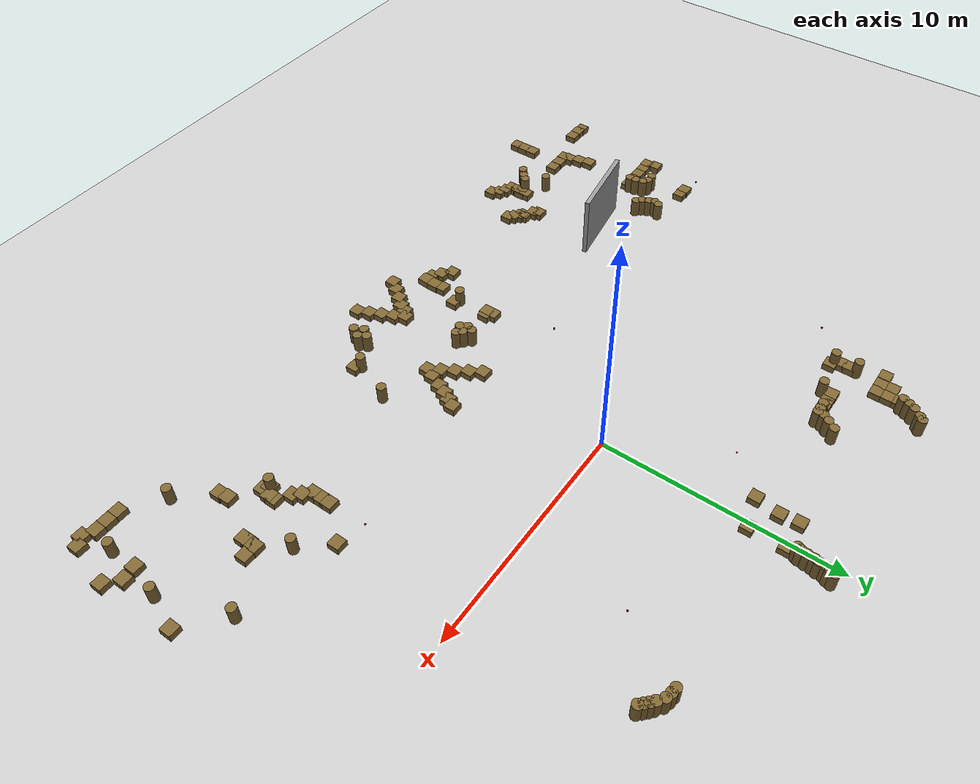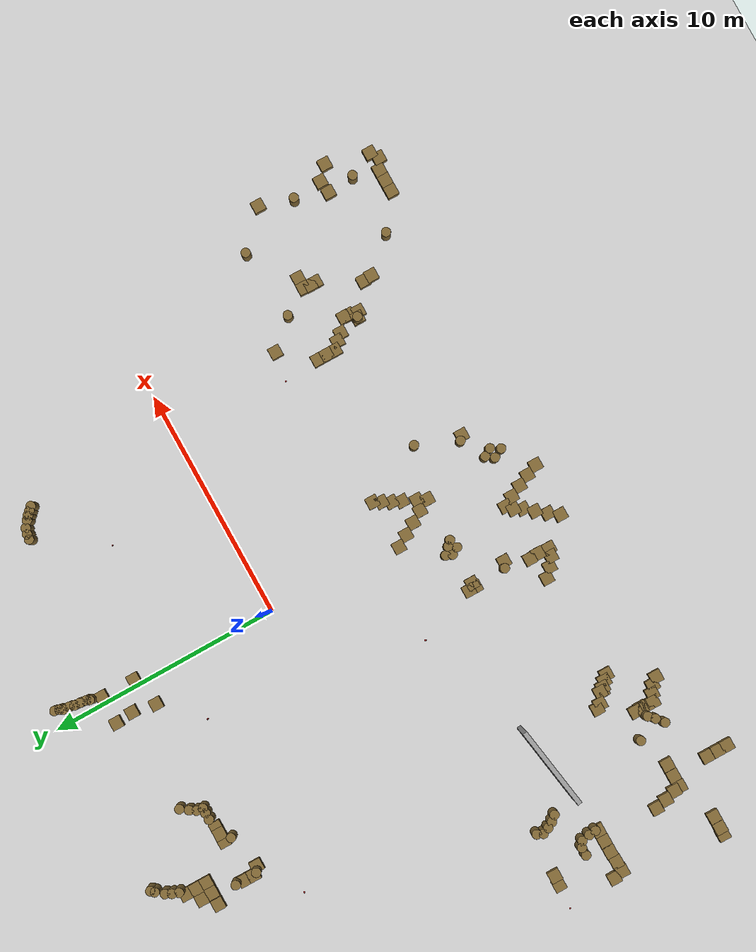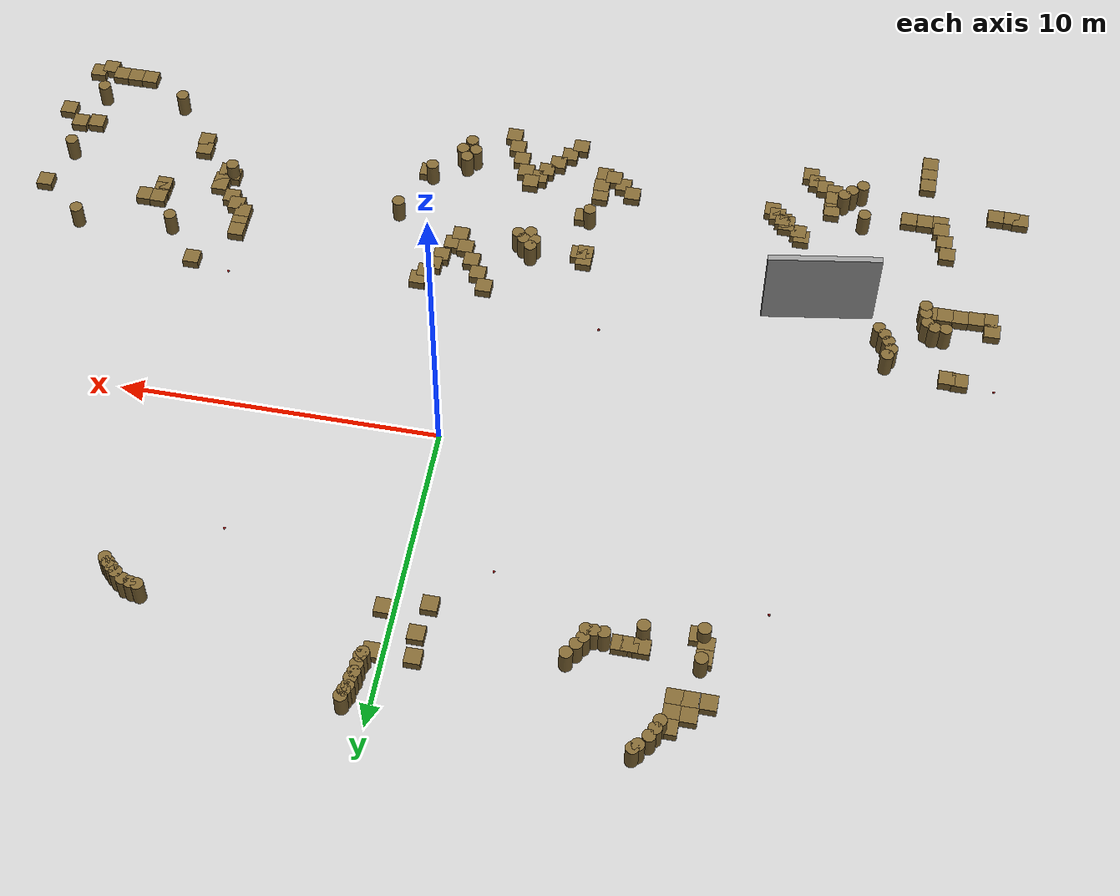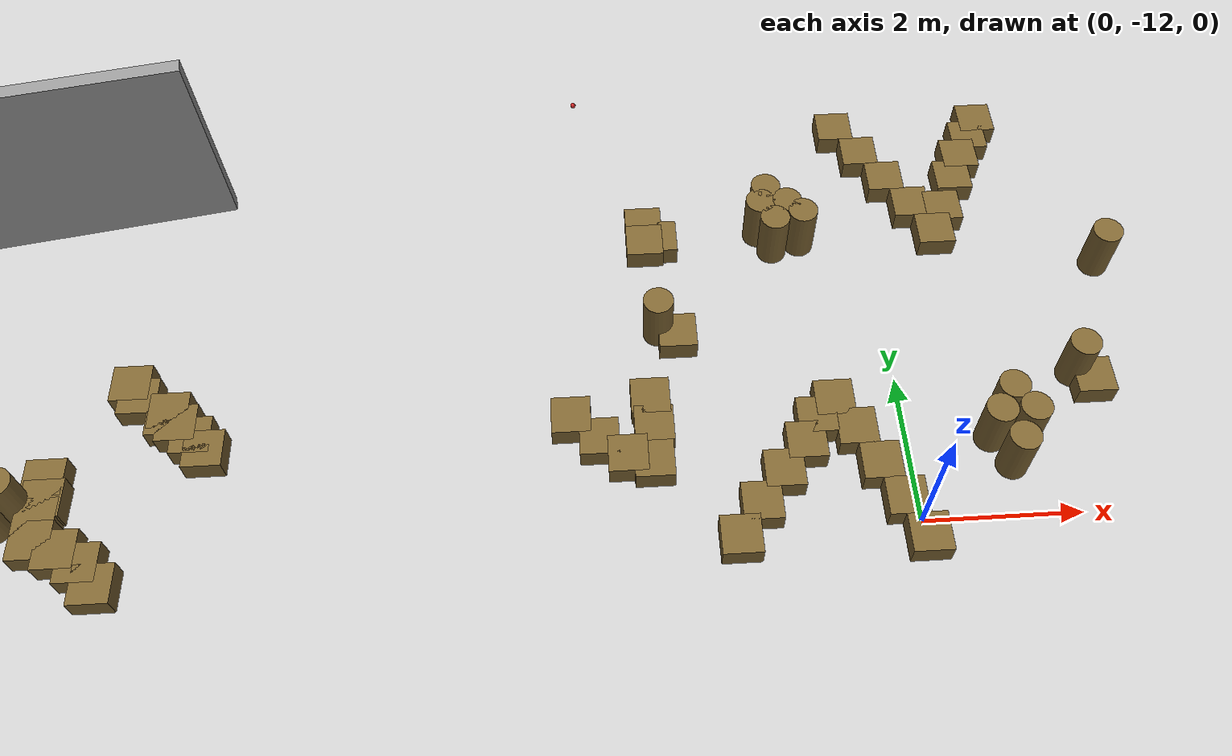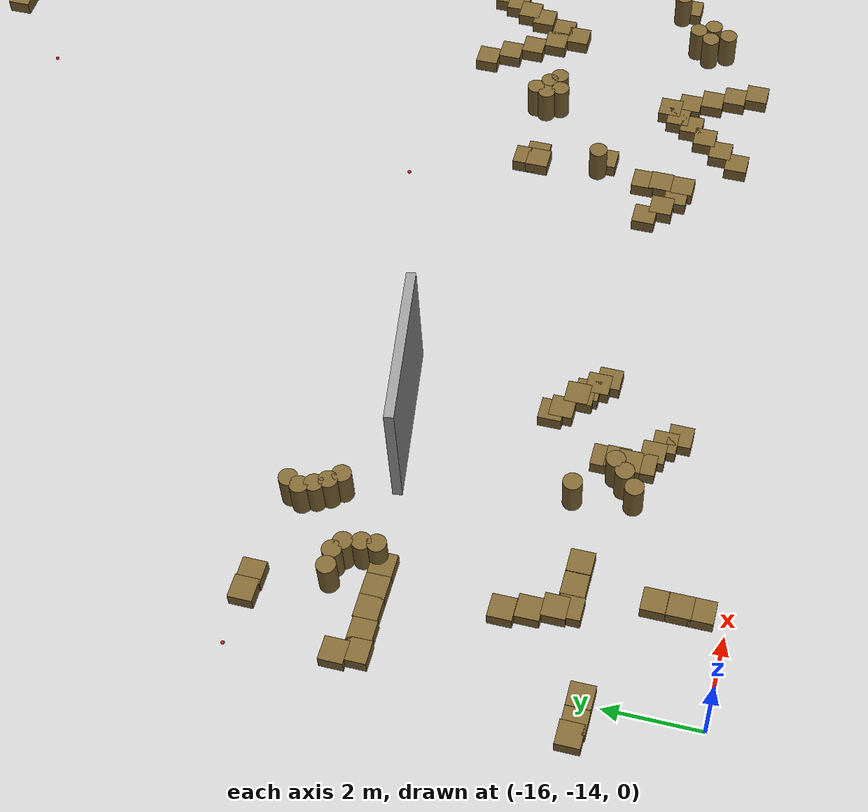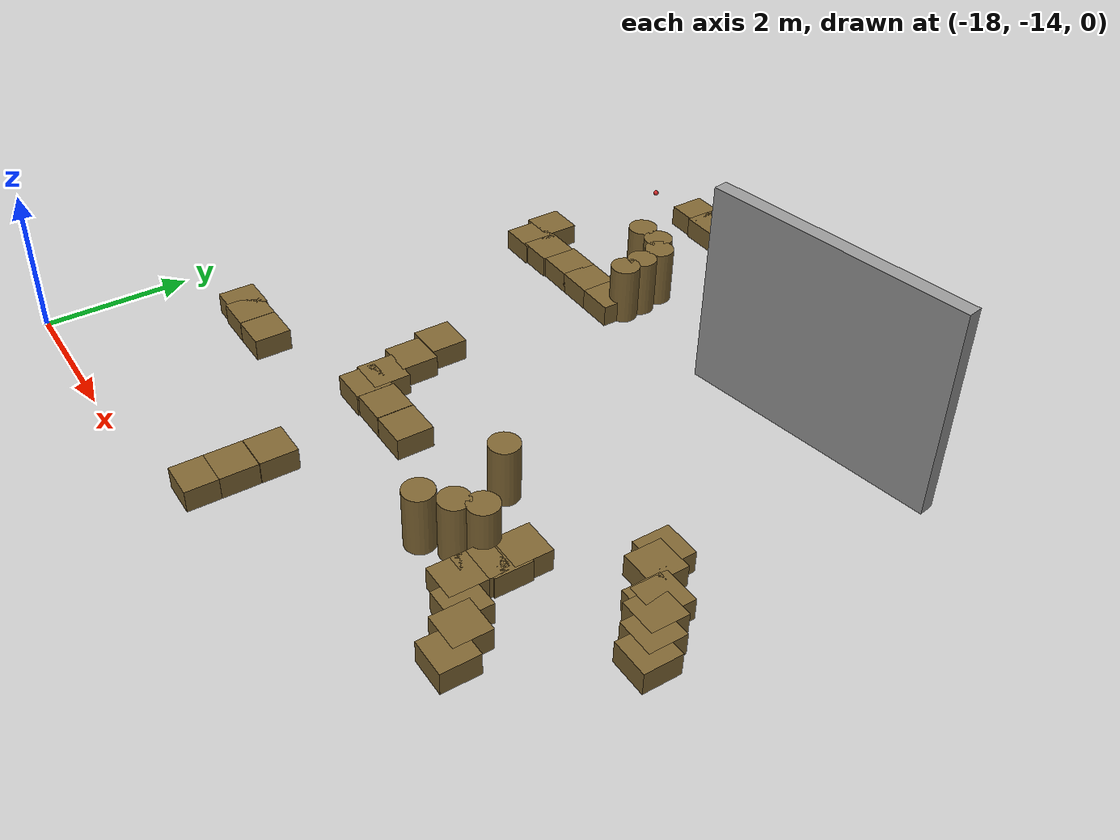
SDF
<sdf version="1.7">
 <world name="default">
  <scene><ambient>0.4 0.4 0.4 1</ambient><background>0.7 0.7 0.7 1</background><shadows>0</shadows></scene>
  <light name="sun" type="directional">
   <pose>0 0 10 0 -0 0</pose>
   <diffuse>0.8 0.8 0.8 1</diffuse>
   <specular>0.2 0.2 0.2 1</specular>
   <attenuation>
    <range>1000</range>
    <constant>0.9</constant>
    <linear>0.01</linear>
    <quadratic>0.001</quadratic>
   </attenuation>
   <direction>-0.5 0.1 -0.9</direction>
   <spot><inner_angle>0</inner_angle><outer_angle>0</outer_angle><falloff>0</falloff></spot>
  </light>
  <model name="ground_plane">
   <static>1</static>
   <link name="link">
    <collision name="collision">
     <geometry><plane><normal>0 0 1</normal><size>100 100</size></plane></geometry>
     <surface><friction><ode><mu>100</mu><mu2>50</mu2></ode></friction></surface>
    </collision>
    <visual name="visual">
     <cast_shadows>0</cast_shadows>
     <geometry><plane><normal>0 0 1</normal><size>100 100</size></plane></geometry>
     <material>
      <script><uri>file://media/materials/scripts/gazebo.material</uri><name>Gazebo/Grey</name></script>
     </material>
    </visual>
   </link>
  </model>
  <physics name="default_physics" default="0" type="ode">
   <real_time_update_rate>1000</real_time_update_rate>
   <max_step_size>0.02</max_step_size>
   <real_time_factor>0</real_time_factor>
   <ode>
    <solver>
     <type>quick</type>
     <iters>150</iters>
     <precon_iters>0</precon_iters>
     <sor>1.4</sor>
     <use_dynamic_moi_rescaling>1</use_dynamic_moi_rescaling>
    </solver>
    <constraints>
     <cfm>1e-05</cfm>
     <erp>0.2</erp>
     <contact_max_correcting_vel>2000</contact_max_correcting_vel>
     <contact_surface_layer>0.01</contact_surface_layer>
    </constraints>
   </ode>
  </physics>
  <gravity>0 0 -9.8</gravity>
  <magnetic_field>6e-06 2.3e-05 -4.2e-05</magnetic_field>
  <atmosphere type="adiabatic"/>
  <spherical_coordinates>
   <surface_model>EARTH_WGS84</surface_model>
   <latitude_deg>0</latitude_deg>
   <longitude_deg>0</longitude_deg>
   <elevation>0</elevation>
   <heading_deg>0</heading_deg>
  </spherical_coordinates>
  <audio><device>default</device></audio>
  <model name="mini_cylinder_0_clone_0">
   <link name="link">
    <inertial>
     <mass>1</mass>
     <inertia><ixx>0.145833</ixx><ixy>0</ixy><ixz>0</ixz><iyy>0.145833</iyy><iyz>0</iyz><izz>0.125</izz></inertia>
    </inertial>
    <visual name="visual">
     <geometry><cylinder><radius>0.2</radius><length>0.8</length></cylinder></geometry>
     <material>
      <script><name>Gazebo/Grey</name><uri>file://media/materials/scripts/gazebo.material</uri></script>
      <shader type="vertex"><normal_map>__default__</normal_map></shader>
      <ambient>0.5 0.4 0.2 1</ambient>
      <diffuse>0.7 0.7 0.7 1</diffuse>
      <specular>0.01 0.01 0.01 1</specular>
      <emissive>0 0 0 1</emissive>
     </material>
    </visual>
    <collision name="collision">
     <geometry><cylinder><radius>0.2</radius><length>0.8</length></cylinder></geometry>
     <surface>
      <friction>
       <ode><mu>1</mu><mu2>1</mu2><fdir1>0 0 0</fdir1><slip1>0</slip1><slip2>0</slip2></ode>
       <torsional>
        <coefficient>1</coefficient>
        <patch_radius>0</patch_radius>
        <surface_radius>0</surface_radius>
        <use_patch_radius>1</use_patch_radius>
        <ode><slip>0</slip></ode>
       </torsional>
      </friction>
      <bounce><restitution_coefficient>0</restitution_coefficient><threshold>1e+06</threshold></bounce>
      <contact>
       <collide_without_contact>0</collide_without_contact>
       <collide_without_contact_bitmask>1</collide_without_contact_bitmask>
       <collide_bitmask>1</collide_bitmask>
       <ode>
        <soft_cfm>0</soft_cfm>
        <soft_erp>0.2</soft_erp>
        <kp>1e+13</kp>
        <kd>1</kd>
        <max_vel>0.01</max_vel>
        <min_depth>0</min_depth>
       </ode>
       <bullet>
        <split_impulse>1</split_impulse>
        <split_impulse_penetration_threshold>-0.01</split_impulse_penetration_threshold>
        <soft_cfm>0</soft_cfm>
        <soft_erp>0.2</soft_erp>
        <kp>1e+13</kp>
        <kd>1</kd>
       </bullet>
      </contact>
     </surface>
    </collision>
   </link>
   <static>1</static>
   <pose>8 6.85 0.4 0 -0 0</pose>
  </model>
  <model name="mini_box_clone_clone_0">
   <link name="link">
    <inertial>
     <mass>1</mass>
     <inertia>
      <ixx>0.166667</ixx>
      <ixy>0</ixy>
      <ixz>0</ixz>
      <iyy>0.166667</iyy>
      <iyz>0</iyz>
      <izz>0.166667</izz>
     </inertia>
    </inertial>
    <visual name="visual">
     <geometry><box><size>0.5 0.5 0.3</size></box></geometry>
     <material>
      <script><name>Gazebo/Grey</name><uri>file://media/materials/scripts/gazebo.material</uri></script>
      <shader type="vertex"><normal_map>__default__</normal_map></shader>
      <ambient>0.5 0.4 0.2 1</ambient>
      <diffuse>0.7 0.7 0.7 1</diffuse>
      <specular>0.01 0.01 0.01 1</specular>
      <emissive>0 0 0 1</emissive>
     </material>
    </visual>
    <collision name="collision">
     <geometry><box><size>0.5 0.5 0.3</size></box></geometry>
     <surface>
      <friction>
       <ode><mu>1</mu><mu2>1</mu2><fdir1>0 0 0</fdir1><slip1>0</slip1><slip2>0</slip2></ode>
       <torsional>
        <coefficient>1</coefficient>
        <patch_radius>0</patch_radius>
        <surface_radius>0</surface_radius>
        <use_patch_radius>1</use_patch_radius>
        <ode><slip>0</slip></ode>
       </torsional>
      </friction>
      <bounce><restitution_coefficient>0</restitution_coefficient><threshold>1e+06</threshold></bounce>
      <contact>
       <collide_without_contact>0</collide_without_contact>
       <collide_without_contact_bitmask>1</collide_without_contact_bitmask>
       <collide_bitmask>1</collide_bitmask>
       <ode>
        <soft_cfm>0</soft_cfm>
        <soft_erp>0.2</soft_erp>
        <kp>1e+13</kp>
        <kd>1</kd>
        <max_vel>0.01</max_vel>
        <min_depth>0</min_depth>
       </ode>
       <bullet>
        <split_impulse>1</split_impulse>
        <split_impulse_penetration_threshold>-0.01</split_impulse_penetration_threshold>
        <soft_cfm>0</soft_cfm>
        <soft_erp>0.2</soft_erp>
        <kp>1e+13</kp>
        <kd>1</kd>
       </bullet>
      </contact>
     </surface>
    </collision>
   </link>
   <static>1</static>
   <pose>0.311896 7.72531 0.15 0 -0 0</pose>
  </model>
  <model name="mini_box_clone_clone_2">
   <link name="link">
    <inertial>
     <mass>1</mass>
     <inertia>
      <ixx>0.166667</ixx>
      <ixy>0</ixy>
      <ixz>0</ixz>
      <iyy>0.166667</iyy>
      <iyz>0</iyz>
      <izz>0.166667</izz>
     </inertia>
    </inertial>
    <visual name="visual">
     <geometry><box><size>0.5 0.5 0.3</size></box></geometry>
     <material>
      <script><name>Gazebo/Grey</name><uri>file://media/materials/scripts/gazebo.material</uri></script>
      <shader type="vertex"><normal_map>__default__</normal_map></shader>
      <ambient>0.5 0.4 0.2 1</ambient>
      <diffuse>0.7 0.7 0.7 1</diffuse>
      <specular>0.01 0.01 0.01 1</specular>
      <emissive>0 0 0 1</emissive>
     </material>
    </visual>
    <collision name="collision">
     <geometry><box><size>0.5 0.5 0.3</size></box></geometry>
     <surface>
      <friction>
       <ode><mu>1</mu><mu2>1</mu2><fdir1>0 0 0</fdir1><slip1>0</slip1><slip2>0</slip2></ode>
       <torsional>
        <coefficient>1</coefficient>
        <patch_radius>0</patch_radius>
        <surface_radius>0</surface_radius>
        <use_patch_radius>1</use_patch_radius>
        <ode><slip>0</slip></ode>
       </torsional>
      </friction>
      <bounce><restitution_coefficient>0</restitution_coefficient><threshold>1e+06</threshold></bounce>
      <contact>
       <collide_without_contact>0</collide_without_contact>
       <collide_without_contact_bitmask>1</collide_without_contact_bitmask>
       <collide_bitmask>1</collide_bitmask>
       <ode>
        <soft_cfm>0</soft_cfm>
        <soft_erp>0.2</soft_erp>
        <kp>1e+13</kp>
        <kd>1</kd>
        <max_vel>0.01</max_vel>
        <min_depth>0</min_depth>
       </ode>
       <bullet>
        <split_impulse>1</split_impulse>
        <split_impulse_penetration_threshold>-0.01</split_impulse_penetration_threshold>
        <soft_cfm>0</soft_cfm>
        <soft_erp>0.2</soft_erp>
        <kp>1e+13</kp>
        <kd>1</kd>
       </bullet>
      </contact>
     </surface>
    </collision>
   </link>
   <static>1</static>
   <pose>-0.824684 6.94928 0.15 0 -0 0</pose>
  </model>
  <model name="mini_box_clone_clone_3">
   <link name="link">
    <inertial>
     <mass>1</mass>
     <inertia>
      <ixx>0.166667</ixx>
      <ixy>0</ixy>
      <ixz>0</ixz>
      <iyy>0.166667</iyy>
      <iyz>0</iyz>
      <izz>0.166667</izz>
     </inertia>
    </inertial>
    <visual name="visual">
     <geometry><box><size>0.5 0.5 0.3</size></box></geometry>
     <material>
      <script><name>Gazebo/Grey</name><uri>file://media/materials/scripts/gazebo.material</uri></script>
      <shader type="vertex"><normal_map>__default__</normal_map></shader>
      <ambient>0.5 0.4 0.2 1</ambient>
      <diffuse>0.7 0.7 0.7 1</diffuse>
      <specular>0.01 0.01 0.01 1</specular>
      <emissive>0 0 0 1</emissive>
     </material>
    </visual>
    <collision name="collision">
     <geometry><box><size>0.5 0.5 0.3</size></box></geometry>
     <surface>
      <friction>
       <ode><mu>1</mu><mu2>1</mu2><fdir1>0 0 0</fdir1><slip1>0</slip1><slip2>0</slip2></ode>
       <torsional>
        <coefficient>1</coefficient>
        <patch_radius>0</patch_radius>
        <surface_radius>0</surface_radius>
        <use_patch_radius>1</use_patch_radius>
        <ode><slip>0</slip></ode>
       </torsional>
      </friction>
      <bounce><restitution_coefficient>0</restitution_coefficient><threshold>1e+06</threshold></bounce>
      <contact>
       <collide_without_contact>0</collide_without_contact>
       <collide_without_contact_bitmask>1</collide_without_contact_bitmask>
       <collide_bitmask>1</collide_bitmask>
       <ode>
        <soft_cfm>0</soft_cfm>
        <soft_erp>0.2</soft_erp>
        <kp>1e+13</kp>
        <kd>1</kd>
        <max_vel>0.01</max_vel>
        <min_depth>0</min_depth>
       </ode>
       <bullet>
        <split_impulse>1</split_impulse>
        <split_impulse_penetration_threshold>-0.01</split_impulse_penetration_threshold>
        <soft_cfm>0</soft_cfm>
        <soft_erp>0.2</soft_erp>
        <kp>1e+13</kp>
        <kd>1</kd>
       </bullet>
      </contact>
     </surface>
    </collision>
   </link>
   <static>1</static>
   <pose>0.298756 6.25504 0.15 0 -0 0</pose>
  </model>
  <model name="mini_cylinder_0_clone_0_clone">
   <link name="link">
    <inertial>
     <mass>1</mass>
     <inertia><ixx>0.145833</ixx><ixy>0</ixy><ixz>0</ixz><iyy>0.145833</iyy><iyz>0</iyz><izz>0.125</izz></inertia>
    </inertial>
    <visual name="visual">
     <geometry><cylinder><radius>0.2</radius><length>0.8</length></cylinder></geometry>
     <material>
      <script><name>Gazebo/Grey</name><uri>file://media/materials/scripts/gazebo.material</uri></script>
      <shader type="vertex"><normal_map>__default__</normal_map></shader>
      <ambient>0.5 0.4 0.2 1</ambient>
      <diffuse>0.7 0.7 0.7 1</diffuse>
      <specular>0.01 0.01 0.01 1</specular>
      <emissive>0 0 0 1</emissive>
     </material>
    </visual>
    <collision name="collision">
     <geometry><cylinder><radius>0.2</radius><length>0.8</length></cylinder></geometry>
     <surface>
      <friction>
       <ode><mu>1</mu><mu2>1</mu2><fdir1>0 0 0</fdir1><slip1>0</slip1><slip2>0</slip2></ode>
       <torsional>
        <coefficient>1</coefficient>
        <patch_radius>0</patch_radius>
        <surface_radius>0</surface_radius>
        <use_patch_radius>1</use_patch_radius>
        <ode><slip>0</slip></ode>
       </torsional>
      </friction>
      <bounce><restitution_coefficient>0</restitution_coefficient><threshold>1e+06</threshold></bounce>
      <contact>
       <collide_without_contact>0</collide_without_contact>
       <collide_without_contact_bitmask>1</collide_without_contact_bitmask>
       <collide_bitmask>1</collide_bitmask>
       <ode>
        <soft_cfm>0</soft_cfm>
        <soft_erp>0.2</soft_erp>
        <kp>1e+13</kp>
        <kd>1</kd>
        <max_vel>0.01</max_vel>
        <min_depth>0</min_depth>
       </ode>
       <bullet>
        <split_impulse>1</split_impulse>
        <split_impulse_penetration_threshold>-0.01</split_impulse_penetration_threshold>
        <soft_cfm>0</soft_cfm>
        <soft_erp>0.2</soft_erp>
        <kp>1e+13</kp>
        <kd>1</kd>
       </bullet>
      </contact>
     </surface>
    </collision>
   </link>
   <static>1</static>
   <pose>13.224 -6.11998 0.4 0 -0 0</pose>
  </model>
  <model name="mini_cylinder_0_clone_0_clone_0">
   <link name="link">
    <inertial>
     <mass>1</mass>
     <inertia><ixx>0.145833</ixx><ixy>0</ixy><ixz>0</ixz><iyy>0.145833</iyy><iyz>0</iyz><izz>0.125</izz></inertia>
    </inertial>
    <visual name="visual">
     <geometry><cylinder><radius>0.2</radius><length>0.8</length></cylinder></geometry>
     <material>
      <script><name>Gazebo/Grey</name><uri>file://media/materials/scripts/gazebo.material</uri></script>
      <shader type="vertex"><normal_map>__default__</normal_map></shader>
      <ambient>0.5 0.4 0.2 1</ambient>
      <diffuse>0.7 0.7 0.7 1</diffuse>
      <specular>0.01 0.01 0.01 1</specular>
      <emissive>0 0 0 1</emissive>
     </material>
    </visual>
    <collision name="collision">
     <geometry><cylinder><radius>0.2</radius><length>0.8</length></cylinder></geometry>
     <surface>
      <friction>
       <ode><mu>1</mu><mu2>1</mu2><fdir1>0 0 0</fdir1><slip1>0</slip1><slip2>0</slip2></ode>
       <torsional>
        <coefficient>1</coefficient>
        <patch_radius>0</patch_radius>
        <surface_radius>0</surface_radius>
        <use_patch_radius>1</use_patch_radius>
        <ode><slip>0</slip></ode>
       </torsional>
      </friction>
      <bounce><restitution_coefficient>0</restitution_coefficient><threshold>1e+06</threshold></bounce>
      <contact>
       <collide_without_contact>0</collide_without_contact>
       <collide_without_contact_bitmask>1</collide_without_contact_bitmask>
       <collide_bitmask>1</collide_bitmask>
       <ode>
        <soft_cfm>0</soft_cfm>
        <soft_erp>0.2</soft_erp>
        <kp>1e+13</kp>
        <kd>1</kd>
        <max_vel>0.01</max_vel>
        <min_depth>0</min_depth>
       </ode>
       <bullet>
        <split_impulse>1</split_impulse>
        <split_impulse_penetration_threshold>-0.01</split_impulse_penetration_threshold>
        <soft_cfm>0</soft_cfm>
        <soft_erp>0.2</soft_erp>
        <kp>1e+13</kp>
        <kd>1</kd>
       </bullet>
      </contact>
     </surface>
    </collision>
   </link>
   <static>1</static>
   <pose>8.7545 -8.82263 0.4 0 -0 0</pose>
  </model>
  <model name="mini_cylinder_0_clone_0_clone_1">
   <link name="link">
    <inertial>
     <mass>1</mass>
     <inertia><ixx>0.145833</ixx><ixy>0</ixy><ixz>0</ixz><iyy>0.145833</iyy><iyz>0</iyz><izz>0.125</izz></inertia>
    </inertial>
    <visual name="visual">
     <geometry><cylinder><radius>0.2</radius><length>0.8</length></cylinder></geometry>
     <material>
      <script><name>Gazebo/Grey</name><uri>file://media/materials/scripts/gazebo.material</uri></script>
      <shader type="vertex"><normal_map>__default__</normal_map></shader>
      <ambient>0.5 0.4 0.2 1</ambient>
      <diffuse>0.7 0.7 0.7 1</diffuse>
      <specular>0.01 0.01 0.01 1</specular>
      <emissive>0 0 0 1</emissive>
     </material>
    </visual>
    <collision name="collision">
     <geometry><cylinder><radius>0.2</radius><length>0.8</length></cylinder></geometry>
     <surface>
      <friction>
       <ode><mu>1</mu><mu2>1</mu2><fdir1>0 0 0</fdir1><slip1>0</slip1><slip2>0</slip2></ode>
       <torsional>
        <coefficient>1</coefficient>
        <patch_radius>0</patch_radius>
        <surface_radius>0</surface_radius>
        <use_patch_radius>1</use_patch_radius>
        <ode><slip>0</slip></ode>
       </torsional>
      </friction>
      <bounce><restitution_coefficient>0</restitution_coefficient><threshold>1e+06</threshold></bounce>
      <contact>
       <collide_without_contact>0</collide_without_contact>
       <collide_without_contact_bitmask>1</collide_without_contact_bitmask>
       <collide_bitmask>1</collide_bitmask>
       <ode>
        <soft_cfm>0</soft_cfm>
        <soft_erp>0.2</soft_erp>
        <kp>1e+13</kp>
        <kd>1</kd>
        <max_vel>0.01</max_vel>
        <min_depth>0</min_depth>
       </ode>
       <bullet>
        <split_impulse>1</split_impulse>
        <split_impulse_penetration_threshold>-0.01</split_impulse_penetration_threshold>
        <soft_cfm>0</soft_cfm>
        <soft_erp>0.2</soft_erp>
        <kp>1e+13</kp>
        <kd>1</kd>
       </bullet>
      </contact>
     </surface>
    </collision>
   </link>
   <static>1</static>
   <pose>14.2436 -8.91515 0.4 0 -0 0</pose>
  </model>
  <model name="mini_cylinder_0_clone_0_clone_2">
   <link name="link">
    <inertial>
     <mass>1</mass>
     <inertia><ixx>0.145833</ixx><ixy>0</ixy><ixz>0</ixz><iyy>0.145833</iyy><iyz>0</iyz><izz>0.125</izz></inertia>
    </inertial>
    <visual name="visual">
     <geometry><cylinder><radius>0.2</radius><length>0.8</length></cylinder></geometry>
     <material>
      <script><name>Gazebo/Grey</name><uri>file://media/materials/scripts/gazebo.material</uri></script>
      <shader type="vertex"><normal_map>__default__</normal_map></shader>
      <ambient>0.5 0.4 0.2 1</ambient>
      <diffuse>0.7 0.7 0.7 1</diffuse>
      <specular>0.01 0.01 0.01 1</specular>
      <emissive>0 0 0 1</emissive>
     </material>
    </visual>
    <collision name="collision">
     <geometry><cylinder><radius>0.2</radius><length>0.8</length></cylinder></geometry>
     <surface>
      <friction>
       <ode><mu>1</mu><mu2>1</mu2><fdir1>0 0 0</fdir1><slip1>0</slip1><slip2>0</slip2></ode>
       <torsional>
        <coefficient>1</coefficient>
        <patch_radius>0</patch_radius>
        <surface_radius>0</surface_radius>
        <use_patch_radius>1</use_patch_radius>
        <ode><slip>0</slip></ode>
       </torsional>
      </friction>
      <bounce><restitution_coefficient>0</restitution_coefficient><threshold>1e+06</threshold></bounce>
      <contact>
       <collide_without_contact>0</collide_without_contact>
       <collide_without_contact_bitmask>1</collide_without_contact_bitmask>
       <collide_bitmask>1</collide_bitmask>
       <ode>
        <soft_cfm>0</soft_cfm>
        <soft_erp>0.2</soft_erp>
        <kp>1e+13</kp>
        <kd>1</kd>
        <max_vel>0.01</max_vel>
        <min_depth>0</min_depth>
       </ode>
       <bullet>
        <split_impulse>1</split_impulse>
        <split_impulse_penetration_threshold>-0.01</split_impulse_penetration_threshold>
        <soft_cfm>0</soft_cfm>
        <soft_erp>0.2</soft_erp>
        <kp>1e+13</kp>
        <kd>1</kd>
       </bullet>
      </contact>
     </surface>
    </collision>
   </link>
   <static>1</static>
   <pose>13.8924 -11.4476 0.4 0 -0 0</pose>
  </model>
  <model name="mini_box_clone_clone_3_clone">
   <link name="link">
    <inertial>
     <mass>1</mass>
     <inertia>
      <ixx>0.166667</ixx>
      <ixy>0</ixy>
      <ixz>0</ixz>
      <iyy>0.166667</iyy>
      <iyz>0</iyz>
      <izz>0.166667</izz>
     </inertia>
    </inertial>
    <visual name="visual">
     <geometry><box><size>0.5 0.5 0.3</size></box></geometry>
     <material>
      <script><name>Gazebo/Grey</name><uri>file://media/materials/scripts/gazebo.material</uri></script>
      <shader type="vertex"><normal_map>__default__</normal_map></shader>
      <ambient>0.5 0.4 0.2 1</ambient>
      <diffuse>0.7 0.7 0.7 1</diffuse>
      <specular>0.01 0.01 0.01 1</specular>
      <emissive>0 0 0 1</emissive>
     </material>
    </visual>
    <collision name="collision">
     <geometry><box><size>0.5 0.5 0.3</size></box></geometry>
     <surface>
      <friction>
       <ode><mu>1</mu><mu2>1</mu2><fdir1>0 0 0</fdir1><slip1>0</slip1><slip2>0</slip2></ode>
       <torsional>
        <coefficient>1</coefficient>
        <patch_radius>0</patch_radius>
        <surface_radius>0</surface_radius>
        <use_patch_radius>1</use_patch_radius>
        <ode><slip>0</slip></ode>
       </torsional>
      </friction>
      <bounce><restitution_coefficient>0</restitution_coefficient><threshold>1e+06</threshold></bounce>
      <contact>
       <collide_without_contact>0</collide_without_contact>
       <collide_without_contact_bitmask>1</collide_without_contact_bitmask>
       <collide_bitmask>1</collide_bitmask>
       <ode>
        <soft_cfm>0</soft_cfm>
        <soft_erp>0.2</soft_erp>
        <kp>1e+13</kp>
        <kd>1</kd>
        <max_vel>0.01</max_vel>
        <min_depth>0</min_depth>
       </ode>
       <bullet>
        <split_impulse>1</split_impulse>
        <split_impulse_penetration_threshold>-0.01</split_impulse_penetration_threshold>
        <soft_cfm>0</soft_cfm>
        <soft_erp>0.2</soft_erp>
        <kp>1e+13</kp>
        <kd>1</kd>
       </bullet>
      </contact>
     </surface>
    </collision>
   </link>
   <static>1</static>
   <pose>11.3808 -7.50629 0.15 0 -0 0</pose>
  </model>
  <model name="mini_box_clone_clone_3_clone_0">
   <link name="link">
    <inertial>
     <mass>1</mass>
     <inertia>
      <ixx>0.166667</ixx>
      <ixy>0</ixy>
      <ixz>0</ixz>
      <iyy>0.166667</iyy>
      <iyz>0</iyz>
      <izz>0.166667</izz>
     </inertia>
    </inertial>
    <visual name="visual">
     <geometry><box><size>0.5 0.5 0.3</size></box></geometry>
     <material>
      <script><name>Gazebo/Grey</name><uri>file://media/materials/scripts/gazebo.material</uri></script>
      <shader type="vertex"><normal_map>__default__</normal_map></shader>
      <ambient>0.5 0.4 0.2 1</ambient>
      <diffuse>0.7 0.7 0.7 1</diffuse>
      <specular>0.01 0.01 0.01 1</specular>
      <emissive>0 0 0 1</emissive>
     </material>
    </visual>
    <collision name="collision">
     <geometry><box><size>0.5 0.5 0.3</size></box></geometry>
     <surface>
      <friction>
       <ode><mu>1</mu><mu2>1</mu2><fdir1>0 0 0</fdir1><slip1>0</slip1><slip2>0</slip2></ode>
       <torsional>
        <coefficient>1</coefficient>
        <patch_radius>0</patch_radius>
        <surface_radius>0</surface_radius>
        <use_patch_radius>1</use_patch_radius>
        <ode><slip>0</slip></ode>
       </torsional>
      </friction>
      <bounce><restitution_coefficient>0</restitution_coefficient><threshold>1e+06</threshold></bounce>
      <contact>
       <collide_without_contact>0</collide_without_contact>
       <collide_without_contact_bitmask>1</collide_without_contact_bitmask>
       <collide_bitmask>1</collide_bitmask>
       <ode>
        <soft_cfm>0</soft_cfm>
        <soft_erp>0.2</soft_erp>
        <kp>1e+13</kp>
        <kd>1</kd>
        <max_vel>0.01</max_vel>
        <min_depth>0</min_depth>
       </ode>
       <bullet>
        <split_impulse>1</split_impulse>
        <split_impulse_penetration_threshold>-0.01</split_impulse_penetration_threshold>
        <soft_cfm>0</soft_cfm>
        <soft_erp>0.2</soft_erp>
        <kp>1e+13</kp>
        <kd>1</kd>
       </bullet>
      </contact>
     </surface>
    </collision>
   </link>
   <static>1</static>
   <pose>10.0339 -10.1728 0.15 0 -0 0</pose>
  </model>
  <model name="mini_box_clone_clone_3_clone_1">
   <link name="link">
    <inertial>
     <mass>1</mass>
     <inertia>
      <ixx>0.166667</ixx>
      <ixy>0</ixy>
      <ixz>0</ixz>
      <iyy>0.166667</iyy>
      <iyz>0</iyz>
      <izz>0.166667</izz>
     </inertia>
    </inertial>
    <visual name="visual">
     <geometry><box><size>0.5 0.5 0.3</size></box></geometry>
     <material>
      <script><name>Gazebo/Grey</name><uri>file://media/materials/scripts/gazebo.material</uri></script>
      <shader type="vertex"><normal_map>__default__</normal_map></shader>
      <ambient>0.5 0.4 0.2 1</ambient>
      <diffuse>0.7 0.7 0.7 1</diffuse>
      <specular>0.01 0.01 0.01 1</specular>
      <emissive>0 0 0 1</emissive>
     </material>
    </visual>
    <collision name="collision">
     <geometry><box><size>0.5 0.5 0.3</size></box></geometry>
     <surface>
      <friction>
       <ode><mu>1</mu><mu2>1</mu2><fdir1>0 0 0</fdir1><slip1>0</slip1><slip2>0</slip2></ode>
       <torsional>
        <coefficient>1</coefficient>
        <patch_radius>0</patch_radius>
        <surface_radius>0</surface_radius>
        <use_patch_radius>1</use_patch_radius>
        <ode><slip>0</slip></ode>
       </torsional>
      </friction>
      <bounce><restitution_coefficient>0</restitution_coefficient><threshold>1e+06</threshold></bounce>
      <contact>
       <collide_without_contact>0</collide_without_contact>
       <collide_without_contact_bitmask>1</collide_without_contact_bitmask>
       <collide_bitmask>1</collide_bitmask>
       <ode>
        <soft_cfm>0</soft_cfm>
        <soft_erp>0.2</soft_erp>
        <kp>1e+13</kp>
        <kd>1</kd>
        <max_vel>0.01</max_vel>
        <min_depth>0</min_depth>
       </ode>
       <bullet>
        <split_impulse>1</split_impulse>
        <split_impulse_penetration_threshold>-0.01</split_impulse_penetration_threshold>
        <soft_cfm>0</soft_cfm>
        <soft_erp>0.2</soft_erp>
        <kp>1e+13</kp>
        <kd>1</kd>
       </bullet>
      </contact>
     </surface>
    </collision>
   </link>
   <static>1</static>
   <pose>14.4187 -10.2264 0.15 0 -0 0</pose>
  </model>
  <model name="mini_box_clone_clone_3_clone_2">
   <link name="link">
    <inertial>
     <mass>1</mass>
     <inertia>
      <ixx>0.166667</ixx>
      <ixy>0</ixy>
      <ixz>0</ixz>
      <iyy>0.166667</iyy>
      <iyz>0</iyz>
      <izz>0.166667</izz>
     </inertia>
    </inertial>
    <visual name="visual">
     <geometry><box><size>0.5 0.5 0.3</size></box></geometry>
     <material>
      <script><name>Gazebo/Grey</name><uri>file://media/materials/scripts/gazebo.material</uri></script>
      <shader type="vertex"><normal_map>__default__</normal_map></shader>
      <ambient>0.5 0.4 0.2 1</ambient>
      <diffuse>0.7 0.7 0.7 1</diffuse>
      <specular>0.01 0.01 0.01 1</specular>
      <emissive>0 0 0 1</emissive>
     </material>
    </visual>
    <collision name="collision">
     <geometry><box><size>0.5 0.5 0.3</size></box></geometry>
     <surface>
      <friction>
       <ode><mu>1</mu><mu2>1</mu2><fdir1>0 0 0</fdir1><slip1>0</slip1><slip2>0</slip2></ode>
       <torsional>
        <coefficient>1</coefficient>
        <patch_radius>0</patch_radius>
        <surface_radius>0</surface_radius>
        <use_patch_radius>1</use_patch_radius>
        <ode><slip>0</slip></ode>
       </torsional>
      </friction>
      <bounce><restitution_coefficient>0</restitution_coefficient><threshold>1e+06</threshold></bounce>
      <contact>
       <collide_without_contact>0</collide_without_contact>
       <collide_without_contact_bitmask>1</collide_without_contact_bitmask>
       <collide_bitmask>1</collide_bitmask>
       <ode>
        <soft_cfm>0</soft_cfm>
        <soft_erp>0.2</soft_erp>
        <kp>1e+13</kp>
        <kd>1</kd>
        <max_vel>0.01</max_vel>
        <min_depth>0</min_depth>
       </ode>
       <bullet>
        <split_impulse>1</split_impulse>
        <split_impulse_penetration_threshold>-0.01</split_impulse_penetration_threshold>
        <soft_cfm>0</soft_cfm>
        <soft_erp>0.2</soft_erp>
        <kp>1e+13</kp>
        <kd>1</kd>
       </bullet>
      </contact>
     </surface>
    </collision>
   </link>
   <static>1</static>
   <pose>14.767 -7.51176 0.15 0 -0 0</pose>
  </model>
  <model name="mini_cylinder_0_clone_0_clone_clone">
   <link name="link">
    <inertial>
     <mass>1</mass>
     <inertia><ixx>0.145833</ixx><ixy>0</ixy><ixz>0</ixz><iyy>0.145833</iyy><iyz>0</iyz><izz>0.125</izz></inertia>
    </inertial>
    <visual name="visual">
     <geometry><cylinder><radius>0.2</radius><length>0.8</length></cylinder></geometry>
     <material>
      <script><name>Gazebo/Grey</name><uri>file://media/materials/scripts/gazebo.material</uri></script>
      <shader type="vertex"><normal_map>__default__</normal_map></shader>
      <ambient>0.5 0.4 0.2 1</ambient>
      <diffuse>0.7 0.7 0.7 1</diffuse>
      <specular>0.01 0.01 0.01 1</specular>
      <emissive>0 0 0 1</emissive>
     </material>
    </visual>
    <collision name="collision">
     <geometry><cylinder><radius>0.2</radius><length>0.8</length></cylinder></geometry>
     <surface>
      <friction>
       <ode><mu>1</mu><mu2>1</mu2><fdir1>0 0 0</fdir1><slip1>0</slip1><slip2>0</slip2></ode>
       <torsional>
        <coefficient>1</coefficient>
        <patch_radius>0</patch_radius>
        <surface_radius>0</surface_radius>
        <use_patch_radius>1</use_patch_radius>
        <ode><slip>0</slip></ode>
       </torsional>
      </friction>
      <bounce><restitution_coefficient>0</restitution_coefficient><threshold>1e+06</threshold></bounce>
      <contact>
       <collide_without_contact>0</collide_without_contact>
       <collide_without_contact_bitmask>1</collide_without_contact_bitmask>
       <collide_bitmask>1</collide_bitmask>
       <ode>
        <soft_cfm>0</soft_cfm>
        <soft_erp>0.2</soft_erp>
        <kp>1e+13</kp>
        <kd>1</kd>
        <max_vel>0.01</max_vel>
        <min_depth>0</min_depth>
       </ode>
       <bullet>
        <split_impulse>1</split_impulse>
        <split_impulse_penetration_threshold>-0.01</split_impulse_penetration_threshold>
        <soft_cfm>0</soft_cfm>
        <soft_erp>0.2</soft_erp>
        <kp>1e+13</kp>
        <kd>1</kd>
       </bullet>
      </contact>
     </surface>
    </collision>
   </link>
   <static>1</static>
   <pose>10.1744 -6.38296 0.4 0 -0 0</pose>
  </model>
  <model name="mini_cylinder_0_clone_0_clone_clone_0">
   <link name="link">
    <inertial>
     <mass>1</mass>
     <inertia><ixx>0.145833</ixx><ixy>0</ixy><ixz>0</ixz><iyy>0.145833</iyy><iyz>0</iyz><izz>0.125</izz></inertia>
    </inertial>
    <visual name="visual">
     <geometry><cylinder><radius>0.2</radius><length>0.8</length></cylinder></geometry>
     <material>
      <script><name>Gazebo/Grey</name><uri>file://media/materials/scripts/gazebo.material</uri></script>
      <shader type="vertex"><normal_map>__default__</normal_map></shader>
      <ambient>0.5 0.4 0.2 1</ambient>
      <diffuse>0.7 0.7 0.7 1</diffuse>
      <specular>0.01 0.01 0.01 1</specular>
      <emissive>0 0 0 1</emissive>
     </material>
    </visual>
    <collision name="collision">
     <geometry><cylinder><radius>0.2</radius><length>0.8</length></cylinder></geometry>
     <surface>
      <friction>
       <ode><mu>1</mu><mu2>1</mu2><fdir1>0 0 0</fdir1><slip1>0</slip1><slip2>0</slip2></ode>
       <torsional>
        <coefficient>1</coefficient>
        <patch_radius>0</patch_radius>
        <surface_radius>0</surface_radius>
        <use_patch_radius>1</use_patch_radius>
        <ode><slip>0</slip></ode>
       </torsional>
      </friction>
      <bounce><restitution_coefficient>0</restitution_coefficient><threshold>1e+06</threshold></bounce>
      <contact>
       <collide_without_contact>0</collide_without_contact>
       <collide_without_contact_bitmask>1</collide_without_contact_bitmask>
       <collide_bitmask>1</collide_bitmask>
       <ode>
        <soft_cfm>0</soft_cfm>
        <soft_erp>0.2</soft_erp>
        <kp>1e+13</kp>
        <kd>1</kd>
        <max_vel>0.01</max_vel>
        <min_depth>0</min_depth>
       </ode>
       <bullet>
        <split_impulse>1</split_impulse>
        <split_impulse_penetration_threshold>-0.01</split_impulse_penetration_threshold>
        <soft_cfm>0</soft_cfm>
        <soft_erp>0.2</soft_erp>
        <kp>1e+13</kp>
        <kd>1</kd>
       </bullet>
      </contact>
     </surface>
    </collision>
   </link>
   <static>1</static>
   <pose>11.1967 -11.5076 0.4 0 -0 0</pose>
  </model>
  <model name="grey_wall_3.5">
   <link name="link">
    <pose>0 0 1.4 0 -0 0</pose>
    <inertial>
     <mass>1</mass>
     <inertia><ixx>1</ixx><ixy>0</ixy><ixz>0</ixz><iyy>1</iyy><iyz>0</iyz><izz>1</izz></inertia>
    </inertial>
    <visual name="visual">
     <cast_shadows>0</cast_shadows>
     <geometry><box><size>3.5 0.2 2.8</size></box></geometry>
     <material>
      <script>
       <uri>model://grey_wall/materials/scripts</uri>
       <uri>model://grey_wall/materials/textures</uri>
       <name>vrc/grey_wall</name>
      </script>
      <shader type="vertex"><normal_map>__default__</normal_map></shader>
      <ambient>1 1 1 1</ambient>
      <diffuse>1 1 1 1</diffuse>
      <specular>0 0 0 1</specular>
      <emissive>0 0 0 1</emissive>
     </material>
    </visual>
    <collision name="collision">
     <geometry><box><size>3.5 0.2 2.8</size></box></geometry>
     <surface>
      <friction>
       <ode><mu>1</mu><mu2>1</mu2><fdir1>0 0 0</fdir1><slip1>0</slip1><slip2>0</slip2></ode>
       <torsional>
        <coefficient>1</coefficient>
        <patch_radius>0</patch_radius>
        <surface_radius>0</surface_radius>
        <use_patch_radius>1</use_patch_radius>
        <ode><slip>0</slip></ode>
       </torsional>
      </friction>
      <bounce><restitution_coefficient>0</restitution_coefficient><threshold>1e+06</threshold></bounce>
      <contact>
       <collide_without_contact>0</collide_without_contact>
       <collide_without_contact_bitmask>1</collide_without_contact_bitmask>
       <collide_bitmask>1</collide_bitmask>
       <ode>
        <soft_cfm>0</soft_cfm>
        <soft_erp>0.2</soft_erp>
        <kp>1e+13</kp>
        <kd>1</kd>
        <max_vel>0.01</max_vel>
        <min_depth>0</min_depth>
       </ode>
       <bullet>
        <split_impulse>1</split_impulse>
        <split_impulse_penetration_threshold>-0.01</split_impulse_penetration_threshold>
        <soft_cfm>0</soft_cfm>
        <soft_erp>0.2</soft_erp>
        <kp>1e+13</kp>
        <kd>1</kd>
       </bullet>
      </contact>
     </surface>
    </collision>
   </link>
   <static>1</static>
   <pose>-10.6984 -6.76515 0 0 -0 0.156615</pose>
  </model>
  <model name="mini_box_clone_clone_2_clone">
   <link name="link">
    <inertial>
     <mass>1</mass>
     <inertia>
      <ixx>0.166667</ixx>
      <ixy>0</ixy>
      <ixz>0</ixz>
      <iyy>0.166667</iyy>
      <iyz>0</iyz>
      <izz>0.166667</izz>
     </inertia>
    </inertial>
    <visual name="visual">
     <geometry><box><size>0.5 0.5 0.3</size></box></geometry>
     <material>
      <script><name>Gazebo/Grey</name><uri>file://media/materials/scripts/gazebo.material</uri></script>
      <shader type="vertex"><normal_map>__default__</normal_map></shader>
      <ambient>0.5 0.4 0.2 1</ambient>
      <diffuse>0.7 0.7 0.7 1</diffuse>
      <specular>0.01 0.01 0.01 1</specular>
      <emissive>0 0 0 1</emissive>
     </material>
    </visual>
    <collision name="collision">
     <geometry><box><size>0.5 0.5 0.3</size></box></geometry>
     <surface>
      <friction>
       <ode><mu>1</mu><mu2>1</mu2><fdir1>0 0 0</fdir1><slip1>0</slip1><slip2>0</slip2></ode>
       <torsional>
        <coefficient>1</coefficient>
        <patch_radius>0</patch_radius>
        <surface_radius>0</surface_radius>
        <use_patch_radius>1</use_patch_radius>
        <ode><slip>0</slip></ode>
       </torsional>
      </friction>
      <bounce><restitution_coefficient>0</restitution_coefficient><threshold>1e+06</threshold></bounce>
      <contact>
       <collide_without_contact>0</collide_without_contact>
       <collide_without_contact_bitmask>1</collide_without_contact_bitmask>
       <collide_bitmask>1</collide_bitmask>
       <ode>
        <soft_cfm>0</soft_cfm>
        <soft_erp>0.2</soft_erp>
        <kp>1e+13</kp>
        <kd>1</kd>
        <max_vel>0.01</max_vel>
        <min_depth>0</min_depth>
       </ode>
       <bullet>
        <split_impulse>1</split_impulse>
        <split_impulse_penetration_threshold>-0.01</split_impulse_penetration_threshold>
        <soft_cfm>0</soft_cfm>
        <soft_erp>0.2</soft_erp>
        <kp>1e+13</kp>
        <kd>1</kd>
       </bullet>
      </contact>
     </surface>
    </collision>
   </link>
   <static>1</static>
   <pose>-7.18928 6.21457 0.15 0 -0 0</pose>
  </model>
  <model name="mini_cylinder_0_clone_0_clone_3">
   <link name="link">
    <inertial>
     <mass>1</mass>
     <inertia><ixx>0.145833</ixx><ixy>0</ixy><ixz>0</ixz><iyy>0.145833</iyy><iyz>0</iyz><izz>0.125</izz></inertia>
    </inertial>
    <visual name="visual">
     <geometry><cylinder><radius>0.2</radius><length>0.8</length></cylinder></geometry>
     <material>
      <script><name>Gazebo/Grey</name><uri>file://media/materials/scripts/gazebo.material</uri></script>
      <shader type="vertex"><normal_map>__default__</normal_map></shader>
      <ambient>0.5 0.4 0.2 1</ambient>
      <diffuse>0.7 0.7 0.7 1</diffuse>
      <specular>0.01 0.01 0.01 1</specular>
      <emissive>0 0 0 1</emissive>
     </material>
    </visual>
    <collision name="collision">
     <geometry><cylinder><radius>0.2</radius><length>0.8</length></cylinder></geometry>
     <surface>
      <friction>
       <ode><mu>1</mu><mu2>1</mu2><fdir1>0 0 0</fdir1><slip1>0</slip1><slip2>0</slip2></ode>
       <torsional>
        <coefficient>1</coefficient>
        <patch_radius>0</patch_radius>
        <surface_radius>0</surface_radius>
        <use_patch_radius>1</use_patch_radius>
        <ode><slip>0</slip></ode>
       </torsional>
      </friction>
      <bounce><restitution_coefficient>0</restitution_coefficient><threshold>1e+06</threshold></bounce>
      <contact>
       <collide_without_contact>0</collide_without_contact>
       <collide_without_contact_bitmask>1</collide_without_contact_bitmask>
       <collide_bitmask>1</collide_bitmask>
       <ode>
        <soft_cfm>0</soft_cfm>
        <soft_erp>0.2</soft_erp>
        <kp>1e+13</kp>
        <kd>1</kd>
        <max_vel>0.01</max_vel>
        <min_depth>0</min_depth>
       </ode>
       <bullet>
        <split_impulse>1</split_impulse>
        <split_impulse_penetration_threshold>-0.01</split_impulse_penetration_threshold>
        <soft_cfm>0</soft_cfm>
        <soft_erp>0.2</soft_erp>
        <kp>1e+13</kp>
        <kd>1</kd>
       </bullet>
      </contact>
     </surface>
    </collision>
   </link>
   <static>1</static>
   <pose>-8.90855 6.55503 0.4 0 -0 0</pose>
  </model>
  <model name="mini_cylinder_0_clone_0_clone_4">
   <link name="link">
    <inertial>
     <mass>1</mass>
     <inertia><ixx>0.145833</ixx><ixy>0</ixy><ixz>0</ixz><iyy>0.145833</iyy><iyz>0</iyz><izz>0.125</izz></inertia>
    </inertial>
    <visual name="visual">
     <geometry><cylinder><radius>0.2</radius><length>0.8</length></cylinder></geometry>
     <material>
      <script><name>Gazebo/Grey</name><uri>file://media/materials/scripts/gazebo.material</uri></script>
      <shader type="vertex"><normal_map>__default__</normal_map></shader>
      <ambient>0.5 0.4 0.2 1</ambient>
      <diffuse>0.7 0.7 0.7 1</diffuse>
      <specular>0.01 0.01 0.01 1</specular>
      <emissive>0 0 0 1</emissive>
     </material>
    </visual>
    <collision name="collision">
     <geometry><cylinder><radius>0.2</radius><length>0.8</length></cylinder></geometry>
     <surface>
      <friction>
       <ode><mu>1</mu><mu2>1</mu2><fdir1>0 0 0</fdir1><slip1>0</slip1><slip2>0</slip2></ode>
       <torsional>
        <coefficient>1</coefficient>
        <patch_radius>0</patch_radius>
        <surface_radius>0</surface_radius>
        <use_patch_radius>1</use_patch_radius>
        <ode><slip>0</slip></ode>
       </torsional>
      </friction>
      <bounce><restitution_coefficient>0</restitution_coefficient><threshold>1e+06</threshold></bounce>
      <contact>
       <collide_without_contact>0</collide_without_contact>
       <collide_without_contact_bitmask>1</collide_without_contact_bitmask>
       <collide_bitmask>1</collide_bitmask>
       <ode>
        <soft_cfm>0</soft_cfm>
        <soft_erp>0.2</soft_erp>
        <kp>1e+13</kp>
        <kd>1</kd>
        <max_vel>0.01</max_vel>
        <min_depth>0</min_depth>
       </ode>
       <bullet>
        <split_impulse>1</split_impulse>
        <split_impulse_penetration_threshold>-0.01</split_impulse_penetration_threshold>
        <soft_cfm>0</soft_cfm>
        <soft_erp>0.2</soft_erp>
        <kp>1e+13</kp>
        <kd>1</kd>
       </bullet>
      </contact>
     </surface>
    </collision>
   </link>
   <static>1</static>
   <pose>-8.86632 5.59316 0.4 0 -0 0</pose>
  </model>
  <model name="mini_box_clone_clone_3_clone_0_clone">
   <link name="link">
    <inertial>
     <mass>1</mass>
     <inertia>
      <ixx>0.166667</ixx>
      <ixy>0</ixy>
      <ixz>0</ixz>
      <iyy>0.166667</iyy>
      <iyz>0</iyz>
      <izz>0.166667</izz>
     </inertia>
    </inertial>
    <visual name="visual">
     <geometry><box><size>0.5 0.5 0.3</size></box></geometry>
     <material>
      <script><name>Gazebo/Grey</name><uri>file://media/materials/scripts/gazebo.material</uri></script>
      <shader type="vertex"><normal_map>__default__</normal_map></shader>
      <ambient>0.5 0.4 0.2 1</ambient>
      <diffuse>0.7 0.7 0.7 1</diffuse>
      <specular>0.01 0.01 0.01 1</specular>
      <emissive>0 0 0 1</emissive>
     </material>
    </visual>
    <collision name="collision">
     <geometry><box><size>0.5 0.5 0.3</size></box></geometry>
     <surface>
      <friction>
       <ode><mu>1</mu><mu2>1</mu2><fdir1>0 0 0</fdir1><slip1>0</slip1><slip2>0</slip2></ode>
       <torsional>
        <coefficient>1</coefficient>
        <patch_radius>0</patch_radius>
        <surface_radius>0</surface_radius>
        <use_patch_radius>1</use_patch_radius>
        <ode><slip>0</slip></ode>
       </torsional>
      </friction>
      <bounce><restitution_coefficient>0</restitution_coefficient><threshold>1e+06</threshold></bounce>
      <contact>
       <collide_without_contact>0</collide_without_contact>
       <collide_without_contact_bitmask>1</collide_without_contact_bitmask>
       <collide_bitmask>1</collide_bitmask>
       <ode>
        <soft_cfm>0</soft_cfm>
        <soft_erp>0.2</soft_erp>
        <kp>1e+13</kp>
        <kd>1</kd>
        <max_vel>0.01</max_vel>
        <min_depth>0</min_depth>
       </ode>
       <bullet>
        <split_impulse>1</split_impulse>
        <split_impulse_penetration_threshold>-0.01</split_impulse_penetration_threshold>
        <soft_cfm>0</soft_cfm>
        <soft_erp>0.2</soft_erp>
        <kp>1e+13</kp>
        <kd>1</kd>
       </bullet>
      </contact>
     </surface>
    </collision>
   </link>
   <static>1</static>
   <pose>-14.5289 -9.75447 0.15 0 -0 0</pose>
  </model>
  <model name="mini_box_clone_clone_3_clone_0_clone_0">
   <link name="link">
    <inertial>
     <mass>1</mass>
     <inertia>
      <ixx>0.166667</ixx>
      <ixy>0</ixy>
      <ixz>0</ixz>
      <iyy>0.166667</iyy>
      <iyz>0</iyz>
      <izz>0.166667</izz>
     </inertia>
    </inertial>
    <visual name="visual">
     <geometry><box><size>0.5 0.5 0.3</size></box></geometry>
     <material>
      <script><name>Gazebo/Grey</name><uri>file://media/materials/scripts/gazebo.material</uri></script>
      <shader type="vertex"><normal_map>__default__</normal_map></shader>
      <ambient>0.5 0.4 0.2 1</ambient>
      <diffuse>0.7 0.7 0.7 1</diffuse>
      <specular>0.01 0.01 0.01 1</specular>
      <emissive>0 0 0 1</emissive>
     </material>
    </visual>
    <collision name="collision">
     <geometry><box><size>0.5 0.5 0.3</size></box></geometry>
     <surface>
      <friction>
       <ode><mu>1</mu><mu2>1</mu2><fdir1>0 0 0</fdir1><slip1>0</slip1><slip2>0</slip2></ode>
       <torsional>
        <coefficient>1</coefficient>
        <patch_radius>0</patch_radius>
        <surface_radius>0</surface_radius>
        <use_patch_radius>1</use_patch_radius>
        <ode><slip>0</slip></ode>
       </torsional>
      </friction>
      <bounce><restitution_coefficient>0</restitution_coefficient><threshold>1e+06</threshold></bounce>
      <contact>
       <collide_without_contact>0</collide_without_contact>
       <collide_without_contact_bitmask>1</collide_without_contact_bitmask>
       <collide_bitmask>1</collide_bitmask>
       <ode>
        <soft_cfm>0</soft_cfm>
        <soft_erp>0.2</soft_erp>
        <kp>1e+13</kp>
        <kd>1</kd>
        <max_vel>0.01</max_vel>
        <min_depth>0</min_depth>
       </ode>
       <bullet>
        <split_impulse>1</split_impulse>
        <split_impulse_penetration_threshold>-0.01</split_impulse_penetration_threshold>
        <soft_cfm>0</soft_cfm>
        <soft_erp>0.2</soft_erp>
        <kp>1e+13</kp>
        <kd>1</kd>
       </bullet>
      </contact>
     </surface>
    </collision>
   </link>
   <static>1</static>
   <pose>-13.2069 -11.003 0.15 0 -0 0</pose>
  </model>
  <model name="mini_box_clone_clone_3_clone_0_clone_clone">
   <link name="link">
    <inertial>
     <mass>1</mass>
     <inertia>
      <ixx>0.166667</ixx>
      <ixy>0</ixy>
      <ixz>0</ixz>
      <iyy>0.166667</iyy>
      <iyz>0</iyz>
      <izz>0.166667</izz>
     </inertia>
    </inertial>
    <visual name="visual">
     <geometry><box><size>0.5 0.5 0.3</size></box></geometry>
     <material>
      <script><name>Gazebo/Grey</name><uri>file://media/materials/scripts/gazebo.material</uri></script>
      <shader type="vertex"><normal_map>__default__</normal_map></shader>
      <ambient>0.5 0.4 0.2 1</ambient>
      <diffuse>0.7 0.7 0.7 1</diffuse>
      <specular>0.01 0.01 0.01 1</specular>
      <emissive>0 0 0 1</emissive>
     </material>
    </visual>
    <collision name="collision">
     <geometry><box><size>0.5 0.5 0.3</size></box></geometry>
     <surface>
      <friction>
       <ode><mu>1</mu><mu2>1</mu2><fdir1>0 0 0</fdir1><slip1>0</slip1><slip2>0</slip2></ode>
       <torsional>
        <coefficient>1</coefficient>
        <patch_radius>0</patch_radius>
        <surface_radius>0</surface_radius>
        <use_patch_radius>1</use_patch_radius>
        <ode><slip>0</slip></ode>
       </torsional>
      </friction>
      <bounce><restitution_coefficient>0</restitution_coefficient><threshold>1e+06</threshold></bounce>
      <contact>
       <collide_without_contact>0</collide_without_contact>
       <collide_without_contact_bitmask>1</collide_without_contact_bitmask>
       <collide_bitmask>1</collide_bitmask>
       <ode>
        <soft_cfm>0</soft_cfm>
        <soft_erp>0.2</soft_erp>
        <kp>1e+13</kp>
        <kd>1</kd>
        <max_vel>0.01</max_vel>
        <min_depth>0</min_depth>
       </ode>
       <bullet>
        <split_impulse>1</split_impulse>
        <split_impulse_penetration_threshold>-0.01</split_impulse_penetration_threshold>
        <soft_cfm>0</soft_cfm>
        <soft_erp>0.2</soft_erp>
        <kp>1e+13</kp>
        <kd>1</kd>
       </bullet>
      </contact>
     </surface>
    </collision>
   </link>
   <static>1</static>
   <pose>-14.4092 -10.2616 0.15 0 -0 0</pose>
  </model>
  <model name="mini_box_clone_clone_3_clone_0_clone_clone_0">
   <link name="link">
    <inertial>
     <mass>1</mass>
     <inertia>
      <ixx>0.166667</ixx>
      <ixy>0</ixy>
      <ixz>0</ixz>
      <iyy>0.166667</iyy>
      <iyz>0</iyz>
      <izz>0.166667</izz>
     </inertia>
    </inertial>
    <visual name="visual">
     <geometry><box><size>0.5 0.5 0.3</size></box></geometry>
     <material>
      <script><name>Gazebo/Grey</name><uri>file://media/materials/scripts/gazebo.material</uri></script>
      <shader type="vertex"><normal_map>__default__</normal_map></shader>
      <ambient>0.5 0.4 0.2 1</ambient>
      <diffuse>0.7 0.7 0.7 1</diffuse>
      <specular>0.01 0.01 0.01 1</specular>
      <emissive>0 0 0 1</emissive>
     </material>
    </visual>
    <collision name="collision">
     <geometry><box><size>0.5 0.5 0.3</size></box></geometry>
     <surface>
      <friction>
       <ode><mu>1</mu><mu2>1</mu2><fdir1>0 0 0</fdir1><slip1>0</slip1><slip2>0</slip2></ode>
       <torsional>
        <coefficient>1</coefficient>
        <patch_radius>0</patch_radius>
        <surface_radius>0</surface_radius>
        <use_patch_radius>1</use_patch_radius>
        <ode><slip>0</slip></ode>
       </torsional>
      </friction>
      <bounce><restitution_coefficient>0</restitution_coefficient><threshold>1e+06</threshold></bounce>
      <contact>
       <collide_without_contact>0</collide_without_contact>
       <collide_without_contact_bitmask>1</collide_without_contact_bitmask>
       <collide_bitmask>1</collide_bitmask>
       <ode>
        <soft_cfm>0</soft_cfm>
        <soft_erp>0.2</soft_erp>
        <kp>1e+13</kp>
        <kd>1</kd>
        <max_vel>0.01</max_vel>
        <min_depth>0</min_depth>
       </ode>
       <bullet>
        <split_impulse>1</split_impulse>
        <split_impulse_penetration_threshold>-0.01</split_impulse_penetration_threshold>
        <soft_cfm>0</soft_cfm>
        <soft_erp>0.2</soft_erp>
        <kp>1e+13</kp>
        <kd>1</kd>
       </bullet>
      </contact>
     </surface>
    </collision>
   </link>
   <static>1</static>
   <pose>-14.2657 -10.7418 0.15 0 -0 0</pose>
  </model>
  <model name="mini_box_clone_clone_3_clone_0_clone_clone_1">
   <link name="link">
    <inertial>
     <mass>1</mass>
     <inertia>
      <ixx>0.166667</ixx>
      <ixy>0</ixy>
      <ixz>0</ixz>
      <iyy>0.166667</iyy>
      <iyz>0</iyz>
      <izz>0.166667</izz>
     </inertia>
    </inertial>
    <visual name="visual">
     <geometry><box><size>0.5 0.5 0.3</size></box></geometry>
     <material>
      <script><name>Gazebo/Grey</name><uri>file://media/materials/scripts/gazebo.material</uri></script>
      <shader type="vertex"><normal_map>__default__</normal_map></shader>
      <ambient>0.5 0.4 0.2 1</ambient>
      <diffuse>0.7 0.7 0.7 1</diffuse>
      <specular>0.01 0.01 0.01 1</specular>
      <emissive>0 0 0 1</emissive>
     </material>
    </visual>
    <collision name="collision">
     <geometry><box><size>0.5 0.5 0.3</size></box></geometry>
     <surface>
      <friction>
       <ode><mu>1</mu><mu2>1</mu2><fdir1>0 0 0</fdir1><slip1>0</slip1><slip2>0</slip2></ode>
       <torsional>
        <coefficient>1</coefficient>
        <patch_radius>0</patch_radius>
        <surface_radius>0</surface_radius>
        <use_patch_radius>1</use_patch_radius>
        <ode><slip>0</slip></ode>
       </torsional>
      </friction>
      <bounce><restitution_coefficient>0</restitution_coefficient><threshold>1e+06</threshold></bounce>
      <contact>
       <collide_without_contact>0</collide_without_contact>
       <collide_without_contact_bitmask>1</collide_without_contact_bitmask>
       <collide_bitmask>1</collide_bitmask>
       <ode>
        <soft_cfm>0</soft_cfm>
        <soft_erp>0.2</soft_erp>
        <kp>1e+13</kp>
        <kd>1</kd>
        <max_vel>0.01</max_vel>
        <min_depth>0</min_depth>
       </ode>
       <bullet>
        <split_impulse>1</split_impulse>
        <split_impulse_penetration_threshold>-0.01</split_impulse_penetration_threshold>
        <soft_cfm>0</soft_cfm>
        <soft_erp>0.2</soft_erp>
        <kp>1e+13</kp>
        <kd>1</kd>
       </bullet>
      </contact>
     </surface>
    </collision>
   </link>
   <static>1</static>
   <pose>-13.7158 -11.0017 0.15 0 -0 0</pose>
  </model>
  <model name="target_0">
   <link name="link">
    <pose>0 0 0.0375 0 -0 0</pose>
    <inertial>
     <mass>0.1467</mass>
     <inertia>
      <ixx>8.25187e-05</ixx>
      <ixy>0</ixy>
      <ixz>0</ixz>
      <iyy>8.25187e-05</iyy>
      <iyz>0</iyz>
      <izz>8.25187e-05</izz>
     </inertia>
    </inertial>
    <velocity_decay><linear>0</linear><angular>0.005</angular></velocity_decay>
    <visual name="visual">
     <geometry><sphere><radius>0.0375</radius></sphere></geometry>
     <material>
      <script><uri>file://media/materials/scripts/gazebo.material</uri><name>Gazebo/Red</name></script>
      <shader type="pixel"/>
     </material>
    </visual>
    <collision name="collision">
     <geometry><sphere><radius>0.0375</radius></sphere></geometry>
     <surface>
      <friction>
       <ode><mu>1</mu><mu2>1</mu2><fdir1>0 0 0</fdir1><slip1>0</slip1><slip2>0</slip2></ode>
       <torsional>
        <coefficient>1</coefficient>
        <patch_radius>0</patch_radius>
        <surface_radius>0.01</surface_radius>
        <use_patch_radius>0</use_patch_radius>
        <ode><slip>0</slip></ode>
       </torsional>
      </friction>
      <bounce><restitution_coefficient>0</restitution_coefficient><threshold>1e+06</threshold></bounce>
      <contact>
       <collide_without_contact>0</collide_without_contact>
       <collide_without_contact_bitmask>1</collide_without_contact_bitmask>
       <collide_bitmask>1</collide_bitmask>
       <ode>
        <soft_cfm>0</soft_cfm>
        <soft_erp>0.2</soft_erp>
        <kp>100000</kp>
        <kd>100</kd>
        <max_vel>100</max_vel>
        <min_depth>0.001</min_depth>
       </ode>
       <bullet>
        <split_impulse>1</split_impulse>
        <split_impulse_penetration_threshold>-0.01</split_impulse_penetration_threshold>
        <soft_cfm>0</soft_cfm>
        <soft_erp>0.2</soft_erp>
        <kp>100000</kp>
        <kd>100</kd>
       </bullet>
      </contact>
     </surface>
    </collision>
   </link>
   <static>0</static>
   <pose>5.5098 4.40714 -0.001014 0 -0 0</pose>
  </model>
  <model name="target_1">
   <link name="link">
    <pose>0 0 0.0375 0 -0 0</pose>
    <inertial>
     <mass>0.1467</mass>
     <inertia>
      <ixx>8.25187e-05</ixx>
      <ixy>0</ixy>
      <ixz>0</ixz>
      <iyy>8.25187e-05</iyy>
      <iyz>0</iyz>
      <izz>8.25187e-05</izz>
     </inertia>
    </inertial>
    <velocity_decay><linear>0</linear><angular>0.005</angular></velocity_decay>
    <visual name="visual">
     <geometry><sphere><radius>0.0375</radius></sphere></geometry>
     <material>
      <script><uri>file://media/materials/scripts/gazebo.material</uri><name>Gazebo/Red</name></script>
      <shader type="pixel"/>
     </material>
    </visual>
    <collision name="collision">
     <geometry><sphere><radius>0.0375</radius></sphere></geometry>
     <surface>
      <friction>
       <ode><mu>1</mu><mu2>1</mu2><fdir1>0 0 0</fdir1><slip1>0</slip1><slip2>0</slip2></ode>
       <torsional>
        <coefficient>1</coefficient>
        <patch_radius>0</patch_radius>
        <surface_radius>0.01</surface_radius>
        <use_patch_radius>0</use_patch_radius>
        <ode><slip>0</slip></ode>
       </torsional>
      </friction>
      <bounce><restitution_coefficient>0</restitution_coefficient><threshold>1e+06</threshold></bounce>
      <contact>
       <collide_without_contact>0</collide_without_contact>
       <collide_without_contact_bitmask>1</collide_without_contact_bitmask>
       <collide_bitmask>1</collide_bitmask>
       <ode>
        <soft_cfm>0</soft_cfm>
        <soft_erp>0.2</soft_erp>
        <kp>100000</kp>
        <kd>100</kd>
        <max_vel>100</max_vel>
        <min_depth>0.001</min_depth>
       </ode>
       <bullet>
        <split_impulse>1</split_impulse>
        <split_impulse_penetration_threshold>-0.01</split_impulse_penetration_threshold>
        <soft_cfm>0</soft_cfm>
        <soft_erp>0.2</soft_erp>
        <kp>100000</kp>
        <kd>100</kd>
       </bullet>
      </contact>
     </surface>
    </collision>
   </link>
   <static>0</static>
   <pose>-2.56757 4.41406 -0.001014 0 -0 0</pose>
  </model>
  <model name="target_2">
   <link name="link">
    <pose>0 0 0.0375 0 -0 0</pose>
    <inertial>
     <mass>0.1467</mass>
     <inertia>
      <ixx>8.25187e-05</ixx>
      <ixy>0</ixy>
      <ixz>0</ixz>
      <iyy>8.25187e-05</iyy>
      <iyz>0</iyz>
      <izz>8.25187e-05</izz>
     </inertia>
    </inertial>
    <velocity_decay><linear>0</linear><angular>0.005</angular></velocity_decay>
    <visual name="visual">
     <geometry><sphere><radius>0.0375</radius></sphere></geometry>
     <material>
      <script><uri>file://media/materials/scripts/gazebo.material</uri><name>Gazebo/Red</name></script>
      <shader type="pixel"/>
     </material>
    </visual>
    <collision name="collision">
     <geometry><sphere><radius>0.0375</radius></sphere></geometry>
     <surface>
      <friction>
       <ode><mu>1</mu><mu2>1</mu2><fdir1>0 0 0</fdir1><slip1>0</slip1><slip2>0</slip2></ode>
       <torsional>
        <coefficient>1</coefficient>
        <patch_radius>0</patch_radius>
        <surface_radius>0.01</surface_radius>
        <use_patch_radius>0</use_patch_radius>
        <ode><slip>0</slip></ode>
       </torsional>
      </friction>
      <bounce><restitution_coefficient>0</restitution_coefficient><threshold>1e+06</threshold></bounce>
      <contact>
       <collide_without_contact>0</collide_without_contact>
       <collide_without_contact_bitmask>1</collide_without_contact_bitmask>
       <collide_bitmask>1</collide_bitmask>
       <ode>
        <soft_cfm>0</soft_cfm>
        <soft_erp>0.2</soft_erp>
        <kp>100000</kp>
        <kd>100</kd>
        <max_vel>100</max_vel>
        <min_depth>0.001</min_depth>
       </ode>
       <bullet>
        <split_impulse>1</split_impulse>
        <split_impulse_penetration_threshold>-0.01</split_impulse_penetration_threshold>
        <soft_cfm>0</soft_cfm>
        <soft_erp>0.2</soft_erp>
        <kp>100000</kp>
        <kd>100</kd>
       </bullet>
      </contact>
     </surface>
    </collision>
   </link>
   <static>0</static>
   <pose>-10.6016 4.37211 -0.001014 0 -0 0</pose>
  </model>
  <model name="target_3">
   <link name="link">
    <pose>0 0 0.0375 0 -0 0</pose>
    <inertial>
     <mass>0.1467</mass>
     <inertia>
      <ixx>8.25187e-05</ixx>
      <ixy>0</ixy>
      <ixz>0</ixz>
      <iyy>8.25187e-05</iyy>
      <iyz>0</iyz>
      <izz>8.25187e-05</izz>
     </inertia>
    </inertial>
    <velocity_decay><linear>0</linear><angular>0.005</angular></velocity_decay>
    <visual name="visual">
     <geometry><sphere><radius>0.0375</radius></sphere></geometry>
     <material>
      <script><uri>file://media/materials/scripts/gazebo.material</uri><name>Gazebo/Red</name></script>
      <shader type="pixel"/>
     </material>
    </visual>
    <collision name="collision">
     <geometry><sphere><radius>0.0375</radius></sphere></geometry>
     <surface>
      <friction>
       <ode><mu>1</mu><mu2>1</mu2><fdir1>0 0 0</fdir1><slip1>0</slip1><slip2>0</slip2></ode>
       <torsional>
        <coefficient>1</coefficient>
        <patch_radius>0</patch_radius>
        <surface_radius>0.01</surface_radius>
        <use_patch_radius>0</use_patch_radius>
        <ode><slip>0</slip></ode>
       </torsional>
      </friction>
      <bounce><restitution_coefficient>0</restitution_coefficient><threshold>1e+06</threshold></bounce>
      <contact>
       <collide_without_contact>0</collide_without_contact>
       <collide_without_contact_bitmask>1</collide_without_contact_bitmask>
       <collide_bitmask>1</collide_bitmask>
       <ode>
        <soft_cfm>0</soft_cfm>
        <soft_erp>0.2</soft_erp>
        <kp>100000</kp>
        <kd>100</kd>
        <max_vel>100</max_vel>
        <min_depth>0.001</min_depth>
       </ode>
       <bullet>
        <split_impulse>1</split_impulse>
        <split_impulse_penetration_threshold>-0.01</split_impulse_penetration_threshold>
        <soft_cfm>0</soft_cfm>
        <soft_erp>0.2</soft_erp>
        <kp>100000</kp>
        <kd>100</kd>
       </bullet>
      </contact>
     </surface>
    </collision>
   </link>
   <static>0</static>
   <pose>7.94169 -5.02618 -0.001014 0 -0 0</pose>
  </model>
  <model name="target_4">
   <link name="link">
    <pose>0 0 0.0375 0 -0 0</pose>
    <inertial>
     <mass>0.1467</mass>
     <inertia>
      <ixx>8.25187e-05</ixx>
      <ixy>0</ixy>
      <ixz>0</ixz>
      <iyy>8.25187e-05</iyy>
      <iyz>0</iyz>
      <izz>8.25187e-05</izz>
     </inertia>
    </inertial>
    <velocity_decay><linear>0</linear><angular>0.005</angular></velocity_decay>
    <visual name="visual">
     <geometry><sphere><radius>0.0375</radius></sphere></geometry>
     <material>
      <script><uri>file://media/materials/scripts/gazebo.material</uri><name>Gazebo/Red</name></script>
      <shader type="pixel"/>
     </material>
    </visual>
    <collision name="collision">
     <geometry><sphere><radius>0.0375</radius></sphere></geometry>
     <surface>
      <friction>
       <ode><mu>1</mu><mu2>1</mu2><fdir1>0 0 0</fdir1><slip1>0</slip1><slip2>0</slip2></ode>
       <torsional>
        <coefficient>1</coefficient>
        <patch_radius>0</patch_radius>
        <surface_radius>0.01</surface_radius>
        <use_patch_radius>0</use_patch_radius>
        <ode><slip>0</slip></ode>
       </torsional>
      </friction>
      <bounce><restitution_coefficient>0</restitution_coefficient><threshold>1e+06</threshold></bounce>
      <contact>
       <collide_without_contact>0</collide_without_contact>
       <collide_without_contact_bitmask>1</collide_without_contact_bitmask>
       <collide_bitmask>1</collide_bitmask>
       <ode>
        <soft_cfm>0</soft_cfm>
        <soft_erp>0.2</soft_erp>
        <kp>100000</kp>
        <kd>100</kd>
        <max_vel>100</max_vel>
        <min_depth>0.001</min_depth>
       </ode>
       <bullet>
        <split_impulse>1</split_impulse>
        <split_impulse_penetration_threshold>-0.01</split_impulse_penetration_threshold>
        <soft_cfm>0</soft_cfm>
        <soft_erp>0.2</soft_erp>
        <kp>100000</kp>
        <kd>100</kd>
       </bullet>
      </contact>
     </surface>
    </collision>
   </link>
   <static>0</static>
   <pose>-4.06717 -4.87999 -0.001014 0 -0 0</pose>
  </model>
  <model name="target_5">
   <link name="link">
    <pose>0 0 0.0375 0 -0 0</pose>
    <inertial>
     <mass>0.1467</mass>
     <inertia>
      <ixx>8.25187e-05</ixx>
      <ixy>0</ixy>
      <ixz>0</ixz>
      <iyy>8.25187e-05</iyy>
      <iyz>0</iyz>
      <izz>8.25187e-05</izz>
     </inertia>
    </inertial>
    <velocity_decay><linear>0</linear><angular>0.005</angular></velocity_decay>
    <visual name="visual">
     <geometry><sphere><radius>0.0375</radius></sphere></geometry>
     <material>
      <script><uri>file://media/materials/scripts/gazebo.material</uri><name>Gazebo/Red</name></script>
      <shader type="pixel"/>
     </material>
    </visual>
    <collision name="collision">
     <geometry><sphere><radius>0.0375</radius></sphere></geometry>
     <surface>
      <friction>
       <ode><mu>1</mu><mu2>1</mu2><fdir1>0 0 0</fdir1><slip1>0</slip1><slip2>0</slip2></ode>
       <torsional>
        <coefficient>1</coefficient>
        <patch_radius>0</patch_radius>
        <surface_radius>0.01</surface_radius>
        <use_patch_radius>0</use_patch_radius>
        <ode><slip>0</slip></ode>
       </torsional>
      </friction>
      <bounce><restitution_coefficient>0</restitution_coefficient><threshold>1e+06</threshold></bounce>
      <contact>
       <collide_without_contact>0</collide_without_contact>
       <collide_without_contact_bitmask>1</collide_without_contact_bitmask>
       <collide_bitmask>1</collide_bitmask>
       <ode>
        <soft_cfm>0</soft_cfm>
        <soft_erp>0.2</soft_erp>
        <kp>100000</kp>
        <kd>100</kd>
        <max_vel>100</max_vel>
        <min_depth>0.001</min_depth>
       </ode>
       <bullet>
        <split_impulse>1</split_impulse>
        <split_impulse_penetration_threshold>-0.01</split_impulse_penetration_threshold>
        <soft_cfm>0</soft_cfm>
        <soft_erp>0.2</soft_erp>
        <kp>100000</kp>
        <kd>100</kd>
       </bullet>
      </contact>
     </surface>
    </collision>
   </link>
   <static>0</static>
   <pose>-16.3973 -4.73224 -0.001014 0 -0 0</pose>
  </model>
  <model name="mini_box_clone_clone_3_clone_0_clone_0_clone">
   <link name="link">
    <inertial>
     <mass>1</mass>
     <inertia>
      <ixx>0.166667</ixx>
      <ixy>0</ixy>
      <ixz>0</ixz>
      <iyy>0.166667</iyy>
      <iyz>0</iyz>
      <izz>0.166667</izz>
     </inertia>
    </inertial>
    <visual name="visual">
     <geometry><box><size>0.5 0.5 0.3</size></box></geometry>
     <material>
      <script><name>Gazebo/Grey</name><uri>file://media/materials/scripts/gazebo.material</uri></script>
      <shader type="vertex"><normal_map>__default__</normal_map></shader>
      <ambient>0.5 0.4 0.2 1</ambient>
      <diffuse>0.7 0.7 0.7 1</diffuse>
      <specular>0.01 0.01 0.01 1</specular>
      <emissive>0 0 0 1</emissive>
     </material>
    </visual>
    <collision name="collision">
     <geometry><box><size>0.5 0.5 0.3</size></box></geometry>
     <surface>
      <friction>
       <ode><mu>1</mu><mu2>1</mu2><fdir1>0 0 0</fdir1><slip1>0</slip1><slip2>0</slip2></ode>
       <torsional>
        <coefficient>1</coefficient>
        <patch_radius>0</patch_radius>
        <surface_radius>0</surface_radius>
        <use_patch_radius>1</use_patch_radius>
        <ode><slip>0</slip></ode>
       </torsional>
      </friction>
      <bounce><restitution_coefficient>0</restitution_coefficient><threshold>1e+06</threshold></bounce>
      <contact>
       <collide_without_contact>0</collide_without_contact>
       <collide_without_contact_bitmask>1</collide_without_contact_bitmask>
       <collide_bitmask>1</collide_bitmask>
       <ode>
        <soft_cfm>0</soft_cfm>
        <soft_erp>0.2</soft_erp>
        <kp>1e+13</kp>
        <kd>1</kd>
        <max_vel>0.01</max_vel>
        <min_depth>0</min_depth>
       </ode>
       <bullet>
        <split_impulse>1</split_impulse>
        <split_impulse_penetration_threshold>-0.01</split_impulse_penetration_threshold>
        <soft_cfm>0</soft_cfm>
        <soft_erp>0.2</soft_erp>
        <kp>1e+13</kp>
        <kd>1</kd>
       </bullet>
      </contact>
     </surface>
    </collision>
   </link>
   <static>1</static>
   <pose>0.922017 -7.73696 0.15 0 -0 0</pose>
  </model>
  <model name="mini_box_clone_clone_3_clone_0_clone_0_clone_0">
   <link name="link">
    <inertial>
     <mass>1</mass>
     <inertia>
      <ixx>0.166667</ixx>
      <ixy>0</ixy>
      <ixz>0</ixz>
      <iyy>0.166667</iyy>
      <iyz>0</iyz>
      <izz>0.166667</izz>
     </inertia>
    </inertial>
    <visual name="visual">
     <geometry><box><size>0.5 0.5 0.3</size></box></geometry>
     <material>
      <script><name>Gazebo/Grey</name><uri>file://media/materials/scripts/gazebo.material</uri></script>
      <shader type="vertex"><normal_map>__default__</normal_map></shader>
      <ambient>0.5 0.4 0.2 1</ambient>
      <diffuse>0.7 0.7 0.7 1</diffuse>
      <specular>0.01 0.01 0.01 1</specular>
      <emissive>0 0 0 1</emissive>
     </material>
    </visual>
    <collision name="collision">
     <geometry><box><size>0.5 0.5 0.3</size></box></geometry>
     <surface>
      <friction>
       <ode><mu>1</mu><mu2>1</mu2><fdir1>0 0 0</fdir1><slip1>0</slip1><slip2>0</slip2></ode>
       <torsional>
        <coefficient>1</coefficient>
        <patch_radius>0</patch_radius>
        <surface_radius>0</surface_radius>
        <use_patch_radius>1</use_patch_radius>
        <ode><slip>0</slip></ode>
       </torsional>
      </friction>
      <bounce><restitution_coefficient>0</restitution_coefficient><threshold>1e+06</threshold></bounce>
      <contact>
       <collide_without_contact>0</collide_without_contact>
       <collide_without_contact_bitmask>1</collide_without_contact_bitmask>
       <collide_bitmask>1</collide_bitmask>
       <ode>
        <soft_cfm>0</soft_cfm>
        <soft_erp>0.2</soft_erp>
        <kp>1e+13</kp>
        <kd>1</kd>
        <max_vel>0.01</max_vel>
        <min_depth>0</min_depth>
       </ode>
       <bullet>
        <split_impulse>1</split_impulse>
        <split_impulse_penetration_threshold>-0.01</split_impulse_penetration_threshold>
        <soft_cfm>0</soft_cfm>
        <soft_erp>0.2</soft_erp>
        <kp>1e+13</kp>
        <kd>1</kd>
       </bullet>
      </contact>
     </surface>
    </collision>
   </link>
   <static>1</static>
   <pose>0.660577 -7.24657 0.15 0 -0 0</pose>
  </model>
  <model name="mini_box_clone_clone_3_clone_0_clone_0_clone_1">
   <link name="link">
    <inertial>
     <mass>1</mass>
     <inertia>
      <ixx>0.166667</ixx>
      <ixy>0</ixy>
      <ixz>0</ixz>
      <iyy>0.166667</iyy>
      <iyz>0</iyz>
      <izz>0.166667</izz>
     </inertia>
    </inertial>
    <visual name="visual">
     <geometry><box><size>0.5 0.5 0.3</size></box></geometry>
     <material>
      <script><name>Gazebo/Grey</name><uri>file://media/materials/scripts/gazebo.material</uri></script>
      <shader type="vertex"><normal_map>__default__</normal_map></shader>
      <ambient>0.5 0.4 0.2 1</ambient>
      <diffuse>0.7 0.7 0.7 1</diffuse>
      <specular>0.01 0.01 0.01 1</specular>
      <emissive>0 0 0 1</emissive>
     </material>
    </visual>
    <collision name="collision">
     <geometry><box><size>0.5 0.5 0.3</size></box></geometry>
     <surface>
      <friction>
       <ode><mu>1</mu><mu2>1</mu2><fdir1>0 0 0</fdir1><slip1>0</slip1><slip2>0</slip2></ode>
       <torsional>
        <coefficient>1</coefficient>
        <patch_radius>0</patch_radius>
        <surface_radius>0</surface_radius>
        <use_patch_radius>1</use_patch_radius>
        <ode><slip>0</slip></ode>
       </torsional>
      </friction>
      <bounce><restitution_coefficient>0</restitution_coefficient><threshold>1e+06</threshold></bounce>
      <contact>
       <collide_without_contact>0</collide_without_contact>
       <collide_without_contact_bitmask>1</collide_without_contact_bitmask>
       <collide_bitmask>1</collide_bitmask>
       <ode>
        <soft_cfm>0</soft_cfm>
        <soft_erp>0.2</soft_erp>
        <kp>1e+13</kp>
        <kd>1</kd>
        <max_vel>0.01</max_vel>
        <min_depth>0</min_depth>
       </ode>
       <bullet>
        <split_impulse>1</split_impulse>
        <split_impulse_penetration_threshold>-0.01</split_impulse_penetration_threshold>
        <soft_cfm>0</soft_cfm>
        <soft_erp>0.2</soft_erp>
        <kp>1e+13</kp>
        <kd>1</kd>
       </bullet>
      </contact>
     </surface>
    </collision>
   </link>
   <static>1</static>
   <pose>0.36643 -6.7564 0.15 0 -0 0</pose>
  </model>
  <model name="mini_box_clone_clone_3_clone_0_clone_0_clone_2">
   <link name="link">
    <inertial>
     <mass>1</mass>
     <inertia>
      <ixx>0.166667</ixx>
      <ixy>0</ixy>
      <ixz>0</ixz>
      <iyy>0.166667</iyy>
      <iyz>0</iyz>
      <izz>0.166667</izz>
     </inertia>
    </inertial>
    <visual name="visual">
     <geometry><box><size>0.5 0.5 0.3</size></box></geometry>
     <material>
      <script><name>Gazebo/Grey</name><uri>file://media/materials/scripts/gazebo.material</uri></script>
      <shader type="vertex"><normal_map>__default__</normal_map></shader>
      <ambient>0.5 0.4 0.2 1</ambient>
      <diffuse>0.7 0.7 0.7 1</diffuse>
      <specular>0.01 0.01 0.01 1</specular>
      <emissive>0 0 0 1</emissive>
     </material>
    </visual>
    <collision name="collision">
     <geometry><box><size>0.5 0.5 0.3</size></box></geometry>
     <surface>
      <friction>
       <ode><mu>1</mu><mu2>1</mu2><fdir1>0 0 0</fdir1><slip1>0</slip1><slip2>0</slip2></ode>
       <torsional>
        <coefficient>1</coefficient>
        <patch_radius>0</patch_radius>
        <surface_radius>0</surface_radius>
        <use_patch_radius>1</use_patch_radius>
        <ode><slip>0</slip></ode>
       </torsional>
      </friction>
      <bounce><restitution_coefficient>0</restitution_coefficient><threshold>1e+06</threshold></bounce>
      <contact>
       <collide_without_contact>0</collide_without_contact>
       <collide_without_contact_bitmask>1</collide_without_contact_bitmask>
       <collide_bitmask>1</collide_bitmask>
       <ode>
        <soft_cfm>0</soft_cfm>
        <soft_erp>0.2</soft_erp>
        <kp>1e+13</kp>
        <kd>1</kd>
        <max_vel>0.01</max_vel>
        <min_depth>0</min_depth>
       </ode>
       <bullet>
        <split_impulse>1</split_impulse>
        <split_impulse_penetration_threshold>-0.01</split_impulse_penetration_threshold>
        <soft_cfm>0</soft_cfm>
        <soft_erp>0.2</soft_erp>
        <kp>1e+13</kp>
        <kd>1</kd>
       </bullet>
      </contact>
     </surface>
    </collision>
   </link>
   <static>1</static>
   <pose>0.072178 -6.26601 0.15 0 -0 0</pose>
  </model>
  <model name="mini_box_clone_clone_3_clone_0_clone_0_clone_3">
   <link name="link">
    <inertial>
     <mass>1</mass>
     <inertia>
      <ixx>0.166667</ixx>
      <ixy>0</ixy>
      <ixz>0</ixz>
      <iyy>0.166667</iyy>
      <iyz>0</iyz>
      <izz>0.166667</izz>
     </inertia>
    </inertial>
    <visual name="visual">
     <geometry><box><size>0.5 0.5 0.3</size></box></geometry>
     <material>
      <script><name>Gazebo/Grey</name><uri>file://media/materials/scripts/gazebo.material</uri></script>
      <shader type="vertex"><normal_map>__default__</normal_map></shader>
      <ambient>0.5 0.4 0.2 1</ambient>
      <diffuse>0.7 0.7 0.7 1</diffuse>
      <specular>0.01 0.01 0.01 1</specular>
      <emissive>0 0 0 1</emissive>
     </material>
    </visual>
    <collision name="collision">
     <geometry><box><size>0.5 0.5 0.3</size></box></geometry>
     <surface>
      <friction>
       <ode><mu>1</mu><mu2>1</mu2><fdir1>0 0 0</fdir1><slip1>0</slip1><slip2>0</slip2></ode>
       <torsional>
        <coefficient>1</coefficient>
        <patch_radius>0</patch_radius>
        <surface_radius>0</surface_radius>
        <use_patch_radius>1</use_patch_radius>
        <ode><slip>0</slip></ode>
       </torsional>
      </friction>
      <bounce><restitution_coefficient>0</restitution_coefficient><threshold>1e+06</threshold></bounce>
      <contact>
       <collide_without_contact>0</collide_without_contact>
       <collide_without_contact_bitmask>1</collide_without_contact_bitmask>
       <collide_bitmask>1</collide_bitmask>
       <ode>
        <soft_cfm>0</soft_cfm>
        <soft_erp>0.2</soft_erp>
        <kp>1e+13</kp>
        <kd>1</kd>
        <max_vel>0.01</max_vel>
        <min_depth>0</min_depth>
       </ode>
       <bullet>
        <split_impulse>1</split_impulse>
        <split_impulse_penetration_threshold>-0.01</split_impulse_penetration_threshold>
        <soft_cfm>0</soft_cfm>
        <soft_erp>0.2</soft_erp>
        <kp>1e+13</kp>
        <kd>1</kd>
       </bullet>
      </contact>
     </surface>
    </collision>
   </link>
   <static>1</static>
   <pose>-0.221969 -5.77563 0.15 0 -0 0</pose>
  </model>
  <model name="mini_box_clone_clone_3_clone_0_clone_0_clone_4">
   <link name="link">
    <inertial>
     <mass>1</mass>
     <inertia>
      <ixx>0.166667</ixx>
      <ixy>0</ixy>
      <ixz>0</ixz>
      <iyy>0.166667</iyy>
      <iyz>0</iyz>
      <izz>0.166667</izz>
     </inertia>
    </inertial>
    <visual name="visual">
     <geometry><box><size>0.5 0.5 0.3</size></box></geometry>
     <material>
      <script><name>Gazebo/Grey</name><uri>file://media/materials/scripts/gazebo.material</uri></script>
      <shader type="vertex"><normal_map>__default__</normal_map></shader>
      <ambient>0.5 0.4 0.2 1</ambient>
      <diffuse>0.7 0.7 0.7 1</diffuse>
      <specular>0.01 0.01 0.01 1</specular>
      <emissive>0 0 0 1</emissive>
     </material>
    </visual>
    <collision name="collision">
     <geometry><box><size>0.5 0.5 0.3</size></box></geometry>
     <surface>
      <friction>
       <ode><mu>1</mu><mu2>1</mu2><fdir1>0 0 0</fdir1><slip1>0</slip1><slip2>0</slip2></ode>
       <torsional>
        <coefficient>1</coefficient>
        <patch_radius>0</patch_radius>
        <surface_radius>0</surface_radius>
        <use_patch_radius>1</use_patch_radius>
        <ode><slip>0</slip></ode>
       </torsional>
      </friction>
      <bounce><restitution_coefficient>0</restitution_coefficient><threshold>1e+06</threshold></bounce>
      <contact>
       <collide_without_contact>0</collide_without_contact>
       <collide_without_contact_bitmask>1</collide_without_contact_bitmask>
       <collide_bitmask>1</collide_bitmask>
       <ode>
        <soft_cfm>0</soft_cfm>
        <soft_erp>0.2</soft_erp>
        <kp>1e+13</kp>
        <kd>1</kd>
        <max_vel>0.01</max_vel>
        <min_depth>0</min_depth>
       </ode>
       <bullet>
        <split_impulse>1</split_impulse>
        <split_impulse_penetration_threshold>-0.01</split_impulse_penetration_threshold>
        <soft_cfm>0</soft_cfm>
        <soft_erp>0.2</soft_erp>
        <kp>1e+13</kp>
        <kd>1</kd>
       </bullet>
      </contact>
     </surface>
    </collision>
   </link>
   <static>1</static>
   <pose>-0.876616 -10.3621 0.15 0 -0 0</pose>
  </model>
  <model name="mini_box_clone_clone_3_clone_0_clone_0_clone_5">
   <link name="link">
    <inertial>
     <mass>1</mass>
     <inertia>
      <ixx>0.166667</ixx>
      <ixy>0</ixy>
      <ixz>0</ixz>
      <iyy>0.166667</iyy>
      <iyz>0</iyz>
      <izz>0.166667</izz>
     </inertia>
    </inertial>
    <visual name="visual">
     <geometry><box><size>0.5 0.5 0.3</size></box></geometry>
     <material>
      <script><name>Gazebo/Grey</name><uri>file://media/materials/scripts/gazebo.material</uri></script>
      <shader type="vertex"><normal_map>__default__</normal_map></shader>
      <ambient>0.5 0.4 0.2 1</ambient>
      <diffuse>0.7 0.7 0.7 1</diffuse>
      <specular>0.01 0.01 0.01 1</specular>
      <emissive>0 0 0 1</emissive>
     </material>
    </visual>
    <collision name="collision">
     <geometry><box><size>0.5 0.5 0.3</size></box></geometry>
     <surface>
      <friction>
       <ode><mu>1</mu><mu2>1</mu2><fdir1>0 0 0</fdir1><slip1>0</slip1><slip2>0</slip2></ode>
       <torsional>
        <coefficient>1</coefficient>
        <patch_radius>0</patch_radius>
        <surface_radius>0</surface_radius>
        <use_patch_radius>1</use_patch_radius>
        <ode><slip>0</slip></ode>
       </torsional>
      </friction>
      <bounce><restitution_coefficient>0</restitution_coefficient><threshold>1e+06</threshold></bounce>
      <contact>
       <collide_without_contact>0</collide_without_contact>
       <collide_without_contact_bitmask>1</collide_without_contact_bitmask>
       <collide_bitmask>1</collide_bitmask>
       <ode>
        <soft_cfm>0</soft_cfm>
        <soft_erp>0.2</soft_erp>
        <kp>1e+13</kp>
        <kd>1</kd>
        <max_vel>0.01</max_vel>
        <min_depth>0</min_depth>
       </ode>
       <bullet>
        <split_impulse>1</split_impulse>
        <split_impulse_penetration_threshold>-0.01</split_impulse_penetration_threshold>
        <soft_cfm>0</soft_cfm>
        <soft_erp>0.2</soft_erp>
        <kp>1e+13</kp>
        <kd>1</kd>
       </bullet>
      </contact>
     </surface>
    </collision>
   </link>
   <static>1</static>
   <pose>-0.64727 -10.7882 0.15 0 -0 0</pose>
  </model>
  <model name="mini_box_clone_clone_3_clone_0_clone_0_clone_6">
   <link name="link">
    <inertial>
     <mass>1</mass>
     <inertia>
      <ixx>0.166667</ixx>
      <ixy>0</ixy>
      <ixz>0</ixz>
      <iyy>0.166667</iyy>
      <iyz>0</iyz>
      <izz>0.166667</izz>
     </inertia>
    </inertial>
    <visual name="visual">
     <geometry><box><size>0.5 0.5 0.3</size></box></geometry>
     <material>
      <script><name>Gazebo/Grey</name><uri>file://media/materials/scripts/gazebo.material</uri></script>
      <shader type="vertex"><normal_map>__default__</normal_map></shader>
      <ambient>0.5 0.4 0.2 1</ambient>
      <diffuse>0.7 0.7 0.7 1</diffuse>
      <specular>0.01 0.01 0.01 1</specular>
      <emissive>0 0 0 1</emissive>
     </material>
    </visual>
    <collision name="collision">
     <geometry><box><size>0.5 0.5 0.3</size></box></geometry>
     <surface>
      <friction>
       <ode><mu>1</mu><mu2>1</mu2><fdir1>0 0 0</fdir1><slip1>0</slip1><slip2>0</slip2></ode>
       <torsional>
        <coefficient>1</coefficient>
        <patch_radius>0</patch_radius>
        <surface_radius>0</surface_radius>
        <use_patch_radius>1</use_patch_radius>
        <ode><slip>0</slip></ode>
       </torsional>
      </friction>
      <bounce><restitution_coefficient>0</restitution_coefficient><threshold>1e+06</threshold></bounce>
      <contact>
       <collide_without_contact>0</collide_without_contact>
       <collide_without_contact_bitmask>1</collide_without_contact_bitmask>
       <collide_bitmask>1</collide_bitmask>
       <ode>
        <soft_cfm>0</soft_cfm>
        <soft_erp>0.2</soft_erp>
        <kp>1e+13</kp>
        <kd>1</kd>
        <max_vel>0.01</max_vel>
        <min_depth>0</min_depth>
       </ode>
       <bullet>
        <split_impulse>1</split_impulse>
        <split_impulse_penetration_threshold>-0.01</split_impulse_penetration_threshold>
        <soft_cfm>0</soft_cfm>
        <soft_erp>0.2</soft_erp>
        <kp>1e+13</kp>
        <kd>1</kd>
       </bullet>
      </contact>
     </surface>
    </collision>
   </link>
   <static>1</static>
   <pose>-0.417818 -11.2795 0.15 0 -0 0</pose>
  </model>
  <model name="mini_box_clone_clone_3_clone_0_clone_0_clone_7">
   <link name="link">
    <inertial>
     <mass>1</mass>
     <inertia>
      <ixx>0.166667</ixx>
      <ixy>0</ixy>
      <ixz>0</ixz>
      <iyy>0.166667</iyy>
      <iyz>0</iyz>
      <izz>0.166667</izz>
     </inertia>
    </inertial>
    <visual name="visual">
     <geometry><box><size>0.5 0.5 0.3</size></box></geometry>
     <material>
      <script><name>Gazebo/Grey</name><uri>file://media/materials/scripts/gazebo.material</uri></script>
      <shader type="vertex"><normal_map>__default__</normal_map></shader>
      <ambient>0.5 0.4 0.2 1</ambient>
      <diffuse>0.7 0.7 0.7 1</diffuse>
      <specular>0.01 0.01 0.01 1</specular>
      <emissive>0 0 0 1</emissive>
     </material>
    </visual>
    <collision name="collision">
     <geometry><box><size>0.5 0.5 0.3</size></box></geometry>
     <surface>
      <friction>
       <ode><mu>1</mu><mu2>1</mu2><fdir1>0 0 0</fdir1><slip1>0</slip1><slip2>0</slip2></ode>
       <torsional>
        <coefficient>1</coefficient>
        <patch_radius>0</patch_radius>
        <surface_radius>0</surface_radius>
        <use_patch_radius>1</use_patch_radius>
        <ode><slip>0</slip></ode>
       </torsional>
      </friction>
      <bounce><restitution_coefficient>0</restitution_coefficient><threshold>1e+06</threshold></bounce>
      <contact>
       <collide_without_contact>0</collide_without_contact>
       <collide_without_contact_bitmask>1</collide_without_contact_bitmask>
       <collide_bitmask>1</collide_bitmask>
       <ode>
        <soft_cfm>0</soft_cfm>
        <soft_erp>0.2</soft_erp>
        <kp>1e+13</kp>
        <kd>1</kd>
        <max_vel>0.01</max_vel>
        <min_depth>0</min_depth>
       </ode>
       <bullet>
        <split_impulse>1</split_impulse>
        <split_impulse_penetration_threshold>-0.01</split_impulse_penetration_threshold>
        <soft_cfm>0</soft_cfm>
        <soft_erp>0.2</soft_erp>
        <kp>1e+13</kp>
        <kd>1</kd>
       </bullet>
      </contact>
     </surface>
    </collision>
   </link>
   <static>1</static>
   <pose>-0.188472 -11.771 0.15 0 -0 0</pose>
  </model>
  <model name="mini_box_clone_clone_3_clone_0_clone_0_clone_8">
   <link name="link">
    <inertial>
     <mass>1</mass>
     <inertia>
      <ixx>0.166667</ixx>
      <ixy>0</ixy>
      <ixz>0</ixz>
      <iyy>0.166667</iyy>
      <iyz>0</iyz>
      <izz>0.166667</izz>
     </inertia>
    </inertial>
    <visual name="visual">
     <geometry><box><size>0.5 0.5 0.3</size></box></geometry>
     <material>
      <script><name>Gazebo/Grey</name><uri>file://media/materials/scripts/gazebo.material</uri></script>
      <shader type="vertex"><normal_map>__default__</normal_map></shader>
      <ambient>0.5 0.4 0.2 1</ambient>
      <diffuse>0.7 0.7 0.7 1</diffuse>
      <specular>0.01 0.01 0.01 1</specular>
      <emissive>0 0 0 1</emissive>
     </material>
    </visual>
    <collision name="collision">
     <geometry><box><size>0.5 0.5 0.3</size></box></geometry>
     <surface>
      <friction>
       <ode><mu>1</mu><mu2>1</mu2><fdir1>0 0 0</fdir1><slip1>0</slip1><slip2>0</slip2></ode>
       <torsional>
        <coefficient>1</coefficient>
        <patch_radius>0</patch_radius>
        <surface_radius>0</surface_radius>
        <use_patch_radius>1</use_patch_radius>
        <ode><slip>0</slip></ode>
       </torsional>
      </friction>
      <bounce><restitution_coefficient>0</restitution_coefficient><threshold>1e+06</threshold></bounce>
      <contact>
       <collide_without_contact>0</collide_without_contact>
       <collide_without_contact_bitmask>1</collide_without_contact_bitmask>
       <collide_bitmask>1</collide_bitmask>
       <ode>
        <soft_cfm>0</soft_cfm>
        <soft_erp>0.2</soft_erp>
        <kp>1e+13</kp>
        <kd>1</kd>
        <max_vel>0.01</max_vel>
        <min_depth>0</min_depth>
       </ode>
       <bullet>
        <split_impulse>1</split_impulse>
        <split_impulse_penetration_threshold>-0.01</split_impulse_penetration_threshold>
        <soft_cfm>0</soft_cfm>
        <soft_erp>0.2</soft_erp>
        <kp>1e+13</kp>
        <kd>1</kd>
       </bullet>
      </contact>
     </surface>
    </collision>
   </link>
   <static>1</static>
   <pose>0.00799 -12.2624 0.15 0 -0 0</pose>
  </model>
  <model name="mini_cylinder_0_clone_0_clone_0_clone">
   <link name="link">
    <inertial>
     <mass>1</mass>
     <inertia><ixx>0.145833</ixx><ixy>0</ixy><ixz>0</ixz><iyy>0.145833</iyy><iyz>0</iyz><izz>0.125</izz></inertia>
    </inertial>
    <visual name="visual">
     <geometry><cylinder><radius>0.2</radius><length>0.8</length></cylinder></geometry>
     <material>
      <script><name>Gazebo/Grey</name><uri>file://media/materials/scripts/gazebo.material</uri></script>
      <shader type="vertex"><normal_map>__default__</normal_map></shader>
      <ambient>0.5 0.4 0.2 1</ambient>
      <diffuse>0.7 0.7 0.7 1</diffuse>
      <specular>0.01 0.01 0.01 1</specular>
      <emissive>0 0 0 1</emissive>
     </material>
    </visual>
    <collision name="collision">
     <geometry><cylinder><radius>0.2</radius><length>0.8</length></cylinder></geometry>
     <surface>
      <friction>
       <ode><mu>1</mu><mu2>1</mu2><fdir1>0 0 0</fdir1><slip1>0</slip1><slip2>0</slip2></ode>
       <torsional>
        <coefficient>1</coefficient>
        <patch_radius>0</patch_radius>
        <surface_radius>0</surface_radius>
        <use_patch_radius>1</use_patch_radius>
        <ode><slip>0</slip></ode>
       </torsional>
      </friction>
      <bounce><restitution_coefficient>0</restitution_coefficient><threshold>1e+06</threshold></bounce>
      <contact>
       <collide_without_contact>0</collide_without_contact>
       <collide_without_contact_bitmask>1</collide_without_contact_bitmask>
       <collide_bitmask>1</collide_bitmask>
       <ode>
        <soft_cfm>0</soft_cfm>
        <soft_erp>0.2</soft_erp>
        <kp>1e+13</kp>
        <kd>1</kd>
        <max_vel>0.01</max_vel>
        <min_depth>0</min_depth>
       </ode>
       <bullet>
        <split_impulse>1</split_impulse>
        <split_impulse_penetration_threshold>-0.01</split_impulse_penetration_threshold>
        <soft_cfm>0</soft_cfm>
        <soft_erp>0.2</soft_erp>
        <kp>1e+13</kp>
        <kd>1</kd>
       </bullet>
      </contact>
     </surface>
    </collision>
   </link>
   <static>1</static>
   <pose>1.28573 -10.5914 0.4 0 -0 0</pose>
  </model>
  <model name="mini_cylinder_0_clone_0_clone_0_clone_0">
   <link name="link">
    <inertial>
     <mass>1</mass>
     <inertia><ixx>0.145833</ixx><ixy>0</ixy><ixz>0</ixz><iyy>0.145833</iyy><iyz>0</iyz><izz>0.125</izz></inertia>
    </inertial>
    <visual name="visual">
     <geometry><cylinder><radius>0.2</radius><length>0.8</length></cylinder></geometry>
     <material>
      <script><name>Gazebo/Grey</name><uri>file://media/materials/scripts/gazebo.material</uri></script>
      <shader type="vertex"><normal_map>__default__</normal_map></shader>
      <ambient>0.5 0.4 0.2 1</ambient>
      <diffuse>0.7 0.7 0.7 1</diffuse>
      <specular>0.01 0.01 0.01 1</specular>
      <emissive>0 0 0 1</emissive>
     </material>
    </visual>
    <collision name="collision">
     <geometry><cylinder><radius>0.2</radius><length>0.8</length></cylinder></geometry>
     <surface>
      <friction>
       <ode><mu>1</mu><mu2>1</mu2><fdir1>0 0 0</fdir1><slip1>0</slip1><slip2>0</slip2></ode>
       <torsional>
        <coefficient>1</coefficient>
        <patch_radius>0</patch_radius>
        <surface_radius>0</surface_radius>
        <use_patch_radius>1</use_patch_radius>
        <ode><slip>0</slip></ode>
       </torsional>
      </friction>
      <bounce><restitution_coefficient>0</restitution_coefficient><threshold>1e+06</threshold></bounce>
      <contact>
       <collide_without_contact>0</collide_without_contact>
       <collide_without_contact_bitmask>1</collide_without_contact_bitmask>
       <collide_bitmask>1</collide_bitmask>
       <ode>
        <soft_cfm>0</soft_cfm>
        <soft_erp>0.2</soft_erp>
        <kp>1e+13</kp>
        <kd>1</kd>
        <max_vel>0.01</max_vel>
        <min_depth>0</min_depth>
       </ode>
       <bullet>
        <split_impulse>1</split_impulse>
        <split_impulse_penetration_threshold>-0.01</split_impulse_penetration_threshold>
        <soft_cfm>0</soft_cfm>
        <soft_erp>0.2</soft_erp>
        <kp>1e+13</kp>
        <kd>1</kd>
       </bullet>
      </contact>
     </surface>
    </collision>
   </link>
   <static>1</static>
   <pose>1.4823 -10.9191 0.4 0 -0 0</pose>
  </model>
  <model name="mini_cylinder_0_clone_0_clone_0_clone_1">
   <link name="link">
    <inertial>
     <mass>1</mass>
     <inertia><ixx>0.145833</ixx><ixy>0</ixy><ixz>0</ixz><iyy>0.145833</iyy><iyz>0</iyz><izz>0.125</izz></inertia>
    </inertial>
    <visual name="visual">
     <geometry><cylinder><radius>0.2</radius><length>0.8</length></cylinder></geometry>
     <material>
      <script><name>Gazebo/Grey</name><uri>file://media/materials/scripts/gazebo.material</uri></script>
      <shader type="vertex"><normal_map>__default__</normal_map></shader>
      <ambient>0.5 0.4 0.2 1</ambient>
      <diffuse>0.7 0.7 0.7 1</diffuse>
      <specular>0.01 0.01 0.01 1</specular>
      <emissive>0 0 0 1</emissive>
     </material>
    </visual>
    <collision name="collision">
     <geometry><cylinder><radius>0.2</radius><length>0.8</length></cylinder></geometry>
     <surface>
      <friction>
       <ode><mu>1</mu><mu2>1</mu2><fdir1>0 0 0</fdir1><slip1>0</slip1><slip2>0</slip2></ode>
       <torsional>
        <coefficient>1</coefficient>
        <patch_radius>0</patch_radius>
        <surface_radius>0</surface_radius>
        <use_patch_radius>1</use_patch_radius>
        <ode><slip>0</slip></ode>
       </torsional>
      </friction>
      <bounce><restitution_coefficient>0</restitution_coefficient><threshold>1e+06</threshold></bounce>
      <contact>
       <collide_without_contact>0</collide_without_contact>
       <collide_without_contact_bitmask>1</collide_without_contact_bitmask>
       <collide_bitmask>1</collide_bitmask>
       <ode>
        <soft_cfm>0</soft_cfm>
        <soft_erp>0.2</soft_erp>
        <kp>1e+13</kp>
        <kd>1</kd>
        <max_vel>0.01</max_vel>
        <min_depth>0</min_depth>
       </ode>
       <bullet>
        <split_impulse>1</split_impulse>
        <split_impulse_penetration_threshold>-0.01</split_impulse_penetration_threshold>
        <soft_cfm>0</soft_cfm>
        <soft_erp>0.2</soft_erp>
        <kp>1e+13</kp>
        <kd>1</kd>
       </bullet>
      </contact>
     </surface>
    </collision>
   </link>
   <static>1</static>
   <pose>1.05628 -10.9191 0.4 0 -0 0</pose>
  </model>
  <model name="mini_cylinder_0_clone_0_clone_0_clone_2">
   <link name="link">
    <inertial>
     <mass>1</mass>
     <inertia><ixx>0.145833</ixx><ixy>0</ixy><ixz>0</ixz><iyy>0.145833</iyy><iyz>0</iyz><izz>0.125</izz></inertia>
    </inertial>
    <visual name="visual">
     <geometry><cylinder><radius>0.2</radius><length>0.8</length></cylinder></geometry>
     <material>
      <script><name>Gazebo/Grey</name><uri>file://media/materials/scripts/gazebo.material</uri></script>
      <shader type="vertex"><normal_map>__default__</normal_map></shader>
      <ambient>0.5 0.4 0.2 1</ambient>
      <diffuse>0.7 0.7 0.7 1</diffuse>
      <specular>0.01 0.01 0.01 1</specular>
      <emissive>0 0 0 1</emissive>
     </material>
    </visual>
    <collision name="collision">
     <geometry><cylinder><radius>0.2</radius><length>0.8</length></cylinder></geometry>
     <surface>
      <friction>
       <ode><mu>1</mu><mu2>1</mu2><fdir1>0 0 0</fdir1><slip1>0</slip1><slip2>0</slip2></ode>
       <torsional>
        <coefficient>1</coefficient>
        <patch_radius>0</patch_radius>
        <surface_radius>0</surface_radius>
        <use_patch_radius>1</use_patch_radius>
        <ode><slip>0</slip></ode>
       </torsional>
      </friction>
      <bounce><restitution_coefficient>0</restitution_coefficient><threshold>1e+06</threshold></bounce>
      <contact>
       <collide_without_contact>0</collide_without_contact>
       <collide_without_contact_bitmask>1</collide_without_contact_bitmask>
       <collide_bitmask>1</collide_bitmask>
       <ode>
        <soft_cfm>0</soft_cfm>
        <soft_erp>0.2</soft_erp>
        <kp>1e+13</kp>
        <kd>1</kd>
        <max_vel>0.01</max_vel>
        <min_depth>0</min_depth>
       </ode>
       <bullet>
        <split_impulse>1</split_impulse>
        <split_impulse_penetration_threshold>-0.01</split_impulse_penetration_threshold>
        <soft_cfm>0</soft_cfm>
        <soft_erp>0.2</soft_erp>
        <kp>1e+13</kp>
        <kd>1</kd>
       </bullet>
      </contact>
     </surface>
    </collision>
   </link>
   <static>1</static>
   <pose>1.25295 -11.3121 0.4 0 -0 0</pose>
  </model>
  <model name="mini_cylinder_0_clone_0_clone_0_clone_3">
   <link name="link">
    <inertial>
     <mass>1</mass>
     <inertia><ixx>0.145833</ixx><ixy>0</ixy><ixz>0</ixz><iyy>0.145833</iyy><iyz>0</iyz><izz>0.125</izz></inertia>
    </inertial>
    <visual name="visual">
     <geometry><cylinder><radius>0.2</radius><length>0.8</length></cylinder></geometry>
     <material>
      <script><name>Gazebo/Grey</name><uri>file://media/materials/scripts/gazebo.material</uri></script>
      <shader type="vertex"><normal_map>__default__</normal_map></shader>
      <ambient>0.5 0.4 0.2 1</ambient>
      <diffuse>0.7 0.7 0.7 1</diffuse>
      <specular>0.01 0.01 0.01 1</specular>
      <emissive>0 0 0 1</emissive>
     </material>
    </visual>
    <collision name="collision">
     <geometry><cylinder><radius>0.2</radius><length>0.8</length></cylinder></geometry>
     <surface>
      <friction>
       <ode><mu>1</mu><mu2>1</mu2><fdir1>0 0 0</fdir1><slip1>0</slip1><slip2>0</slip2></ode>
       <torsional>
        <coefficient>1</coefficient>
        <patch_radius>0</patch_radius>
        <surface_radius>0</surface_radius>
        <use_patch_radius>1</use_patch_radius>
        <ode><slip>0</slip></ode>
       </torsional>
      </friction>
      <bounce><restitution_coefficient>0</restitution_coefficient><threshold>1e+06</threshold></bounce>
      <contact>
       <collide_without_contact>0</collide_without_contact>
       <collide_without_contact_bitmask>1</collide_without_contact_bitmask>
       <collide_bitmask>1</collide_bitmask>
       <ode>
        <soft_cfm>0</soft_cfm>
        <soft_erp>0.2</soft_erp>
        <kp>1e+13</kp>
        <kd>1</kd>
        <max_vel>0.01</max_vel>
        <min_depth>0</min_depth>
       </ode>
       <bullet>
        <split_impulse>1</split_impulse>
        <split_impulse_penetration_threshold>-0.01</split_impulse_penetration_threshold>
        <soft_cfm>0</soft_cfm>
        <soft_erp>0.2</soft_erp>
        <kp>1e+13</kp>
        <kd>1</kd>
       </bullet>
      </contact>
     </surface>
    </collision>
   </link>
   <static>1</static>
   <pose>-0.974742 -7.7083 0.4 0 -0 0</pose>
  </model>
  <model name="mini_cylinder_0_clone_0_clone_0_clone_4">
   <link name="link">
    <inertial>
     <mass>1</mass>
     <inertia><ixx>0.145833</ixx><ixy>0</ixy><ixz>0</ixz><iyy>0.145833</iyy><iyz>0</iyz><izz>0.125</izz></inertia>
    </inertial>
    <visual name="visual">
     <geometry><cylinder><radius>0.2</radius><length>0.8</length></cylinder></geometry>
     <material>
      <script><name>Gazebo/Grey</name><uri>file://media/materials/scripts/gazebo.material</uri></script>
      <shader type="vertex"><normal_map>__default__</normal_map></shader>
      <ambient>0.5 0.4 0.2 1</ambient>
      <diffuse>0.7 0.7 0.7 1</diffuse>
      <specular>0.01 0.01 0.01 1</specular>
      <emissive>0 0 0 1</emissive>
     </material>
    </visual>
    <collision name="collision">
     <geometry><cylinder><radius>0.2</radius><length>0.8</length></cylinder></geometry>
     <surface>
      <friction>
       <ode><mu>1</mu><mu2>1</mu2><fdir1>0 0 0</fdir1><slip1>0</slip1><slip2>0</slip2></ode>
       <torsional>
        <coefficient>1</coefficient>
        <patch_radius>0</patch_radius>
        <surface_radius>0</surface_radius>
        <use_patch_radius>1</use_patch_radius>
        <ode><slip>0</slip></ode>
       </torsional>
      </friction>
      <bounce><restitution_coefficient>0</restitution_coefficient><threshold>1e+06</threshold></bounce>
      <contact>
       <collide_without_contact>0</collide_without_contact>
       <collide_without_contact_bitmask>1</collide_without_contact_bitmask>
       <collide_bitmask>1</collide_bitmask>
       <ode>
        <soft_cfm>0</soft_cfm>
        <soft_erp>0.2</soft_erp>
        <kp>1e+13</kp>
        <kd>1</kd>
        <max_vel>0.01</max_vel>
        <min_depth>0</min_depth>
       </ode>
       <bullet>
        <split_impulse>1</split_impulse>
        <split_impulse_penetration_threshold>-0.01</split_impulse_penetration_threshold>
        <soft_cfm>0</soft_cfm>
        <soft_erp>0.2</soft_erp>
        <kp>1e+13</kp>
        <kd>1</kd>
       </bullet>
      </contact>
     </surface>
    </collision>
   </link>
   <static>1</static>
   <pose>-1.17142 -7.51163 0.4 0 -0 0</pose>
  </model>
  <model name="mini_cylinder_0_clone_0_clone_0_clone_5">
   <link name="link">
    <inertial>
     <mass>1</mass>
     <inertia><ixx>0.145833</ixx><ixy>0</ixy><ixz>0</ixz><iyy>0.145833</iyy><iyz>0</iyz><izz>0.125</izz></inertia>
    </inertial>
    <visual name="visual">
     <geometry><cylinder><radius>0.2</radius><length>0.8</length></cylinder></geometry>
     <material>
      <script><name>Gazebo/Grey</name><uri>file://media/materials/scripts/gazebo.material</uri></script>
      <shader type="vertex"><normal_map>__default__</normal_map></shader>
      <ambient>0.5 0.4 0.2 1</ambient>
      <diffuse>0.7 0.7 0.7 1</diffuse>
      <specular>0.01 0.01 0.01 1</specular>
      <emissive>0 0 0 1</emissive>
     </material>
    </visual>
    <collision name="collision">
     <geometry><cylinder><radius>0.2</radius><length>0.8</length></cylinder></geometry>
     <surface>
      <friction>
       <ode><mu>1</mu><mu2>1</mu2><fdir1>0 0 0</fdir1><slip1>0</slip1><slip2>0</slip2></ode>
       <torsional>
        <coefficient>1</coefficient>
        <patch_radius>0</patch_radius>
        <surface_radius>0</surface_radius>
        <use_patch_radius>1</use_patch_radius>
        <ode><slip>0</slip></ode>
       </torsional>
      </friction>
      <bounce><restitution_coefficient>0</restitution_coefficient><threshold>1e+06</threshold></bounce>
      <contact>
       <collide_without_contact>0</collide_without_contact>
       <collide_without_contact_bitmask>1</collide_without_contact_bitmask>
       <collide_bitmask>1</collide_bitmask>
       <ode>
        <soft_cfm>0</soft_cfm>
        <soft_erp>0.2</soft_erp>
        <kp>1e+13</kp>
        <kd>1</kd>
        <max_vel>0.01</max_vel>
        <min_depth>0</min_depth>
       </ode>
       <bullet>
        <split_impulse>1</split_impulse>
        <split_impulse_penetration_threshold>-0.01</split_impulse_penetration_threshold>
        <soft_cfm>0</soft_cfm>
        <soft_erp>0.2</soft_erp>
        <kp>1e+13</kp>
        <kd>1</kd>
       </bullet>
      </contact>
     </surface>
    </collision>
   </link>
   <static>1</static>
   <pose>-1.36798 -7.80664 0.4 0 -0 0</pose>
  </model>
  <model name="mini_cylinder_0_clone_0_clone_0_clone_6">
   <link name="link">
    <inertial>
     <mass>1</mass>
     <inertia><ixx>0.145833</ixx><ixy>0</ixy><ixz>0</ixz><iyy>0.145833</iyy><iyz>0</iyz><izz>0.125</izz></inertia>
    </inertial>
    <visual name="visual">
     <geometry><cylinder><radius>0.2</radius><length>0.8</length></cylinder></geometry>
     <material>
      <script><name>Gazebo/Grey</name><uri>file://media/materials/scripts/gazebo.material</uri></script>
      <shader type="vertex"><normal_map>__default__</normal_map></shader>
      <ambient>0.5 0.4 0.2 1</ambient>
      <diffuse>0.7 0.7 0.7 1</diffuse>
      <specular>0.01 0.01 0.01 1</specular>
      <emissive>0 0 0 1</emissive>
     </material>
    </visual>
    <collision name="collision">
     <geometry><cylinder><radius>0.2</radius><length>0.8</length></cylinder></geometry>
     <surface>
      <friction>
       <ode><mu>1</mu><mu2>1</mu2><fdir1>0 0 0</fdir1><slip1>0</slip1><slip2>0</slip2></ode>
       <torsional>
        <coefficient>1</coefficient>
        <patch_radius>0</patch_radius>
        <surface_radius>0</surface_radius>
        <use_patch_radius>1</use_patch_radius>
        <ode><slip>0</slip></ode>
       </torsional>
      </friction>
      <bounce><restitution_coefficient>0</restitution_coefficient><threshold>1e+06</threshold></bounce>
      <contact>
       <collide_without_contact>0</collide_without_contact>
       <collide_without_contact_bitmask>1</collide_without_contact_bitmask>
       <collide_bitmask>1</collide_bitmask>
       <ode>
        <soft_cfm>0</soft_cfm>
        <soft_erp>0.2</soft_erp>
        <kp>1e+13</kp>
        <kd>1</kd>
        <max_vel>0.01</max_vel>
        <min_depth>0</min_depth>
       </ode>
       <bullet>
        <split_impulse>1</split_impulse>
        <split_impulse_penetration_threshold>-0.01</split_impulse_penetration_threshold>
        <soft_cfm>0</soft_cfm>
        <soft_erp>0.2</soft_erp>
        <kp>1e+13</kp>
        <kd>1</kd>
       </bullet>
      </contact>
     </surface>
    </collision>
   </link>
   <static>1</static>
   <pose>-1.53944 -7.51163 0.4 0 -0 0</pose>
  </model>
  <model name="mini_cylinder_0_clone_0_clone_0_clone_7">
   <link name="link">
    <inertial>
     <mass>1</mass>
     <inertia><ixx>0.145833</ixx><ixy>0</ixy><ixz>0</ixz><iyy>0.145833</iyy><iyz>0</iyz><izz>0.125</izz></inertia>
    </inertial>
    <visual name="visual">
     <geometry><cylinder><radius>0.2</radius><length>0.8</length></cylinder></geometry>
     <material>
      <script><name>Gazebo/Grey</name><uri>file://media/materials/scripts/gazebo.material</uri></script>
      <shader type="vertex"><normal_map>__default__</normal_map></shader>
      <ambient>0.5 0.4 0.2 1</ambient>
      <diffuse>0.7 0.7 0.7 1</diffuse>
      <specular>0.01 0.01 0.01 1</specular>
      <emissive>0 0 0 1</emissive>
     </material>
    </visual>
    <collision name="collision">
     <geometry><cylinder><radius>0.2</radius><length>0.8</length></cylinder></geometry>
     <surface>
      <friction>
       <ode><mu>1</mu><mu2>1</mu2><fdir1>0 0 0</fdir1><slip1>0</slip1><slip2>0</slip2></ode>
       <torsional>
        <coefficient>1</coefficient>
        <patch_radius>0</patch_radius>
        <surface_radius>0</surface_radius>
        <use_patch_radius>1</use_patch_radius>
        <ode><slip>0</slip></ode>
       </torsional>
      </friction>
      <bounce><restitution_coefficient>0</restitution_coefficient><threshold>1e+06</threshold></bounce>
      <contact>
       <collide_without_contact>0</collide_without_contact>
       <collide_without_contact_bitmask>1</collide_without_contact_bitmask>
       <collide_bitmask>1</collide_bitmask>
       <ode>
        <soft_cfm>0</soft_cfm>
        <soft_erp>0.2</soft_erp>
        <kp>1e+13</kp>
        <kd>1</kd>
        <max_vel>0.01</max_vel>
        <min_depth>0</min_depth>
       </ode>
       <bullet>
        <split_impulse>1</split_impulse>
        <split_impulse_penetration_threshold>-0.01</split_impulse_penetration_threshold>
        <soft_cfm>0</soft_cfm>
        <soft_erp>0.2</soft_erp>
        <kp>1e+13</kp>
        <kd>1</kd>
       </bullet>
      </contact>
     </surface>
    </collision>
   </link>
   <static>1</static>
   <pose>-1.441 -7.24961 0.4 0 -0 0</pose>
  </model>
  <model name="mini_cylinder_0_clone_0_clone_0_clone_8">
   <link name="link">
    <inertial>
     <mass>1</mass>
     <inertia><ixx>0.145833</ixx><ixy>0</ixy><ixz>0</ixz><iyy>0.145833</iyy><iyz>0</iyz><izz>0.125</izz></inertia>
    </inertial>
    <visual name="visual">
     <geometry><cylinder><radius>0.2</radius><length>0.8</length></cylinder></geometry>
     <material>
      <script><name>Gazebo/Grey</name><uri>file://media/materials/scripts/gazebo.material</uri></script>
      <shader type="vertex"><normal_map>__default__</normal_map></shader>
      <ambient>0.5 0.4 0.2 1</ambient>
      <diffuse>0.7 0.7 0.7 1</diffuse>
      <specular>0.01 0.01 0.01 1</specular>
      <emissive>0 0 0 1</emissive>
     </material>
    </visual>
    <collision name="collision">
     <geometry><cylinder><radius>0.2</radius><length>0.8</length></cylinder></geometry>
     <surface>
      <friction>
       <ode><mu>1</mu><mu2>1</mu2><fdir1>0 0 0</fdir1><slip1>0</slip1><slip2>0</slip2></ode>
       <torsional>
        <coefficient>1</coefficient>
        <patch_radius>0</patch_radius>
        <surface_radius>0</surface_radius>
        <use_patch_radius>1</use_patch_radius>
        <ode><slip>0</slip></ode>
       </torsional>
      </friction>
      <bounce><restitution_coefficient>0</restitution_coefficient><threshold>1e+06</threshold></bounce>
      <contact>
       <collide_without_contact>0</collide_without_contact>
       <collide_without_contact_bitmask>1</collide_without_contact_bitmask>
       <collide_bitmask>1</collide_bitmask>
       <ode>
        <soft_cfm>0</soft_cfm>
        <soft_erp>0.2</soft_erp>
        <kp>1e+13</kp>
        <kd>1</kd>
        <max_vel>0.01</max_vel>
        <min_depth>0</min_depth>
       </ode>
       <bullet>
        <split_impulse>1</split_impulse>
        <split_impulse_penetration_threshold>-0.01</split_impulse_penetration_threshold>
        <soft_cfm>0</soft_cfm>
        <soft_erp>0.2</soft_erp>
        <kp>1e+13</kp>
        <kd>1</kd>
       </bullet>
      </contact>
     </surface>
    </collision>
   </link>
   <static>1</static>
   <pose>-3.04643 -9.08417 0.4 0 -0 0</pose>
  </model>
  <model name="mini_cylinder_0_clone_0_clone_0_clone_9">
   <link name="link">
    <inertial>
     <mass>1</mass>
     <inertia><ixx>0.145833</ixx><ixy>0</ixy><ixz>0</ixz><iyy>0.145833</iyy><iyz>0</iyz><izz>0.125</izz></inertia>
    </inertial>
    <visual name="visual">
     <geometry><cylinder><radius>0.2</radius><length>0.8</length></cylinder></geometry>
     <material>
      <script><name>Gazebo/Grey</name><uri>file://media/materials/scripts/gazebo.material</uri></script>
      <shader type="vertex"><normal_map>__default__</normal_map></shader>
      <ambient>0.5 0.4 0.2 1</ambient>
      <diffuse>0.7 0.7 0.7 1</diffuse>
      <specular>0.01 0.01 0.01 1</specular>
      <emissive>0 0 0 1</emissive>
     </material>
    </visual>
    <collision name="collision">
     <geometry><cylinder><radius>0.2</radius><length>0.8</length></cylinder></geometry>
     <surface>
      <friction>
       <ode><mu>1</mu><mu2>1</mu2><fdir1>0 0 0</fdir1><slip1>0</slip1><slip2>0</slip2></ode>
       <torsional>
        <coefficient>1</coefficient>
        <patch_radius>0</patch_radius>
        <surface_radius>0</surface_radius>
        <use_patch_radius>1</use_patch_radius>
        <ode><slip>0</slip></ode>
       </torsional>
      </friction>
      <bounce><restitution_coefficient>0</restitution_coefficient><threshold>1e+06</threshold></bounce>
      <contact>
       <collide_without_contact>0</collide_without_contact>
       <collide_without_contact_bitmask>1</collide_without_contact_bitmask>
       <collide_bitmask>1</collide_bitmask>
       <ode>
        <soft_cfm>0</soft_cfm>
        <soft_erp>0.2</soft_erp>
        <kp>1e+13</kp>
        <kd>1</kd>
        <max_vel>0.01</max_vel>
        <min_depth>0</min_depth>
       </ode>
       <bullet>
        <split_impulse>1</split_impulse>
        <split_impulse_penetration_threshold>-0.01</split_impulse_penetration_threshold>
        <soft_cfm>0</soft_cfm>
        <soft_erp>0.2</soft_erp>
        <kp>1e+13</kp>
        <kd>1</kd>
       </bullet>
      </contact>
     </surface>
    </collision>
   </link>
   <static>1</static>
   <pose>2.32667 -10.0345 0.4 0 -0 0</pose>
  </model>
  <model name="mini_cylinder_0_clone_0_clone_0_clone_10">
   <link name="link">
    <inertial>
     <mass>1</mass>
     <inertia><ixx>0.145833</ixx><ixy>0</ixy><ixz>0</ixz><iyy>0.145833</iyy><iyz>0</iyz><izz>0.125</izz></inertia>
    </inertial>
    <visual name="visual">
     <geometry><cylinder><radius>0.2</radius><length>0.8</length></cylinder></geometry>
     <material>
      <script><name>Gazebo/Grey</name><uri>file://media/materials/scripts/gazebo.material</uri></script>
      <shader type="vertex"><normal_map>__default__</normal_map></shader>
      <ambient>0.5 0.4 0.2 1</ambient>
      <diffuse>0.7 0.7 0.7 1</diffuse>
      <specular>0.01 0.01 0.01 1</specular>
      <emissive>0 0 0 1</emissive>
     </material>
    </visual>
    <collision name="collision">
     <geometry><cylinder><radius>0.2</radius><length>0.8</length></cylinder></geometry>
     <surface>
      <friction>
       <ode><mu>1</mu><mu2>1</mu2><fdir1>0 0 0</fdir1><slip1>0</slip1><slip2>0</slip2></ode>
       <torsional>
        <coefficient>1</coefficient>
        <patch_radius>0</patch_radius>
        <surface_radius>0</surface_radius>
        <use_patch_radius>1</use_patch_radius>
        <ode><slip>0</slip></ode>
       </torsional>
      </friction>
      <bounce><restitution_coefficient>0</restitution_coefficient><threshold>1e+06</threshold></bounce>
      <contact>
       <collide_without_contact>0</collide_without_contact>
       <collide_without_contact_bitmask>1</collide_without_contact_bitmask>
       <collide_bitmask>1</collide_bitmask>
       <ode>
        <soft_cfm>0</soft_cfm>
        <soft_erp>0.2</soft_erp>
        <kp>1e+13</kp>
        <kd>1</kd>
        <max_vel>0.01</max_vel>
        <min_depth>0</min_depth>
       </ode>
       <bullet>
        <split_impulse>1</split_impulse>
        <split_impulse_penetration_threshold>-0.01</split_impulse_penetration_threshold>
        <soft_cfm>0</soft_cfm>
        <soft_erp>0.2</soft_erp>
        <kp>1e+13</kp>
        <kd>1</kd>
       </bullet>
      </contact>
     </surface>
    </collision>
   </link>
   <static>1</static>
   <pose>3.08026 -8.2979 0.4 0 -0 0</pose>
  </model>
  <model name="mini_cylinder_0_clone_0_clone_0_clone_11">
   <link name="link">
    <inertial>
     <mass>1</mass>
     <inertia><ixx>0.145833</ixx><ixy>0</ixy><ixz>0</ixz><iyy>0.145833</iyy><iyz>0</iyz><izz>0.125</izz></inertia>
    </inertial>
    <visual name="visual">
     <geometry><cylinder><radius>0.2</radius><length>0.8</length></cylinder></geometry>
     <material>
      <script><name>Gazebo/Grey</name><uri>file://media/materials/scripts/gazebo.material</uri></script>
      <shader type="vertex"><normal_map>__default__</normal_map></shader>
      <ambient>0.5 0.4 0.2 1</ambient>
      <diffuse>0.7 0.7 0.7 1</diffuse>
      <specular>0.01 0.01 0.01 1</specular>
      <emissive>0 0 0 1</emissive>
     </material>
    </visual>
    <collision name="collision">
     <geometry><cylinder><radius>0.2</radius><length>0.8</length></cylinder></geometry>
     <surface>
      <friction>
       <ode><mu>1</mu><mu2>1</mu2><fdir1>0 0 0</fdir1><slip1>0</slip1><slip2>0</slip2></ode>
       <torsional>
        <coefficient>1</coefficient>
        <patch_radius>0</patch_radius>
        <surface_radius>0</surface_radius>
        <use_patch_radius>1</use_patch_radius>
        <ode><slip>0</slip></ode>
       </torsional>
      </friction>
      <bounce><restitution_coefficient>0</restitution_coefficient><threshold>1e+06</threshold></bounce>
      <contact>
       <collide_without_contact>0</collide_without_contact>
       <collide_without_contact_bitmask>1</collide_without_contact_bitmask>
       <collide_bitmask>1</collide_bitmask>
       <ode>
        <soft_cfm>0</soft_cfm>
        <soft_erp>0.2</soft_erp>
        <kp>1e+13</kp>
        <kd>1</kd>
        <max_vel>0.01</max_vel>
        <min_depth>0</min_depth>
       </ode>
       <bullet>
        <split_impulse>1</split_impulse>
        <split_impulse_penetration_threshold>-0.01</split_impulse_penetration_threshold>
        <soft_cfm>0</soft_cfm>
        <soft_erp>0.2</soft_erp>
        <kp>1e+13</kp>
        <kd>1</kd>
       </bullet>
      </contact>
     </surface>
    </collision>
   </link>
   <static>1</static>
   <pose>-11.7615 -10.493 0.4 0 -0 0</pose>
  </model>
  <model name="mini_cylinder_0_clone_0_clone_0_clone_12">
   <link name="link">
    <inertial>
     <mass>1</mass>
     <inertia><ixx>0.145833</ixx><ixy>0</ixy><ixz>0</ixz><iyy>0.145833</iyy><iyz>0</iyz><izz>0.125</izz></inertia>
    </inertial>
    <visual name="visual">
     <geometry><cylinder><radius>0.2</radius><length>0.8</length></cylinder></geometry>
     <material>
      <script><name>Gazebo/Grey</name><uri>file://media/materials/scripts/gazebo.material</uri></script>
      <shader type="vertex"><normal_map>__default__</normal_map></shader>
      <ambient>0.5 0.4 0.2 1</ambient>
      <diffuse>0.7 0.7 0.7 1</diffuse>
      <specular>0.01 0.01 0.01 1</specular>
      <emissive>0 0 0 1</emissive>
     </material>
    </visual>
    <collision name="collision">
     <geometry><cylinder><radius>0.2</radius><length>0.8</length></cylinder></geometry>
     <surface>
      <friction>
       <ode><mu>1</mu><mu2>1</mu2><fdir1>0 0 0</fdir1><slip1>0</slip1><slip2>0</slip2></ode>
       <torsional>
        <coefficient>1</coefficient>
        <patch_radius>0</patch_radius>
        <surface_radius>0</surface_radius>
        <use_patch_radius>1</use_patch_radius>
        <ode><slip>0</slip></ode>
       </torsional>
      </friction>
      <bounce><restitution_coefficient>0</restitution_coefficient><threshold>1e+06</threshold></bounce>
      <contact>
       <collide_without_contact>0</collide_without_contact>
       <collide_without_contact_bitmask>1</collide_without_contact_bitmask>
       <collide_bitmask>1</collide_bitmask>
       <ode>
        <soft_cfm>0</soft_cfm>
        <soft_erp>0.2</soft_erp>
        <kp>1e+13</kp>
        <kd>1</kd>
        <max_vel>0.01</max_vel>
        <min_depth>0</min_depth>
       </ode>
       <bullet>
        <split_impulse>1</split_impulse>
        <split_impulse_penetration_threshold>-0.01</split_impulse_penetration_threshold>
        <soft_cfm>0</soft_cfm>
        <soft_erp>0.2</soft_erp>
        <kp>1e+13</kp>
        <kd>1</kd>
       </bullet>
      </contact>
     </surface>
    </collision>
   </link>
   <static>1</static>
   <pose>-11.27 -11.443 0.4 0 -0 0</pose>
  </model>
  <model name="mini_cylinder_0_clone_0_clone_0_clone_13">
   <link name="link">
    <inertial>
     <mass>1</mass>
     <inertia><ixx>0.145833</ixx><ixy>0</ixy><ixz>0</ixz><iyy>0.145833</iyy><iyz>0</iyz><izz>0.125</izz></inertia>
    </inertial>
    <visual name="visual">
     <geometry><cylinder><radius>0.2</radius><length>0.8</length></cylinder></geometry>
     <material>
      <script><name>Gazebo/Grey</name><uri>file://media/materials/scripts/gazebo.material</uri></script>
      <shader type="vertex"><normal_map>__default__</normal_map></shader>
      <ambient>0.5 0.4 0.2 1</ambient>
      <diffuse>0.7 0.7 0.7 1</diffuse>
      <specular>0.01 0.01 0.01 1</specular>
      <emissive>0 0 0 1</emissive>
     </material>
    </visual>
    <collision name="collision">
     <geometry><cylinder><radius>0.2</radius><length>0.8</length></cylinder></geometry>
     <surface>
      <friction>
       <ode><mu>1</mu><mu2>1</mu2><fdir1>0 0 0</fdir1><slip1>0</slip1><slip2>0</slip2></ode>
       <torsional>
        <coefficient>1</coefficient>
        <patch_radius>0</patch_radius>
        <surface_radius>0</surface_radius>
        <use_patch_radius>1</use_patch_radius>
        <ode><slip>0</slip></ode>
       </torsional>
      </friction>
      <bounce><restitution_coefficient>0</restitution_coefficient><threshold>1e+06</threshold></bounce>
      <contact>
       <collide_without_contact>0</collide_without_contact>
       <collide_without_contact_bitmask>1</collide_without_contact_bitmask>
       <collide_bitmask>1</collide_bitmask>
       <ode>
        <soft_cfm>0</soft_cfm>
        <soft_erp>0.2</soft_erp>
        <kp>1e+13</kp>
        <kd>1</kd>
        <max_vel>0.01</max_vel>
        <min_depth>0</min_depth>
       </ode>
       <bullet>
        <split_impulse>1</split_impulse>
        <split_impulse_penetration_threshold>-0.01</split_impulse_penetration_threshold>
        <soft_cfm>0</soft_cfm>
        <soft_erp>0.2</soft_erp>
        <kp>1e+13</kp>
        <kd>1</kd>
       </bullet>
      </contact>
     </surface>
    </collision>
   </link>
   <static>1</static>
   <pose>-11.0407 -11.2139 0.4 0 -0 0</pose>
  </model>
  <model name="mini_cylinder_0_clone_0_clone_0_clone_14">
   <link name="link">
    <inertial>
     <mass>1</mass>
     <inertia><ixx>0.145833</ixx><ixy>0</ixy><ixz>0</ixz><iyy>0.145833</iyy><iyz>0</iyz><izz>0.125</izz></inertia>
    </inertial>
    <visual name="visual">
     <geometry><cylinder><radius>0.2</radius><length>0.8</length></cylinder></geometry>
     <material>
      <script><name>Gazebo/Grey</name><uri>file://media/materials/scripts/gazebo.material</uri></script>
      <shader type="vertex"><normal_map>__default__</normal_map></shader>
      <ambient>0.5 0.4 0.2 1</ambient>
      <diffuse>0.7 0.7 0.7 1</diffuse>
      <specular>0.01 0.01 0.01 1</specular>
      <emissive>0 0 0 1</emissive>
     </material>
    </visual>
    <collision name="collision">
     <geometry><cylinder><radius>0.2</radius><length>0.8</length></cylinder></geometry>
     <surface>
      <friction>
       <ode><mu>1</mu><mu2>1</mu2><fdir1>0 0 0</fdir1><slip1>0</slip1><slip2>0</slip2></ode>
       <torsional>
        <coefficient>1</coefficient>
        <patch_radius>0</patch_radius>
        <surface_radius>0</surface_radius>
        <use_patch_radius>1</use_patch_radius>
        <ode><slip>0</slip></ode>
       </torsional>
      </friction>
      <bounce><restitution_coefficient>0</restitution_coefficient><threshold>1e+06</threshold></bounce>
      <contact>
       <collide_without_contact>0</collide_without_contact>
       <collide_without_contact_bitmask>1</collide_without_contact_bitmask>
       <collide_bitmask>1</collide_bitmask>
       <ode>
        <soft_cfm>0</soft_cfm>
        <soft_erp>0.2</soft_erp>
        <kp>1e+13</kp>
        <kd>1</kd>
        <max_vel>0.01</max_vel>
        <min_depth>0</min_depth>
       </ode>
       <bullet>
        <split_impulse>1</split_impulse>
        <split_impulse_penetration_threshold>-0.01</split_impulse_penetration_threshold>
        <soft_cfm>0</soft_cfm>
        <soft_erp>0.2</soft_erp>
        <kp>1e+13</kp>
        <kd>1</kd>
       </bullet>
      </contact>
     </surface>
    </collision>
   </link>
   <static>1</static>
   <pose>-11.5976 -11.7054 0.4 0 -0 0</pose>
  </model>
  <model name="mini_box_clone_clone_3_clone_0_clone_0_clone_9">
   <link name="link">
    <inertial>
     <mass>1</mass>
     <inertia>
      <ixx>0.166667</ixx>
      <ixy>0</ixy>
      <ixz>0</ixz>
      <iyy>0.166667</iyy>
      <iyz>0</iyz>
      <izz>0.166667</izz>
     </inertia>
    </inertial>
    <visual name="visual">
     <geometry><box><size>0.5 0.5 0.3</size></box></geometry>
     <material>
      <script><name>Gazebo/Grey</name><uri>file://media/materials/scripts/gazebo.material</uri></script>
      <shader type="vertex"><normal_map>__default__</normal_map></shader>
      <ambient>0.5 0.4 0.2 1</ambient>
      <diffuse>0.7 0.7 0.7 1</diffuse>
      <specular>0.01 0.01 0.01 1</specular>
      <emissive>0 0 0 1</emissive>
     </material>
    </visual>
    <collision name="collision">
     <geometry><box><size>0.5 0.5 0.3</size></box></geometry>
     <surface>
      <friction>
       <ode><mu>1</mu><mu2>1</mu2><fdir1>0 0 0</fdir1><slip1>0</slip1><slip2>0</slip2></ode>
       <torsional>
        <coefficient>1</coefficient>
        <patch_radius>0</patch_radius>
        <surface_radius>0</surface_radius>
        <use_patch_radius>1</use_patch_radius>
        <ode><slip>0</slip></ode>
       </torsional>
      </friction>
      <bounce><restitution_coefficient>0</restitution_coefficient><threshold>1e+06</threshold></bounce>
      <contact>
       <collide_without_contact>0</collide_without_contact>
       <collide_without_contact_bitmask>1</collide_without_contact_bitmask>
       <collide_bitmask>1</collide_bitmask>
       <ode>
        <soft_cfm>0</soft_cfm>
        <soft_erp>0.2</soft_erp>
        <kp>1e+13</kp>
        <kd>1</kd>
        <max_vel>0.01</max_vel>
        <min_depth>0</min_depth>
       </ode>
       <bullet>
        <split_impulse>1</split_impulse>
        <split_impulse_penetration_threshold>-0.01</split_impulse_penetration_threshold>
        <soft_cfm>0</soft_cfm>
        <soft_erp>0.2</soft_erp>
        <kp>1e+13</kp>
        <kd>1</kd>
       </bullet>
      </contact>
     </surface>
    </collision>
   </link>
   <static>1</static>
   <pose>-10.7131 -10.9191 0.15 0 -0 0</pose>
  </model>
  <model name="mini_box_clone_clone_3_clone_0_clone_0_clone_10">
   <link name="link">
    <inertial>
     <mass>1</mass>
     <inertia>
      <ixx>0.166667</ixx>
      <ixy>0</ixy>
      <ixz>0</ixz>
      <iyy>0.166667</iyy>
      <iyz>0</iyz>
      <izz>0.166667</izz>
     </inertia>
    </inertial>
    <visual name="visual">
     <geometry><box><size>0.5 0.5 0.3</size></box></geometry>
     <material>
      <script><name>Gazebo/Grey</name><uri>file://media/materials/scripts/gazebo.material</uri></script>
      <shader type="vertex"><normal_map>__default__</normal_map></shader>
      <ambient>0.5 0.4 0.2 1</ambient>
      <diffuse>0.7 0.7 0.7 1</diffuse>
      <specular>0.01 0.01 0.01 1</specular>
      <emissive>0 0 0 1</emissive>
     </material>
    </visual>
    <collision name="collision">
     <geometry><box><size>0.5 0.5 0.3</size></box></geometry>
     <surface>
      <friction>
       <ode><mu>1</mu><mu2>1</mu2><fdir1>0 0 0</fdir1><slip1>0</slip1><slip2>0</slip2></ode>
       <torsional>
        <coefficient>1</coefficient>
        <patch_radius>0</patch_radius>
        <surface_radius>0</surface_radius>
        <use_patch_radius>1</use_patch_radius>
        <ode><slip>0</slip></ode>
       </torsional>
      </friction>
      <bounce><restitution_coefficient>0</restitution_coefficient><threshold>1e+06</threshold></bounce>
      <contact>
       <collide_without_contact>0</collide_without_contact>
       <collide_without_contact_bitmask>1</collide_without_contact_bitmask>
       <collide_bitmask>1</collide_bitmask>
       <ode>
        <soft_cfm>0</soft_cfm>
        <soft_erp>0.2</soft_erp>
        <kp>1e+13</kp>
        <kd>1</kd>
        <max_vel>0.01</max_vel>
        <min_depth>0</min_depth>
       </ode>
       <bullet>
        <split_impulse>1</split_impulse>
        <split_impulse_penetration_threshold>-0.01</split_impulse_penetration_threshold>
        <soft_cfm>0</soft_cfm>
        <soft_erp>0.2</soft_erp>
        <kp>1e+13</kp>
        <kd>1</kd>
       </bullet>
      </contact>
     </surface>
    </collision>
   </link>
   <static>1</static>
   <pose>-10.7131 -11.443 0.15 0 -0 0</pose>
  </model>
  <model name="mini_box_clone_clone_3_clone_0_clone_0_clone_11">
   <link name="link">
    <inertial>
     <mass>1</mass>
     <inertia>
      <ixx>0.166667</ixx>
      <ixy>0</ixy>
      <ixz>0</ixz>
      <iyy>0.166667</iyy>
      <iyz>0</iyz>
      <izz>0.166667</izz>
     </inertia>
    </inertial>
    <visual name="visual">
     <geometry><box><size>0.5 0.5 0.3</size></box></geometry>
     <material>
      <script><name>Gazebo/Grey</name><uri>file://media/materials/scripts/gazebo.material</uri></script>
      <shader type="vertex"><normal_map>__default__</normal_map></shader>
      <ambient>0.5 0.4 0.2 1</ambient>
      <diffuse>0.7 0.7 0.7 1</diffuse>
      <specular>0.01 0.01 0.01 1</specular>
      <emissive>0 0 0 1</emissive>
     </material>
    </visual>
    <collision name="collision">
     <geometry><box><size>0.5 0.5 0.3</size></box></geometry>
     <surface>
      <friction>
       <ode><mu>1</mu><mu2>1</mu2><fdir1>0 0 0</fdir1><slip1>0</slip1><slip2>0</slip2></ode>
       <torsional>
        <coefficient>1</coefficient>
        <patch_radius>0</patch_radius>
        <surface_radius>0</surface_radius>
        <use_patch_radius>1</use_patch_radius>
        <ode><slip>0</slip></ode>
       </torsional>
      </friction>
      <bounce><restitution_coefficient>0</restitution_coefficient><threshold>1e+06</threshold></bounce>
      <contact>
       <collide_without_contact>0</collide_without_contact>
       <collide_without_contact_bitmask>1</collide_without_contact_bitmask>
       <collide_bitmask>1</collide_bitmask>
       <ode>
        <soft_cfm>0</soft_cfm>
        <soft_erp>0.2</soft_erp>
        <kp>1e+13</kp>
        <kd>1</kd>
        <max_vel>0.01</max_vel>
        <min_depth>0</min_depth>
       </ode>
       <bullet>
        <split_impulse>1</split_impulse>
        <split_impulse_penetration_threshold>-0.01</split_impulse_penetration_threshold>
        <soft_cfm>0</soft_cfm>
        <soft_erp>0.2</soft_erp>
        <kp>1e+13</kp>
        <kd>1</kd>
       </bullet>
      </contact>
     </surface>
    </collision>
   </link>
   <static>1</static>
   <pose>-8.32128 8.11628 0.15 0 -0 0</pose>
  </model>
  <model name="mini_box_clone_clone_3_clone_0_clone_0_clone_12">
   <link name="link">
    <inertial>
     <mass>1</mass>
     <inertia>
      <ixx>0.166667</ixx>
      <ixy>0</ixy>
      <ixz>0</ixz>
      <iyy>0.166667</iyy>
      <iyz>0</iyz>
      <izz>0.166667</izz>
     </inertia>
    </inertial>
    <visual name="visual">
     <geometry><box><size>0.5 0.5 0.3</size></box></geometry>
     <material>
      <script><name>Gazebo/Grey</name><uri>file://media/materials/scripts/gazebo.material</uri></script>
      <shader type="vertex"><normal_map>__default__</normal_map></shader>
      <ambient>0.5 0.4 0.2 1</ambient>
      <diffuse>0.7 0.7 0.7 1</diffuse>
      <specular>0.01 0.01 0.01 1</specular>
      <emissive>0 0 0 1</emissive>
     </material>
    </visual>
    <collision name="collision">
     <geometry><box><size>0.5 0.5 0.3</size></box></geometry>
     <surface>
      <friction>
       <ode><mu>1</mu><mu2>1</mu2><fdir1>0 0 0</fdir1><slip1>0</slip1><slip2>0</slip2></ode>
       <torsional>
        <coefficient>1</coefficient>
        <patch_radius>0</patch_radius>
        <surface_radius>0</surface_radius>
        <use_patch_radius>1</use_patch_radius>
        <ode><slip>0</slip></ode>
       </torsional>
      </friction>
      <bounce><restitution_coefficient>0</restitution_coefficient><threshold>1e+06</threshold></bounce>
      <contact>
       <collide_without_contact>0</collide_without_contact>
       <collide_without_contact_bitmask>1</collide_without_contact_bitmask>
       <collide_bitmask>1</collide_bitmask>
       <ode>
        <soft_cfm>0</soft_cfm>
        <soft_erp>0.2</soft_erp>
        <kp>1e+13</kp>
        <kd>1</kd>
        <max_vel>0.01</max_vel>
        <min_depth>0</min_depth>
       </ode>
       <bullet>
        <split_impulse>1</split_impulse>
        <split_impulse_penetration_threshold>-0.01</split_impulse_penetration_threshold>
        <soft_cfm>0</soft_cfm>
        <soft_erp>0.2</soft_erp>
        <kp>1e+13</kp>
        <kd>1</kd>
       </bullet>
      </contact>
     </surface>
    </collision>
   </link>
   <static>1</static>
   <pose>-8.32128 7.62502 0.15 0 -0 0</pose>
  </model>
  <model name="mini_box_clone_clone_3_clone_0_clone_0_clone_13">
   <link name="link">
    <inertial>
     <mass>1</mass>
     <inertia>
      <ixx>0.166667</ixx>
      <ixy>0</ixy>
      <ixz>0</ixz>
      <iyy>0.166667</iyy>
      <iyz>0</iyz>
      <izz>0.166667</izz>
     </inertia>
    </inertial>
    <visual name="visual">
     <geometry><box><size>0.5 0.5 0.3</size></box></geometry>
     <material>
      <script><name>Gazebo/Grey</name><uri>file://media/materials/scripts/gazebo.material</uri></script>
      <shader type="vertex"><normal_map>__default__</normal_map></shader>
      <ambient>0.5 0.4 0.2 1</ambient>
      <diffuse>0.7 0.7 0.7 1</diffuse>
      <specular>0.01 0.01 0.01 1</specular>
      <emissive>0 0 0 1</emissive>
     </material>
    </visual>
    <collision name="collision">
     <geometry><box><size>0.5 0.5 0.3</size></box></geometry>
     <surface>
      <friction>
       <ode><mu>1</mu><mu2>1</mu2><fdir1>0 0 0</fdir1><slip1>0</slip1><slip2>0</slip2></ode>
       <torsional>
        <coefficient>1</coefficient>
        <patch_radius>0</patch_radius>
        <surface_radius>0</surface_radius>
        <use_patch_radius>1</use_patch_radius>
        <ode><slip>0</slip></ode>
       </torsional>
      </friction>
      <bounce><restitution_coefficient>0</restitution_coefficient><threshold>1e+06</threshold></bounce>
      <contact>
       <collide_without_contact>0</collide_without_contact>
       <collide_without_contact_bitmask>1</collide_without_contact_bitmask>
       <collide_bitmask>1</collide_bitmask>
       <ode>
        <soft_cfm>0</soft_cfm>
        <soft_erp>0.2</soft_erp>
        <kp>1e+13</kp>
        <kd>1</kd>
        <max_vel>0.01</max_vel>
        <min_depth>0</min_depth>
       </ode>
       <bullet>
        <split_impulse>1</split_impulse>
        <split_impulse_penetration_threshold>-0.01</split_impulse_penetration_threshold>
        <soft_cfm>0</soft_cfm>
        <soft_erp>0.2</soft_erp>
        <kp>1e+13</kp>
        <kd>1</kd>
       </bullet>
      </contact>
     </surface>
    </collision>
   </link>
   <static>1</static>
   <pose>-8.81276 8.11628 0.15 0 -0 0</pose>
  </model>
  <model name="mini_box_clone_clone_3_clone_0_clone_0_clone_14">
   <link name="link">
    <inertial>
     <mass>1</mass>
     <inertia>
      <ixx>0.166667</ixx>
      <ixy>0</ixy>
      <ixz>0</ixz>
      <iyy>0.166667</iyy>
      <iyz>0</iyz>
      <izz>0.166667</izz>
     </inertia>
    </inertial>
    <visual name="visual">
     <geometry><box><size>0.5 0.5 0.3</size></box></geometry>
     <material>
      <script><name>Gazebo/Grey</name><uri>file://media/materials/scripts/gazebo.material</uri></script>
      <shader type="vertex"><normal_map>__default__</normal_map></shader>
      <ambient>0.5 0.4 0.2 1</ambient>
      <diffuse>0.7 0.7 0.7 1</diffuse>
      <specular>0.01 0.01 0.01 1</specular>
      <emissive>0 0 0 1</emissive>
     </material>
    </visual>
    <collision name="collision">
     <geometry><box><size>0.5 0.5 0.3</size></box></geometry>
     <surface>
      <friction>
       <ode><mu>1</mu><mu2>1</mu2><fdir1>0 0 0</fdir1><slip1>0</slip1><slip2>0</slip2></ode>
       <torsional>
        <coefficient>1</coefficient>
        <patch_radius>0</patch_radius>
        <surface_radius>0</surface_radius>
        <use_patch_radius>1</use_patch_radius>
        <ode><slip>0</slip></ode>
       </torsional>
      </friction>
      <bounce><restitution_coefficient>0</restitution_coefficient><threshold>1e+06</threshold></bounce>
      <contact>
       <collide_without_contact>0</collide_without_contact>
       <collide_without_contact_bitmask>1</collide_without_contact_bitmask>
       <collide_bitmask>1</collide_bitmask>
       <ode>
        <soft_cfm>0</soft_cfm>
        <soft_erp>0.2</soft_erp>
        <kp>1e+13</kp>
        <kd>1</kd>
        <max_vel>0.01</max_vel>
        <min_depth>0</min_depth>
       </ode>
       <bullet>
        <split_impulse>1</split_impulse>
        <split_impulse_penetration_threshold>-0.01</split_impulse_penetration_threshold>
        <soft_cfm>0</soft_cfm>
        <soft_erp>0.2</soft_erp>
        <kp>1e+13</kp>
        <kd>1</kd>
       </bullet>
      </contact>
     </surface>
    </collision>
   </link>
   <static>1</static>
   <pose>-8.78019 7.62502 0.15 0 -0 0</pose>
  </model>
  <model name="mini_box_clone_clone_3_clone_0_clone_0_clone_15">
   <link name="link">
    <inertial>
     <mass>1</mass>
     <inertia>
      <ixx>0.166667</ixx>
      <ixy>0</ixy>
      <ixz>0</ixz>
      <iyy>0.166667</iyy>
      <iyz>0</iyz>
      <izz>0.166667</izz>
     </inertia>
    </inertial>
    <visual name="visual">
     <geometry><box><size>0.5 0.5 0.3</size></box></geometry>
     <material>
      <script><name>Gazebo/Grey</name><uri>file://media/materials/scripts/gazebo.material</uri></script>
      <shader type="vertex"><normal_map>__default__</normal_map></shader>
      <ambient>0.5 0.4 0.2 1</ambient>
      <diffuse>0.7 0.7 0.7 1</diffuse>
      <specular>0.01 0.01 0.01 1</specular>
      <emissive>0 0 0 1</emissive>
     </material>
    </visual>
    <collision name="collision">
     <geometry><box><size>0.5 0.5 0.3</size></box></geometry>
     <surface>
      <friction>
       <ode><mu>1</mu><mu2>1</mu2><fdir1>0 0 0</fdir1><slip1>0</slip1><slip2>0</slip2></ode>
       <torsional>
        <coefficient>1</coefficient>
        <patch_radius>0</patch_radius>
        <surface_radius>0</surface_radius>
        <use_patch_radius>1</use_patch_radius>
        <ode><slip>0</slip></ode>
       </torsional>
      </friction>
      <bounce><restitution_coefficient>0</restitution_coefficient><threshold>1e+06</threshold></bounce>
      <contact>
       <collide_without_contact>0</collide_without_contact>
       <collide_without_contact_bitmask>1</collide_without_contact_bitmask>
       <collide_bitmask>1</collide_bitmask>
       <ode>
        <soft_cfm>0</soft_cfm>
        <soft_erp>0.2</soft_erp>
        <kp>1e+13</kp>
        <kd>1</kd>
        <max_vel>0.01</max_vel>
        <min_depth>0</min_depth>
       </ode>
       <bullet>
        <split_impulse>1</split_impulse>
        <split_impulse_penetration_threshold>-0.01</split_impulse_penetration_threshold>
        <soft_cfm>0</soft_cfm>
        <soft_erp>0.2</soft_erp>
        <kp>1e+13</kp>
        <kd>1</kd>
       </bullet>
      </contact>
     </surface>
    </collision>
   </link>
   <static>1</static>
   <pose>-9.30423 7.62502 0.15 0 -0 0</pose>
  </model>
  <model name="mini_cylinder_0_clone_0_clone_5">
   <link name="link">
    <inertial>
     <mass>1</mass>
     <inertia><ixx>0.145833</ixx><ixy>0</ixy><ixz>0</ixz><iyy>0.145833</iyy><iyz>0</iyz><izz>0.125</izz></inertia>
    </inertial>
    <visual name="visual">
     <geometry><cylinder><radius>0.2</radius><length>0.8</length></cylinder></geometry>
     <material>
      <script><name>Gazebo/Grey</name><uri>file://media/materials/scripts/gazebo.material</uri></script>
      <shader type="vertex"><normal_map>__default__</normal_map></shader>
      <ambient>0.5 0.4 0.2 1</ambient>
      <diffuse>0.7 0.7 0.7 1</diffuse>
      <specular>0.01 0.01 0.01 1</specular>
      <emissive>0 0 0 1</emissive>
     </material>
    </visual>
    <collision name="collision">
     <geometry><cylinder><radius>0.2</radius><length>0.8</length></cylinder></geometry>
     <surface>
      <friction>
       <ode><mu>1</mu><mu2>1</mu2><fdir1>0 0 0</fdir1><slip1>0</slip1><slip2>0</slip2></ode>
       <torsional>
        <coefficient>1</coefficient>
        <patch_radius>0</patch_radius>
        <surface_radius>0</surface_radius>
        <use_patch_radius>1</use_patch_radius>
        <ode><slip>0</slip></ode>
       </torsional>
      </friction>
      <bounce><restitution_coefficient>0</restitution_coefficient><threshold>1e+06</threshold></bounce>
      <contact>
       <collide_without_contact>0</collide_without_contact>
       <collide_without_contact_bitmask>1</collide_without_contact_bitmask>
       <collide_bitmask>1</collide_bitmask>
       <ode>
        <soft_cfm>0</soft_cfm>
        <soft_erp>0.2</soft_erp>
        <kp>1e+13</kp>
        <kd>1</kd>
        <max_vel>0.01</max_vel>
        <min_depth>0</min_depth>
       </ode>
       <bullet>
        <split_impulse>1</split_impulse>
        <split_impulse_penetration_threshold>-0.01</split_impulse_penetration_threshold>
        <soft_cfm>0</soft_cfm>
        <soft_erp>0.2</soft_erp>
        <kp>1e+13</kp>
        <kd>1</kd>
       </bullet>
      </contact>
     </surface>
    </collision>
   </link>
   <static>1</static>
   <pose>7.7482 7.04047 0.4 0 -0 0</pose>
  </model>
  <model name="mini_cylinder_0_clone_0_clone_6">
   <link name="link">
    <inertial>
     <mass>1</mass>
     <inertia><ixx>0.145833</ixx><ixy>0</ixy><ixz>0</ixz><iyy>0.145833</iyy><iyz>0</iyz><izz>0.125</izz></inertia>
    </inertial>
    <visual name="visual">
     <geometry><cylinder><radius>0.2</radius><length>0.8</length></cylinder></geometry>
     <material>
      <script><name>Gazebo/Grey</name><uri>file://media/materials/scripts/gazebo.material</uri></script>
      <shader type="vertex"><normal_map>__default__</normal_map></shader>
      <ambient>0.5 0.4 0.2 1</ambient>
      <diffuse>0.7 0.7 0.7 1</diffuse>
      <specular>0.01 0.01 0.01 1</specular>
      <emissive>0 0 0 1</emissive>
     </material>
    </visual>
    <collision name="collision">
     <geometry><cylinder><radius>0.2</radius><length>0.8</length></cylinder></geometry>
     <surface>
      <friction>
       <ode><mu>1</mu><mu2>1</mu2><fdir1>0 0 0</fdir1><slip1>0</slip1><slip2>0</slip2></ode>
       <torsional>
        <coefficient>1</coefficient>
        <patch_radius>0</patch_radius>
        <surface_radius>0</surface_radius>
        <use_patch_radius>1</use_patch_radius>
        <ode><slip>0</slip></ode>
       </torsional>
      </friction>
      <bounce><restitution_coefficient>0</restitution_coefficient><threshold>1e+06</threshold></bounce>
      <contact>
       <collide_without_contact>0</collide_without_contact>
       <collide_without_contact_bitmask>1</collide_without_contact_bitmask>
       <collide_bitmask>1</collide_bitmask>
       <ode>
        <soft_cfm>0</soft_cfm>
        <soft_erp>0.2</soft_erp>
        <kp>1e+13</kp>
        <kd>1</kd>
        <max_vel>0.01</max_vel>
        <min_depth>0</min_depth>
       </ode>
       <bullet>
        <split_impulse>1</split_impulse>
        <split_impulse_penetration_threshold>-0.01</split_impulse_penetration_threshold>
        <soft_cfm>0</soft_cfm>
        <soft_erp>0.2</soft_erp>
        <kp>1e+13</kp>
        <kd>1</kd>
       </bullet>
      </contact>
     </surface>
    </collision>
   </link>
   <static>1</static>
   <pose>7.50695 7.1078 0.4 0 -0 0</pose>
  </model>
  <model name="mini_cylinder_0_clone_0_clone_7">
   <link name="link">
    <inertial>
     <mass>1</mass>
     <inertia><ixx>0.145833</ixx><ixy>0</ixy><ixz>0</ixz><iyy>0.145833</iyy><iyz>0</iyz><izz>0.125</izz></inertia>
    </inertial>
    <visual name="visual">
     <geometry><cylinder><radius>0.2</radius><length>0.8</length></cylinder></geometry>
     <material>
      <script><name>Gazebo/Grey</name><uri>file://media/materials/scripts/gazebo.material</uri></script>
      <shader type="vertex"><normal_map>__default__</normal_map></shader>
      <ambient>0.5 0.4 0.2 1</ambient>
      <diffuse>0.7 0.7 0.7 1</diffuse>
      <specular>0.01 0.01 0.01 1</specular>
      <emissive>0 0 0 1</emissive>
     </material>
    </visual>
    <collision name="collision">
     <geometry><cylinder><radius>0.2</radius><length>0.8</length></cylinder></geometry>
     <surface>
      <friction>
       <ode><mu>1</mu><mu2>1</mu2><fdir1>0 0 0</fdir1><slip1>0</slip1><slip2>0</slip2></ode>
       <torsional>
        <coefficient>1</coefficient>
        <patch_radius>0</patch_radius>
        <surface_radius>0</surface_radius>
        <use_patch_radius>1</use_patch_radius>
        <ode><slip>0</slip></ode>
       </torsional>
      </friction>
      <bounce><restitution_coefficient>0</restitution_coefficient><threshold>1e+06</threshold></bounce>
      <contact>
       <collide_without_contact>0</collide_without_contact>
       <collide_without_contact_bitmask>1</collide_without_contact_bitmask>
       <collide_bitmask>1</collide_bitmask>
       <ode>
        <soft_cfm>0</soft_cfm>
        <soft_erp>0.2</soft_erp>
        <kp>1e+13</kp>
        <kd>1</kd>
        <max_vel>0.01</max_vel>
        <min_depth>0</min_depth>
       </ode>
       <bullet>
        <split_impulse>1</split_impulse>
        <split_impulse_penetration_threshold>-0.01</split_impulse_penetration_threshold>
        <soft_cfm>0</soft_cfm>
        <soft_erp>0.2</soft_erp>
        <kp>1e+13</kp>
        <kd>1</kd>
       </bullet>
      </contact>
     </surface>
    </collision>
   </link>
   <static>1</static>
   <pose>7.28252 7.14141 0.4 0 -0 0</pose>
  </model>
  <model name="mini_box_clone_clone_0_clone">
   <link name="link">
    <inertial>
     <mass>1</mass>
     <inertia>
      <ixx>0.166667</ixx>
      <ixy>0</ixy>
      <ixz>0</ixz>
      <iyy>0.166667</iyy>
      <iyz>0</iyz>
      <izz>0.166667</izz>
     </inertia>
    </inertial>
    <visual name="visual">
     <geometry><box><size>0.5 0.5 0.3</size></box></geometry>
     <material>
      <script><name>Gazebo/Grey</name><uri>file://media/materials/scripts/gazebo.material</uri></script>
      <shader type="vertex"><normal_map>__default__</normal_map></shader>
      <ambient>0.5 0.4 0.2 1</ambient>
      <diffuse>0.7 0.7 0.7 1</diffuse>
      <specular>0.01 0.01 0.01 1</specular>
      <emissive>0 0 0 1</emissive>
     </material>
    </visual>
    <collision name="collision">
     <geometry><box><size>0.5 0.5 0.3</size></box></geometry>
     <surface>
      <friction>
       <ode><mu>1</mu><mu2>1</mu2><fdir1>0 0 0</fdir1><slip1>0</slip1><slip2>0</slip2></ode>
       <torsional>
        <coefficient>1</coefficient>
        <patch_radius>0</patch_radius>
        <surface_radius>0</surface_radius>
        <use_patch_radius>1</use_patch_radius>
        <ode><slip>0</slip></ode>
       </torsional>
      </friction>
      <bounce><restitution_coefficient>0</restitution_coefficient><threshold>1e+06</threshold></bounce>
      <contact>
       <collide_without_contact>0</collide_without_contact>
       <collide_without_contact_bitmask>1</collide_without_contact_bitmask>
       <collide_bitmask>1</collide_bitmask>
       <ode>
        <soft_cfm>0</soft_cfm>
        <soft_erp>0.2</soft_erp>
        <kp>1e+13</kp>
        <kd>1</kd>
        <max_vel>0.01</max_vel>
        <min_depth>0</min_depth>
       </ode>
       <bullet>
        <split_impulse>1</split_impulse>
        <split_impulse_penetration_threshold>-0.01</split_impulse_penetration_threshold>
        <soft_cfm>0</soft_cfm>
        <soft_erp>0.2</soft_erp>
        <kp>1e+13</kp>
        <kd>1</kd>
       </bullet>
      </contact>
     </surface>
    </collision>
   </link>
   <static>1</static>
   <pose>-0.900943 7.71132 0.15 0 -0 0</pose>
  </model>
  <model name="mini_box_clone_clone_0_clone_0">
   <link name="link">
    <inertial>
     <mass>1</mass>
     <inertia>
      <ixx>0.166667</ixx>
      <ixy>0</ixy>
      <ixz>0</ixz>
      <iyy>0.166667</iyy>
      <iyz>0</iyz>
      <izz>0.166667</izz>
     </inertia>
    </inertial>
    <visual name="visual">
     <geometry><box><size>0.5 0.5 0.3</size></box></geometry>
     <material>
      <script><name>Gazebo/Grey</name><uri>file://media/materials/scripts/gazebo.material</uri></script>
      <shader type="vertex"><normal_map>__default__</normal_map></shader>
      <ambient>0.5 0.4 0.2 1</ambient>
      <diffuse>0.7 0.7 0.7 1</diffuse>
      <specular>0.01 0.01 0.01 1</specular>
      <emissive>0 0 0 1</emissive>
     </material>
    </visual>
    <collision name="collision">
     <geometry><box><size>0.5 0.5 0.3</size></box></geometry>
     <surface>
      <friction>
       <ode><mu>1</mu><mu2>1</mu2><fdir1>0 0 0</fdir1><slip1>0</slip1><slip2>0</slip2></ode>
       <torsional>
        <coefficient>1</coefficient>
        <patch_radius>0</patch_radius>
        <surface_radius>0</surface_radius>
        <use_patch_radius>1</use_patch_radius>
        <ode><slip>0</slip></ode>
       </torsional>
      </friction>
      <bounce><restitution_coefficient>0</restitution_coefficient><threshold>1e+06</threshold></bounce>
      <contact>
       <collide_without_contact>0</collide_without_contact>
       <collide_without_contact_bitmask>1</collide_without_contact_bitmask>
       <collide_bitmask>1</collide_bitmask>
       <ode>
        <soft_cfm>0</soft_cfm>
        <soft_erp>0.2</soft_erp>
        <kp>1e+13</kp>
        <kd>1</kd>
        <max_vel>0.01</max_vel>
        <min_depth>0</min_depth>
       </ode>
       <bullet>
        <split_impulse>1</split_impulse>
        <split_impulse_penetration_threshold>-0.01</split_impulse_penetration_threshold>
        <soft_cfm>0</soft_cfm>
        <soft_erp>0.2</soft_erp>
        <kp>1e+13</kp>
        <kd>1</kd>
       </bullet>
      </contact>
     </surface>
    </collision>
   </link>
   <static>1</static>
   <pose>-1.00261 5.93454 0.15 0 -0 0</pose>
  </model>
  <model name="mini_box_clone_clone_0_clone_1">
   <link name="link">
    <inertial>
     <mass>1</mass>
     <inertia>
      <ixx>0.166667</ixx>
      <ixy>0</ixy>
      <ixz>0</ixz>
      <iyy>0.166667</iyy>
      <iyz>0</iyz>
      <izz>0.166667</izz>
     </inertia>
    </inertial>
    <visual name="visual">
     <geometry><box><size>0.5 0.5 0.3</size></box></geometry>
     <material>
      <script><name>Gazebo/Grey</name><uri>file://media/materials/scripts/gazebo.material</uri></script>
      <shader type="vertex"><normal_map>__default__</normal_map></shader>
      <ambient>0.5 0.4 0.2 1</ambient>
      <diffuse>0.7 0.7 0.7 1</diffuse>
      <specular>0.01 0.01 0.01 1</specular>
      <emissive>0 0 0 1</emissive>
     </material>
    </visual>
    <collision name="collision">
     <geometry><box><size>0.5 0.5 0.3</size></box></geometry>
     <surface>
      <friction>
       <ode><mu>1</mu><mu2>1</mu2><fdir1>0 0 0</fdir1><slip1>0</slip1><slip2>0</slip2></ode>
       <torsional>
        <coefficient>1</coefficient>
        <patch_radius>0</patch_radius>
        <surface_radius>0</surface_radius>
        <use_patch_radius>1</use_patch_radius>
        <ode><slip>0</slip></ode>
       </torsional>
      </friction>
      <bounce><restitution_coefficient>0</restitution_coefficient><threshold>1e+06</threshold></bounce>
      <contact>
       <collide_without_contact>0</collide_without_contact>
       <collide_without_contact_bitmask>1</collide_without_contact_bitmask>
       <collide_bitmask>1</collide_bitmask>
       <ode>
        <soft_cfm>0</soft_cfm>
        <soft_erp>0.2</soft_erp>
        <kp>1e+13</kp>
        <kd>1</kd>
        <max_vel>0.01</max_vel>
        <min_depth>0</min_depth>
       </ode>
       <bullet>
        <split_impulse>1</split_impulse>
        <split_impulse_penetration_threshold>-0.01</split_impulse_penetration_threshold>
        <soft_cfm>0</soft_cfm>
        <soft_erp>0.2</soft_erp>
        <kp>1e+13</kp>
        <kd>1</kd>
       </bullet>
      </contact>
     </surface>
    </collision>
   </link>
   <static>1</static>
   <pose>-8.96737 6.23592 0.15 0 -0 0</pose>
  </model>
  <model name="mini_box_clone_clone_0_clone_2">
   <link name="link">
    <inertial>
     <mass>1</mass>
     <inertia>
      <ixx>0.166667</ixx>
      <ixy>0</ixy>
      <ixz>0</ixz>
      <iyy>0.166667</iyy>
      <iyz>0</iyz>
      <izz>0.166667</izz>
     </inertia>
    </inertial>
    <visual name="visual">
     <geometry><box><size>0.5 0.5 0.3</size></box></geometry>
     <material>
      <script><name>Gazebo/Grey</name><uri>file://media/materials/scripts/gazebo.material</uri></script>
      <shader type="vertex"><normal_map>__default__</normal_map></shader>
      <ambient>0.5 0.4 0.2 1</ambient>
      <diffuse>0.7 0.7 0.7 1</diffuse>
      <specular>0.01 0.01 0.01 1</specular>
      <emissive>0 0 0 1</emissive>
     </material>
    </visual>
    <collision name="collision">
     <geometry><box><size>0.5 0.5 0.3</size></box></geometry>
     <surface>
      <friction>
       <ode><mu>1</mu><mu2>1</mu2><fdir1>0 0 0</fdir1><slip1>0</slip1><slip2>0</slip2></ode>
       <torsional>
        <coefficient>1</coefficient>
        <patch_radius>0</patch_radius>
        <surface_radius>0</surface_radius>
        <use_patch_radius>1</use_patch_radius>
        <ode><slip>0</slip></ode>
       </torsional>
      </friction>
      <bounce><restitution_coefficient>0</restitution_coefficient><threshold>1e+06</threshold></bounce>
      <contact>
       <collide_without_contact>0</collide_without_contact>
       <collide_without_contact_bitmask>1</collide_without_contact_bitmask>
       <collide_bitmask>1</collide_bitmask>
       <ode>
        <soft_cfm>0</soft_cfm>
        <soft_erp>0.2</soft_erp>
        <kp>1e+13</kp>
        <kd>1</kd>
        <max_vel>0.01</max_vel>
        <min_depth>0</min_depth>
       </ode>
       <bullet>
        <split_impulse>1</split_impulse>
        <split_impulse_penetration_threshold>-0.01</split_impulse_penetration_threshold>
        <soft_cfm>0</soft_cfm>
        <soft_erp>0.2</soft_erp>
        <kp>1e+13</kp>
        <kd>1</kd>
       </bullet>
      </contact>
     </surface>
    </collision>
   </link>
   <static>1</static>
   <pose>-8.96737 5.81236 0.15 0 -0 0</pose>
  </model>
  <model name="mini_box_clone_clone_0_clone_3">
   <link name="link">
    <inertial>
     <mass>1</mass>
     <inertia>
      <ixx>0.166667</ixx>
      <ixy>0</ixy>
      <ixz>0</ixz>
      <iyy>0.166667</iyy>
      <iyz>0</iyz>
      <izz>0.166667</izz>
     </inertia>
    </inertial>
    <visual name="visual">
     <geometry><box><size>0.5 0.5 0.3</size></box></geometry>
     <material>
      <script><name>Gazebo/Grey</name><uri>file://media/materials/scripts/gazebo.material</uri></script>
      <shader type="vertex"><normal_map>__default__</normal_map></shader>
      <ambient>0.5 0.4 0.2 1</ambient>
      <diffuse>0.7 0.7 0.7 1</diffuse>
      <specular>0.01 0.01 0.01 1</specular>
      <emissive>0 0 0 1</emissive>
     </material>
    </visual>
    <collision name="collision">
     <geometry><box><size>0.5 0.5 0.3</size></box></geometry>
     <surface>
      <friction>
       <ode><mu>1</mu><mu2>1</mu2><fdir1>0 0 0</fdir1><slip1>0</slip1><slip2>0</slip2></ode>
       <torsional>
        <coefficient>1</coefficient>
        <patch_radius>0</patch_radius>
        <surface_radius>0</surface_radius>
        <use_patch_radius>1</use_patch_radius>
        <ode><slip>0</slip></ode>
       </torsional>
      </friction>
      <bounce><restitution_coefficient>0</restitution_coefficient><threshold>1e+06</threshold></bounce>
      <contact>
       <collide_without_contact>0</collide_without_contact>
       <collide_without_contact_bitmask>1</collide_without_contact_bitmask>
       <collide_bitmask>1</collide_bitmask>
       <ode>
        <soft_cfm>0</soft_cfm>
        <soft_erp>0.2</soft_erp>
        <kp>1e+13</kp>
        <kd>1</kd>
        <max_vel>0.01</max_vel>
        <min_depth>0</min_depth>
       </ode>
       <bullet>
        <split_impulse>1</split_impulse>
        <split_impulse_penetration_threshold>-0.01</split_impulse_penetration_threshold>
        <soft_cfm>0</soft_cfm>
        <soft_erp>0.2</soft_erp>
        <kp>1e+13</kp>
        <kd>1</kd>
       </bullet>
      </contact>
     </surface>
    </collision>
   </link>
   <static>1</static>
   <pose>-8.70264 5.52119 0.15 0 -0 0</pose>
  </model>
  <model name="mini_box_clone_clone_0_clone_4">
   <link name="link">
    <inertial>
     <mass>1</mass>
     <inertia>
      <ixx>0.166667</ixx>
      <ixy>0</ixy>
      <ixz>0</ixz>
      <iyy>0.166667</iyy>
      <iyz>0</iyz>
      <izz>0.166667</izz>
     </inertia>
    </inertial>
    <visual name="visual">
     <geometry><box><size>0.5 0.5 0.3</size></box></geometry>
     <material>
      <script><name>Gazebo/Grey</name><uri>file://media/materials/scripts/gazebo.material</uri></script>
      <shader type="vertex"><normal_map>__default__</normal_map></shader>
      <ambient>0.5 0.4 0.2 1</ambient>
      <diffuse>0.7 0.7 0.7 1</diffuse>
      <specular>0.01 0.01 0.01 1</specular>
      <emissive>0 0 0 1</emissive>
     </material>
    </visual>
    <collision name="collision">
     <geometry><box><size>0.5 0.5 0.3</size></box></geometry>
     <surface>
      <friction>
       <ode><mu>1</mu><mu2>1</mu2><fdir1>0 0 0</fdir1><slip1>0</slip1><slip2>0</slip2></ode>
       <torsional>
        <coefficient>1</coefficient>
        <patch_radius>0</patch_radius>
        <surface_radius>0</surface_radius>
        <use_patch_radius>1</use_patch_radius>
        <ode><slip>0</slip></ode>
       </torsional>
      </friction>
      <bounce><restitution_coefficient>0</restitution_coefficient><threshold>1e+06</threshold></bounce>
      <contact>
       <collide_without_contact>0</collide_without_contact>
       <collide_without_contact_bitmask>1</collide_without_contact_bitmask>
       <collide_bitmask>1</collide_bitmask>
       <ode>
        <soft_cfm>0</soft_cfm>
        <soft_erp>0.2</soft_erp>
        <kp>1e+13</kp>
        <kd>1</kd>
        <max_vel>0.01</max_vel>
        <min_depth>0</min_depth>
       </ode>
       <bullet>
        <split_impulse>1</split_impulse>
        <split_impulse_penetration_threshold>-0.01</split_impulse_penetration_threshold>
        <soft_cfm>0</soft_cfm>
        <soft_erp>0.2</soft_erp>
        <kp>1e+13</kp>
        <kd>1</kd>
       </bullet>
      </contact>
     </surface>
    </collision>
   </link>
   <static>1</static>
   <pose>-8.32006 8.57869 0.15 0 -0 0</pose>
  </model>
  <model name="mini_box_clone_clone_0_clone_5">
   <link name="link">
    <inertial>
     <mass>1</mass>
     <inertia>
      <ixx>0.166667</ixx>
      <ixy>0</ixy>
      <ixz>0</ixz>
      <iyy>0.166667</iyy>
      <iyz>0</iyz>
      <izz>0.166667</izz>
     </inertia>
    </inertial>
    <visual name="visual">
     <geometry><box><size>0.5 0.5 0.3</size></box></geometry>
     <material>
      <script><name>Gazebo/Grey</name><uri>file://media/materials/scripts/gazebo.material</uri></script>
      <shader type="vertex"><normal_map>__default__</normal_map></shader>
      <ambient>0.5 0.4 0.2 1</ambient>
      <diffuse>0.7 0.7 0.7 1</diffuse>
      <specular>0.01 0.01 0.01 1</specular>
      <emissive>0 0 0 1</emissive>
     </material>
    </visual>
    <collision name="collision">
     <geometry><box><size>0.5 0.5 0.3</size></box></geometry>
     <surface>
      <friction>
       <ode><mu>1</mu><mu2>1</mu2><fdir1>0 0 0</fdir1><slip1>0</slip1><slip2>0</slip2></ode>
       <torsional>
        <coefficient>1</coefficient>
        <patch_radius>0</patch_radius>
        <surface_radius>0</surface_radius>
        <use_patch_radius>1</use_patch_radius>
        <ode><slip>0</slip></ode>
       </torsional>
      </friction>
      <bounce><restitution_coefficient>0</restitution_coefficient><threshold>1e+06</threshold></bounce>
      <contact>
       <collide_without_contact>0</collide_without_contact>
       <collide_without_contact_bitmask>1</collide_without_contact_bitmask>
       <collide_bitmask>1</collide_bitmask>
       <ode>
        <soft_cfm>0</soft_cfm>
        <soft_erp>0.2</soft_erp>
        <kp>1e+13</kp>
        <kd>1</kd>
        <max_vel>0.01</max_vel>
        <min_depth>0</min_depth>
       </ode>
       <bullet>
        <split_impulse>1</split_impulse>
        <split_impulse_penetration_threshold>-0.01</split_impulse_penetration_threshold>
        <soft_cfm>0</soft_cfm>
        <soft_erp>0.2</soft_erp>
        <kp>1e+13</kp>
        <kd>1</kd>
       </bullet>
      </contact>
     </surface>
    </collision>
   </link>
   <static>1</static>
   <pose>-6.84739 6.20672 0.15 0 -0 0</pose>
  </model>
  <model name="mini_box_clone_clone_0_clone_6">
   <link name="link">
    <inertial>
     <mass>1</mass>
     <inertia>
      <ixx>0.166667</ixx>
      <ixy>0</ixy>
      <ixz>0</ixz>
      <iyy>0.166667</iyy>
      <iyz>0</iyz>
      <izz>0.166667</izz>
     </inertia>
    </inertial>
    <visual name="visual">
     <geometry><box><size>0.5 0.5 0.3</size></box></geometry>
     <material>
      <script><name>Gazebo/Grey</name><uri>file://media/materials/scripts/gazebo.material</uri></script>
      <shader type="vertex"><normal_map>__default__</normal_map></shader>
      <ambient>0.5 0.4 0.2 1</ambient>
      <diffuse>0.7 0.7 0.7 1</diffuse>
      <specular>0.01 0.01 0.01 1</specular>
      <emissive>0 0 0 1</emissive>
     </material>
    </visual>
    <collision name="collision">
     <geometry><box><size>0.5 0.5 0.3</size></box></geometry>
     <surface>
      <friction>
       <ode><mu>1</mu><mu2>1</mu2><fdir1>0 0 0</fdir1><slip1>0</slip1><slip2>0</slip2></ode>
       <torsional>
        <coefficient>1</coefficient>
        <patch_radius>0</patch_radius>
        <surface_radius>0</surface_radius>
        <use_patch_radius>1</use_patch_radius>
        <ode><slip>0</slip></ode>
       </torsional>
      </friction>
      <bounce><restitution_coefficient>0</restitution_coefficient><threshold>1e+06</threshold></bounce>
      <contact>
       <collide_without_contact>0</collide_without_contact>
       <collide_without_contact_bitmask>1</collide_without_contact_bitmask>
       <collide_bitmask>1</collide_bitmask>
       <ode>
        <soft_cfm>0</soft_cfm>
        <soft_erp>0.2</soft_erp>
        <kp>1e+13</kp>
        <kd>1</kd>
        <max_vel>0.01</max_vel>
        <min_depth>0</min_depth>
       </ode>
       <bullet>
        <split_impulse>1</split_impulse>
        <split_impulse_penetration_threshold>-0.01</split_impulse_penetration_threshold>
        <soft_cfm>0</soft_cfm>
        <soft_erp>0.2</soft_erp>
        <kp>1e+13</kp>
        <kd>1</kd>
       </bullet>
      </contact>
     </surface>
    </collision>
   </link>
   <static>1</static>
   <pose>-6.56037 6.20672 0.15 0 -0 0</pose>
  </model>
  <model name="mini_box_clone_clone_0_clone_7">
   <link name="link">
    <inertial>
     <mass>1</mass>
     <inertia>
      <ixx>0.166667</ixx>
      <ixy>0</ixy>
      <ixz>0</ixz>
      <iyy>0.166667</iyy>
      <iyz>0</iyz>
      <izz>0.166667</izz>
     </inertia>
    </inertial>
    <visual name="visual">
     <geometry><box><size>0.5 0.5 0.3</size></box></geometry>
     <material>
      <script><name>Gazebo/Grey</name><uri>file://media/materials/scripts/gazebo.material</uri></script>
      <shader type="vertex"><normal_map>__default__</normal_map></shader>
      <ambient>0.5 0.4 0.2 1</ambient>
      <diffuse>0.7 0.7 0.7 1</diffuse>
      <specular>0.01 0.01 0.01 1</specular>
      <emissive>0 0 0 1</emissive>
     </material>
    </visual>
    <collision name="collision">
     <geometry><box><size>0.5 0.5 0.3</size></box></geometry>
     <surface>
      <friction>
       <ode><mu>1</mu><mu2>1</mu2><fdir1>0 0 0</fdir1><slip1>0</slip1><slip2>0</slip2></ode>
       <torsional>
        <coefficient>1</coefficient>
        <patch_radius>0</patch_radius>
        <surface_radius>0</surface_radius>
        <use_patch_radius>1</use_patch_radius>
        <ode><slip>0</slip></ode>
       </torsional>
      </friction>
      <bounce><restitution_coefficient>0</restitution_coefficient><threshold>1e+06</threshold></bounce>
      <contact>
       <collide_without_contact>0</collide_without_contact>
       <collide_without_contact_bitmask>1</collide_without_contact_bitmask>
       <collide_bitmask>1</collide_bitmask>
       <ode>
        <soft_cfm>0</soft_cfm>
        <soft_erp>0.2</soft_erp>
        <kp>1e+13</kp>
        <kd>1</kd>
        <max_vel>0.01</max_vel>
        <min_depth>0</min_depth>
       </ode>
       <bullet>
        <split_impulse>1</split_impulse>
        <split_impulse_penetration_threshold>-0.01</split_impulse_penetration_threshold>
        <soft_cfm>0</soft_cfm>
        <soft_erp>0.2</soft_erp>
        <kp>1e+13</kp>
        <kd>1</kd>
       </bullet>
      </contact>
     </surface>
    </collision>
   </link>
   <static>1</static>
   <pose>10.9272 -7.496 0.15 0 -0 0</pose>
  </model>
  <model name="mini_box_clone_clone_0_clone_8">
   <link name="link">
    <inertial>
     <mass>1</mass>
     <inertia>
      <ixx>0.166667</ixx>
      <ixy>0</ixy>
      <ixz>0</ixz>
      <iyy>0.166667</iyy>
      <iyz>0</iyz>
      <izz>0.166667</izz>
     </inertia>
    </inertial>
    <visual name="visual">
     <geometry><box><size>0.5 0.5 0.3</size></box></geometry>
     <material>
      <script><name>Gazebo/Grey</name><uri>file://media/materials/scripts/gazebo.material</uri></script>
      <shader type="vertex"><normal_map>__default__</normal_map></shader>
      <ambient>0.5 0.4 0.2 1</ambient>
      <diffuse>0.7 0.7 0.7 1</diffuse>
      <specular>0.01 0.01 0.01 1</specular>
      <emissive>0 0 0 1</emissive>
     </material>
    </visual>
    <collision name="collision">
     <geometry><box><size>0.5 0.5 0.3</size></box></geometry>
     <surface>
      <friction>
       <ode><mu>1</mu><mu2>1</mu2><fdir1>0 0 0</fdir1><slip1>0</slip1><slip2>0</slip2></ode>
       <torsional>
        <coefficient>1</coefficient>
        <patch_radius>0</patch_radius>
        <surface_radius>0</surface_radius>
        <use_patch_radius>1</use_patch_radius>
        <ode><slip>0</slip></ode>
       </torsional>
      </friction>
      <bounce><restitution_coefficient>0</restitution_coefficient><threshold>1e+06</threshold></bounce>
      <contact>
       <collide_without_contact>0</collide_without_contact>
       <collide_without_contact_bitmask>1</collide_without_contact_bitmask>
       <collide_bitmask>1</collide_bitmask>
       <ode>
        <soft_cfm>0</soft_cfm>
        <soft_erp>0.2</soft_erp>
        <kp>1e+13</kp>
        <kd>1</kd>
        <max_vel>0.01</max_vel>
        <min_depth>0</min_depth>
       </ode>
       <bullet>
        <split_impulse>1</split_impulse>
        <split_impulse_penetration_threshold>-0.01</split_impulse_penetration_threshold>
        <soft_cfm>0</soft_cfm>
        <soft_erp>0.2</soft_erp>
        <kp>1e+13</kp>
        <kd>1</kd>
       </bullet>
      </contact>
     </surface>
    </collision>
   </link>
   <static>1</static>
   <pose>10.8996 -7.81183 0.15 0 -0 0</pose>
  </model>
  <model name="mini_box_clone_clone_0_clone_9">
   <link name="link">
    <inertial>
     <mass>1</mass>
     <inertia>
      <ixx>0.166667</ixx>
      <ixy>0</ixy>
      <ixz>0</ixz>
      <iyy>0.166667</iyy>
      <iyz>0</iyz>
      <izz>0.166667</izz>
     </inertia>
    </inertial>
    <visual name="visual">
     <geometry><box><size>0.5 0.5 0.3</size></box></geometry>
     <material>
      <script><name>Gazebo/Grey</name><uri>file://media/materials/scripts/gazebo.material</uri></script>
      <shader type="vertex"><normal_map>__default__</normal_map></shader>
      <ambient>0.5 0.4 0.2 1</ambient>
      <diffuse>0.7 0.7 0.7 1</diffuse>
      <specular>0.01 0.01 0.01 1</specular>
      <emissive>0 0 0 1</emissive>
     </material>
    </visual>
    <collision name="collision">
     <geometry><box><size>0.5 0.5 0.3</size></box></geometry>
     <surface>
      <friction>
       <ode><mu>1</mu><mu2>1</mu2><fdir1>0 0 0</fdir1><slip1>0</slip1><slip2>0</slip2></ode>
       <torsional>
        <coefficient>1</coefficient>
        <patch_radius>0</patch_radius>
        <surface_radius>0</surface_radius>
        <use_patch_radius>1</use_patch_radius>
        <ode><slip>0</slip></ode>
       </torsional>
      </friction>
      <bounce><restitution_coefficient>0</restitution_coefficient><threshold>1e+06</threshold></bounce>
      <contact>
       <collide_without_contact>0</collide_without_contact>
       <collide_without_contact_bitmask>1</collide_without_contact_bitmask>
       <collide_bitmask>1</collide_bitmask>
       <ode>
        <soft_cfm>0</soft_cfm>
        <soft_erp>0.2</soft_erp>
        <kp>1e+13</kp>
        <kd>1</kd>
        <max_vel>0.01</max_vel>
        <min_depth>0</min_depth>
       </ode>
       <bullet>
        <split_impulse>1</split_impulse>
        <split_impulse_penetration_threshold>-0.01</split_impulse_penetration_threshold>
        <soft_cfm>0</soft_cfm>
        <soft_erp>0.2</soft_erp>
        <kp>1e+13</kp>
        <kd>1</kd>
       </bullet>
      </contact>
     </surface>
    </collision>
   </link>
   <static>1</static>
   <pose>10.8996 -8.0453 0.15 0 -0 0</pose>
  </model>
  <model name="mini_box_clone_clone_0_clone_10">
   <link name="link">
    <inertial>
     <mass>1</mass>
     <inertia>
      <ixx>0.166667</ixx>
      <ixy>0</ixy>
      <ixz>0</ixz>
      <iyy>0.166667</iyy>
      <iyz>0</iyz>
      <izz>0.166667</izz>
     </inertia>
    </inertial>
    <visual name="visual">
     <geometry><box><size>0.5 0.5 0.3</size></box></geometry>
     <material>
      <script><name>Gazebo/Grey</name><uri>file://media/materials/scripts/gazebo.material</uri></script>
      <shader type="vertex"><normal_map>__default__</normal_map></shader>
      <ambient>0.5 0.4 0.2 1</ambient>
      <diffuse>0.7 0.7 0.7 1</diffuse>
      <specular>0.01 0.01 0.01 1</specular>
      <emissive>0 0 0 1</emissive>
     </material>
    </visual>
    <collision name="collision">
     <geometry><box><size>0.5 0.5 0.3</size></box></geometry>
     <surface>
      <friction>
       <ode><mu>1</mu><mu2>1</mu2><fdir1>0 0 0</fdir1><slip1>0</slip1><slip2>0</slip2></ode>
       <torsional>
        <coefficient>1</coefficient>
        <patch_radius>0</patch_radius>
        <surface_radius>0</surface_radius>
        <use_patch_radius>1</use_patch_radius>
        <ode><slip>0</slip></ode>
       </torsional>
      </friction>
      <bounce><restitution_coefficient>0</restitution_coefficient><threshold>1e+06</threshold></bounce>
      <contact>
       <collide_without_contact>0</collide_without_contact>
       <collide_without_contact_bitmask>1</collide_without_contact_bitmask>
       <collide_bitmask>1</collide_bitmask>
       <ode>
        <soft_cfm>0</soft_cfm>
        <soft_erp>0.2</soft_erp>
        <kp>1e+13</kp>
        <kd>1</kd>
        <max_vel>0.01</max_vel>
        <min_depth>0</min_depth>
       </ode>
       <bullet>
        <split_impulse>1</split_impulse>
        <split_impulse_penetration_threshold>-0.01</split_impulse_penetration_threshold>
        <soft_cfm>0</soft_cfm>
        <soft_erp>0.2</soft_erp>
        <kp>1e+13</kp>
        <kd>1</kd>
       </bullet>
      </contact>
     </surface>
    </collision>
   </link>
   <static>1</static>
   <pose>8.78441 -8.84203 0.15 0 -0 0</pose>
  </model>
  <model name="mini_box_clone_clone_0_clone_11">
   <link name="link">
    <inertial>
     <mass>1</mass>
     <inertia>
      <ixx>0.166667</ixx>
      <ixy>0</ixy>
      <ixz>0</ixz>
      <iyy>0.166667</iyy>
      <iyz>0</iyz>
      <izz>0.166667</izz>
     </inertia>
    </inertial>
    <visual name="visual">
     <geometry><box><size>0.5 0.5 0.3</size></box></geometry>
     <material>
      <script><name>Gazebo/Grey</name><uri>file://media/materials/scripts/gazebo.material</uri></script>
      <shader type="vertex"><normal_map>__default__</normal_map></shader>
      <ambient>0.5 0.4 0.2 1</ambient>
      <diffuse>0.7 0.7 0.7 1</diffuse>
      <specular>0.01 0.01 0.01 1</specular>
      <emissive>0 0 0 1</emissive>
     </material>
    </visual>
    <collision name="collision">
     <geometry><box><size>0.5 0.5 0.3</size></box></geometry>
     <surface>
      <friction>
       <ode><mu>1</mu><mu2>1</mu2><fdir1>0 0 0</fdir1><slip1>0</slip1><slip2>0</slip2></ode>
       <torsional>
        <coefficient>1</coefficient>
        <patch_radius>0</patch_radius>
        <surface_radius>0</surface_radius>
        <use_patch_radius>1</use_patch_radius>
        <ode><slip>0</slip></ode>
       </torsional>
      </friction>
      <bounce><restitution_coefficient>0</restitution_coefficient><threshold>1e+06</threshold></bounce>
      <contact>
       <collide_without_contact>0</collide_without_contact>
       <collide_without_contact_bitmask>1</collide_without_contact_bitmask>
       <collide_bitmask>1</collide_bitmask>
       <ode>
        <soft_cfm>0</soft_cfm>
        <soft_erp>0.2</soft_erp>
        <kp>1e+13</kp>
        <kd>1</kd>
        <max_vel>0.01</max_vel>
        <min_depth>0</min_depth>
       </ode>
       <bullet>
        <split_impulse>1</split_impulse>
        <split_impulse_penetration_threshold>-0.01</split_impulse_penetration_threshold>
        <soft_cfm>0</soft_cfm>
        <soft_erp>0.2</soft_erp>
        <kp>1e+13</kp>
        <kd>1</kd>
       </bullet>
      </contact>
     </surface>
    </collision>
   </link>
   <static>1</static>
   <pose>9 -9 0.15 0 -0 0</pose>
  </model>
  <model name="mini_box_clone_clone_0_clone_12">
   <link name="link">
    <inertial>
     <mass>1</mass>
     <inertia>
      <ixx>0.166667</ixx>
      <ixy>0</ixy>
      <ixz>0</ixz>
      <iyy>0.166667</iyy>
      <iyz>0</iyz>
      <izz>0.166667</izz>
     </inertia>
    </inertial>
    <visual name="visual">
     <geometry><box><size>0.5 0.5 0.3</size></box></geometry>
     <material>
      <script><name>Gazebo/Grey</name><uri>file://media/materials/scripts/gazebo.material</uri></script>
      <shader type="vertex"><normal_map>__default__</normal_map></shader>
      <ambient>0.5 0.4 0.2 1</ambient>
      <diffuse>0.7 0.7 0.7 1</diffuse>
      <specular>0.01 0.01 0.01 1</specular>
      <emissive>0 0 0 1</emissive>
     </material>
    </visual>
    <collision name="collision">
     <geometry><box><size>0.5 0.5 0.3</size></box></geometry>
     <surface>
      <friction>
       <ode><mu>1</mu><mu2>1</mu2><fdir1>0 0 0</fdir1><slip1>0</slip1><slip2>0</slip2></ode>
       <torsional>
        <coefficient>1</coefficient>
        <patch_radius>0</patch_radius>
        <surface_radius>0</surface_radius>
        <use_patch_radius>1</use_patch_radius>
        <ode><slip>0</slip></ode>
       </torsional>
      </friction>
      <bounce><restitution_coefficient>0</restitution_coefficient><threshold>1e+06</threshold></bounce>
      <contact>
       <collide_without_contact>0</collide_without_contact>
       <collide_without_contact_bitmask>1</collide_without_contact_bitmask>
       <collide_bitmask>1</collide_bitmask>
       <ode>
        <soft_cfm>0</soft_cfm>
        <soft_erp>0.2</soft_erp>
        <kp>1e+13</kp>
        <kd>1</kd>
        <max_vel>0.01</max_vel>
        <min_depth>0</min_depth>
       </ode>
       <bullet>
        <split_impulse>1</split_impulse>
        <split_impulse_penetration_threshold>-0.01</split_impulse_penetration_threshold>
        <soft_cfm>0</soft_cfm>
        <soft_erp>0.2</soft_erp>
        <kp>1e+13</kp>
        <kd>1</kd>
       </bullet>
      </contact>
     </surface>
    </collision>
   </link>
   <static>1</static>
   <pose>9.07285 -8.58094 0.15 0 -0 0</pose>
  </model>
  <model name="mini_box_clone_clone_0_clone_13">
   <link name="link">
    <inertial>
     <mass>1</mass>
     <inertia>
      <ixx>0.166667</ixx>
      <ixy>0</ixy>
      <ixz>0</ixz>
      <iyy>0.166667</iyy>
      <iyz>0</iyz>
      <izz>0.166667</izz>
     </inertia>
    </inertial>
    <visual name="visual">
     <geometry><box><size>0.5 0.5 0.3</size></box></geometry>
     <material>
      <script><name>Gazebo/Grey</name><uri>file://media/materials/scripts/gazebo.material</uri></script>
      <shader type="vertex"><normal_map>__default__</normal_map></shader>
      <ambient>0.5 0.4 0.2 1</ambient>
      <diffuse>0.7 0.7 0.7 1</diffuse>
      <specular>0.01 0.01 0.01 1</specular>
      <emissive>0 0 0 1</emissive>
     </material>
    </visual>
    <collision name="collision">
     <geometry><box><size>0.5 0.5 0.3</size></box></geometry>
     <surface>
      <friction>
       <ode><mu>1</mu><mu2>1</mu2><fdir1>0 0 0</fdir1><slip1>0</slip1><slip2>0</slip2></ode>
       <torsional>
        <coefficient>1</coefficient>
        <patch_radius>0</patch_radius>
        <surface_radius>0</surface_radius>
        <use_patch_radius>1</use_patch_radius>
        <ode><slip>0</slip></ode>
       </torsional>
      </friction>
      <bounce><restitution_coefficient>0</restitution_coefficient><threshold>1e+06</threshold></bounce>
      <contact>
       <collide_without_contact>0</collide_without_contact>
       <collide_without_contact_bitmask>1</collide_without_contact_bitmask>
       <collide_bitmask>1</collide_bitmask>
       <ode>
        <soft_cfm>0</soft_cfm>
        <soft_erp>0.2</soft_erp>
        <kp>1e+13</kp>
        <kd>1</kd>
        <max_vel>0.01</max_vel>
        <min_depth>0</min_depth>
       </ode>
       <bullet>
        <split_impulse>1</split_impulse>
        <split_impulse_penetration_threshold>-0.01</split_impulse_penetration_threshold>
        <soft_cfm>0</soft_cfm>
        <soft_erp>0.2</soft_erp>
        <kp>1e+13</kp>
        <kd>1</kd>
       </bullet>
      </contact>
     </surface>
    </collision>
   </link>
   <static>1</static>
   <pose>9.08646 -8.36108 0.15 0 -0 0</pose>
  </model>
  <model name="mini_box_clone_clone_0_clone_14">
   <link name="link">
    <inertial>
     <mass>1</mass>
     <inertia>
      <ixx>0.166667</ixx>
      <ixy>0</ixy>
      <ixz>0</ixz>
      <iyy>0.166667</iyy>
      <iyz>0</iyz>
      <izz>0.166667</izz>
     </inertia>
    </inertial>
    <visual name="visual">
     <geometry><box><size>0.5 0.5 0.3</size></box></geometry>
     <material>
      <script><name>Gazebo/Grey</name><uri>file://media/materials/scripts/gazebo.material</uri></script>
      <shader type="vertex"><normal_map>__default__</normal_map></shader>
      <ambient>0.5 0.4 0.2 1</ambient>
      <diffuse>0.7 0.7 0.7 1</diffuse>
      <specular>0.01 0.01 0.01 1</specular>
      <emissive>0 0 0 1</emissive>
     </material>
    </visual>
    <collision name="collision">
     <geometry><box><size>0.5 0.5 0.3</size></box></geometry>
     <surface>
      <friction>
       <ode><mu>1</mu><mu2>1</mu2><fdir1>0 0 0</fdir1><slip1>0</slip1><slip2>0</slip2></ode>
       <torsional>
        <coefficient>1</coefficient>
        <patch_radius>0</patch_radius>
        <surface_radius>0</surface_radius>
        <use_patch_radius>1</use_patch_radius>
        <ode><slip>0</slip></ode>
       </torsional>
      </friction>
      <bounce><restitution_coefficient>0</restitution_coefficient><threshold>1e+06</threshold></bounce>
      <contact>
       <collide_without_contact>0</collide_without_contact>
       <collide_without_contact_bitmask>1</collide_without_contact_bitmask>
       <collide_bitmask>1</collide_bitmask>
       <ode>
        <soft_cfm>0</soft_cfm>
        <soft_erp>0.2</soft_erp>
        <kp>1e+13</kp>
        <kd>1</kd>
        <max_vel>0.01</max_vel>
        <min_depth>0</min_depth>
       </ode>
       <bullet>
        <split_impulse>1</split_impulse>
        <split_impulse_penetration_threshold>-0.01</split_impulse_penetration_threshold>
        <soft_cfm>0</soft_cfm>
        <soft_erp>0.2</soft_erp>
        <kp>1e+13</kp>
        <kd>1</kd>
       </bullet>
      </contact>
     </surface>
    </collision>
   </link>
   <static>1</static>
   <pose>9.99311 -9.77586 0.15 0 -0 0</pose>
  </model>
  <model name="mini_box_clone_clone_0_clone_15">
   <link name="link">
    <inertial>
     <mass>1</mass>
     <inertia>
      <ixx>0.166667</ixx>
      <ixy>0</ixy>
      <ixz>0</ixz>
      <iyy>0.166667</iyy>
      <iyz>0</iyz>
      <izz>0.166667</izz>
     </inertia>
    </inertial>
    <visual name="visual">
     <geometry><box><size>0.5 0.5 0.3</size></box></geometry>
     <material>
      <script><name>Gazebo/Grey</name><uri>file://media/materials/scripts/gazebo.material</uri></script>
      <shader type="vertex"><normal_map>__default__</normal_map></shader>
      <ambient>0.5 0.4 0.2 1</ambient>
      <diffuse>0.7 0.7 0.7 1</diffuse>
      <specular>0.01 0.01 0.01 1</specular>
      <emissive>0 0 0 1</emissive>
     </material>
    </visual>
    <collision name="collision">
     <geometry><box><size>0.5 0.5 0.3</size></box></geometry>
     <surface>
      <friction>
       <ode><mu>1</mu><mu2>1</mu2><fdir1>0 0 0</fdir1><slip1>0</slip1><slip2>0</slip2></ode>
       <torsional>
        <coefficient>1</coefficient>
        <patch_radius>0</patch_radius>
        <surface_radius>0</surface_radius>
        <use_patch_radius>1</use_patch_radius>
        <ode><slip>0</slip></ode>
       </torsional>
      </friction>
      <bounce><restitution_coefficient>0</restitution_coefficient><threshold>1e+06</threshold></bounce>
      <contact>
       <collide_without_contact>0</collide_without_contact>
       <collide_without_contact_bitmask>1</collide_without_contact_bitmask>
       <collide_bitmask>1</collide_bitmask>
       <ode>
        <soft_cfm>0</soft_cfm>
        <soft_erp>0.2</soft_erp>
        <kp>1e+13</kp>
        <kd>1</kd>
        <max_vel>0.01</max_vel>
        <min_depth>0</min_depth>
       </ode>
       <bullet>
        <split_impulse>1</split_impulse>
        <split_impulse_penetration_threshold>-0.01</split_impulse_penetration_threshold>
        <soft_cfm>0</soft_cfm>
        <soft_erp>0.2</soft_erp>
        <kp>1e+13</kp>
        <kd>1</kd>
       </bullet>
      </contact>
     </surface>
    </collision>
   </link>
   <static>1</static>
   <pose>8.07022 -6.5893 0.15 0 -0 0</pose>
  </model>
  <model name="mini_box_clone_clone_0_clone_16">
   <link name="link">
    <inertial>
     <mass>1</mass>
     <inertia>
      <ixx>0.166667</ixx>
      <ixy>0</ixy>
      <ixz>0</ixz>
      <iyy>0.166667</iyy>
      <iyz>0</iyz>
      <izz>0.166667</izz>
     </inertia>
    </inertial>
    <visual name="visual">
     <geometry><box><size>0.5 0.5 0.3</size></box></geometry>
     <material>
      <script><name>Gazebo/Grey</name><uri>file://media/materials/scripts/gazebo.material</uri></script>
      <shader type="vertex"><normal_map>__default__</normal_map></shader>
      <ambient>0.5 0.4 0.2 1</ambient>
      <diffuse>0.7 0.7 0.7 1</diffuse>
      <specular>0.01 0.01 0.01 1</specular>
      <emissive>0 0 0 1</emissive>
     </material>
    </visual>
    <collision name="collision">
     <geometry><box><size>0.5 0.5 0.3</size></box></geometry>
     <surface>
      <friction>
       <ode><mu>1</mu><mu2>1</mu2><fdir1>0 0 0</fdir1><slip1>0</slip1><slip2>0</slip2></ode>
       <torsional>
        <coefficient>1</coefficient>
        <patch_radius>0</patch_radius>
        <surface_radius>0</surface_radius>
        <use_patch_radius>1</use_patch_radius>
        <ode><slip>0</slip></ode>
       </torsional>
      </friction>
      <bounce><restitution_coefficient>0</restitution_coefficient><threshold>1e+06</threshold></bounce>
      <contact>
       <collide_without_contact>0</collide_without_contact>
       <collide_without_contact_bitmask>1</collide_without_contact_bitmask>
       <collide_bitmask>1</collide_bitmask>
       <ode>
        <soft_cfm>0</soft_cfm>
        <soft_erp>0.2</soft_erp>
        <kp>1e+13</kp>
        <kd>1</kd>
        <max_vel>0.01</max_vel>
        <min_depth>0</min_depth>
       </ode>
       <bullet>
        <split_impulse>1</split_impulse>
        <split_impulse_penetration_threshold>-0.01</split_impulse_penetration_threshold>
        <soft_cfm>0</soft_cfm>
        <soft_erp>0.2</soft_erp>
        <kp>1e+13</kp>
        <kd>1</kd>
       </bullet>
      </contact>
     </surface>
    </collision>
   </link>
   <static>1</static>
   <pose>8.07022 -7.00162 0.15 0 -0 0</pose>
  </model>
  <model name="mini_box_clone_clone_0_clone_17">
   <link name="link">
    <inertial>
     <mass>1</mass>
     <inertia>
      <ixx>0.166667</ixx>
      <ixy>0</ixy>
      <ixz>0</ixz>
      <iyy>0.166667</iyy>
      <iyz>0</iyz>
      <izz>0.166667</izz>
     </inertia>
    </inertial>
    <visual name="visual">
     <geometry><box><size>0.5 0.5 0.3</size></box></geometry>
     <material>
      <script><name>Gazebo/Grey</name><uri>file://media/materials/scripts/gazebo.material</uri></script>
      <shader type="vertex"><normal_map>__default__</normal_map></shader>
      <ambient>0.5 0.4 0.2 1</ambient>
      <diffuse>0.7 0.7 0.7 1</diffuse>
      <specular>0.01 0.01 0.01 1</specular>
      <emissive>0 0 0 1</emissive>
     </material>
    </visual>
    <collision name="collision">
     <geometry><box><size>0.5 0.5 0.3</size></box></geometry>
     <surface>
      <friction>
       <ode><mu>1</mu><mu2>1</mu2><fdir1>0 0 0</fdir1><slip1>0</slip1><slip2>0</slip2></ode>
       <torsional>
        <coefficient>1</coefficient>
        <patch_radius>0</patch_radius>
        <surface_radius>0</surface_radius>
        <use_patch_radius>1</use_patch_radius>
        <ode><slip>0</slip></ode>
       </torsional>
      </friction>
      <bounce><restitution_coefficient>0</restitution_coefficient><threshold>1e+06</threshold></bounce>
      <contact>
       <collide_without_contact>0</collide_without_contact>
       <collide_without_contact_bitmask>1</collide_without_contact_bitmask>
       <collide_bitmask>1</collide_bitmask>
       <ode>
        <soft_cfm>0</soft_cfm>
        <soft_erp>0.2</soft_erp>
        <kp>1e+13</kp>
        <kd>1</kd>
        <max_vel>0.01</max_vel>
        <min_depth>0</min_depth>
       </ode>
       <bullet>
        <split_impulse>1</split_impulse>
        <split_impulse_penetration_threshold>-0.01</split_impulse_penetration_threshold>
        <soft_cfm>0</soft_cfm>
        <soft_erp>0.2</soft_erp>
        <kp>1e+13</kp>
        <kd>1</kd>
       </bullet>
      </contact>
     </surface>
    </collision>
   </link>
   <static>1</static>
   <pose>8.07022 -7.38602 0.15 0 -0 0</pose>
  </model>
  <model name="mini_box_clone_clone_0_clone_18">
   <link name="link">
    <inertial>
     <mass>1</mass>
     <inertia>
      <ixx>0.166667</ixx>
      <ixy>0</ixy>
      <ixz>0</ixz>
      <iyy>0.166667</iyy>
      <iyz>0</iyz>
      <izz>0.166667</izz>
     </inertia>
    </inertial>
    <visual name="visual">
     <geometry><box><size>0.5 0.5 0.3</size></box></geometry>
     <material>
      <script><name>Gazebo/Grey</name><uri>file://media/materials/scripts/gazebo.material</uri></script>
      <shader type="vertex"><normal_map>__default__</normal_map></shader>
      <ambient>0.5 0.4 0.2 1</ambient>
      <diffuse>0.7 0.7 0.7 1</diffuse>
      <specular>0.01 0.01 0.01 1</specular>
      <emissive>0 0 0 1</emissive>
     </material>
    </visual>
    <collision name="collision">
     <geometry><box><size>0.5 0.5 0.3</size></box></geometry>
     <surface>
      <friction>
       <ode><mu>1</mu><mu2>1</mu2><fdir1>0 0 0</fdir1><slip1>0</slip1><slip2>0</slip2></ode>
       <torsional>
        <coefficient>1</coefficient>
        <patch_radius>0</patch_radius>
        <surface_radius>0</surface_radius>
        <use_patch_radius>1</use_patch_radius>
        <ode><slip>0</slip></ode>
       </torsional>
      </friction>
      <bounce><restitution_coefficient>0</restitution_coefficient><threshold>1e+06</threshold></bounce>
      <contact>
       <collide_without_contact>0</collide_without_contact>
       <collide_without_contact_bitmask>1</collide_without_contact_bitmask>
       <collide_bitmask>1</collide_bitmask>
       <ode>
        <soft_cfm>0</soft_cfm>
        <soft_erp>0.2</soft_erp>
        <kp>1e+13</kp>
        <kd>1</kd>
        <max_vel>0.01</max_vel>
        <min_depth>0</min_depth>
       </ode>
       <bullet>
        <split_impulse>1</split_impulse>
        <split_impulse_penetration_threshold>-0.01</split_impulse_penetration_threshold>
        <soft_cfm>0</soft_cfm>
        <soft_erp>0.2</soft_erp>
        <kp>1e+13</kp>
        <kd>1</kd>
       </bullet>
      </contact>
     </surface>
    </collision>
   </link>
   <static>1</static>
   <pose>8.34487 -7.66067 0.15 0 -0 0</pose>
  </model>
  <model name="mini_box_clone_clone_0_clone_19">
   <link name="link">
    <inertial>
     <mass>1</mass>
     <inertia>
      <ixx>0.166667</ixx>
      <ixy>0</ixy>
      <ixz>0</ixz>
      <iyy>0.166667</iyy>
      <iyz>0</iyz>
      <izz>0.166667</izz>
     </inertia>
    </inertial>
    <visual name="visual">
     <geometry><box><size>0.5 0.5 0.3</size></box></geometry>
     <material>
      <script><name>Gazebo/Grey</name><uri>file://media/materials/scripts/gazebo.material</uri></script>
      <shader type="vertex"><normal_map>__default__</normal_map></shader>
      <ambient>0.5 0.4 0.2 1</ambient>
      <diffuse>0.7 0.7 0.7 1</diffuse>
      <specular>0.01 0.01 0.01 1</specular>
      <emissive>0 0 0 1</emissive>
     </material>
    </visual>
    <collision name="collision">
     <geometry><box><size>0.5 0.5 0.3</size></box></geometry>
     <surface>
      <friction>
       <ode><mu>1</mu><mu2>1</mu2><fdir1>0 0 0</fdir1><slip1>0</slip1><slip2>0</slip2></ode>
       <torsional>
        <coefficient>1</coefficient>
        <patch_radius>0</patch_radius>
        <surface_radius>0</surface_radius>
        <use_patch_radius>1</use_patch_radius>
        <ode><slip>0</slip></ode>
       </torsional>
      </friction>
      <bounce><restitution_coefficient>0</restitution_coefficient><threshold>1e+06</threshold></bounce>
      <contact>
       <collide_without_contact>0</collide_without_contact>
       <collide_without_contact_bitmask>1</collide_without_contact_bitmask>
       <collide_bitmask>1</collide_bitmask>
       <ode>
        <soft_cfm>0</soft_cfm>
        <soft_erp>0.2</soft_erp>
        <kp>1e+13</kp>
        <kd>1</kd>
        <max_vel>0.01</max_vel>
        <min_depth>0</min_depth>
       </ode>
       <bullet>
        <split_impulse>1</split_impulse>
        <split_impulse_penetration_threshold>-0.01</split_impulse_penetration_threshold>
        <soft_cfm>0</soft_cfm>
        <soft_erp>0.2</soft_erp>
        <kp>1e+13</kp>
        <kd>1</kd>
       </bullet>
      </contact>
     </surface>
    </collision>
   </link>
   <static>1</static>
   <pose>8.57834 -7.9355 0.15 0 -0 0</pose>
  </model>
  <model name="mini_box_clone_clone_0_clone_20">
   <link name="link">
    <inertial>
     <mass>1</mass>
     <inertia>
      <ixx>0.166667</ixx>
      <ixy>0</ixy>
      <ixz>0</ixz>
      <iyy>0.166667</iyy>
      <iyz>0</iyz>
      <izz>0.166667</izz>
     </inertia>
    </inertial>
    <visual name="visual">
     <geometry><box><size>0.5 0.5 0.3</size></box></geometry>
     <material>
      <script><name>Gazebo/Grey</name><uri>file://media/materials/scripts/gazebo.material</uri></script>
      <shader type="vertex"><normal_map>__default__</normal_map></shader>
      <ambient>0.5 0.4 0.2 1</ambient>
      <diffuse>0.7 0.7 0.7 1</diffuse>
      <specular>0.01 0.01 0.01 1</specular>
      <emissive>0 0 0 1</emissive>
     </material>
    </visual>
    <collision name="collision">
     <geometry><box><size>0.5 0.5 0.3</size></box></geometry>
     <surface>
      <friction>
       <ode><mu>1</mu><mu2>1</mu2><fdir1>0 0 0</fdir1><slip1>0</slip1><slip2>0</slip2></ode>
       <torsional>
        <coefficient>1</coefficient>
        <patch_radius>0</patch_radius>
        <surface_radius>0</surface_radius>
        <use_patch_radius>1</use_patch_radius>
        <ode><slip>0</slip></ode>
       </torsional>
      </friction>
      <bounce><restitution_coefficient>0</restitution_coefficient><threshold>1e+06</threshold></bounce>
      <contact>
       <collide_without_contact>0</collide_without_contact>
       <collide_without_contact_bitmask>1</collide_without_contact_bitmask>
       <collide_bitmask>1</collide_bitmask>
       <ode>
        <soft_cfm>0</soft_cfm>
        <soft_erp>0.2</soft_erp>
        <kp>1e+13</kp>
        <kd>1</kd>
        <max_vel>0.01</max_vel>
        <min_depth>0</min_depth>
       </ode>
       <bullet>
        <split_impulse>1</split_impulse>
        <split_impulse_penetration_threshold>-0.01</split_impulse_penetration_threshold>
        <soft_cfm>0</soft_cfm>
        <soft_erp>0.2</soft_erp>
        <kp>1e+13</kp>
        <kd>1</kd>
       </bullet>
      </contact>
     </surface>
    </collision>
   </link>
   <static>1</static>
   <pose>13.8647 -10.3 0.15 0 -0 0</pose>
  </model>
  <model name="mini_box_clone_clone_0_clone_21">
   <link name="link">
    <inertial>
     <mass>1</mass>
     <inertia>
      <ixx>0.166667</ixx>
      <ixy>0</ixy>
      <ixz>0</ixz>
      <iyy>0.166667</iyy>
      <iyz>0</iyz>
      <izz>0.166667</izz>
     </inertia>
    </inertial>
    <visual name="visual">
     <geometry><box><size>0.5 0.5 0.3</size></box></geometry>
     <material>
      <script><name>Gazebo/Grey</name><uri>file://media/materials/scripts/gazebo.material</uri></script>
      <shader type="vertex"><normal_map>__default__</normal_map></shader>
      <ambient>0.5 0.4 0.2 1</ambient>
      <diffuse>0.7 0.7 0.7 1</diffuse>
      <specular>0.01 0.01 0.01 1</specular>
      <emissive>0 0 0 1</emissive>
     </material>
    </visual>
    <collision name="collision">
     <geometry><box><size>0.5 0.5 0.3</size></box></geometry>
     <surface>
      <friction>
       <ode><mu>1</mu><mu2>1</mu2><fdir1>0 0 0</fdir1><slip1>0</slip1><slip2>0</slip2></ode>
       <torsional>
        <coefficient>1</coefficient>
        <patch_radius>0</patch_radius>
        <surface_radius>0</surface_radius>
        <use_patch_radius>1</use_patch_radius>
        <ode><slip>0</slip></ode>
       </torsional>
      </friction>
      <bounce><restitution_coefficient>0</restitution_coefficient><threshold>1e+06</threshold></bounce>
      <contact>
       <collide_without_contact>0</collide_without_contact>
       <collide_without_contact_bitmask>1</collide_without_contact_bitmask>
       <collide_bitmask>1</collide_bitmask>
       <ode>
        <soft_cfm>0</soft_cfm>
        <soft_erp>0.2</soft_erp>
        <kp>1e+13</kp>
        <kd>1</kd>
        <max_vel>0.01</max_vel>
        <min_depth>0</min_depth>
       </ode>
       <bullet>
        <split_impulse>1</split_impulse>
        <split_impulse_penetration_threshold>-0.01</split_impulse_penetration_threshold>
        <soft_cfm>0</soft_cfm>
        <soft_erp>0.2</soft_erp>
        <kp>1e+13</kp>
        <kd>1</kd>
       </bullet>
      </contact>
     </surface>
    </collision>
   </link>
   <static>1</static>
   <pose>14.9587 -10.7231 0.15 0 -0 0</pose>
  </model>
  <model name="mini_box_clone_clone_0_clone_22">
   <link name="link">
    <inertial>
     <mass>1</mass>
     <inertia>
      <ixx>0.166667</ixx>
      <ixy>0</ixy>
      <ixz>0</ixz>
      <iyy>0.166667</iyy>
      <iyz>0</iyz>
      <izz>0.166667</izz>
     </inertia>
    </inertial>
    <visual name="visual">
     <geometry><box><size>0.5 0.5 0.3</size></box></geometry>
     <material>
      <script><name>Gazebo/Grey</name><uri>file://media/materials/scripts/gazebo.material</uri></script>
      <shader type="vertex"><normal_map>__default__</normal_map></shader>
      <ambient>0.5 0.4 0.2 1</ambient>
      <diffuse>0.7 0.7 0.7 1</diffuse>
      <specular>0.01 0.01 0.01 1</specular>
      <emissive>0 0 0 1</emissive>
     </material>
    </visual>
    <collision name="collision">
     <geometry><box><size>0.5 0.5 0.3</size></box></geometry>
     <surface>
      <friction>
       <ode><mu>1</mu><mu2>1</mu2><fdir1>0 0 0</fdir1><slip1>0</slip1><slip2>0</slip2></ode>
       <torsional>
        <coefficient>1</coefficient>
        <patch_radius>0</patch_radius>
        <surface_radius>0</surface_radius>
        <use_patch_radius>1</use_patch_radius>
        <ode><slip>0</slip></ode>
       </torsional>
      </friction>
      <bounce><restitution_coefficient>0</restitution_coefficient><threshold>1e+06</threshold></bounce>
      <contact>
       <collide_without_contact>0</collide_without_contact>
       <collide_without_contact_bitmask>1</collide_without_contact_bitmask>
       <collide_bitmask>1</collide_bitmask>
       <ode>
        <soft_cfm>0</soft_cfm>
        <soft_erp>0.2</soft_erp>
        <kp>1e+13</kp>
        <kd>1</kd>
        <max_vel>0.01</max_vel>
        <min_depth>0</min_depth>
       </ode>
       <bullet>
        <split_impulse>1</split_impulse>
        <split_impulse_penetration_threshold>-0.01</split_impulse_penetration_threshold>
        <soft_cfm>0</soft_cfm>
        <soft_erp>0.2</soft_erp>
        <kp>1e+13</kp>
        <kd>1</kd>
       </bullet>
      </contact>
     </surface>
    </collision>
   </link>
   <static>1</static>
   <pose>12.6707 -12.5631 0.15 0 -0 0</pose>
  </model>
  <model name="mini_box_clone_clone_0_clone_23">
   <link name="link">
    <inertial>
     <mass>1</mass>
     <inertia>
      <ixx>0.166667</ixx>
      <ixy>0</ixy>
      <ixz>0</ixz>
      <iyy>0.166667</iyy>
      <iyz>0</iyz>
      <izz>0.166667</izz>
     </inertia>
    </inertial>
    <visual name="visual">
     <geometry><box><size>0.5 0.5 0.3</size></box></geometry>
     <material>
      <script><name>Gazebo/Grey</name><uri>file://media/materials/scripts/gazebo.material</uri></script>
      <shader type="vertex"><normal_map>__default__</normal_map></shader>
      <ambient>0.5 0.4 0.2 1</ambient>
      <diffuse>0.7 0.7 0.7 1</diffuse>
      <specular>0.01 0.01 0.01 1</specular>
      <emissive>0 0 0 1</emissive>
     </material>
    </visual>
    <collision name="collision">
     <geometry><box><size>0.5 0.5 0.3</size></box></geometry>
     <surface>
      <friction>
       <ode><mu>1</mu><mu2>1</mu2><fdir1>0 0 0</fdir1><slip1>0</slip1><slip2>0</slip2></ode>
       <torsional>
        <coefficient>1</coefficient>
        <patch_radius>0</patch_radius>
        <surface_radius>0</surface_radius>
        <use_patch_radius>1</use_patch_radius>
        <ode><slip>0</slip></ode>
       </torsional>
      </friction>
      <bounce><restitution_coefficient>0</restitution_coefficient><threshold>1e+06</threshold></bounce>
      <contact>
       <collide_without_contact>0</collide_without_contact>
       <collide_without_contact_bitmask>1</collide_without_contact_bitmask>
       <collide_bitmask>1</collide_bitmask>
       <ode>
        <soft_cfm>0</soft_cfm>
        <soft_erp>0.2</soft_erp>
        <kp>1e+13</kp>
        <kd>1</kd>
        <max_vel>0.01</max_vel>
        <min_depth>0</min_depth>
       </ode>
       <bullet>
        <split_impulse>1</split_impulse>
        <split_impulse_penetration_threshold>-0.01</split_impulse_penetration_threshold>
        <soft_cfm>0</soft_cfm>
        <soft_erp>0.2</soft_erp>
        <kp>1e+13</kp>
        <kd>1</kd>
       </bullet>
      </contact>
     </surface>
    </collision>
   </link>
   <static>1</static>
   <pose>13.1687 -12.5631 0.15 0 -0 0</pose>
  </model>
  <model name="mini_box_clone_clone_0_clone_24">
   <link name="link">
    <inertial>
     <mass>1</mass>
     <inertia>
      <ixx>0.166667</ixx>
      <ixy>0</ixy>
      <ixz>0</ixz>
      <iyy>0.166667</iyy>
      <iyz>0</iyz>
      <izz>0.166667</izz>
     </inertia>
    </inertial>
    <visual name="visual">
     <geometry><box><size>0.5 0.5 0.3</size></box></geometry>
     <material>
      <script><name>Gazebo/Grey</name><uri>file://media/materials/scripts/gazebo.material</uri></script>
      <shader type="vertex"><normal_map>__default__</normal_map></shader>
      <ambient>0.5 0.4 0.2 1</ambient>
      <diffuse>0.7 0.7 0.7 1</diffuse>
      <specular>0.01 0.01 0.01 1</specular>
      <emissive>0 0 0 1</emissive>
     </material>
    </visual>
    <collision name="collision">
     <geometry><box><size>0.5 0.5 0.3</size></box></geometry>
     <surface>
      <friction>
       <ode><mu>1</mu><mu2>1</mu2><fdir1>0 0 0</fdir1><slip1>0</slip1><slip2>0</slip2></ode>
       <torsional>
        <coefficient>1</coefficient>
        <patch_radius>0</patch_radius>
        <surface_radius>0</surface_radius>
        <use_patch_radius>1</use_patch_radius>
        <ode><slip>0</slip></ode>
       </torsional>
      </friction>
      <bounce><restitution_coefficient>0</restitution_coefficient><threshold>1e+06</threshold></bounce>
      <contact>
       <collide_without_contact>0</collide_without_contact>
       <collide_without_contact_bitmask>1</collide_without_contact_bitmask>
       <collide_bitmask>1</collide_bitmask>
       <ode>
        <soft_cfm>0</soft_cfm>
        <soft_erp>0.2</soft_erp>
        <kp>1e+13</kp>
        <kd>1</kd>
        <max_vel>0.01</max_vel>
        <min_depth>0</min_depth>
       </ode>
       <bullet>
        <split_impulse>1</split_impulse>
        <split_impulse_penetration_threshold>-0.01</split_impulse_penetration_threshold>
        <soft_cfm>0</soft_cfm>
        <soft_erp>0.2</soft_erp>
        <kp>1e+13</kp>
        <kd>1</kd>
       </bullet>
      </contact>
     </surface>
    </collision>
   </link>
   <static>1</static>
   <pose>13.6656 -12.5631 0.15 0 -0 0</pose>
  </model>
  <model name="mini_box_clone_clone_0_clone_25">
   <link name="link">
    <inertial>
     <mass>1</mass>
     <inertia>
      <ixx>0.166667</ixx>
      <ixy>0</ixy>
      <ixz>0</ixz>
      <iyy>0.166667</iyy>
      <iyz>0</iyz>
      <izz>0.166667</izz>
     </inertia>
    </inertial>
    <visual name="visual">
     <geometry><box><size>0.5 0.5 0.3</size></box></geometry>
     <material>
      <script><name>Gazebo/Grey</name><uri>file://media/materials/scripts/gazebo.material</uri></script>
      <shader type="vertex"><normal_map>__default__</normal_map></shader>
      <ambient>0.5 0.4 0.2 1</ambient>
      <diffuse>0.7 0.7 0.7 1</diffuse>
      <specular>0.01 0.01 0.01 1</specular>
      <emissive>0 0 0 1</emissive>
     </material>
    </visual>
    <collision name="collision">
     <geometry><box><size>0.5 0.5 0.3</size></box></geometry>
     <surface>
      <friction>
       <ode><mu>1</mu><mu2>1</mu2><fdir1>0 0 0</fdir1><slip1>0</slip1><slip2>0</slip2></ode>
       <torsional>
        <coefficient>1</coefficient>
        <patch_radius>0</patch_radius>
        <surface_radius>0</surface_radius>
        <use_patch_radius>1</use_patch_radius>
        <ode><slip>0</slip></ode>
       </torsional>
      </friction>
      <bounce><restitution_coefficient>0</restitution_coefficient><threshold>1e+06</threshold></bounce>
      <contact>
       <collide_without_contact>0</collide_without_contact>
       <collide_without_contact_bitmask>1</collide_without_contact_bitmask>
       <collide_bitmask>1</collide_bitmask>
       <ode>
        <soft_cfm>0</soft_cfm>
        <soft_erp>0.2</soft_erp>
        <kp>1e+13</kp>
        <kd>1</kd>
        <max_vel>0.01</max_vel>
        <min_depth>0</min_depth>
       </ode>
       <bullet>
        <split_impulse>1</split_impulse>
        <split_impulse_penetration_threshold>-0.01</split_impulse_penetration_threshold>
        <soft_cfm>0</soft_cfm>
        <soft_erp>0.2</soft_erp>
        <kp>1e+13</kp>
        <kd>1</kd>
       </bullet>
      </contact>
     </surface>
    </collision>
   </link>
   <static>1</static>
   <pose>14.1136 -12.7871 0.15 0 -0 0</pose>
  </model>
  <model name="mini_box_clone_clone_0_clone_26">
   <link name="link">
    <inertial>
     <mass>1</mass>
     <inertia>
      <ixx>0.166667</ixx>
      <ixy>0</ixy>
      <ixz>0</ixz>
      <iyy>0.166667</iyy>
      <iyz>0</iyz>
      <izz>0.166667</izz>
     </inertia>
    </inertial>
    <visual name="visual">
     <geometry><box><size>0.5 0.5 0.3</size></box></geometry>
     <material>
      <script><name>Gazebo/Grey</name><uri>file://media/materials/scripts/gazebo.material</uri></script>
      <shader type="vertex"><normal_map>__default__</normal_map></shader>
      <ambient>0.5 0.4 0.2 1</ambient>
      <diffuse>0.7 0.7 0.7 1</diffuse>
      <specular>0.01 0.01 0.01 1</specular>
      <emissive>0 0 0 1</emissive>
     </material>
    </visual>
    <collision name="collision">
     <geometry><box><size>0.5 0.5 0.3</size></box></geometry>
     <surface>
      <friction>
       <ode><mu>1</mu><mu2>1</mu2><fdir1>0 0 0</fdir1><slip1>0</slip1><slip2>0</slip2></ode>
       <torsional>
        <coefficient>1</coefficient>
        <patch_radius>0</patch_radius>
        <surface_radius>0</surface_radius>
        <use_patch_radius>1</use_patch_radius>
        <ode><slip>0</slip></ode>
       </torsional>
      </friction>
      <bounce><restitution_coefficient>0</restitution_coefficient><threshold>1e+06</threshold></bounce>
      <contact>
       <collide_without_contact>0</collide_without_contact>
       <collide_without_contact_bitmask>1</collide_without_contact_bitmask>
       <collide_bitmask>1</collide_bitmask>
       <ode>
        <soft_cfm>0</soft_cfm>
        <soft_erp>0.2</soft_erp>
        <kp>1e+13</kp>
        <kd>1</kd>
        <max_vel>0.01</max_vel>
        <min_depth>0</min_depth>
       </ode>
       <bullet>
        <split_impulse>1</split_impulse>
        <split_impulse_penetration_threshold>-0.01</split_impulse_penetration_threshold>
        <soft_cfm>0</soft_cfm>
        <soft_erp>0.2</soft_erp>
        <kp>1e+13</kp>
        <kd>1</kd>
       </bullet>
      </contact>
     </surface>
    </collision>
   </link>
   <static>1</static>
   <pose>14.4618 -12.5631 0.15 0 -0 0</pose>
  </model>
  <model name="mini_box_clone_clone_0_clone_27">
   <link name="link">
    <inertial>
     <mass>1</mass>
     <inertia>
      <ixx>0.166667</ixx>
      <ixy>0</ixy>
      <ixz>0</ixz>
      <iyy>0.166667</iyy>
      <iyz>0</iyz>
      <izz>0.166667</izz>
     </inertia>
    </inertial>
    <visual name="visual">
     <geometry><box><size>0.5 0.5 0.3</size></box></geometry>
     <material>
      <script><name>Gazebo/Grey</name><uri>file://media/materials/scripts/gazebo.material</uri></script>
      <shader type="vertex"><normal_map>__default__</normal_map></shader>
      <ambient>0.5 0.4 0.2 1</ambient>
      <diffuse>0.7 0.7 0.7 1</diffuse>
      <specular>0.01 0.01 0.01 1</specular>
      <emissive>0 0 0 1</emissive>
     </material>
    </visual>
    <collision name="collision">
     <geometry><box><size>0.5 0.5 0.3</size></box></geometry>
     <surface>
      <friction>
       <ode><mu>1</mu><mu2>1</mu2><fdir1>0 0 0</fdir1><slip1>0</slip1><slip2>0</slip2></ode>
       <torsional>
        <coefficient>1</coefficient>
        <patch_radius>0</patch_radius>
        <surface_radius>0</surface_radius>
        <use_patch_radius>1</use_patch_radius>
        <ode><slip>0</slip></ode>
       </torsional>
      </friction>
      <bounce><restitution_coefficient>0</restitution_coefficient><threshold>1e+06</threshold></bounce>
      <contact>
       <collide_without_contact>0</collide_without_contact>
       <collide_without_contact_bitmask>1</collide_without_contact_bitmask>
       <collide_bitmask>1</collide_bitmask>
       <ode>
        <soft_cfm>0</soft_cfm>
        <soft_erp>0.2</soft_erp>
        <kp>1e+13</kp>
        <kd>1</kd>
        <max_vel>0.01</max_vel>
        <min_depth>0</min_depth>
       </ode>
       <bullet>
        <split_impulse>1</split_impulse>
        <split_impulse_penetration_threshold>-0.01</split_impulse_penetration_threshold>
        <soft_cfm>0</soft_cfm>
        <soft_erp>0.2</soft_erp>
        <kp>1e+13</kp>
        <kd>1</kd>
       </bullet>
      </contact>
     </surface>
    </collision>
   </link>
   <static>1</static>
   <pose>9.17414 -5.22473 0.15 0 -0 0</pose>
  </model>
  <model name="mini_box_clone_clone_0_clone_28">
   <link name="link">
    <inertial>
     <mass>1</mass>
     <inertia>
      <ixx>0.166667</ixx>
      <ixy>0</ixy>
      <ixz>0</ixz>
      <iyy>0.166667</iyy>
      <iyz>0</iyz>
      <izz>0.166667</izz>
     </inertia>
    </inertial>
    <visual name="visual">
     <geometry><box><size>0.5 0.5 0.3</size></box></geometry>
     <material>
      <script><name>Gazebo/Grey</name><uri>file://media/materials/scripts/gazebo.material</uri></script>
      <shader type="vertex"><normal_map>__default__</normal_map></shader>
      <ambient>0.5 0.4 0.2 1</ambient>
      <diffuse>0.7 0.7 0.7 1</diffuse>
      <specular>0.01 0.01 0.01 1</specular>
      <emissive>0 0 0 1</emissive>
     </material>
    </visual>
    <collision name="collision">
     <geometry><box><size>0.5 0.5 0.3</size></box></geometry>
     <surface>
      <friction>
       <ode><mu>1</mu><mu2>1</mu2><fdir1>0 0 0</fdir1><slip1>0</slip1><slip2>0</slip2></ode>
       <torsional>
        <coefficient>1</coefficient>
        <patch_radius>0</patch_radius>
        <surface_radius>0</surface_radius>
        <use_patch_radius>1</use_patch_radius>
        <ode><slip>0</slip></ode>
       </torsional>
      </friction>
      <bounce><restitution_coefficient>0</restitution_coefficient><threshold>1e+06</threshold></bounce>
      <contact>
       <collide_without_contact>0</collide_without_contact>
       <collide_without_contact_bitmask>1</collide_without_contact_bitmask>
       <collide_bitmask>1</collide_bitmask>
       <ode>
        <soft_cfm>0</soft_cfm>
        <soft_erp>0.2</soft_erp>
        <kp>1e+13</kp>
        <kd>1</kd>
        <max_vel>0.01</max_vel>
        <min_depth>0</min_depth>
       </ode>
       <bullet>
        <split_impulse>1</split_impulse>
        <split_impulse_penetration_threshold>-0.01</split_impulse_penetration_threshold>
        <soft_cfm>0</soft_cfm>
        <soft_erp>0.2</soft_erp>
        <kp>1e+13</kp>
        <kd>1</kd>
       </bullet>
      </contact>
     </surface>
    </collision>
   </link>
   <static>1</static>
   <pose>-2.94792 -7.66128 0.15 0 -0 0</pose>
  </model>
  <model name="mini_box_clone_clone_0_clone_29">
   <link name="link">
    <inertial>
     <mass>1</mass>
     <inertia>
      <ixx>0.166667</ixx>
      <ixy>0</ixy>
      <ixz>0</ixz>
      <iyy>0.166667</iyy>
      <iyz>0</iyz>
      <izz>0.166667</izz>
     </inertia>
    </inertial>
    <visual name="visual">
     <geometry><box><size>0.5 0.5 0.3</size></box></geometry>
     <material>
      <script><name>Gazebo/Grey</name><uri>file://media/materials/scripts/gazebo.material</uri></script>
      <shader type="vertex"><normal_map>__default__</normal_map></shader>
      <ambient>0.5 0.4 0.2 1</ambient>
      <diffuse>0.7 0.7 0.7 1</diffuse>
      <specular>0.01 0.01 0.01 1</specular>
      <emissive>0 0 0 1</emissive>
     </material>
    </visual>
    <collision name="collision">
     <geometry><box><size>0.5 0.5 0.3</size></box></geometry>
     <surface>
      <friction>
       <ode><mu>1</mu><mu2>1</mu2><fdir1>0 0 0</fdir1><slip1>0</slip1><slip2>0</slip2></ode>
       <torsional>
        <coefficient>1</coefficient>
        <patch_radius>0</patch_radius>
        <surface_radius>0</surface_radius>
        <use_patch_radius>1</use_patch_radius>
        <ode><slip>0</slip></ode>
       </torsional>
      </friction>
      <bounce><restitution_coefficient>0</restitution_coefficient><threshold>1e+06</threshold></bounce>
      <contact>
       <collide_without_contact>0</collide_without_contact>
       <collide_without_contact_bitmask>1</collide_without_contact_bitmask>
       <collide_bitmask>1</collide_bitmask>
       <ode>
        <soft_cfm>0</soft_cfm>
        <soft_erp>0.2</soft_erp>
        <kp>1e+13</kp>
        <kd>1</kd>
        <max_vel>0.01</max_vel>
        <min_depth>0</min_depth>
       </ode>
       <bullet>
        <split_impulse>1</split_impulse>
        <split_impulse_penetration_threshold>-0.01</split_impulse_penetration_threshold>
        <soft_cfm>0</soft_cfm>
        <soft_erp>0.2</soft_erp>
        <kp>1e+13</kp>
        <kd>1</kd>
       </bullet>
      </contact>
     </surface>
    </collision>
   </link>
   <static>1</static>
   <pose>-3.1468 -7.71088 0.15 0 -0 0</pose>
  </model>
  <model name="mini_box_clone_clone_0_clone_30">
   <link name="link">
    <inertial>
     <mass>1</mass>
     <inertia>
      <ixx>0.166667</ixx>
      <ixy>0</ixy>
      <ixz>0</ixz>
      <iyy>0.166667</iyy>
      <iyz>0</iyz>
      <izz>0.166667</izz>
     </inertia>
    </inertial>
    <visual name="visual">
     <geometry><box><size>0.5 0.5 0.3</size></box></geometry>
     <material>
      <script><name>Gazebo/Grey</name><uri>file://media/materials/scripts/gazebo.material</uri></script>
      <shader type="vertex"><normal_map>__default__</normal_map></shader>
      <ambient>0.5 0.4 0.2 1</ambient>
      <diffuse>0.7 0.7 0.7 1</diffuse>
      <specular>0.01 0.01 0.01 1</specular>
      <emissive>0 0 0 1</emissive>
     </material>
    </visual>
    <collision name="collision">
     <geometry><box><size>0.5 0.5 0.3</size></box></geometry>
     <surface>
      <friction>
       <ode><mu>1</mu><mu2>1</mu2><fdir1>0 0 0</fdir1><slip1>0</slip1><slip2>0</slip2></ode>
       <torsional>
        <coefficient>1</coefficient>
        <patch_radius>0</patch_radius>
        <surface_radius>0</surface_radius>
        <use_patch_radius>1</use_patch_radius>
        <ode><slip>0</slip></ode>
       </torsional>
      </friction>
      <bounce><restitution_coefficient>0</restitution_coefficient><threshold>1e+06</threshold></bounce>
      <contact>
       <collide_without_contact>0</collide_without_contact>
       <collide_without_contact_bitmask>1</collide_without_contact_bitmask>
       <collide_bitmask>1</collide_bitmask>
       <ode>
        <soft_cfm>0</soft_cfm>
        <soft_erp>0.2</soft_erp>
        <kp>1e+13</kp>
        <kd>1</kd>
        <max_vel>0.01</max_vel>
        <min_depth>0</min_depth>
       </ode>
       <bullet>
        <split_impulse>1</split_impulse>
        <split_impulse_penetration_threshold>-0.01</split_impulse_penetration_threshold>
        <soft_cfm>0</soft_cfm>
        <soft_erp>0.2</soft_erp>
        <kp>1e+13</kp>
        <kd>1</kd>
       </bullet>
      </contact>
     </surface>
    </collision>
   </link>
   <static>1</static>
   <pose>-3.1468 -7.41264 0.15 0 -0 0</pose>
  </model>
  <model name="mini_box_clone_clone_0_clone_31">
   <link name="link">
    <inertial>
     <mass>1</mass>
     <inertia>
      <ixx>0.166667</ixx>
      <ixy>0</ixy>
      <ixz>0</ixz>
      <iyy>0.166667</iyy>
      <iyz>0</iyz>
      <izz>0.166667</izz>
     </inertia>
    </inertial>
    <visual name="visual">
     <geometry><box><size>0.5 0.5 0.3</size></box></geometry>
     <material>
      <script><name>Gazebo/Grey</name><uri>file://media/materials/scripts/gazebo.material</uri></script>
      <shader type="vertex"><normal_map>__default__</normal_map></shader>
      <ambient>0.5 0.4 0.2 1</ambient>
      <diffuse>0.7 0.7 0.7 1</diffuse>
      <specular>0.01 0.01 0.01 1</specular>
      <emissive>0 0 0 1</emissive>
     </material>
    </visual>
    <collision name="collision">
     <geometry><box><size>0.5 0.5 0.3</size></box></geometry>
     <surface>
      <friction>
       <ode><mu>1</mu><mu2>1</mu2><fdir1>0 0 0</fdir1><slip1>0</slip1><slip2>0</slip2></ode>
       <torsional>
        <coefficient>1</coefficient>
        <patch_radius>0</patch_radius>
        <surface_radius>0</surface_radius>
        <use_patch_radius>1</use_patch_radius>
        <ode><slip>0</slip></ode>
       </torsional>
      </friction>
      <bounce><restitution_coefficient>0</restitution_coefficient><threshold>1e+06</threshold></bounce>
      <contact>
       <collide_without_contact>0</collide_without_contact>
       <collide_without_contact_bitmask>1</collide_without_contact_bitmask>
       <collide_bitmask>1</collide_bitmask>
       <ode>
        <soft_cfm>0</soft_cfm>
        <soft_erp>0.2</soft_erp>
        <kp>1e+13</kp>
        <kd>1</kd>
        <max_vel>0.01</max_vel>
        <min_depth>0</min_depth>
       </ode>
       <bullet>
        <split_impulse>1</split_impulse>
        <split_impulse_penetration_threshold>-0.01</split_impulse_penetration_threshold>
        <soft_cfm>0</soft_cfm>
        <soft_erp>0.2</soft_erp>
        <kp>1e+13</kp>
        <kd>1</kd>
       </bullet>
      </contact>
     </surface>
    </collision>
   </link>
   <static>1</static>
   <pose>2.52301 -10.2226 0.15 0 -0 0</pose>
  </model>
  <model name="mini_box_clone_clone_0_clone_32">
   <link name="link">
    <inertial>
     <mass>1</mass>
     <inertia>
      <ixx>0.166667</ixx>
      <ixy>0</ixy>
      <ixz>0</ixz>
      <iyy>0.166667</iyy>
      <iyz>0</iyz>
      <izz>0.166667</izz>
     </inertia>
    </inertial>
    <visual name="visual">
     <geometry><box><size>0.5 0.5 0.3</size></box></geometry>
     <material>
      <script><name>Gazebo/Grey</name><uri>file://media/materials/scripts/gazebo.material</uri></script>
      <shader type="vertex"><normal_map>__default__</normal_map></shader>
      <ambient>0.5 0.4 0.2 1</ambient>
      <diffuse>0.7 0.7 0.7 1</diffuse>
      <specular>0.01 0.01 0.01 1</specular>
      <emissive>0 0 0 1</emissive>
     </material>
    </visual>
    <collision name="collision">
     <geometry><box><size>0.5 0.5 0.3</size></box></geometry>
     <surface>
      <friction>
       <ode><mu>1</mu><mu2>1</mu2><fdir1>0 0 0</fdir1><slip1>0</slip1><slip2>0</slip2></ode>
       <torsional>
        <coefficient>1</coefficient>
        <patch_radius>0</patch_radius>
        <surface_radius>0</surface_radius>
        <use_patch_radius>1</use_patch_radius>
        <ode><slip>0</slip></ode>
       </torsional>
      </friction>
      <bounce><restitution_coefficient>0</restitution_coefficient><threshold>1e+06</threshold></bounce>
      <contact>
       <collide_without_contact>0</collide_without_contact>
       <collide_without_contact_bitmask>1</collide_without_contact_bitmask>
       <collide_bitmask>1</collide_bitmask>
       <ode>
        <soft_cfm>0</soft_cfm>
        <soft_erp>0.2</soft_erp>
        <kp>1e+13</kp>
        <kd>1</kd>
        <max_vel>0.01</max_vel>
        <min_depth>0</min_depth>
       </ode>
       <bullet>
        <split_impulse>1</split_impulse>
        <split_impulse_penetration_threshold>-0.01</split_impulse_penetration_threshold>
        <soft_cfm>0</soft_cfm>
        <soft_erp>0.2</soft_erp>
        <kp>1e+13</kp>
        <kd>1</kd>
       </bullet>
      </contact>
     </surface>
    </collision>
   </link>
   <static>1</static>
   <pose>1.10557 -7.33808 0.15 0 -0 0</pose>
  </model>
  <model name="mini_box_clone_clone_0_clone_33">
   <link name="link">
    <inertial>
     <mass>1</mass>
     <inertia>
      <ixx>0.166667</ixx>
      <ixy>0</ixy>
      <ixz>0</ixz>
      <iyy>0.166667</iyy>
      <iyz>0</iyz>
      <izz>0.166667</izz>
     </inertia>
    </inertial>
    <visual name="visual">
     <geometry><box><size>0.5 0.5 0.3</size></box></geometry>
     <material>
      <script><name>Gazebo/Grey</name><uri>file://media/materials/scripts/gazebo.material</uri></script>
      <shader type="vertex"><normal_map>__default__</normal_map></shader>
      <ambient>0.5 0.4 0.2 1</ambient>
      <diffuse>0.7 0.7 0.7 1</diffuse>
      <specular>0.01 0.01 0.01 1</specular>
      <emissive>0 0 0 1</emissive>
     </material>
    </visual>
    <collision name="collision">
     <geometry><box><size>0.5 0.5 0.3</size></box></geometry>
     <surface>
      <friction>
       <ode><mu>1</mu><mu2>1</mu2><fdir1>0 0 0</fdir1><slip1>0</slip1><slip2>0</slip2></ode>
       <torsional>
        <coefficient>1</coefficient>
        <patch_radius>0</patch_radius>
        <surface_radius>0</surface_radius>
        <use_patch_radius>1</use_patch_radius>
        <ode><slip>0</slip></ode>
       </torsional>
      </friction>
      <bounce><restitution_coefficient>0</restitution_coefficient><threshold>1e+06</threshold></bounce>
      <contact>
       <collide_without_contact>0</collide_without_contact>
       <collide_without_contact_bitmask>1</collide_without_contact_bitmask>
       <collide_bitmask>1</collide_bitmask>
       <ode>
        <soft_cfm>0</soft_cfm>
        <soft_erp>0.2</soft_erp>
        <kp>1e+13</kp>
        <kd>1</kd>
        <max_vel>0.01</max_vel>
        <min_depth>0</min_depth>
       </ode>
       <bullet>
        <split_impulse>1</split_impulse>
        <split_impulse_penetration_threshold>-0.01</split_impulse_penetration_threshold>
        <soft_cfm>0</soft_cfm>
        <soft_erp>0.2</soft_erp>
        <kp>1e+13</kp>
        <kd>1</kd>
       </bullet>
      </contact>
     </surface>
    </collision>
   </link>
   <static>1</static>
   <pose>1.35429 -6.79088 0.15 0 -0 0</pose>
  </model>
  <model name="mini_box_clone_clone_0_clone_34">
   <link name="link">
    <inertial>
     <mass>1</mass>
     <inertia>
      <ixx>0.166667</ixx>
      <ixy>0</ixy>
      <ixz>0</ixz>
      <iyy>0.166667</iyy>
      <iyz>0</iyz>
      <izz>0.166667</izz>
     </inertia>
    </inertial>
    <visual name="visual">
     <geometry><box><size>0.5 0.5 0.3</size></box></geometry>
     <material>
      <script><name>Gazebo/Grey</name><uri>file://media/materials/scripts/gazebo.material</uri></script>
      <shader type="vertex"><normal_map>__default__</normal_map></shader>
      <ambient>0.5 0.4 0.2 1</ambient>
      <diffuse>0.7 0.7 0.7 1</diffuse>
      <specular>0.01 0.01 0.01 1</specular>
      <emissive>0 0 0 1</emissive>
     </material>
    </visual>
    <collision name="collision">
     <geometry><box><size>0.5 0.5 0.3</size></box></geometry>
     <surface>
      <friction>
       <ode><mu>1</mu><mu2>1</mu2><fdir1>0 0 0</fdir1><slip1>0</slip1><slip2>0</slip2></ode>
       <torsional>
        <coefficient>1</coefficient>
        <patch_radius>0</patch_radius>
        <surface_radius>0</surface_radius>
        <use_patch_radius>1</use_patch_radius>
        <ode><slip>0</slip></ode>
       </torsional>
      </friction>
      <bounce><restitution_coefficient>0</restitution_coefficient><threshold>1e+06</threshold></bounce>
      <contact>
       <collide_without_contact>0</collide_without_contact>
       <collide_without_contact_bitmask>1</collide_without_contact_bitmask>
       <collide_bitmask>1</collide_bitmask>
       <ode>
        <soft_cfm>0</soft_cfm>
        <soft_erp>0.2</soft_erp>
        <kp>1e+13</kp>
        <kd>1</kd>
        <max_vel>0.01</max_vel>
        <min_depth>0</min_depth>
       </ode>
       <bullet>
        <split_impulse>1</split_impulse>
        <split_impulse_penetration_threshold>-0.01</split_impulse_penetration_threshold>
        <soft_cfm>0</soft_cfm>
        <soft_erp>0.2</soft_erp>
        <kp>1e+13</kp>
        <kd>1</kd>
       </bullet>
      </contact>
     </surface>
    </collision>
   </link>
   <static>1</static>
   <pose>1.52837 -6.39312 0.15 0 -0 0</pose>
  </model>
  <model name="mini_box_clone_clone_0_clone_35">
   <link name="link">
    <inertial>
     <mass>1</mass>
     <inertia>
      <ixx>0.166667</ixx>
      <ixy>0</ixy>
      <ixz>0</ixz>
      <iyy>0.166667</iyy>
      <iyz>0</iyz>
      <izz>0.166667</izz>
     </inertia>
    </inertial>
    <visual name="visual">
     <geometry><box><size>0.5 0.5 0.3</size></box></geometry>
     <material>
      <script><name>Gazebo/Grey</name><uri>file://media/materials/scripts/gazebo.material</uri></script>
      <shader type="vertex"><normal_map>__default__</normal_map></shader>
      <ambient>0.5 0.4 0.2 1</ambient>
      <diffuse>0.7 0.7 0.7 1</diffuse>
      <specular>0.01 0.01 0.01 1</specular>
      <emissive>0 0 0 1</emissive>
     </material>
    </visual>
    <collision name="collision">
     <geometry><box><size>0.5 0.5 0.3</size></box></geometry>
     <surface>
      <friction>
       <ode><mu>1</mu><mu2>1</mu2><fdir1>0 0 0</fdir1><slip1>0</slip1><slip2>0</slip2></ode>
       <torsional>
        <coefficient>1</coefficient>
        <patch_radius>0</patch_radius>
        <surface_radius>0</surface_radius>
        <use_patch_radius>1</use_patch_radius>
        <ode><slip>0</slip></ode>
       </torsional>
      </friction>
      <bounce><restitution_coefficient>0</restitution_coefficient><threshold>1e+06</threshold></bounce>
      <contact>
       <collide_without_contact>0</collide_without_contact>
       <collide_without_contact_bitmask>1</collide_without_contact_bitmask>
       <collide_bitmask>1</collide_bitmask>
       <ode>
        <soft_cfm>0</soft_cfm>
        <soft_erp>0.2</soft_erp>
        <kp>1e+13</kp>
        <kd>1</kd>
        <max_vel>0.01</max_vel>
        <min_depth>0</min_depth>
       </ode>
       <bullet>
        <split_impulse>1</split_impulse>
        <split_impulse_penetration_threshold>-0.01</split_impulse_penetration_threshold>
        <soft_cfm>0</soft_cfm>
        <soft_erp>0.2</soft_erp>
        <kp>1e+13</kp>
        <kd>1</kd>
       </bullet>
      </contact>
     </surface>
    </collision>
   </link>
   <static>1</static>
   <pose>1.72725 -6.04496 0.15 0 -0 0</pose>
  </model>
  <model name="mini_box_clone_clone_0_clone_36">
   <link name="link">
    <inertial>
     <mass>1</mass>
     <inertia>
      <ixx>0.166667</ixx>
      <ixy>0</ixy>
      <ixz>0</ixz>
      <iyy>0.166667</iyy>
      <iyz>0</iyz>
      <izz>0.166667</izz>
     </inertia>
    </inertial>
    <visual name="visual">
     <geometry><box><size>0.5 0.5 0.3</size></box></geometry>
     <material>
      <script><name>Gazebo/Grey</name><uri>file://media/materials/scripts/gazebo.material</uri></script>
      <shader type="vertex"><normal_map>__default__</normal_map></shader>
      <ambient>0.5 0.4 0.2 1</ambient>
      <diffuse>0.7 0.7 0.7 1</diffuse>
      <specular>0.01 0.01 0.01 1</specular>
      <emissive>0 0 0 1</emissive>
     </material>
    </visual>
    <collision name="collision">
     <geometry><box><size>0.5 0.5 0.3</size></box></geometry>
     <surface>
      <friction>
       <ode><mu>1</mu><mu2>1</mu2><fdir1>0 0 0</fdir1><slip1>0</slip1><slip2>0</slip2></ode>
       <torsional>
        <coefficient>1</coefficient>
        <patch_radius>0</patch_radius>
        <surface_radius>0</surface_radius>
        <use_patch_radius>1</use_patch_radius>
        <ode><slip>0</slip></ode>
       </torsional>
      </friction>
      <bounce><restitution_coefficient>0</restitution_coefficient><threshold>1e+06</threshold></bounce>
      <contact>
       <collide_without_contact>0</collide_without_contact>
       <collide_without_contact_bitmask>1</collide_without_contact_bitmask>
       <collide_bitmask>1</collide_bitmask>
       <ode>
        <soft_cfm>0</soft_cfm>
        <soft_erp>0.2</soft_erp>
        <kp>1e+13</kp>
        <kd>1</kd>
        <max_vel>0.01</max_vel>
        <min_depth>0</min_depth>
       </ode>
       <bullet>
        <split_impulse>1</split_impulse>
        <split_impulse_penetration_threshold>-0.01</split_impulse_penetration_threshold>
        <soft_cfm>0</soft_cfm>
        <soft_erp>0.2</soft_erp>
        <kp>1e+13</kp>
        <kd>1</kd>
       </bullet>
      </contact>
     </surface>
    </collision>
   </link>
   <static>1</static>
   <pose>1.90133 -5.72175 0.15 0 -0 0</pose>
  </model>
  <model name="mini_box_clone_clone_0_clone_37">
   <link name="link">
    <inertial>
     <mass>1</mass>
     <inertia>
      <ixx>0.166667</ixx>
      <ixy>0</ixy>
      <ixz>0</ixz>
      <iyy>0.166667</iyy>
      <iyz>0</iyz>
      <izz>0.166667</izz>
     </inertia>
    </inertial>
    <visual name="visual">
     <geometry><box><size>0.5 0.5 0.3</size></box></geometry>
     <material>
      <script><name>Gazebo/Grey</name><uri>file://media/materials/scripts/gazebo.material</uri></script>
      <shader type="vertex"><normal_map>__default__</normal_map></shader>
      <ambient>0.5 0.4 0.2 1</ambient>
      <diffuse>0.7 0.7 0.7 1</diffuse>
      <specular>0.01 0.01 0.01 1</specular>
      <emissive>0 0 0 1</emissive>
     </material>
    </visual>
    <collision name="collision">
     <geometry><box><size>0.5 0.5 0.3</size></box></geometry>
     <surface>
      <friction>
       <ode><mu>1</mu><mu2>1</mu2><fdir1>0 0 0</fdir1><slip1>0</slip1><slip2>0</slip2></ode>
       <torsional>
        <coefficient>1</coefficient>
        <patch_radius>0</patch_radius>
        <surface_radius>0</surface_radius>
        <use_patch_radius>1</use_patch_radius>
        <ode><slip>0</slip></ode>
       </torsional>
      </friction>
      <bounce><restitution_coefficient>0</restitution_coefficient><threshold>1e+06</threshold></bounce>
      <contact>
       <collide_without_contact>0</collide_without_contact>
       <collide_without_contact_bitmask>1</collide_without_contact_bitmask>
       <collide_bitmask>1</collide_bitmask>
       <ode>
        <soft_cfm>0</soft_cfm>
        <soft_erp>0.2</soft_erp>
        <kp>1e+13</kp>
        <kd>1</kd>
        <max_vel>0.01</max_vel>
        <min_depth>0</min_depth>
       </ode>
       <bullet>
        <split_impulse>1</split_impulse>
        <split_impulse_penetration_threshold>-0.01</split_impulse_penetration_threshold>
        <soft_cfm>0</soft_cfm>
        <soft_erp>0.2</soft_erp>
        <kp>1e+13</kp>
        <kd>1</kd>
       </bullet>
      </contact>
     </surface>
    </collision>
   </link>
   <static>1</static>
   <pose>-1.13251 -10.5957 0.15 0 -0 0</pose>
  </model>
  <model name="mini_box_clone_clone_0_clone_38">
   <link name="link">
    <inertial>
     <mass>1</mass>
     <inertia>
      <ixx>0.166667</ixx>
      <ixy>0</ixy>
      <ixz>0</ixz>
      <iyy>0.166667</iyy>
      <iyz>0</iyz>
      <izz>0.166667</izz>
     </inertia>
    </inertial>
    <visual name="visual">
     <geometry><box><size>0.5 0.5 0.3</size></box></geometry>
     <material>
      <script><name>Gazebo/Grey</name><uri>file://media/materials/scripts/gazebo.material</uri></script>
      <shader type="vertex"><normal_map>__default__</normal_map></shader>
      <ambient>0.5 0.4 0.2 1</ambient>
      <diffuse>0.7 0.7 0.7 1</diffuse>
      <specular>0.01 0.01 0.01 1</specular>
      <emissive>0 0 0 1</emissive>
     </material>
    </visual>
    <collision name="collision">
     <geometry><box><size>0.5 0.5 0.3</size></box></geometry>
     <surface>
      <friction>
       <ode><mu>1</mu><mu2>1</mu2><fdir1>0 0 0</fdir1><slip1>0</slip1><slip2>0</slip2></ode>
       <torsional>
        <coefficient>1</coefficient>
        <patch_radius>0</patch_radius>
        <surface_radius>0</surface_radius>
        <use_patch_radius>1</use_patch_radius>
        <ode><slip>0</slip></ode>
       </torsional>
      </friction>
      <bounce><restitution_coefficient>0</restitution_coefficient><threshold>1e+06</threshold></bounce>
      <contact>
       <collide_without_contact>0</collide_without_contact>
       <collide_without_contact_bitmask>1</collide_without_contact_bitmask>
       <collide_bitmask>1</collide_bitmask>
       <ode>
        <soft_cfm>0</soft_cfm>
        <soft_erp>0.2</soft_erp>
        <kp>1e+13</kp>
        <kd>1</kd>
        <max_vel>0.01</max_vel>
        <min_depth>0</min_depth>
       </ode>
       <bullet>
        <split_impulse>1</split_impulse>
        <split_impulse_penetration_threshold>-0.01</split_impulse_penetration_threshold>
        <soft_cfm>0</soft_cfm>
        <soft_erp>0.2</soft_erp>
        <kp>1e+13</kp>
        <kd>1</kd>
       </bullet>
      </contact>
     </surface>
    </collision>
   </link>
   <static>1</static>
   <pose>-1.30659 -10.9438 0.15 0 -0 0</pose>
  </model>
  <model name="mini_box_clone_clone_0_clone_39">
   <link name="link">
    <inertial>
     <mass>1</mass>
     <inertia>
      <ixx>0.166667</ixx>
      <ixy>0</ixy>
      <ixz>0</ixz>
      <iyy>0.166667</iyy>
      <iyz>0</iyz>
      <izz>0.166667</izz>
     </inertia>
    </inertial>
    <visual name="visual">
     <geometry><box><size>0.5 0.5 0.3</size></box></geometry>
     <material>
      <script><name>Gazebo/Grey</name><uri>file://media/materials/scripts/gazebo.material</uri></script>
      <shader type="vertex"><normal_map>__default__</normal_map></shader>
      <ambient>0.5 0.4 0.2 1</ambient>
      <diffuse>0.7 0.7 0.7 1</diffuse>
      <specular>0.01 0.01 0.01 1</specular>
      <emissive>0 0 0 1</emissive>
     </material>
    </visual>
    <collision name="collision">
     <geometry><box><size>0.5 0.5 0.3</size></box></geometry>
     <surface>
      <friction>
       <ode><mu>1</mu><mu2>1</mu2><fdir1>0 0 0</fdir1><slip1>0</slip1><slip2>0</slip2></ode>
       <torsional>
        <coefficient>1</coefficient>
        <patch_radius>0</patch_radius>
        <surface_radius>0</surface_radius>
        <use_patch_radius>1</use_patch_radius>
        <ode><slip>0</slip></ode>
       </torsional>
      </friction>
      <bounce><restitution_coefficient>0</restitution_coefficient><threshold>1e+06</threshold></bounce>
      <contact>
       <collide_without_contact>0</collide_without_contact>
       <collide_without_contact_bitmask>1</collide_without_contact_bitmask>
       <collide_bitmask>1</collide_bitmask>
       <ode>
        <soft_cfm>0</soft_cfm>
        <soft_erp>0.2</soft_erp>
        <kp>1e+13</kp>
        <kd>1</kd>
        <max_vel>0.01</max_vel>
        <min_depth>0</min_depth>
       </ode>
       <bullet>
        <split_impulse>1</split_impulse>
        <split_impulse_penetration_threshold>-0.01</split_impulse_penetration_threshold>
        <soft_cfm>0</soft_cfm>
        <soft_erp>0.2</soft_erp>
        <kp>1e+13</kp>
        <kd>1</kd>
       </bullet>
      </contact>
     </surface>
    </collision>
   </link>
   <static>1</static>
   <pose>-1.62992 -11.3166 0.15 0 -0 0</pose>
  </model>
  <model name="mini_box_clone_clone_0_clone_40">
   <link name="link">
    <inertial>
     <mass>1</mass>
     <inertia>
      <ixx>0.166667</ixx>
      <ixy>0</ixy>
      <ixz>0</ixz>
      <iyy>0.166667</iyy>
      <iyz>0</iyz>
      <izz>0.166667</izz>
     </inertia>
    </inertial>
    <visual name="visual">
     <geometry><box><size>0.5 0.5 0.3</size></box></geometry>
     <material>
      <script><name>Gazebo/Grey</name><uri>file://media/materials/scripts/gazebo.material</uri></script>
      <shader type="vertex"><normal_map>__default__</normal_map></shader>
      <ambient>0.5 0.4 0.2 1</ambient>
      <diffuse>0.7 0.7 0.7 1</diffuse>
      <specular>0.01 0.01 0.01 1</specular>
      <emissive>0 0 0 1</emissive>
     </material>
    </visual>
    <collision name="collision">
     <geometry><box><size>0.5 0.5 0.3</size></box></geometry>
     <surface>
      <friction>
       <ode><mu>1</mu><mu2>1</mu2><fdir1>0 0 0</fdir1><slip1>0</slip1><slip2>0</slip2></ode>
       <torsional>
        <coefficient>1</coefficient>
        <patch_radius>0</patch_radius>
        <surface_radius>0</surface_radius>
        <use_patch_radius>1</use_patch_radius>
        <ode><slip>0</slip></ode>
       </torsional>
      </friction>
      <bounce><restitution_coefficient>0</restitution_coefficient><threshold>1e+06</threshold></bounce>
      <contact>
       <collide_without_contact>0</collide_without_contact>
       <collide_without_contact_bitmask>1</collide_without_contact_bitmask>
       <collide_bitmask>1</collide_bitmask>
       <ode>
        <soft_cfm>0</soft_cfm>
        <soft_erp>0.2</soft_erp>
        <kp>1e+13</kp>
        <kd>1</kd>
        <max_vel>0.01</max_vel>
        <min_depth>0</min_depth>
       </ode>
       <bullet>
        <split_impulse>1</split_impulse>
        <split_impulse_penetration_threshold>-0.01</split_impulse_penetration_threshold>
        <soft_cfm>0</soft_cfm>
        <soft_erp>0.2</soft_erp>
        <kp>1e+13</kp>
        <kd>1</kd>
       </bullet>
      </contact>
     </surface>
    </collision>
   </link>
   <static>1</static>
   <pose>-1.95316 -11.7397 0.15 0 -0 0</pose>
  </model>
  <model name="mini_box_clone_clone_0_clone_41">
   <link name="link">
    <inertial>
     <mass>1</mass>
     <inertia>
      <ixx>0.166667</ixx>
      <ixy>0</ixy>
      <ixz>0</ixz>
      <iyy>0.166667</iyy>
      <iyz>0</iyz>
      <izz>0.166667</izz>
     </inertia>
    </inertial>
    <visual name="visual">
     <geometry><box><size>0.5 0.5 0.3</size></box></geometry>
     <material>
      <script><name>Gazebo/Grey</name><uri>file://media/materials/scripts/gazebo.material</uri></script>
      <shader type="vertex"><normal_map>__default__</normal_map></shader>
      <ambient>0.5 0.4 0.2 1</ambient>
      <diffuse>0.7 0.7 0.7 1</diffuse>
      <specular>0.01 0.01 0.01 1</specular>
      <emissive>0 0 0 1</emissive>
     </material>
    </visual>
    <collision name="collision">
     <geometry><box><size>0.5 0.5 0.3</size></box></geometry>
     <surface>
      <friction>
       <ode><mu>1</mu><mu2>1</mu2><fdir1>0 0 0</fdir1><slip1>0</slip1><slip2>0</slip2></ode>
       <torsional>
        <coefficient>1</coefficient>
        <patch_radius>0</patch_radius>
        <surface_radius>0</surface_radius>
        <use_patch_radius>1</use_patch_radius>
        <ode><slip>0</slip></ode>
       </torsional>
      </friction>
      <bounce><restitution_coefficient>0</restitution_coefficient><threshold>1e+06</threshold></bounce>
      <contact>
       <collide_without_contact>0</collide_without_contact>
       <collide_without_contact_bitmask>1</collide_without_contact_bitmask>
       <collide_bitmask>1</collide_bitmask>
       <ode>
        <soft_cfm>0</soft_cfm>
        <soft_erp>0.2</soft_erp>
        <kp>1e+13</kp>
        <kd>1</kd>
        <max_vel>0.01</max_vel>
        <min_depth>0</min_depth>
       </ode>
       <bullet>
        <split_impulse>1</split_impulse>
        <split_impulse_penetration_threshold>-0.01</split_impulse_penetration_threshold>
        <soft_cfm>0</soft_cfm>
        <soft_erp>0.2</soft_erp>
        <kp>1e+13</kp>
        <kd>1</kd>
       </bullet>
      </contact>
     </surface>
    </collision>
   </link>
   <static>1</static>
   <pose>-2.2516 -12.1624 0.15 0 -0 0</pose>
  </model>
  <model name="mini_box_clone_clone_0_clone_42">
   <link name="link">
    <inertial>
     <mass>1</mass>
     <inertia>
      <ixx>0.166667</ixx>
      <ixy>0</ixy>
      <ixz>0</ixz>
      <iyy>0.166667</iyy>
      <iyz>0</iyz>
      <izz>0.166667</izz>
     </inertia>
    </inertial>
    <visual name="visual">
     <geometry><box><size>0.5 0.5 0.3</size></box></geometry>
     <material>
      <script><name>Gazebo/Grey</name><uri>file://media/materials/scripts/gazebo.material</uri></script>
      <shader type="vertex"><normal_map>__default__</normal_map></shader>
      <ambient>0.5 0.4 0.2 1</ambient>
      <diffuse>0.7 0.7 0.7 1</diffuse>
      <specular>0.01 0.01 0.01 1</specular>
      <emissive>0 0 0 1</emissive>
     </material>
    </visual>
    <collision name="collision">
     <geometry><box><size>0.5 0.5 0.3</size></box></geometry>
     <surface>
      <friction>
       <ode><mu>1</mu><mu2>1</mu2><fdir1>0 0 0</fdir1><slip1>0</slip1><slip2>0</slip2></ode>
       <torsional>
        <coefficient>1</coefficient>
        <patch_radius>0</patch_radius>
        <surface_radius>0</surface_radius>
        <use_patch_radius>1</use_patch_radius>
        <ode><slip>0</slip></ode>
       </torsional>
      </friction>
      <bounce><restitution_coefficient>0</restitution_coefficient><threshold>1e+06</threshold></bounce>
      <contact>
       <collide_without_contact>0</collide_without_contact>
       <collide_without_contact_bitmask>1</collide_without_contact_bitmask>
       <collide_bitmask>1</collide_bitmask>
       <ode>
        <soft_cfm>0</soft_cfm>
        <soft_erp>0.2</soft_erp>
        <kp>1e+13</kp>
        <kd>1</kd>
        <max_vel>0.01</max_vel>
        <min_depth>0</min_depth>
       </ode>
       <bullet>
        <split_impulse>1</split_impulse>
        <split_impulse_penetration_threshold>-0.01</split_impulse_penetration_threshold>
        <soft_cfm>0</soft_cfm>
        <soft_erp>0.2</soft_erp>
        <kp>1e+13</kp>
        <kd>1</kd>
       </bullet>
      </contact>
     </surface>
    </collision>
   </link>
   <static>1</static>
   <pose>-3.22144 -11.093 0.15 0 -0 0</pose>
  </model>
  <model name="mini_box_clone_clone_0_clone_43">
   <link name="link">
    <inertial>
     <mass>1</mass>
     <inertia>
      <ixx>0.166667</ixx>
      <ixy>0</ixy>
      <ixz>0</ixz>
      <iyy>0.166667</iyy>
      <iyz>0</iyz>
      <izz>0.166667</izz>
     </inertia>
    </inertial>
    <visual name="visual">
     <geometry><box><size>0.5 0.5 0.3</size></box></geometry>
     <material>
      <script><name>Gazebo/Grey</name><uri>file://media/materials/scripts/gazebo.material</uri></script>
      <shader type="vertex"><normal_map>__default__</normal_map></shader>
      <ambient>0.5 0.4 0.2 1</ambient>
      <diffuse>0.7 0.7 0.7 1</diffuse>
      <specular>0.01 0.01 0.01 1</specular>
      <emissive>0 0 0 1</emissive>
     </material>
    </visual>
    <collision name="collision">
     <geometry><box><size>0.5 0.5 0.3</size></box></geometry>
     <surface>
      <friction>
       <ode><mu>1</mu><mu2>1</mu2><fdir1>0 0 0</fdir1><slip1>0</slip1><slip2>0</slip2></ode>
       <torsional>
        <coefficient>1</coefficient>
        <patch_radius>0</patch_radius>
        <surface_radius>0</surface_radius>
        <use_patch_radius>1</use_patch_radius>
        <ode><slip>0</slip></ode>
       </torsional>
      </friction>
      <bounce><restitution_coefficient>0</restitution_coefficient><threshold>1e+06</threshold></bounce>
      <contact>
       <collide_without_contact>0</collide_without_contact>
       <collide_without_contact_bitmask>1</collide_without_contact_bitmask>
       <collide_bitmask>1</collide_bitmask>
       <ode>
        <soft_cfm>0</soft_cfm>
        <soft_erp>0.2</soft_erp>
        <kp>1e+13</kp>
        <kd>1</kd>
        <max_vel>0.01</max_vel>
        <min_depth>0</min_depth>
       </ode>
       <bullet>
        <split_impulse>1</split_impulse>
        <split_impulse_penetration_threshold>-0.01</split_impulse_penetration_threshold>
        <soft_cfm>0</soft_cfm>
        <soft_erp>0.2</soft_erp>
        <kp>1e+13</kp>
        <kd>1</kd>
       </bullet>
      </contact>
     </surface>
    </collision>
   </link>
   <static>1</static>
   <pose>-3.54472 -11 0.15 0 -0 0</pose>
  </model>
  <model name="mini_box_clone_clone_0_clone_44">
   <link name="link">
    <inertial>
     <mass>1</mass>
     <inertia>
      <ixx>0.166667</ixx>
      <ixy>0</ixy>
      <ixz>0</ixz>
      <iyy>0.166667</iyy>
      <iyz>0</iyz>
      <izz>0.166667</izz>
     </inertia>
    </inertial>
    <visual name="visual">
     <geometry><box><size>0.5 0.5 0.3</size></box></geometry>
     <material>
      <script><name>Gazebo/Grey</name><uri>file://media/materials/scripts/gazebo.material</uri></script>
      <shader type="vertex"><normal_map>__default__</normal_map></shader>
      <ambient>0.5 0.4 0.2 1</ambient>
      <diffuse>0.7 0.7 0.7 1</diffuse>
      <specular>0.01 0.01 0.01 1</specular>
      <emissive>0 0 0 1</emissive>
     </material>
    </visual>
    <collision name="collision">
     <geometry><box><size>0.5 0.5 0.3</size></box></geometry>
     <surface>
      <friction>
       <ode><mu>1</mu><mu2>1</mu2><fdir1>0 0 0</fdir1><slip1>0</slip1><slip2>0</slip2></ode>
       <torsional>
        <coefficient>1</coefficient>
        <patch_radius>0</patch_radius>
        <surface_radius>0</surface_radius>
        <use_patch_radius>1</use_patch_radius>
        <ode><slip>0</slip></ode>
       </torsional>
      </friction>
      <bounce><restitution_coefficient>0</restitution_coefficient><threshold>1e+06</threshold></bounce>
      <contact>
       <collide_without_contact>0</collide_without_contact>
       <collide_without_contact_bitmask>1</collide_without_contact_bitmask>
       <collide_bitmask>1</collide_bitmask>
       <ode>
        <soft_cfm>0</soft_cfm>
        <soft_erp>0.2</soft_erp>
        <kp>1e+13</kp>
        <kd>1</kd>
        <max_vel>0.01</max_vel>
        <min_depth>0</min_depth>
       </ode>
       <bullet>
        <split_impulse>1</split_impulse>
        <split_impulse_penetration_threshold>-0.01</split_impulse_penetration_threshold>
        <soft_cfm>0</soft_cfm>
        <soft_erp>0.2</soft_erp>
        <kp>1e+13</kp>
        <kd>1</kd>
       </bullet>
      </contact>
     </surface>
    </collision>
   </link>
   <static>1</static>
   <pose>-3.89288 -10.7448 0.15 0 -0 0</pose>
  </model>
  <model name="mini_box_clone_clone_0_clone_45">
   <link name="link">
    <inertial>
     <mass>1</mass>
     <inertia>
      <ixx>0.166667</ixx>
      <ixy>0</ixy>
      <ixz>0</ixz>
      <iyy>0.166667</iyy>
      <iyz>0</iyz>
      <izz>0.166667</izz>
     </inertia>
    </inertial>
    <visual name="visual">
     <geometry><box><size>0.5 0.5 0.3</size></box></geometry>
     <material>
      <script><name>Gazebo/Grey</name><uri>file://media/materials/scripts/gazebo.material</uri></script>
      <shader type="vertex"><normal_map>__default__</normal_map></shader>
      <ambient>0.5 0.4 0.2 1</ambient>
      <diffuse>0.7 0.7 0.7 1</diffuse>
      <specular>0.01 0.01 0.01 1</specular>
      <emissive>0 0 0 1</emissive>
     </material>
    </visual>
    <collision name="collision">
     <geometry><box><size>0.5 0.5 0.3</size></box></geometry>
     <surface>
      <friction>
       <ode><mu>1</mu><mu2>1</mu2><fdir1>0 0 0</fdir1><slip1>0</slip1><slip2>0</slip2></ode>
       <torsional>
        <coefficient>1</coefficient>
        <patch_radius>0</patch_radius>
        <surface_radius>0</surface_radius>
        <use_patch_radius>1</use_patch_radius>
        <ode><slip>0</slip></ode>
       </torsional>
      </friction>
      <bounce><restitution_coefficient>0</restitution_coefficient><threshold>1e+06</threshold></bounce>
      <contact>
       <collide_without_contact>0</collide_without_contact>
       <collide_without_contact_bitmask>1</collide_without_contact_bitmask>
       <collide_bitmask>1</collide_bitmask>
       <ode>
        <soft_cfm>0</soft_cfm>
        <soft_erp>0.2</soft_erp>
        <kp>1e+13</kp>
        <kd>1</kd>
        <max_vel>0.01</max_vel>
        <min_depth>0</min_depth>
       </ode>
       <bullet>
        <split_impulse>1</split_impulse>
        <split_impulse_penetration_threshold>-0.01</split_impulse_penetration_threshold>
        <soft_cfm>0</soft_cfm>
        <soft_erp>0.2</soft_erp>
        <kp>1e+13</kp>
        <kd>1</kd>
       </bullet>
      </contact>
     </surface>
    </collision>
   </link>
   <static>1</static>
   <pose>-4.24104 -10.4216 0.15 0 -0 0</pose>
  </model>
  <model name="mini_box_clone_clone_0_clone_46">
   <link name="link">
    <inertial>
     <mass>1</mass>
     <inertia>
      <ixx>0.166667</ixx>
      <ixy>0</ixy>
      <ixz>0</ixz>
      <iyy>0.166667</iyy>
      <iyz>0</iyz>
      <izz>0.166667</izz>
     </inertia>
    </inertial>
    <visual name="visual">
     <geometry><box><size>0.5 0.5 0.3</size></box></geometry>
     <material>
      <script><name>Gazebo/Grey</name><uri>file://media/materials/scripts/gazebo.material</uri></script>
      <shader type="vertex"><normal_map>__default__</normal_map></shader>
      <ambient>0.5 0.4 0.2 1</ambient>
      <diffuse>0.7 0.7 0.7 1</diffuse>
      <specular>0.01 0.01 0.01 1</specular>
      <emissive>0 0 0 1</emissive>
     </material>
    </visual>
    <collision name="collision">
     <geometry><box><size>0.5 0.5 0.3</size></box></geometry>
     <surface>
      <friction>
       <ode><mu>1</mu><mu2>1</mu2><fdir1>0 0 0</fdir1><slip1>0</slip1><slip2>0</slip2></ode>
       <torsional>
        <coefficient>1</coefficient>
        <patch_radius>0</patch_radius>
        <surface_radius>0</surface_radius>
        <use_patch_radius>1</use_patch_radius>
        <ode><slip>0</slip></ode>
       </torsional>
      </friction>
      <bounce><restitution_coefficient>0</restitution_coefficient><threshold>1e+06</threshold></bounce>
      <contact>
       <collide_without_contact>0</collide_without_contact>
       <collide_without_contact_bitmask>1</collide_without_contact_bitmask>
       <collide_bitmask>1</collide_bitmask>
       <ode>
        <soft_cfm>0</soft_cfm>
        <soft_erp>0.2</soft_erp>
        <kp>1e+13</kp>
        <kd>1</kd>
        <max_vel>0.01</max_vel>
        <min_depth>0</min_depth>
       </ode>
       <bullet>
        <split_impulse>1</split_impulse>
        <split_impulse_penetration_threshold>-0.01</split_impulse_penetration_threshold>
        <soft_cfm>0</soft_cfm>
        <soft_erp>0.2</soft_erp>
        <kp>1e+13</kp>
        <kd>1</kd>
       </bullet>
      </contact>
     </surface>
    </collision>
   </link>
   <static>1</static>
   <pose>-3.19656 -10.5957 0.15 0 -0 0</pose>
  </model>
  <model name="mini_box_clone_clone_0_clone_47">
   <link name="link">
    <inertial>
     <mass>1</mass>
     <inertia>
      <ixx>0.166667</ixx>
      <ixy>0</ixy>
      <ixz>0</ixz>
      <iyy>0.166667</iyy>
      <iyz>0</iyz>
      <izz>0.166667</izz>
     </inertia>
    </inertial>
    <visual name="visual">
     <geometry><box><size>0.5 0.5 0.3</size></box></geometry>
     <material>
      <script><name>Gazebo/Grey</name><uri>file://media/materials/scripts/gazebo.material</uri></script>
      <shader type="vertex"><normal_map>__default__</normal_map></shader>
      <ambient>0.5 0.4 0.2 1</ambient>
      <diffuse>0.7 0.7 0.7 1</diffuse>
      <specular>0.01 0.01 0.01 1</specular>
      <emissive>0 0 0 1</emissive>
     </material>
    </visual>
    <collision name="collision">
     <geometry><box><size>0.5 0.5 0.3</size></box></geometry>
     <surface>
      <friction>
       <ode><mu>1</mu><mu2>1</mu2><fdir1>0 0 0</fdir1><slip1>0</slip1><slip2>0</slip2></ode>
       <torsional>
        <coefficient>1</coefficient>
        <patch_radius>0</patch_radius>
        <surface_radius>0</surface_radius>
        <use_patch_radius>1</use_patch_radius>
        <ode><slip>0</slip></ode>
       </torsional>
      </friction>
      <bounce><restitution_coefficient>0</restitution_coefficient><threshold>1e+06</threshold></bounce>
      <contact>
       <collide_without_contact>0</collide_without_contact>
       <collide_without_contact_bitmask>1</collide_without_contact_bitmask>
       <collide_bitmask>1</collide_bitmask>
       <ode>
        <soft_cfm>0</soft_cfm>
        <soft_erp>0.2</soft_erp>
        <kp>1e+13</kp>
        <kd>1</kd>
        <max_vel>0.01</max_vel>
        <min_depth>0</min_depth>
       </ode>
       <bullet>
        <split_impulse>1</split_impulse>
        <split_impulse_penetration_threshold>-0.01</split_impulse_penetration_threshold>
        <soft_cfm>0</soft_cfm>
        <soft_erp>0.2</soft_erp>
        <kp>1e+13</kp>
        <kd>1</kd>
       </bullet>
      </contact>
     </surface>
    </collision>
   </link>
   <static>1</static>
   <pose>-3.22144 -10.1979 0.15 0 -0 0</pose>
  </model>
  <model name="mini_box_clone_clone_0_clone_48">
   <link name="link">
    <inertial>
     <mass>1</mass>
     <inertia>
      <ixx>0.166667</ixx>
      <ixy>0</ixy>
      <ixz>0</ixz>
      <iyy>0.166667</iyy>
      <iyz>0</iyz>
      <izz>0.166667</izz>
     </inertia>
    </inertial>
    <visual name="visual">
     <geometry><box><size>0.5 0.5 0.3</size></box></geometry>
     <material>
      <script><name>Gazebo/Grey</name><uri>file://media/materials/scripts/gazebo.material</uri></script>
      <shader type="vertex"><normal_map>__default__</normal_map></shader>
      <ambient>0.5 0.4 0.2 1</ambient>
      <diffuse>0.7 0.7 0.7 1</diffuse>
      <specular>0.01 0.01 0.01 1</specular>
      <emissive>0 0 0 1</emissive>
     </material>
    </visual>
    <collision name="collision">
     <geometry><box><size>0.5 0.5 0.3</size></box></geometry>
     <surface>
      <friction>
       <ode><mu>1</mu><mu2>1</mu2><fdir1>0 0 0</fdir1><slip1>0</slip1><slip2>0</slip2></ode>
       <torsional>
        <coefficient>1</coefficient>
        <patch_radius>0</patch_radius>
        <surface_radius>0</surface_radius>
        <use_patch_radius>1</use_patch_radius>
        <ode><slip>0</slip></ode>
       </torsional>
      </friction>
      <bounce><restitution_coefficient>0</restitution_coefficient><threshold>1e+06</threshold></bounce>
      <contact>
       <collide_without_contact>0</collide_without_contact>
       <collide_without_contact_bitmask>1</collide_without_contact_bitmask>
       <collide_bitmask>1</collide_bitmask>
       <ode>
        <soft_cfm>0</soft_cfm>
        <soft_erp>0.2</soft_erp>
        <kp>1e+13</kp>
        <kd>1</kd>
        <max_vel>0.01</max_vel>
        <min_depth>0</min_depth>
       </ode>
       <bullet>
        <split_impulse>1</split_impulse>
        <split_impulse_penetration_threshold>-0.01</split_impulse_penetration_threshold>
        <soft_cfm>0</soft_cfm>
        <soft_erp>0.2</soft_erp>
        <kp>1e+13</kp>
        <kd>1</kd>
       </bullet>
      </contact>
     </surface>
    </collision>
   </link>
   <static>1</static>
   <pose>-2.79864 -9.228 0.15 0 -0 0</pose>
  </model>
  <model name="mini_box_clone_clone_0_clone_54">
   <link name="link">
    <inertial>
     <mass>1</mass>
     <inertia>
      <ixx>0.166667</ixx>
      <ixy>0</ixy>
      <ixz>0</ixz>
      <iyy>0.166667</iyy>
      <iyz>0</iyz>
      <izz>0.166667</izz>
     </inertia>
    </inertial>
    <visual name="visual">
     <geometry><box><size>0.5 0.5 0.3</size></box></geometry>
     <material>
      <script><name>Gazebo/Grey</name><uri>file://media/materials/scripts/gazebo.material</uri></script>
      <shader type="vertex"><normal_map>__default__</normal_map></shader>
      <ambient>0.5 0.4 0.2 1</ambient>
      <diffuse>0.7 0.7 0.7 1</diffuse>
      <specular>0.01 0.01 0.01 1</specular>
      <emissive>0 0 0 1</emissive>
     </material>
    </visual>
    <collision name="collision">
     <geometry><box><size>0.5 0.5 0.3</size></box></geometry>
     <surface>
      <friction>
       <ode><mu>1</mu><mu2>1</mu2><fdir1>0 0 0</fdir1><slip1>0</slip1><slip2>0</slip2></ode>
       <torsional>
        <coefficient>1</coefficient>
        <patch_radius>0</patch_radius>
        <surface_radius>0</surface_radius>
        <use_patch_radius>1</use_patch_radius>
        <ode><slip>0</slip></ode>
       </torsional>
      </friction>
      <bounce><restitution_coefficient>0</restitution_coefficient><threshold>1e+06</threshold></bounce>
      <contact>
       <collide_without_contact>0</collide_without_contact>
       <collide_without_contact_bitmask>1</collide_without_contact_bitmask>
       <collide_bitmask>1</collide_bitmask>
       <ode>
        <soft_cfm>0</soft_cfm>
        <soft_erp>0.2</soft_erp>
        <kp>1e+13</kp>
        <kd>1</kd>
        <max_vel>0.01</max_vel>
        <min_depth>0</min_depth>
       </ode>
       <bullet>
        <split_impulse>1</split_impulse>
        <split_impulse_penetration_threshold>-0.01</split_impulse_penetration_threshold>
        <soft_cfm>0</soft_cfm>
        <soft_erp>0.2</soft_erp>
        <kp>1e+13</kp>
        <kd>1</kd>
       </bullet>
      </contact>
     </surface>
    </collision>
   </link>
   <static>1</static>
   <pose>-16.157 -6.8938 0.15 0 -0 0</pose>
  </model>
  <model name="mini_box_clone_clone_0_clone_55">
   <link name="link">
    <inertial>
     <mass>1</mass>
     <inertia>
      <ixx>0.166667</ixx>
      <ixy>0</ixy>
      <ixz>0</ixz>
      <iyy>0.166667</iyy>
      <iyz>0</iyz>
      <izz>0.166667</izz>
     </inertia>
    </inertial>
    <visual name="visual">
     <geometry><box><size>0.5 0.5 0.3</size></box></geometry>
     <material>
      <script><name>Gazebo/Grey</name><uri>file://media/materials/scripts/gazebo.material</uri></script>
      <shader type="vertex"><normal_map>__default__</normal_map></shader>
      <ambient>0.5 0.4 0.2 1</ambient>
      <diffuse>0.7 0.7 0.7 1</diffuse>
      <specular>0.01 0.01 0.01 1</specular>
      <emissive>0 0 0 1</emissive>
     </material>
    </visual>
    <collision name="collision">
     <geometry><box><size>0.5 0.5 0.3</size></box></geometry>
     <surface>
      <friction>
       <ode><mu>1</mu><mu2>1</mu2><fdir1>0 0 0</fdir1><slip1>0</slip1><slip2>0</slip2></ode>
       <torsional>
        <coefficient>1</coefficient>
        <patch_radius>0</patch_radius>
        <surface_radius>0</surface_radius>
        <use_patch_radius>1</use_patch_radius>
        <ode><slip>0</slip></ode>
       </torsional>
      </friction>
      <bounce><restitution_coefficient>0</restitution_coefficient><threshold>1e+06</threshold></bounce>
      <contact>
       <collide_without_contact>0</collide_without_contact>
       <collide_without_contact_bitmask>1</collide_without_contact_bitmask>
       <collide_bitmask>1</collide_bitmask>
       <ode>
        <soft_cfm>0</soft_cfm>
        <soft_erp>0.2</soft_erp>
        <kp>1e+13</kp>
        <kd>1</kd>
        <max_vel>0.01</max_vel>
        <min_depth>0</min_depth>
       </ode>
       <bullet>
        <split_impulse>1</split_impulse>
        <split_impulse_penetration_threshold>-0.01</split_impulse_penetration_threshold>
        <soft_cfm>0</soft_cfm>
        <soft_erp>0.2</soft_erp>
        <kp>1e+13</kp>
        <kd>1</kd>
       </bullet>
      </contact>
     </surface>
    </collision>
   </link>
   <static>1</static>
   <pose>-16.0572 -7.3162 0.15 0 -0 0</pose>
  </model>
  <model name="mini_box_clone_clone_0_clone_56">
   <link name="link">
    <inertial>
     <mass>1</mass>
     <inertia>
      <ixx>0.166667</ixx>
      <ixy>0</ixy>
      <ixz>0</ixz>
      <iyy>0.166667</iyy>
      <iyz>0</iyz>
      <izz>0.166667</izz>
     </inertia>
    </inertial>
    <visual name="visual">
     <geometry><box><size>0.5 0.5 0.3</size></box></geometry>
     <material>
      <script><name>Gazebo/Grey</name><uri>file://media/materials/scripts/gazebo.material</uri></script>
      <shader type="vertex"><normal_map>__default__</normal_map></shader>
      <ambient>0.5 0.4 0.2 1</ambient>
      <diffuse>0.7 0.7 0.7 1</diffuse>
      <specular>0.01 0.01 0.01 1</specular>
      <emissive>0 0 0 1</emissive>
     </material>
    </visual>
    <collision name="collision">
     <geometry><box><size>0.5 0.5 0.3</size></box></geometry>
     <surface>
      <friction>
       <ode><mu>1</mu><mu2>1</mu2><fdir1>0 0 0</fdir1><slip1>0</slip1><slip2>0</slip2></ode>
       <torsional>
        <coefficient>1</coefficient>
        <patch_radius>0</patch_radius>
        <surface_radius>0</surface_radius>
        <use_patch_radius>1</use_patch_radius>
        <ode><slip>0</slip></ode>
       </torsional>
      </friction>
      <bounce><restitution_coefficient>0</restitution_coefficient><threshold>1e+06</threshold></bounce>
      <contact>
       <collide_without_contact>0</collide_without_contact>
       <collide_without_contact_bitmask>1</collide_without_contact_bitmask>
       <collide_bitmask>1</collide_bitmask>
       <ode>
        <soft_cfm>0</soft_cfm>
        <soft_erp>0.2</soft_erp>
        <kp>1e+13</kp>
        <kd>1</kd>
        <max_vel>0.01</max_vel>
        <min_depth>0</min_depth>
       </ode>
       <bullet>
        <split_impulse>1</split_impulse>
        <split_impulse_penetration_threshold>-0.01</split_impulse_penetration_threshold>
        <soft_cfm>0</soft_cfm>
        <soft_erp>0.2</soft_erp>
        <kp>1e+13</kp>
        <kd>1</kd>
       </bullet>
      </contact>
     </surface>
    </collision>
   </link>
   <static>1</static>
   <pose>-15.3116 -4.80484 0.15 0 -0 0</pose>
  </model>
  <model name="mini_box_clone_clone_0_clone_57">
   <link name="link">
    <inertial>
     <mass>1</mass>
     <inertia>
      <ixx>0.166667</ixx>
      <ixy>0</ixy>
      <ixz>0</ixz>
      <iyy>0.166667</iyy>
      <iyz>0</iyz>
      <izz>0.166667</izz>
     </inertia>
    </inertial>
    <visual name="visual">
     <geometry><box><size>0.5 0.5 0.3</size></box></geometry>
     <material>
      <script><name>Gazebo/Grey</name><uri>file://media/materials/scripts/gazebo.material</uri></script>
      <shader type="vertex"><normal_map>__default__</normal_map></shader>
      <ambient>0.5 0.4 0.2 1</ambient>
      <diffuse>0.7 0.7 0.7 1</diffuse>
      <specular>0.01 0.01 0.01 1</specular>
      <emissive>0 0 0 1</emissive>
     </material>
    </visual>
    <collision name="collision">
     <geometry><box><size>0.5 0.5 0.3</size></box></geometry>
     <surface>
      <friction>
       <ode><mu>1</mu><mu2>1</mu2><fdir1>0 0 0</fdir1><slip1>0</slip1><slip2>0</slip2></ode>
       <torsional>
        <coefficient>1</coefficient>
        <patch_radius>0</patch_radius>
        <surface_radius>0</surface_radius>
        <use_patch_radius>1</use_patch_radius>
        <ode><slip>0</slip></ode>
       </torsional>
      </friction>
      <bounce><restitution_coefficient>0</restitution_coefficient><threshold>1e+06</threshold></bounce>
      <contact>
       <collide_without_contact>0</collide_without_contact>
       <collide_without_contact_bitmask>1</collide_without_contact_bitmask>
       <collide_bitmask>1</collide_bitmask>
       <ode>
        <soft_cfm>0</soft_cfm>
        <soft_erp>0.2</soft_erp>
        <kp>1e+13</kp>
        <kd>1</kd>
        <max_vel>0.01</max_vel>
        <min_depth>0</min_depth>
       </ode>
       <bullet>
        <split_impulse>1</split_impulse>
        <split_impulse_penetration_threshold>-0.01</split_impulse_penetration_threshold>
        <soft_cfm>0</soft_cfm>
        <soft_erp>0.2</soft_erp>
        <kp>1e+13</kp>
        <kd>1</kd>
       </bullet>
      </contact>
     </surface>
    </collision>
   </link>
   <static>1</static>
   <pose>-14.9135 -4.82948 0.15 0 -0 0</pose>
  </model>
  <model name="mini_box_clone_clone_0_clone_60">
   <link name="link">
    <inertial>
     <mass>1</mass>
     <inertia>
      <ixx>0.166667</ixx>
      <ixy>0</ixy>
      <ixz>0</ixz>
      <iyy>0.166667</iyy>
      <iyz>0</iyz>
      <izz>0.166667</izz>
     </inertia>
    </inertial>
    <visual name="visual">
     <geometry><box><size>0.5 0.5 0.3</size></box></geometry>
     <material>
      <script><name>Gazebo/Grey</name><uri>file://media/materials/scripts/gazebo.material</uri></script>
      <shader type="vertex"><normal_map>__default__</normal_map></shader>
      <ambient>0.5 0.4 0.2 1</ambient>
      <diffuse>0.7 0.7 0.7 1</diffuse>
      <specular>0.01 0.01 0.01 1</specular>
      <emissive>0 0 0 1</emissive>
     </material>
    </visual>
    <collision name="collision">
     <geometry><box><size>0.5 0.5 0.3</size></box></geometry>
     <surface>
      <friction>
       <ode><mu>1</mu><mu2>1</mu2><fdir1>0 0 0</fdir1><slip1>0</slip1><slip2>0</slip2></ode>
       <torsional>
        <coefficient>1</coefficient>
        <patch_radius>0</patch_radius>
        <surface_radius>0</surface_radius>
        <use_patch_radius>1</use_patch_radius>
        <ode><slip>0</slip></ode>
       </torsional>
      </friction>
      <bounce><restitution_coefficient>0</restitution_coefficient><threshold>1e+06</threshold></bounce>
      <contact>
       <collide_without_contact>0</collide_without_contact>
       <collide_without_contact_bitmask>1</collide_without_contact_bitmask>
       <collide_bitmask>1</collide_bitmask>
       <ode>
        <soft_cfm>0</soft_cfm>
        <soft_erp>0.2</soft_erp>
        <kp>1e+13</kp>
        <kd>1</kd>
        <max_vel>0.01</max_vel>
        <min_depth>0</min_depth>
       </ode>
       <bullet>
        <split_impulse>1</split_impulse>
        <split_impulse_penetration_threshold>-0.01</split_impulse_penetration_threshold>
        <soft_cfm>0</soft_cfm>
        <soft_erp>0.2</soft_erp>
        <kp>1e+13</kp>
        <kd>1</kd>
       </bullet>
      </contact>
     </surface>
    </collision>
   </link>
   <static>1</static>
   <pose>-14.1676 -7.2666 0.15 0 -0 0</pose>
  </model>
  <model name="mini_box_clone_clone_0_clone_61">
   <link name="link">
    <inertial>
     <mass>1</mass>
     <inertia>
      <ixx>0.166667</ixx>
      <ixy>0</ixy>
      <ixz>0</ixz>
      <iyy>0.166667</iyy>
      <iyz>0</iyz>
      <izz>0.166667</izz>
     </inertia>
    </inertial>
    <visual name="visual">
     <geometry><box><size>0.5 0.5 0.3</size></box></geometry>
     <material>
      <script><name>Gazebo/Grey</name><uri>file://media/materials/scripts/gazebo.material</uri></script>
      <shader type="vertex"><normal_map>__default__</normal_map></shader>
      <ambient>0.5 0.4 0.2 1</ambient>
      <diffuse>0.7 0.7 0.7 1</diffuse>
      <specular>0.01 0.01 0.01 1</specular>
      <emissive>0 0 0 1</emissive>
     </material>
    </visual>
    <collision name="collision">
     <geometry><box><size>0.5 0.5 0.3</size></box></geometry>
     <surface>
      <friction>
       <ode><mu>1</mu><mu2>1</mu2><fdir1>0 0 0</fdir1><slip1>0</slip1><slip2>0</slip2></ode>
       <torsional>
        <coefficient>1</coefficient>
        <patch_radius>0</patch_radius>
        <surface_radius>0</surface_radius>
        <use_patch_radius>1</use_patch_radius>
        <ode><slip>0</slip></ode>
       </torsional>
      </friction>
      <bounce><restitution_coefficient>0</restitution_coefficient><threshold>1e+06</threshold></bounce>
      <contact>
       <collide_without_contact>0</collide_without_contact>
       <collide_without_contact_bitmask>1</collide_without_contact_bitmask>
       <collide_bitmask>1</collide_bitmask>
       <ode>
        <soft_cfm>0</soft_cfm>
        <soft_erp>0.2</soft_erp>
        <kp>1e+13</kp>
        <kd>1</kd>
        <max_vel>0.01</max_vel>
        <min_depth>0</min_depth>
       </ode>
       <bullet>
        <split_impulse>1</split_impulse>
        <split_impulse_penetration_threshold>-0.01</split_impulse_penetration_threshold>
        <soft_cfm>0</soft_cfm>
        <soft_erp>0.2</soft_erp>
        <kp>1e+13</kp>
        <kd>1</kd>
       </bullet>
      </contact>
     </surface>
    </collision>
   </link>
   <static>1</static>
   <pose>-14.6648 -7.2666 0.15 0 -0 0</pose>
  </model>
  <model name="mini_box_clone_clone_0_clone_62">
   <link name="link">
    <inertial>
     <mass>1</mass>
     <inertia>
      <ixx>0.166667</ixx>
      <ixy>0</ixy>
      <ixz>0</ixz>
      <iyy>0.166667</iyy>
      <iyz>0</iyz>
      <izz>0.166667</izz>
     </inertia>
    </inertial>
    <visual name="visual">
     <geometry><box><size>0.5 0.5 0.3</size></box></geometry>
     <material>
      <script><name>Gazebo/Grey</name><uri>file://media/materials/scripts/gazebo.material</uri></script>
      <shader type="vertex"><normal_map>__default__</normal_map></shader>
      <ambient>0.5 0.4 0.2 1</ambient>
      <diffuse>0.7 0.7 0.7 1</diffuse>
      <specular>0.01 0.01 0.01 1</specular>
      <emissive>0 0 0 1</emissive>
     </material>
    </visual>
    <collision name="collision">
     <geometry><box><size>0.5 0.5 0.3</size></box></geometry>
     <surface>
      <friction>
       <ode><mu>1</mu><mu2>1</mu2><fdir1>0 0 0</fdir1><slip1>0</slip1><slip2>0</slip2></ode>
       <torsional>
        <coefficient>1</coefficient>
        <patch_radius>0</patch_radius>
        <surface_radius>0</surface_radius>
        <use_patch_radius>1</use_patch_radius>
        <ode><slip>0</slip></ode>
       </torsional>
      </friction>
      <bounce><restitution_coefficient>0</restitution_coefficient><threshold>1e+06</threshold></bounce>
      <contact>
       <collide_without_contact>0</collide_without_contact>
       <collide_without_contact_bitmask>1</collide_without_contact_bitmask>
       <collide_bitmask>1</collide_bitmask>
       <ode>
        <soft_cfm>0</soft_cfm>
        <soft_erp>0.2</soft_erp>
        <kp>1e+13</kp>
        <kd>1</kd>
        <max_vel>0.01</max_vel>
        <min_depth>0</min_depth>
       </ode>
       <bullet>
        <split_impulse>1</split_impulse>
        <split_impulse_penetration_threshold>-0.01</split_impulse_penetration_threshold>
        <soft_cfm>0</soft_cfm>
        <soft_erp>0.2</soft_erp>
        <kp>1e+13</kp>
        <kd>1</kd>
       </bullet>
      </contact>
     </surface>
    </collision>
   </link>
   <static>1</static>
   <pose>-15.1375 -7.2666 0.15 0 -0 0</pose>
  </model>
  <model name="mini_box_clone_clone_0_clone_63">
   <link name="link">
    <inertial>
     <mass>1</mass>
     <inertia>
      <ixx>0.166667</ixx>
      <ixy>0</ixy>
      <ixz>0</ixz>
      <iyy>0.166667</iyy>
      <iyz>0</iyz>
      <izz>0.166667</izz>
     </inertia>
    </inertial>
    <visual name="visual">
     <geometry><box><size>0.5 0.5 0.3</size></box></geometry>
     <material>
      <script><name>Gazebo/Grey</name><uri>file://media/materials/scripts/gazebo.material</uri></script>
      <shader type="vertex"><normal_map>__default__</normal_map></shader>
      <ambient>0.5 0.4 0.2 1</ambient>
      <diffuse>0.7 0.7 0.7 1</diffuse>
      <specular>0.01 0.01 0.01 1</specular>
      <emissive>0 0 0 1</emissive>
     </material>
    </visual>
    <collision name="collision">
     <geometry><box><size>0.5 0.5 0.3</size></box></geometry>
     <surface>
      <friction>
       <ode><mu>1</mu><mu2>1</mu2><fdir1>0 0 0</fdir1><slip1>0</slip1><slip2>0</slip2></ode>
       <torsional>
        <coefficient>1</coefficient>
        <patch_radius>0</patch_radius>
        <surface_radius>0</surface_radius>
        <use_patch_radius>1</use_patch_radius>
        <ode><slip>0</slip></ode>
       </torsional>
      </friction>
      <bounce><restitution_coefficient>0</restitution_coefficient><threshold>1e+06</threshold></bounce>
      <contact>
       <collide_without_contact>0</collide_without_contact>
       <collide_without_contact_bitmask>1</collide_without_contact_bitmask>
       <collide_bitmask>1</collide_bitmask>
       <ode>
        <soft_cfm>0</soft_cfm>
        <soft_erp>0.2</soft_erp>
        <kp>1e+13</kp>
        <kd>1</kd>
        <max_vel>0.01</max_vel>
        <min_depth>0</min_depth>
       </ode>
       <bullet>
        <split_impulse>1</split_impulse>
        <split_impulse_penetration_threshold>-0.01</split_impulse_penetration_threshold>
        <soft_cfm>0</soft_cfm>
        <soft_erp>0.2</soft_erp>
        <kp>1e+13</kp>
        <kd>1</kd>
       </bullet>
      </contact>
     </surface>
    </collision>
   </link>
   <static>1</static>
   <pose>-15.6348 -7.29188 0.15 0 -0 0</pose>
  </model>
  <model name="mini_box_clone_clone_0_clone_64">
   <link name="link">
    <inertial>
     <mass>1</mass>
     <inertia>
      <ixx>0.166667</ixx>
      <ixy>0</ixy>
      <ixz>0</ixz>
      <iyy>0.166667</iyy>
      <iyz>0</iyz>
      <izz>0.166667</izz>
     </inertia>
    </inertial>
    <visual name="visual">
     <geometry><box><size>0.5 0.5 0.3</size></box></geometry>
     <material>
      <script><name>Gazebo/Grey</name><uri>file://media/materials/scripts/gazebo.material</uri></script>
      <shader type="vertex"><normal_map>__default__</normal_map></shader>
      <ambient>0.5 0.4 0.2 1</ambient>
      <diffuse>0.7 0.7 0.7 1</diffuse>
      <specular>0.01 0.01 0.01 1</specular>
      <emissive>0 0 0 1</emissive>
     </material>
    </visual>
    <collision name="collision">
     <geometry><box><size>0.5 0.5 0.3</size></box></geometry>
     <surface>
      <friction>
       <ode><mu>1</mu><mu2>1</mu2><fdir1>0 0 0</fdir1><slip1>0</slip1><slip2>0</slip2></ode>
       <torsional>
        <coefficient>1</coefficient>
        <patch_radius>0</patch_radius>
        <surface_radius>0</surface_radius>
        <use_patch_radius>1</use_patch_radius>
        <ode><slip>0</slip></ode>
       </torsional>
      </friction>
      <bounce><restitution_coefficient>0</restitution_coefficient><threshold>1e+06</threshold></bounce>
      <contact>
       <collide_without_contact>0</collide_without_contact>
       <collide_without_contact_bitmask>1</collide_without_contact_bitmask>
       <collide_bitmask>1</collide_bitmask>
       <ode>
        <soft_cfm>0</soft_cfm>
        <soft_erp>0.2</soft_erp>
        <kp>1e+13</kp>
        <kd>1</kd>
        <max_vel>0.01</max_vel>
        <min_depth>0</min_depth>
       </ode>
       <bullet>
        <split_impulse>1</split_impulse>
        <split_impulse_penetration_threshold>-0.01</split_impulse_penetration_threshold>
        <soft_cfm>0</soft_cfm>
        <soft_erp>0.2</soft_erp>
        <kp>1e+13</kp>
        <kd>1</kd>
       </bullet>
      </contact>
     </surface>
    </collision>
   </link>
   <static>1</static>
   <pose>-14.2172 -11.0218 0.15 0 -0 0</pose>
  </model>
  <model name="mini_box_clone_clone_0_clone_65">
   <link name="link">
    <inertial>
     <mass>1</mass>
     <inertia>
      <ixx>0.166667</ixx>
      <ixy>0</ixy>
      <ixz>0</ixz>
      <iyy>0.166667</iyy>
      <iyz>0</iyz>
      <izz>0.166667</izz>
     </inertia>
    </inertial>
    <visual name="visual">
     <geometry><box><size>0.5 0.5 0.3</size></box></geometry>
     <material>
      <script><name>Gazebo/Grey</name><uri>file://media/materials/scripts/gazebo.material</uri></script>
      <shader type="vertex"><normal_map>__default__</normal_map></shader>
      <ambient>0.5 0.4 0.2 1</ambient>
      <diffuse>0.7 0.7 0.7 1</diffuse>
      <specular>0.01 0.01 0.01 1</specular>
      <emissive>0 0 0 1</emissive>
     </material>
    </visual>
    <collision name="collision">
     <geometry><box><size>0.5 0.5 0.3</size></box></geometry>
     <surface>
      <friction>
       <ode><mu>1</mu><mu2>1</mu2><fdir1>0 0 0</fdir1><slip1>0</slip1><slip2>0</slip2></ode>
       <torsional>
        <coefficient>1</coefficient>
        <patch_radius>0</patch_radius>
        <surface_radius>0</surface_radius>
        <use_patch_radius>1</use_patch_radius>
        <ode><slip>0</slip></ode>
       </torsional>
      </friction>
      <bounce><restitution_coefficient>0</restitution_coefficient><threshold>1e+06</threshold></bounce>
      <contact>
       <collide_without_contact>0</collide_without_contact>
       <collide_without_contact_bitmask>1</collide_without_contact_bitmask>
       <collide_bitmask>1</collide_bitmask>
       <ode>
        <soft_cfm>0</soft_cfm>
        <soft_erp>0.2</soft_erp>
        <kp>1e+13</kp>
        <kd>1</kd>
        <max_vel>0.01</max_vel>
        <min_depth>0</min_depth>
       </ode>
       <bullet>
        <split_impulse>1</split_impulse>
        <split_impulse_penetration_threshold>-0.01</split_impulse_penetration_threshold>
        <soft_cfm>0</soft_cfm>
        <soft_erp>0.2</soft_erp>
        <kp>1e+13</kp>
        <kd>1</kd>
       </bullet>
      </contact>
     </surface>
    </collision>
   </link>
   <static>1</static>
   <pose>-10.686 -11.1959 0.15 0 -0 0</pose>
  </model>
  <model name="mini_box_clone_clone_0_clone_66">
   <link name="link">
    <inertial>
     <mass>1</mass>
     <inertia>
      <ixx>0.166667</ixx>
      <ixy>0</ixy>
      <ixz>0</ixz>
      <iyy>0.166667</iyy>
      <iyz>0</iyz>
      <izz>0.166667</izz>
     </inertia>
    </inertial>
    <visual name="visual">
     <geometry><box><size>0.5 0.5 0.3</size></box></geometry>
     <material>
      <script><name>Gazebo/Grey</name><uri>file://media/materials/scripts/gazebo.material</uri></script>
      <shader type="vertex"><normal_map>__default__</normal_map></shader>
      <ambient>0.5 0.4 0.2 1</ambient>
      <diffuse>0.7 0.7 0.7 1</diffuse>
      <specular>0.01 0.01 0.01 1</specular>
      <emissive>0 0 0 1</emissive>
     </material>
    </visual>
    <collision name="collision">
     <geometry><box><size>0.5 0.5 0.3</size></box></geometry>
     <surface>
      <friction>
       <ode><mu>1</mu><mu2>1</mu2><fdir1>0 0 0</fdir1><slip1>0</slip1><slip2>0</slip2></ode>
       <torsional>
        <coefficient>1</coefficient>
        <patch_radius>0</patch_radius>
        <surface_radius>0</surface_radius>
        <use_patch_radius>1</use_patch_radius>
        <ode><slip>0</slip></ode>
       </torsional>
      </friction>
      <bounce><restitution_coefficient>0</restitution_coefficient><threshold>1e+06</threshold></bounce>
      <contact>
       <collide_without_contact>0</collide_without_contact>
       <collide_without_contact_bitmask>1</collide_without_contact_bitmask>
       <collide_bitmask>1</collide_bitmask>
       <ode>
        <soft_cfm>0</soft_cfm>
        <soft_erp>0.2</soft_erp>
        <kp>1e+13</kp>
        <kd>1</kd>
        <max_vel>0.01</max_vel>
        <min_depth>0</min_depth>
       </ode>
       <bullet>
        <split_impulse>1</split_impulse>
        <split_impulse_penetration_threshold>-0.01</split_impulse_penetration_threshold>
        <soft_cfm>0</soft_cfm>
        <soft_erp>0.2</soft_erp>
        <kp>1e+13</kp>
        <kd>1</kd>
       </bullet>
      </contact>
     </surface>
    </collision>
   </link>
   <static>1</static>
   <pose>-10.7109 -11.7428 0.15 0 -0 0</pose>
  </model>
  <model name="mini_box_clone_clone_0_clone_67">
   <link name="link">
    <inertial>
     <mass>1</mass>
     <inertia>
      <ixx>0.166667</ixx>
      <ixy>0</ixy>
      <ixz>0</ixz>
      <iyy>0.166667</iyy>
      <iyz>0</iyz>
      <izz>0.166667</izz>
     </inertia>
    </inertial>
    <visual name="visual">
     <geometry><box><size>0.5 0.5 0.3</size></box></geometry>
     <material>
      <script><name>Gazebo/Grey</name><uri>file://media/materials/scripts/gazebo.material</uri></script>
      <shader type="vertex"><normal_map>__default__</normal_map></shader>
      <ambient>0.5 0.4 0.2 1</ambient>
      <diffuse>0.7 0.7 0.7 1</diffuse>
      <specular>0.01 0.01 0.01 1</specular>
      <emissive>0 0 0 1</emissive>
     </material>
    </visual>
    <collision name="collision">
     <geometry><box><size>0.5 0.5 0.3</size></box></geometry>
     <surface>
      <friction>
       <ode><mu>1</mu><mu2>1</mu2><fdir1>0 0 0</fdir1><slip1>0</slip1><slip2>0</slip2></ode>
       <torsional>
        <coefficient>1</coefficient>
        <patch_radius>0</patch_radius>
        <surface_radius>0</surface_radius>
        <use_patch_radius>1</use_patch_radius>
        <ode><slip>0</slip></ode>
       </torsional>
      </friction>
      <bounce><restitution_coefficient>0</restitution_coefficient><threshold>1e+06</threshold></bounce>
      <contact>
       <collide_without_contact>0</collide_without_contact>
       <collide_without_contact_bitmask>1</collide_without_contact_bitmask>
       <collide_bitmask>1</collide_bitmask>
       <ode>
        <soft_cfm>0</soft_cfm>
        <soft_erp>0.2</soft_erp>
        <kp>1e+13</kp>
        <kd>1</kd>
        <max_vel>0.01</max_vel>
        <min_depth>0</min_depth>
       </ode>
       <bullet>
        <split_impulse>1</split_impulse>
        <split_impulse_penetration_threshold>-0.01</split_impulse_penetration_threshold>
        <soft_cfm>0</soft_cfm>
        <soft_erp>0.2</soft_erp>
        <kp>1e+13</kp>
        <kd>1</kd>
       </bullet>
      </contact>
     </surface>
    </collision>
   </link>
   <static>1</static>
   <pose>-9.86753 -9.62463 0.15 0 -0 0</pose>
  </model>
  <model name="mini_box_clone_clone_0_clone_68">
   <link name="link">
    <inertial>
     <mass>1</mass>
     <inertia>
      <ixx>0.166667</ixx>
      <ixy>0</ixy>
      <ixz>0</ixz>
      <iyy>0.166667</iyy>
      <iyz>0</iyz>
      <izz>0.166667</izz>
     </inertia>
    </inertial>
    <visual name="visual">
     <geometry><box><size>0.5 0.5 0.3</size></box></geometry>
     <material>
      <script><name>Gazebo/Grey</name><uri>file://media/materials/scripts/gazebo.material</uri></script>
      <shader type="vertex"><normal_map>__default__</normal_map></shader>
      <ambient>0.5 0.4 0.2 1</ambient>
      <diffuse>0.7 0.7 0.7 1</diffuse>
      <specular>0.01 0.01 0.01 1</specular>
      <emissive>0 0 0 1</emissive>
     </material>
    </visual>
    <collision name="collision">
     <geometry><box><size>0.5 0.5 0.3</size></box></geometry>
     <surface>
      <friction>
       <ode><mu>1</mu><mu2>1</mu2><fdir1>0 0 0</fdir1><slip1>0</slip1><slip2>0</slip2></ode>
       <torsional>
        <coefficient>1</coefficient>
        <patch_radius>0</patch_radius>
        <surface_radius>0</surface_radius>
        <use_patch_radius>1</use_patch_radius>
        <ode><slip>0</slip></ode>
       </torsional>
      </friction>
      <bounce><restitution_coefficient>0</restitution_coefficient><threshold>1e+06</threshold></bounce>
      <contact>
       <collide_without_contact>0</collide_without_contact>
       <collide_without_contact_bitmask>1</collide_without_contact_bitmask>
       <collide_bitmask>1</collide_bitmask>
       <ode>
        <soft_cfm>0</soft_cfm>
        <soft_erp>0.2</soft_erp>
        <kp>1e+13</kp>
        <kd>1</kd>
        <max_vel>0.01</max_vel>
        <min_depth>0</min_depth>
       </ode>
       <bullet>
        <split_impulse>1</split_impulse>
        <split_impulse_penetration_threshold>-0.01</split_impulse_penetration_threshold>
        <soft_cfm>0</soft_cfm>
        <soft_erp>0.2</soft_erp>
        <kp>1e+13</kp>
        <kd>1</kd>
       </bullet>
      </contact>
     </surface>
    </collision>
   </link>
   <static>1</static>
   <pose>-9.74426 -9.82515 0.15 0 -0 0</pose>
  </model>
  <model name="mini_box_clone_clone_0_clone_69">
   <link name="link">
    <inertial>
     <mass>1</mass>
     <inertia>
      <ixx>0.166667</ixx>
      <ixy>0</ixy>
      <ixz>0</ixz>
      <iyy>0.166667</iyy>
      <iyz>0</iyz>
      <izz>0.166667</izz>
     </inertia>
    </inertial>
    <visual name="visual">
     <geometry><box><size>0.5 0.5 0.3</size></box></geometry>
     <material>
      <script><name>Gazebo/Grey</name><uri>file://media/materials/scripts/gazebo.material</uri></script>
      <shader type="vertex"><normal_map>__default__</normal_map></shader>
      <ambient>0.5 0.4 0.2 1</ambient>
      <diffuse>0.7 0.7 0.7 1</diffuse>
      <specular>0.01 0.01 0.01 1</specular>
      <emissive>0 0 0 1</emissive>
     </material>
    </visual>
    <collision name="collision">
     <geometry><box><size>0.5 0.5 0.3</size></box></geometry>
     <surface>
      <friction>
       <ode><mu>1</mu><mu2>1</mu2><fdir1>0 0 0</fdir1><slip1>0</slip1><slip2>0</slip2></ode>
       <torsional>
        <coefficient>1</coefficient>
        <patch_radius>0</patch_radius>
        <surface_radius>0</surface_radius>
        <use_patch_radius>1</use_patch_radius>
        <ode><slip>0</slip></ode>
       </torsional>
      </friction>
      <bounce><restitution_coefficient>0</restitution_coefficient><threshold>1e+06</threshold></bounce>
      <contact>
       <collide_without_contact>0</collide_without_contact>
       <collide_without_contact_bitmask>1</collide_without_contact_bitmask>
       <collide_bitmask>1</collide_bitmask>
       <ode>
        <soft_cfm>0</soft_cfm>
        <soft_erp>0.2</soft_erp>
        <kp>1e+13</kp>
        <kd>1</kd>
        <max_vel>0.01</max_vel>
        <min_depth>0</min_depth>
       </ode>
       <bullet>
        <split_impulse>1</split_impulse>
        <split_impulse_penetration_threshold>-0.01</split_impulse_penetration_threshold>
        <soft_cfm>0</soft_cfm>
        <soft_erp>0.2</soft_erp>
        <kp>1e+13</kp>
        <kd>1</kd>
       </bullet>
      </contact>
     </surface>
    </collision>
   </link>
   <static>1</static>
   <pose>-9.32805 -10.0562 0.15 0 -0 0</pose>
  </model>
  <model name="mini_box_clone_clone_0_clone_70">
   <link name="link">
    <inertial>
     <mass>1</mass>
     <inertia>
      <ixx>0.166667</ixx>
      <ixy>0</ixy>
      <ixz>0</ixz>
      <iyy>0.166667</iyy>
      <iyz>0</iyz>
      <izz>0.166667</izz>
     </inertia>
    </inertial>
    <visual name="visual">
     <geometry><box><size>0.5 0.5 0.3</size></box></geometry>
     <material>
      <script><name>Gazebo/Grey</name><uri>file://media/materials/scripts/gazebo.material</uri></script>
      <shader type="vertex"><normal_map>__default__</normal_map></shader>
      <ambient>0.5 0.4 0.2 1</ambient>
      <diffuse>0.7 0.7 0.7 1</diffuse>
      <specular>0.01 0.01 0.01 1</specular>
      <emissive>0 0 0 1</emissive>
     </material>
    </visual>
    <collision name="collision">
     <geometry><box><size>0.5 0.5 0.3</size></box></geometry>
     <surface>
      <friction>
       <ode><mu>1</mu><mu2>1</mu2><fdir1>0 0 0</fdir1><slip1>0</slip1><slip2>0</slip2></ode>
       <torsional>
        <coefficient>1</coefficient>
        <patch_radius>0</patch_radius>
        <surface_radius>0</surface_radius>
        <use_patch_radius>1</use_patch_radius>
        <ode><slip>0</slip></ode>
       </torsional>
      </friction>
      <bounce><restitution_coefficient>0</restitution_coefficient><threshold>1e+06</threshold></bounce>
      <contact>
       <collide_without_contact>0</collide_without_contact>
       <collide_without_contact_bitmask>1</collide_without_contact_bitmask>
       <collide_bitmask>1</collide_bitmask>
       <ode>
        <soft_cfm>0</soft_cfm>
        <soft_erp>0.2</soft_erp>
        <kp>1e+13</kp>
        <kd>1</kd>
        <max_vel>0.01</max_vel>
        <min_depth>0</min_depth>
       </ode>
       <bullet>
        <split_impulse>1</split_impulse>
        <split_impulse_penetration_threshold>-0.01</split_impulse_penetration_threshold>
        <soft_cfm>0</soft_cfm>
        <soft_erp>0.2</soft_erp>
        <kp>1e+13</kp>
        <kd>1</kd>
       </bullet>
      </contact>
     </surface>
    </collision>
   </link>
   <static>1</static>
   <pose>-9.34372 -10.1488 0.15 0 -0 0</pose>
  </model>
  <model name="mini_box_clone_clone_0_clone_71">
   <link name="link">
    <inertial>
     <mass>1</mass>
     <inertia>
      <ixx>0.166667</ixx>
      <ixy>0</ixy>
      <ixz>0</ixz>
      <iyy>0.166667</iyy>
      <iyz>0</iyz>
      <izz>0.166667</izz>
     </inertia>
    </inertial>
    <visual name="visual">
     <geometry><box><size>0.5 0.5 0.3</size></box></geometry>
     <material>
      <script><name>Gazebo/Grey</name><uri>file://media/materials/scripts/gazebo.material</uri></script>
      <shader type="vertex"><normal_map>__default__</normal_map></shader>
      <ambient>0.5 0.4 0.2 1</ambient>
      <diffuse>0.7 0.7 0.7 1</diffuse>
      <specular>0.01 0.01 0.01 1</specular>
      <emissive>0 0 0 1</emissive>
     </material>
    </visual>
    <collision name="collision">
     <geometry><box><size>0.5 0.5 0.3</size></box></geometry>
     <surface>
      <friction>
       <ode><mu>1</mu><mu2>1</mu2><fdir1>0 0 0</fdir1><slip1>0</slip1><slip2>0</slip2></ode>
       <torsional>
        <coefficient>1</coefficient>
        <patch_radius>0</patch_radius>
        <surface_radius>0</surface_radius>
        <use_patch_radius>1</use_patch_radius>
        <ode><slip>0</slip></ode>
       </torsional>
      </friction>
      <bounce><restitution_coefficient>0</restitution_coefficient><threshold>1e+06</threshold></bounce>
      <contact>
       <collide_without_contact>0</collide_without_contact>
       <collide_without_contact_bitmask>1</collide_without_contact_bitmask>
       <collide_bitmask>1</collide_bitmask>
       <ode>
        <soft_cfm>0</soft_cfm>
        <soft_erp>0.2</soft_erp>
        <kp>1e+13</kp>
        <kd>1</kd>
        <max_vel>0.01</max_vel>
        <min_depth>0</min_depth>
       </ode>
       <bullet>
        <split_impulse>1</split_impulse>
        <split_impulse_penetration_threshold>-0.01</split_impulse_penetration_threshold>
        <soft_cfm>0</soft_cfm>
        <soft_erp>0.2</soft_erp>
        <kp>1e+13</kp>
        <kd>1</kd>
       </bullet>
      </contact>
     </surface>
    </collision>
   </link>
   <static>1</static>
   <pose>-9.20478 -10.2413 0.15 0 -0 0</pose>
  </model>
  <model name="mini_box_clone_clone_0_clone_72">
   <link name="link">
    <inertial>
     <mass>1</mass>
     <inertia>
      <ixx>0.166667</ixx>
      <ixy>0</ixy>
      <ixz>0</ixz>
      <iyy>0.166667</iyy>
      <iyz>0</iyz>
      <izz>0.166667</izz>
     </inertia>
    </inertial>
    <visual name="visual">
     <geometry><box><size>0.5 0.5 0.3</size></box></geometry>
     <material>
      <script><name>Gazebo/Grey</name><uri>file://media/materials/scripts/gazebo.material</uri></script>
      <shader type="vertex"><normal_map>__default__</normal_map></shader>
      <ambient>0.5 0.4 0.2 1</ambient>
      <diffuse>0.7 0.7 0.7 1</diffuse>
      <specular>0.01 0.01 0.01 1</specular>
      <emissive>0 0 0 1</emissive>
     </material>
    </visual>
    <collision name="collision">
     <geometry><box><size>0.5 0.5 0.3</size></box></geometry>
     <surface>
      <friction>
       <ode><mu>1</mu><mu2>1</mu2><fdir1>0 0 0</fdir1><slip1>0</slip1><slip2>0</slip2></ode>
       <torsional>
        <coefficient>1</coefficient>
        <patch_radius>0</patch_radius>
        <surface_radius>0</surface_radius>
        <use_patch_radius>1</use_patch_radius>
        <ode><slip>0</slip></ode>
       </torsional>
      </friction>
      <bounce><restitution_coefficient>0</restitution_coefficient><threshold>1e+06</threshold></bounce>
      <contact>
       <collide_without_contact>0</collide_without_contact>
       <collide_without_contact_bitmask>1</collide_without_contact_bitmask>
       <collide_bitmask>1</collide_bitmask>
       <ode>
        <soft_cfm>0</soft_cfm>
        <soft_erp>0.2</soft_erp>
        <kp>1e+13</kp>
        <kd>1</kd>
        <max_vel>0.01</max_vel>
        <min_depth>0</min_depth>
       </ode>
       <bullet>
        <split_impulse>1</split_impulse>
        <split_impulse_penetration_threshold>-0.01</split_impulse_penetration_threshold>
        <soft_cfm>0</soft_cfm>
        <soft_erp>0.2</soft_erp>
        <kp>1e+13</kp>
        <kd>1</kd>
       </bullet>
      </contact>
     </surface>
    </collision>
   </link>
   <static>1</static>
   <pose>-9 -10.4263 0.15 0 -0 0</pose>
  </model>
  <model name="mini_box_clone_clone_0_clone_73">
   <link name="link">
    <inertial>
     <mass>1</mass>
     <inertia>
      <ixx>0.166667</ixx>
      <ixy>0</ixy>
      <ixz>0</ixz>
      <iyy>0.166667</iyy>
      <iyz>0</iyz>
      <izz>0.166667</izz>
     </inertia>
    </inertial>
    <visual name="visual">
     <geometry><box><size>0.5 0.5 0.3</size></box></geometry>
     <material>
      <script><name>Gazebo/Grey</name><uri>file://media/materials/scripts/gazebo.material</uri></script>
      <shader type="vertex"><normal_map>__default__</normal_map></shader>
      <ambient>0.5 0.4 0.2 1</ambient>
      <diffuse>0.7 0.7 0.7 1</diffuse>
      <specular>0.01 0.01 0.01 1</specular>
      <emissive>0 0 0 1</emissive>
     </material>
    </visual>
    <collision name="collision">
     <geometry><box><size>0.5 0.5 0.3</size></box></geometry>
     <surface>
      <friction>
       <ode><mu>1</mu><mu2>1</mu2><fdir1>0 0 0</fdir1><slip1>0</slip1><slip2>0</slip2></ode>
       <torsional>
        <coefficient>1</coefficient>
        <patch_radius>0</patch_radius>
        <surface_radius>0</surface_radius>
        <use_patch_radius>1</use_patch_radius>
        <ode><slip>0</slip></ode>
       </torsional>
      </friction>
      <bounce><restitution_coefficient>0</restitution_coefficient><threshold>1e+06</threshold></bounce>
      <contact>
       <collide_without_contact>0</collide_without_contact>
       <collide_without_contact_bitmask>1</collide_without_contact_bitmask>
       <collide_bitmask>1</collide_bitmask>
       <ode>
        <soft_cfm>0</soft_cfm>
        <soft_erp>0.2</soft_erp>
        <kp>1e+13</kp>
        <kd>1</kd>
        <max_vel>0.01</max_vel>
        <min_depth>0</min_depth>
       </ode>
       <bullet>
        <split_impulse>1</split_impulse>
        <split_impulse_penetration_threshold>-0.01</split_impulse_penetration_threshold>
        <soft_cfm>0</soft_cfm>
        <soft_erp>0.2</soft_erp>
        <kp>1e+13</kp>
        <kd>1</kd>
       </bullet>
      </contact>
     </surface>
    </collision>
   </link>
   <static>1</static>
   <pose>-8.81941 -10.6264 0.15 0 -0 0</pose>
  </model>
  <model name="mini_box_clone_clone_0_clone_74">
   <link name="link">
    <inertial>
     <mass>1</mass>
     <inertia>
      <ixx>0.166667</ixx>
      <ixy>0</ixy>
      <ixz>0</ixz>
      <iyy>0.166667</iyy>
      <iyz>0</iyz>
      <izz>0.166667</izz>
     </inertia>
    </inertial>
    <visual name="visual">
     <geometry><box><size>0.5 0.5 0.3</size></box></geometry>
     <material>
      <script><name>Gazebo/Grey</name><uri>file://media/materials/scripts/gazebo.material</uri></script>
      <shader type="vertex"><normal_map>__default__</normal_map></shader>
      <ambient>0.5 0.4 0.2 1</ambient>
      <diffuse>0.7 0.7 0.7 1</diffuse>
      <specular>0.01 0.01 0.01 1</specular>
      <emissive>0 0 0 1</emissive>
     </material>
    </visual>
    <collision name="collision">
     <geometry><box><size>0.5 0.5 0.3</size></box></geometry>
     <surface>
      <friction>
       <ode><mu>1</mu><mu2>1</mu2><fdir1>0 0 0</fdir1><slip1>0</slip1><slip2>0</slip2></ode>
       <torsional>
        <coefficient>1</coefficient>
        <patch_radius>0</patch_radius>
        <surface_radius>0</surface_radius>
        <use_patch_radius>1</use_patch_radius>
        <ode><slip>0</slip></ode>
       </torsional>
      </friction>
      <bounce><restitution_coefficient>0</restitution_coefficient><threshold>1e+06</threshold></bounce>
      <contact>
       <collide_without_contact>0</collide_without_contact>
       <collide_without_contact_bitmask>1</collide_without_contact_bitmask>
       <collide_bitmask>1</collide_bitmask>
       <ode>
        <soft_cfm>0</soft_cfm>
        <soft_erp>0.2</soft_erp>
        <kp>1e+13</kp>
        <kd>1</kd>
        <max_vel>0.01</max_vel>
        <min_depth>0</min_depth>
       </ode>
       <bullet>
        <split_impulse>1</split_impulse>
        <split_impulse_penetration_threshold>-0.01</split_impulse_penetration_threshold>
        <soft_cfm>0</soft_cfm>
        <soft_erp>0.2</soft_erp>
        <kp>1e+13</kp>
        <kd>1</kd>
       </bullet>
      </contact>
     </surface>
    </collision>
   </link>
   <static>1</static>
   <pose>-10.3916 -11.8752 0.15 0 -0 0</pose>
  </model>
  <model name="mini_box_clone_clone_0_clone_75">
   <link name="link">
    <inertial>
     <mass>1</mass>
     <inertia>
      <ixx>0.166667</ixx>
      <ixy>0</ixy>
      <ixz>0</ixz>
      <iyy>0.166667</iyy>
      <iyz>0</iyz>
      <izz>0.166667</izz>
     </inertia>
    </inertial>
    <visual name="visual">
     <geometry><box><size>0.5 0.5 0.3</size></box></geometry>
     <material>
      <script><name>Gazebo/Grey</name><uri>file://media/materials/scripts/gazebo.material</uri></script>
      <shader type="vertex"><normal_map>__default__</normal_map></shader>
      <ambient>0.5 0.4 0.2 1</ambient>
      <diffuse>0.7 0.7 0.7 1</diffuse>
      <specular>0.01 0.01 0.01 1</specular>
      <emissive>0 0 0 1</emissive>
     </material>
    </visual>
    <collision name="collision">
     <geometry><box><size>0.5 0.5 0.3</size></box></geometry>
     <surface>
      <friction>
       <ode><mu>1</mu><mu2>1</mu2><fdir1>0 0 0</fdir1><slip1>0</slip1><slip2>0</slip2></ode>
       <torsional>
        <coefficient>1</coefficient>
        <patch_radius>0</patch_radius>
        <surface_radius>0</surface_radius>
        <use_patch_radius>1</use_patch_radius>
        <ode><slip>0</slip></ode>
       </torsional>
      </friction>
      <bounce><restitution_coefficient>0</restitution_coefficient><threshold>1e+06</threshold></bounce>
      <contact>
       <collide_without_contact>0</collide_without_contact>
       <collide_without_contact_bitmask>1</collide_without_contact_bitmask>
       <collide_bitmask>1</collide_bitmask>
       <ode>
        <soft_cfm>0</soft_cfm>
        <soft_erp>0.2</soft_erp>
        <kp>1e+13</kp>
        <kd>1</kd>
        <max_vel>0.01</max_vel>
        <min_depth>0</min_depth>
       </ode>
       <bullet>
        <split_impulse>1</split_impulse>
        <split_impulse_penetration_threshold>-0.01</split_impulse_penetration_threshold>
        <soft_cfm>0</soft_cfm>
        <soft_erp>0.2</soft_erp>
        <kp>1e+13</kp>
        <kd>1</kd>
       </bullet>
      </contact>
     </surface>
    </collision>
   </link>
   <static>1</static>
   <pose>-10.0989 -12.06 0.15 0 -0 0</pose>
  </model>
  <model name="mini_box_clone_clone_0_clone_76">
   <link name="link">
    <inertial>
     <mass>1</mass>
     <inertia>
      <ixx>0.166667</ixx>
      <ixy>0</ixy>
      <ixz>0</ixz>
      <iyy>0.166667</iyy>
      <iyz>0</iyz>
      <izz>0.166667</izz>
     </inertia>
    </inertial>
    <visual name="visual">
     <geometry><box><size>0.5 0.5 0.3</size></box></geometry>
     <material>
      <script><name>Gazebo/Grey</name><uri>file://media/materials/scripts/gazebo.material</uri></script>
      <shader type="vertex"><normal_map>__default__</normal_map></shader>
      <ambient>0.5 0.4 0.2 1</ambient>
      <diffuse>0.7 0.7 0.7 1</diffuse>
      <specular>0.01 0.01 0.01 1</specular>
      <emissive>0 0 0 1</emissive>
     </material>
    </visual>
    <collision name="collision">
     <geometry><box><size>0.5 0.5 0.3</size></box></geometry>
     <surface>
      <friction>
       <ode><mu>1</mu><mu2>1</mu2><fdir1>0 0 0</fdir1><slip1>0</slip1><slip2>0</slip2></ode>
       <torsional>
        <coefficient>1</coefficient>
        <patch_radius>0</patch_radius>
        <surface_radius>0</surface_radius>
        <use_patch_radius>1</use_patch_radius>
        <ode><slip>0</slip></ode>
       </torsional>
      </friction>
      <bounce><restitution_coefficient>0</restitution_coefficient><threshold>1e+06</threshold></bounce>
      <contact>
       <collide_without_contact>0</collide_without_contact>
       <collide_without_contact_bitmask>1</collide_without_contact_bitmask>
       <collide_bitmask>1</collide_bitmask>
       <ode>
        <soft_cfm>0</soft_cfm>
        <soft_erp>0.2</soft_erp>
        <kp>1e+13</kp>
        <kd>1</kd>
        <max_vel>0.01</max_vel>
        <min_depth>0</min_depth>
       </ode>
       <bullet>
        <split_impulse>1</split_impulse>
        <split_impulse_penetration_threshold>-0.01</split_impulse_penetration_threshold>
        <soft_cfm>0</soft_cfm>
        <soft_erp>0.2</soft_erp>
        <kp>1e+13</kp>
        <kd>1</kd>
       </bullet>
      </contact>
     </surface>
    </collision>
   </link>
   <static>1</static>
   <pose>-9.88319 -12.3375 0.15 0 -0 0</pose>
  </model>
  <model name="mini_box_clone_clone_0_clone_77">
   <link name="link">
    <inertial>
     <mass>1</mass>
     <inertia>
      <ixx>0.166667</ixx>
      <ixy>0</ixy>
      <ixz>0</ixz>
      <iyy>0.166667</iyy>
      <iyz>0</iyz>
      <izz>0.166667</izz>
     </inertia>
    </inertial>
    <visual name="visual">
     <geometry><box><size>0.5 0.5 0.3</size></box></geometry>
     <material>
      <script><name>Gazebo/Grey</name><uri>file://media/materials/scripts/gazebo.material</uri></script>
      <shader type="vertex"><normal_map>__default__</normal_map></shader>
      <ambient>0.5 0.4 0.2 1</ambient>
      <diffuse>0.7 0.7 0.7 1</diffuse>
      <specular>0.01 0.01 0.01 1</specular>
      <emissive>0 0 0 1</emissive>
     </material>
    </visual>
    <collision name="collision">
     <geometry><box><size>0.5 0.5 0.3</size></box></geometry>
     <surface>
      <friction>
       <ode><mu>1</mu><mu2>1</mu2><fdir1>0 0 0</fdir1><slip1>0</slip1><slip2>0</slip2></ode>
       <torsional>
        <coefficient>1</coefficient>
        <patch_radius>0</patch_radius>
        <surface_radius>0</surface_radius>
        <use_patch_radius>1</use_patch_radius>
        <ode><slip>0</slip></ode>
       </torsional>
      </friction>
      <bounce><restitution_coefficient>0</restitution_coefficient><threshold>1e+06</threshold></bounce>
      <contact>
       <collide_without_contact>0</collide_without_contact>
       <collide_without_contact_bitmask>1</collide_without_contact_bitmask>
       <collide_bitmask>1</collide_bitmask>
       <ode>
        <soft_cfm>0</soft_cfm>
        <soft_erp>0.2</soft_erp>
        <kp>1e+13</kp>
        <kd>1</kd>
        <max_vel>0.01</max_vel>
        <min_depth>0</min_depth>
       </ode>
       <bullet>
        <split_impulse>1</split_impulse>
        <split_impulse_penetration_threshold>-0.01</split_impulse_penetration_threshold>
        <soft_cfm>0</soft_cfm>
        <soft_erp>0.2</soft_erp>
        <kp>1e+13</kp>
        <kd>1</kd>
       </bullet>
      </contact>
     </surface>
    </collision>
   </link>
   <static>1</static>
   <pose>-15.9563 -11.6281 0.15 0 -0 0</pose>
  </model>
  <model name="mini_box_clone_clone_0_clone_78">
   <link name="link">
    <inertial>
     <mass>1</mass>
     <inertia>
      <ixx>0.166667</ixx>
      <ixy>0</ixy>
      <ixz>0</ixz>
      <iyy>0.166667</iyy>
      <iyz>0</iyz>
      <izz>0.166667</izz>
     </inertia>
    </inertial>
    <visual name="visual">
     <geometry><box><size>0.5 0.5 0.3</size></box></geometry>
     <material>
      <script><name>Gazebo/Grey</name><uri>file://media/materials/scripts/gazebo.material</uri></script>
      <shader type="vertex"><normal_map>__default__</normal_map></shader>
      <ambient>0.5 0.4 0.2 1</ambient>
      <diffuse>0.7 0.7 0.7 1</diffuse>
      <specular>0.01 0.01 0.01 1</specular>
      <emissive>0 0 0 1</emissive>
     </material>
    </visual>
    <collision name="collision">
     <geometry><box><size>0.5 0.5 0.3</size></box></geometry>
     <surface>
      <friction>
       <ode><mu>1</mu><mu2>1</mu2><fdir1>0 0 0</fdir1><slip1>0</slip1><slip2>0</slip2></ode>
       <torsional>
        <coefficient>1</coefficient>
        <patch_radius>0</patch_radius>
        <surface_radius>0</surface_radius>
        <use_patch_radius>1</use_patch_radius>
        <ode><slip>0</slip></ode>
       </torsional>
      </friction>
      <bounce><restitution_coefficient>0</restitution_coefficient><threshold>1e+06</threshold></bounce>
      <contact>
       <collide_without_contact>0</collide_without_contact>
       <collide_without_contact_bitmask>1</collide_without_contact_bitmask>
       <collide_bitmask>1</collide_bitmask>
       <ode>
        <soft_cfm>0</soft_cfm>
        <soft_erp>0.2</soft_erp>
        <kp>1e+13</kp>
        <kd>1</kd>
        <max_vel>0.01</max_vel>
        <min_depth>0</min_depth>
       </ode>
       <bullet>
        <split_impulse>1</split_impulse>
        <split_impulse_penetration_threshold>-0.01</split_impulse_penetration_threshold>
        <soft_cfm>0</soft_cfm>
        <soft_erp>0.2</soft_erp>
        <kp>1e+13</kp>
        <kd>1</kd>
       </bullet>
      </contact>
     </surface>
    </collision>
   </link>
   <static>1</static>
   <pose>-16.4616 -11.6281 0.15 0 -0 0</pose>
  </model>
  <model name="mini_box_clone_clone_0_clone_79">
   <link name="link">
    <inertial>
     <mass>1</mass>
     <inertia>
      <ixx>0.166667</ixx>
      <ixy>0</ixy>
      <ixz>0</ixz>
      <iyy>0.166667</iyy>
      <iyz>0</iyz>
      <izz>0.166667</izz>
     </inertia>
    </inertial>
    <visual name="visual">
     <geometry><box><size>0.5 0.5 0.3</size></box></geometry>
     <material>
      <script><name>Gazebo/Grey</name><uri>file://media/materials/scripts/gazebo.material</uri></script>
      <shader type="vertex"><normal_map>__default__</normal_map></shader>
      <ambient>0.5 0.4 0.2 1</ambient>
      <diffuse>0.7 0.7 0.7 1</diffuse>
      <specular>0.01 0.01 0.01 1</specular>
      <emissive>0 0 0 1</emissive>
     </material>
    </visual>
    <collision name="collision">
     <geometry><box><size>0.5 0.5 0.3</size></box></geometry>
     <surface>
      <friction>
       <ode><mu>1</mu><mu2>1</mu2><fdir1>0 0 0</fdir1><slip1>0</slip1><slip2>0</slip2></ode>
       <torsional>
        <coefficient>1</coefficient>
        <patch_radius>0</patch_radius>
        <surface_radius>0</surface_radius>
        <use_patch_radius>1</use_patch_radius>
        <ode><slip>0</slip></ode>
       </torsional>
      </friction>
      <bounce><restitution_coefficient>0</restitution_coefficient><threshold>1e+06</threshold></bounce>
      <contact>
       <collide_without_contact>0</collide_without_contact>
       <collide_without_contact_bitmask>1</collide_without_contact_bitmask>
       <collide_bitmask>1</collide_bitmask>
       <ode>
        <soft_cfm>0</soft_cfm>
        <soft_erp>0.2</soft_erp>
        <kp>1e+13</kp>
        <kd>1</kd>
        <max_vel>0.01</max_vel>
        <min_depth>0</min_depth>
       </ode>
       <bullet>
        <split_impulse>1</split_impulse>
        <split_impulse_penetration_threshold>-0.01</split_impulse_penetration_threshold>
        <soft_cfm>0</soft_cfm>
        <soft_erp>0.2</soft_erp>
        <kp>1e+13</kp>
        <kd>1</kd>
       </bullet>
      </contact>
     </surface>
    </collision>
   </link>
   <static>1</static>
   <pose>-16.7504 -11.6037 0.15 0 -0 0</pose>
  </model>
  <model name="mini_box_clone_clone_0_clone_80">
   <link name="link">
    <inertial>
     <mass>1</mass>
     <inertia>
      <ixx>0.166667</ixx>
      <ixy>0</ixy>
      <ixz>0</ixz>
      <iyy>0.166667</iyy>
      <iyz>0</iyz>
      <izz>0.166667</izz>
     </inertia>
    </inertial>
    <visual name="visual">
     <geometry><box><size>0.5 0.5 0.3</size></box></geometry>
     <material>
      <script><name>Gazebo/Grey</name><uri>file://media/materials/scripts/gazebo.material</uri></script>
      <shader type="vertex"><normal_map>__default__</normal_map></shader>
      <ambient>0.5 0.4 0.2 1</ambient>
      <diffuse>0.7 0.7 0.7 1</diffuse>
      <specular>0.01 0.01 0.01 1</specular>
      <emissive>0 0 0 1</emissive>
     </material>
    </visual>
    <collision name="collision">
     <geometry><box><size>0.5 0.5 0.3</size></box></geometry>
     <surface>
      <friction>
       <ode><mu>1</mu><mu2>1</mu2><fdir1>0 0 0</fdir1><slip1>0</slip1><slip2>0</slip2></ode>
       <torsional>
        <coefficient>1</coefficient>
        <patch_radius>0</patch_radius>
        <surface_radius>0</surface_radius>
        <use_patch_radius>1</use_patch_radius>
        <ode><slip>0</slip></ode>
       </torsional>
      </friction>
      <bounce><restitution_coefficient>0</restitution_coefficient><threshold>1e+06</threshold></bounce>
      <contact>
       <collide_without_contact>0</collide_without_contact>
       <collide_without_contact_bitmask>1</collide_without_contact_bitmask>
       <collide_bitmask>1</collide_bitmask>
       <ode>
        <soft_cfm>0</soft_cfm>
        <soft_erp>0.2</soft_erp>
        <kp>1e+13</kp>
        <kd>1</kd>
        <max_vel>0.01</max_vel>
        <min_depth>0</min_depth>
       </ode>
       <bullet>
        <split_impulse>1</split_impulse>
        <split_impulse_penetration_threshold>-0.01</split_impulse_penetration_threshold>
        <soft_cfm>0</soft_cfm>
        <soft_erp>0.2</soft_erp>
        <kp>1e+13</kp>
        <kd>1</kd>
       </bullet>
      </contact>
     </surface>
    </collision>
   </link>
   <static>1</static>
   <pose>-13.6948 -12.5665 0.15 0 -0 0</pose>
  </model>
  <model name="mini_box_clone_clone_0_clone_81">
   <link name="link">
    <inertial>
     <mass>1</mass>
     <inertia>
      <ixx>0.166667</ixx>
      <ixy>0</ixy>
      <ixz>0</ixz>
      <iyy>0.166667</iyy>
      <iyz>0</iyz>
      <izz>0.166667</izz>
     </inertia>
    </inertial>
    <visual name="visual">
     <geometry><box><size>0.5 0.5 0.3</size></box></geometry>
     <material>
      <script><name>Gazebo/Grey</name><uri>file://media/materials/scripts/gazebo.material</uri></script>
      <shader type="vertex"><normal_map>__default__</normal_map></shader>
      <ambient>0.5 0.4 0.2 1</ambient>
      <diffuse>0.7 0.7 0.7 1</diffuse>
      <specular>0.01 0.01 0.01 1</specular>
      <emissive>0 0 0 1</emissive>
     </material>
    </visual>
    <collision name="collision">
     <geometry><box><size>0.5 0.5 0.3</size></box></geometry>
     <surface>
      <friction>
       <ode><mu>1</mu><mu2>1</mu2><fdir1>0 0 0</fdir1><slip1>0</slip1><slip2>0</slip2></ode>
       <torsional>
        <coefficient>1</coefficient>
        <patch_radius>0</patch_radius>
        <surface_radius>0</surface_radius>
        <use_patch_radius>1</use_patch_radius>
        <ode><slip>0</slip></ode>
       </torsional>
      </friction>
      <bounce><restitution_coefficient>0</restitution_coefficient><threshold>1e+06</threshold></bounce>
      <contact>
       <collide_without_contact>0</collide_without_contact>
       <collide_without_contact_bitmask>1</collide_without_contact_bitmask>
       <collide_bitmask>1</collide_bitmask>
       <ode>
        <soft_cfm>0</soft_cfm>
        <soft_erp>0.2</soft_erp>
        <kp>1e+13</kp>
        <kd>1</kd>
        <max_vel>0.01</max_vel>
        <min_depth>0</min_depth>
       </ode>
       <bullet>
        <split_impulse>1</split_impulse>
        <split_impulse_penetration_threshold>-0.01</split_impulse_penetration_threshold>
        <soft_cfm>0</soft_cfm>
        <soft_erp>0.2</soft_erp>
        <kp>1e+13</kp>
        <kd>1</kd>
       </bullet>
      </contact>
     </surface>
    </collision>
   </link>
   <static>1</static>
   <pose>-13.6948 -13.0718 0.15 0 -0 0</pose>
  </model>
  <model name="mini_box_clone_clone_0_clone_82">
   <link name="link">
    <inertial>
     <mass>1</mass>
     <inertia>
      <ixx>0.166667</ixx>
      <ixy>0</ixy>
      <ixz>0</ixz>
      <iyy>0.166667</iyy>
      <iyz>0</iyz>
      <izz>0.166667</izz>
     </inertia>
    </inertial>
    <visual name="visual">
     <geometry><box><size>0.5 0.5 0.3</size></box></geometry>
     <material>
      <script><name>Gazebo/Grey</name><uri>file://media/materials/scripts/gazebo.material</uri></script>
      <shader type="vertex"><normal_map>__default__</normal_map></shader>
      <ambient>0.5 0.4 0.2 1</ambient>
      <diffuse>0.7 0.7 0.7 1</diffuse>
      <specular>0.01 0.01 0.01 1</specular>
      <emissive>0 0 0 1</emissive>
     </material>
    </visual>
    <collision name="collision">
     <geometry><box><size>0.5 0.5 0.3</size></box></geometry>
     <surface>
      <friction>
       <ode><mu>1</mu><mu2>1</mu2><fdir1>0 0 0</fdir1><slip1>0</slip1><slip2>0</slip2></ode>
       <torsional>
        <coefficient>1</coefficient>
        <patch_radius>0</patch_radius>
        <surface_radius>0</surface_radius>
        <use_patch_radius>1</use_patch_radius>
        <ode><slip>0</slip></ode>
       </torsional>
      </friction>
      <bounce><restitution_coefficient>0</restitution_coefficient><threshold>1e+06</threshold></bounce>
      <contact>
       <collide_without_contact>0</collide_without_contact>
       <collide_without_contact_bitmask>1</collide_without_contact_bitmask>
       <collide_bitmask>1</collide_bitmask>
       <ode>
        <soft_cfm>0</soft_cfm>
        <soft_erp>0.2</soft_erp>
        <kp>1e+13</kp>
        <kd>1</kd>
        <max_vel>0.01</max_vel>
        <min_depth>0</min_depth>
       </ode>
       <bullet>
        <split_impulse>1</split_impulse>
        <split_impulse_penetration_threshold>-0.01</split_impulse_penetration_threshold>
        <soft_cfm>0</soft_cfm>
        <soft_erp>0.2</soft_erp>
        <kp>1e+13</kp>
        <kd>1</kd>
       </bullet>
      </contact>
     </surface>
    </collision>
   </link>
   <static>1</static>
   <pose>-13.6948 -13.5046 0.15 0 -0 0</pose>
  </model>
  <model name="mini_cylinder_0_clone_0_clone_8">
   <link name="link">
    <inertial>
     <mass>1</mass>
     <inertia><ixx>0.145833</ixx><ixy>0</ixy><ixz>0</ixz><iyy>0.145833</iyy><iyz>0</iyz><izz>0.125</izz></inertia>
    </inertial>
    <visual name="visual">
     <geometry><cylinder><radius>0.2</radius><length>0.8</length></cylinder></geometry>
     <material>
      <script><name>Gazebo/Grey</name><uri>file://media/materials/scripts/gazebo.material</uri></script>
      <shader type="vertex"><normal_map>__default__</normal_map></shader>
      <ambient>0.5 0.4 0.2 1</ambient>
      <diffuse>0.7 0.7 0.7 1</diffuse>
      <specular>0.01 0.01 0.01 1</specular>
      <emissive>0 0 0 1</emissive>
     </material>
    </visual>
    <collision name="collision">
     <geometry><cylinder><radius>0.2</radius><length>0.8</length></cylinder></geometry>
     <surface>
      <friction>
       <ode><mu>1</mu><mu2>1</mu2><fdir1>0 0 0</fdir1><slip1>0</slip1><slip2>0</slip2></ode>
       <torsional>
        <coefficient>1</coefficient>
        <patch_radius>0</patch_radius>
        <surface_radius>0</surface_radius>
        <use_patch_radius>1</use_patch_radius>
        <ode><slip>0</slip></ode>
       </torsional>
      </friction>
      <bounce><restitution_coefficient>0</restitution_coefficient><threshold>1e+06</threshold></bounce>
      <contact>
       <collide_without_contact>0</collide_without_contact>
       <collide_without_contact_bitmask>1</collide_without_contact_bitmask>
       <collide_bitmask>1</collide_bitmask>
       <ode>
        <soft_cfm>0</soft_cfm>
        <soft_erp>0.2</soft_erp>
        <kp>1e+13</kp>
        <kd>1</kd>
        <max_vel>0.01</max_vel>
        <min_depth>0</min_depth>
       </ode>
       <bullet>
        <split_impulse>1</split_impulse>
        <split_impulse_penetration_threshold>-0.01</split_impulse_penetration_threshold>
        <soft_cfm>0</soft_cfm>
        <soft_erp>0.2</soft_erp>
        <kp>1e+13</kp>
        <kd>1</kd>
       </bullet>
      </contact>
     </surface>
    </collision>
   </link>
   <static>1</static>
   <pose>8.15738 6.71558 0.4 0 -0 0</pose>
  </model>
  <model name="mini_cylinder_0_clone_0_clone_9">
   <link name="link">
    <inertial>
     <mass>1</mass>
     <inertia><ixx>0.145833</ixx><ixy>0</ixy><ixz>0</ixz><iyy>0.145833</iyy><iyz>0</iyz><izz>0.125</izz></inertia>
    </inertial>
    <visual name="visual">
     <geometry><cylinder><radius>0.2</radius><length>0.8</length></cylinder></geometry>
     <material>
      <script><name>Gazebo/Grey</name><uri>file://media/materials/scripts/gazebo.material</uri></script>
      <shader type="vertex"><normal_map>__default__</normal_map></shader>
      <ambient>0.5 0.4 0.2 1</ambient>
      <diffuse>0.7 0.7 0.7 1</diffuse>
      <specular>0.01 0.01 0.01 1</specular>
      <emissive>0 0 0 1</emissive>
     </material>
    </visual>
    <collision name="collision">
     <geometry><cylinder><radius>0.2</radius><length>0.8</length></cylinder></geometry>
     <surface>
      <friction>
       <ode><mu>1</mu><mu2>1</mu2><fdir1>0 0 0</fdir1><slip1>0</slip1><slip2>0</slip2></ode>
       <torsional>
        <coefficient>1</coefficient>
        <patch_radius>0</patch_radius>
        <surface_radius>0</surface_radius>
        <use_patch_radius>1</use_patch_radius>
        <ode><slip>0</slip></ode>
       </torsional>
      </friction>
      <bounce><restitution_coefficient>0</restitution_coefficient><threshold>1e+06</threshold></bounce>
      <contact>
       <collide_without_contact>0</collide_without_contact>
       <collide_without_contact_bitmask>1</collide_without_contact_bitmask>
       <collide_bitmask>1</collide_bitmask>
       <ode>
        <soft_cfm>0</soft_cfm>
        <soft_erp>0.2</soft_erp>
        <kp>1e+13</kp>
        <kd>1</kd>
        <max_vel>0.01</max_vel>
        <min_depth>0</min_depth>
       </ode>
       <bullet>
        <split_impulse>1</split_impulse>
        <split_impulse_penetration_threshold>-0.01</split_impulse_penetration_threshold>
        <soft_cfm>0</soft_cfm>
        <soft_erp>0.2</soft_erp>
        <kp>1e+13</kp>
        <kd>1</kd>
       </bullet>
      </contact>
     </surface>
    </collision>
   </link>
   <static>1</static>
   <pose>8.29637 6.57659 0.4 0 -0 0</pose>
  </model>
  <model name="mini_cylinder_0_clone_0_clone_10">
   <link name="link">
    <inertial>
     <mass>1</mass>
     <inertia><ixx>0.145833</ixx><ixy>0</ixy><ixz>0</ixz><iyy>0.145833</iyy><iyz>0</iyz><izz>0.125</izz></inertia>
    </inertial>
    <visual name="visual">
     <geometry><cylinder><radius>0.2</radius><length>0.8</length></cylinder></geometry>
     <material>
      <script><name>Gazebo/Grey</name><uri>file://media/materials/scripts/gazebo.material</uri></script>
      <shader type="vertex"><normal_map>__default__</normal_map></shader>
      <ambient>0.5 0.4 0.2 1</ambient>
      <diffuse>0.7 0.7 0.7 1</diffuse>
      <specular>0.01 0.01 0.01 1</specular>
      <emissive>0 0 0 1</emissive>
     </material>
    </visual>
    <collision name="collision">
     <geometry><cylinder><radius>0.2</radius><length>0.8</length></cylinder></geometry>
     <surface>
      <friction>
       <ode><mu>1</mu><mu2>1</mu2><fdir1>0 0 0</fdir1><slip1>0</slip1><slip2>0</slip2></ode>
       <torsional>
        <coefficient>1</coefficient>
        <patch_radius>0</patch_radius>
        <surface_radius>0</surface_radius>
        <use_patch_radius>1</use_patch_radius>
        <ode><slip>0</slip></ode>
       </torsional>
      </friction>
      <bounce><restitution_coefficient>0</restitution_coefficient><threshold>1e+06</threshold></bounce>
      <contact>
       <collide_without_contact>0</collide_without_contact>
       <collide_without_contact_bitmask>1</collide_without_contact_bitmask>
       <collide_bitmask>1</collide_bitmask>
       <ode>
        <soft_cfm>0</soft_cfm>
        <soft_erp>0.2</soft_erp>
        <kp>1e+13</kp>
        <kd>1</kd>
        <max_vel>0.01</max_vel>
        <min_depth>0</min_depth>
       </ode>
       <bullet>
        <split_impulse>1</split_impulse>
        <split_impulse_penetration_threshold>-0.01</split_impulse_penetration_threshold>
        <soft_cfm>0</soft_cfm>
        <soft_erp>0.2</soft_erp>
        <kp>1e+13</kp>
        <kd>1</kd>
       </bullet>
      </contact>
     </surface>
    </collision>
   </link>
   <static>1</static>
   <pose>8.43536 6.4376 0.4 0 -0 0</pose>
  </model>
  <model name="mini_cylinder_0_clone_0_clone_11">
   <link name="link">
    <inertial>
     <mass>1</mass>
     <inertia><ixx>0.145833</ixx><ixy>0</ixy><ixz>0</ixz><iyy>0.145833</iyy><iyz>0</iyz><izz>0.125</izz></inertia>
    </inertial>
    <visual name="visual">
     <geometry><cylinder><radius>0.2</radius><length>0.8</length></cylinder></geometry>
     <material>
      <script><name>Gazebo/Grey</name><uri>file://media/materials/scripts/gazebo.material</uri></script>
      <shader type="vertex"><normal_map>__default__</normal_map></shader>
      <ambient>0.5 0.4 0.2 1</ambient>
      <diffuse>0.7 0.7 0.7 1</diffuse>
      <specular>0.01 0.01 0.01 1</specular>
      <emissive>0 0 0 1</emissive>
     </material>
    </visual>
    <collision name="collision">
     <geometry><cylinder><radius>0.2</radius><length>0.8</length></cylinder></geometry>
     <surface>
      <friction>
       <ode><mu>1</mu><mu2>1</mu2><fdir1>0 0 0</fdir1><slip1>0</slip1><slip2>0</slip2></ode>
       <torsional>
        <coefficient>1</coefficient>
        <patch_radius>0</patch_radius>
        <surface_radius>0</surface_radius>
        <use_patch_radius>1</use_patch_radius>
        <ode><slip>0</slip></ode>
       </torsional>
      </friction>
      <bounce><restitution_coefficient>0</restitution_coefficient><threshold>1e+06</threshold></bounce>
      <contact>
       <collide_without_contact>0</collide_without_contact>
       <collide_without_contact_bitmask>1</collide_without_contact_bitmask>
       <collide_bitmask>1</collide_bitmask>
       <ode>
        <soft_cfm>0</soft_cfm>
        <soft_erp>0.2</soft_erp>
        <kp>1e+13</kp>
        <kd>1</kd>
        <max_vel>0.01</max_vel>
        <min_depth>0</min_depth>
       </ode>
       <bullet>
        <split_impulse>1</split_impulse>
        <split_impulse_penetration_threshold>-0.01</split_impulse_penetration_threshold>
        <soft_cfm>0</soft_cfm>
        <soft_erp>0.2</soft_erp>
        <kp>1e+13</kp>
        <kd>1</kd>
       </bullet>
      </contact>
     </surface>
    </collision>
   </link>
   <static>1</static>
   <pose>0.7349 9.56371 0.4 0 -0 0</pose>
  </model>
  <model name="mini_cylinder_0_clone_0_clone_12">
   <link name="link">
    <inertial>
     <mass>1</mass>
     <inertia><ixx>0.145833</ixx><ixy>0</ixy><ixz>0</ixz><iyy>0.145833</iyy><iyz>0</iyz><izz>0.125</izz></inertia>
    </inertial>
    <visual name="visual">
     <geometry><cylinder><radius>0.2</radius><length>0.8</length></cylinder></geometry>
     <material>
      <script><name>Gazebo/Grey</name><uri>file://media/materials/scripts/gazebo.material</uri></script>
      <shader type="vertex"><normal_map>__default__</normal_map></shader>
      <ambient>0.5 0.4 0.2 1</ambient>
      <diffuse>0.7 0.7 0.7 1</diffuse>
      <specular>0.01 0.01 0.01 1</specular>
      <emissive>0 0 0 1</emissive>
     </material>
    </visual>
    <collision name="collision">
     <geometry><cylinder><radius>0.2</radius><length>0.8</length></cylinder></geometry>
     <surface>
      <friction>
       <ode><mu>1</mu><mu2>1</mu2><fdir1>0 0 0</fdir1><slip1>0</slip1><slip2>0</slip2></ode>
       <torsional>
        <coefficient>1</coefficient>
        <patch_radius>0</patch_radius>
        <surface_radius>0</surface_radius>
        <use_patch_radius>1</use_patch_radius>
        <ode><slip>0</slip></ode>
       </torsional>
      </friction>
      <bounce><restitution_coefficient>0</restitution_coefficient><threshold>1e+06</threshold></bounce>
      <contact>
       <collide_without_contact>0</collide_without_contact>
       <collide_without_contact_bitmask>1</collide_without_contact_bitmask>
       <collide_bitmask>1</collide_bitmask>
       <ode>
        <soft_cfm>0</soft_cfm>
        <soft_erp>0.2</soft_erp>
        <kp>1e+13</kp>
        <kd>1</kd>
        <max_vel>0.01</max_vel>
        <min_depth>0</min_depth>
       </ode>
       <bullet>
        <split_impulse>1</split_impulse>
        <split_impulse_penetration_threshold>-0.01</split_impulse_penetration_threshold>
        <soft_cfm>0</soft_cfm>
        <soft_erp>0.2</soft_erp>
        <kp>1e+13</kp>
        <kd>1</kd>
       </bullet>
      </contact>
     </surface>
    </collision>
   </link>
   <static>1</static>
   <pose>0.681235 9.36679 0.4 0 -0 0</pose>
  </model>
  <model name="mini_cylinder_0_clone_0_clone_13">
   <link name="link">
    <inertial>
     <mass>1</mass>
     <inertia><ixx>0.145833</ixx><ixy>0</ixy><ixz>0</ixz><iyy>0.145833</iyy><iyz>0</iyz><izz>0.125</izz></inertia>
    </inertial>
    <visual name="visual">
     <geometry><cylinder><radius>0.2</radius><length>0.8</length></cylinder></geometry>
     <material>
      <script><name>Gazebo/Grey</name><uri>file://media/materials/scripts/gazebo.material</uri></script>
      <shader type="vertex"><normal_map>__default__</normal_map></shader>
      <ambient>0.5 0.4 0.2 1</ambient>
      <diffuse>0.7 0.7 0.7 1</diffuse>
      <specular>0.01 0.01 0.01 1</specular>
      <emissive>0 0 0 1</emissive>
     </material>
    </visual>
    <collision name="collision">
     <geometry><cylinder><radius>0.2</radius><length>0.8</length></cylinder></geometry>
     <surface>
      <friction>
       <ode><mu>1</mu><mu2>1</mu2><fdir1>0 0 0</fdir1><slip1>0</slip1><slip2>0</slip2></ode>
       <torsional>
        <coefficient>1</coefficient>
        <patch_radius>0</patch_radius>
        <surface_radius>0</surface_radius>
        <use_patch_radius>1</use_patch_radius>
        <ode><slip>0</slip></ode>
       </torsional>
      </friction>
      <bounce><restitution_coefficient>0</restitution_coefficient><threshold>1e+06</threshold></bounce>
      <contact>
       <collide_without_contact>0</collide_without_contact>
       <collide_without_contact_bitmask>1</collide_without_contact_bitmask>
       <collide_bitmask>1</collide_bitmask>
       <ode>
        <soft_cfm>0</soft_cfm>
        <soft_erp>0.2</soft_erp>
        <kp>1e+13</kp>
        <kd>1</kd>
        <max_vel>0.01</max_vel>
        <min_depth>0</min_depth>
       </ode>
       <bullet>
        <split_impulse>1</split_impulse>
        <split_impulse_penetration_threshold>-0.01</split_impulse_penetration_threshold>
        <soft_cfm>0</soft_cfm>
        <soft_erp>0.2</soft_erp>
        <kp>1e+13</kp>
        <kd>1</kd>
       </bullet>
      </contact>
     </surface>
    </collision>
   </link>
   <static>1</static>
   <pose>0.609605 9.22364 0.4 0 -0 0</pose>
  </model>
  <model name="mini_cylinder_0_clone_0_clone_14">
   <link name="link">
    <inertial>
     <mass>1</mass>
     <inertia><ixx>0.145833</ixx><ixy>0</ixy><ixz>0</ixz><iyy>0.145833</iyy><iyz>0</iyz><izz>0.125</izz></inertia>
    </inertial>
    <visual name="visual">
     <geometry><cylinder><radius>0.2</radius><length>0.8</length></cylinder></geometry>
     <material>
      <script><name>Gazebo/Grey</name><uri>file://media/materials/scripts/gazebo.material</uri></script>
      <shader type="vertex"><normal_map>__default__</normal_map></shader>
      <ambient>0.5 0.4 0.2 1</ambient>
      <diffuse>0.7 0.7 0.7 1</diffuse>
      <specular>0.01 0.01 0.01 1</specular>
      <emissive>0 0 0 1</emissive>
     </material>
    </visual>
    <collision name="collision">
     <geometry><cylinder><radius>0.2</radius><length>0.8</length></cylinder></geometry>
     <surface>
      <friction>
       <ode><mu>1</mu><mu2>1</mu2><fdir1>0 0 0</fdir1><slip1>0</slip1><slip2>0</slip2></ode>
       <torsional>
        <coefficient>1</coefficient>
        <patch_radius>0</patch_radius>
        <surface_radius>0</surface_radius>
        <use_patch_radius>1</use_patch_radius>
        <ode><slip>0</slip></ode>
       </torsional>
      </friction>
      <bounce><restitution_coefficient>0</restitution_coefficient><threshold>1e+06</threshold></bounce>
      <contact>
       <collide_without_contact>0</collide_without_contact>
       <collide_without_contact_bitmask>1</collide_without_contact_bitmask>
       <collide_bitmask>1</collide_bitmask>
       <ode>
        <soft_cfm>0</soft_cfm>
        <soft_erp>0.2</soft_erp>
        <kp>1e+13</kp>
        <kd>1</kd>
        <max_vel>0.01</max_vel>
        <min_depth>0</min_depth>
       </ode>
       <bullet>
        <split_impulse>1</split_impulse>
        <split_impulse_penetration_threshold>-0.01</split_impulse_penetration_threshold>
        <soft_cfm>0</soft_cfm>
        <soft_erp>0.2</soft_erp>
        <kp>1e+13</kp>
        <kd>1</kd>
       </bullet>
      </contact>
     </surface>
    </collision>
   </link>
   <static>1</static>
   <pose>0.591812 8.9552 0.4 0 -0 0</pose>
  </model>
  <model name="mini_cylinder_0_clone_0_clone_15">
   <link name="link">
    <inertial>
     <mass>1</mass>
     <inertia><ixx>0.145833</ixx><ixy>0</ixy><ixz>0</ixz><iyy>0.145833</iyy><iyz>0</iyz><izz>0.125</izz></inertia>
    </inertial>
    <visual name="visual">
     <geometry><cylinder><radius>0.2</radius><length>0.8</length></cylinder></geometry>
     <material>
      <script><name>Gazebo/Grey</name><uri>file://media/materials/scripts/gazebo.material</uri></script>
      <shader type="vertex"><normal_map>__default__</normal_map></shader>
      <ambient>0.5 0.4 0.2 1</ambient>
      <diffuse>0.7 0.7 0.7 1</diffuse>
      <specular>0.01 0.01 0.01 1</specular>
      <emissive>0 0 0 1</emissive>
     </material>
    </visual>
    <collision name="collision">
     <geometry><cylinder><radius>0.2</radius><length>0.8</length></cylinder></geometry>
     <surface>
      <friction>
       <ode><mu>1</mu><mu2>1</mu2><fdir1>0 0 0</fdir1><slip1>0</slip1><slip2>0</slip2></ode>
       <torsional>
        <coefficient>1</coefficient>
        <patch_radius>0</patch_radius>
        <surface_radius>0</surface_radius>
        <use_patch_radius>1</use_patch_radius>
        <ode><slip>0</slip></ode>
       </torsional>
      </friction>
      <bounce><restitution_coefficient>0</restitution_coefficient><threshold>1e+06</threshold></bounce>
      <contact>
       <collide_without_contact>0</collide_without_contact>
       <collide_without_contact_bitmask>1</collide_without_contact_bitmask>
       <collide_bitmask>1</collide_bitmask>
       <ode>
        <soft_cfm>0</soft_cfm>
        <soft_erp>0.2</soft_erp>
        <kp>1e+13</kp>
        <kd>1</kd>
        <max_vel>0.01</max_vel>
        <min_depth>0</min_depth>
       </ode>
       <bullet>
        <split_impulse>1</split_impulse>
        <split_impulse_penetration_threshold>-0.01</split_impulse_penetration_threshold>
        <soft_cfm>0</soft_cfm>
        <soft_erp>0.2</soft_erp>
        <kp>1e+13</kp>
        <kd>1</kd>
       </bullet>
      </contact>
     </surface>
    </collision>
   </link>
   <static>1</static>
   <pose>0.538032 8.75828 0.4 0 -0 0</pose>
  </model>
  <model name="mini_cylinder_0_clone_0_clone_16">
   <link name="link">
    <inertial>
     <mass>1</mass>
     <inertia><ixx>0.145833</ixx><ixy>0</ixy><ixz>0</ixz><iyy>0.145833</iyy><iyz>0</iyz><izz>0.125</izz></inertia>
    </inertial>
    <visual name="visual">
     <geometry><cylinder><radius>0.2</radius><length>0.8</length></cylinder></geometry>
     <material>
      <script><name>Gazebo/Grey</name><uri>file://media/materials/scripts/gazebo.material</uri></script>
      <shader type="vertex"><normal_map>__default__</normal_map></shader>
      <ambient>0.5 0.4 0.2 1</ambient>
      <diffuse>0.7 0.7 0.7 1</diffuse>
      <specular>0.01 0.01 0.01 1</specular>
      <emissive>0 0 0 1</emissive>
     </material>
    </visual>
    <collision name="collision">
     <geometry><cylinder><radius>0.2</radius><length>0.8</length></cylinder></geometry>
     <surface>
      <friction>
       <ode><mu>1</mu><mu2>1</mu2><fdir1>0 0 0</fdir1><slip1>0</slip1><slip2>0</slip2></ode>
       <torsional>
        <coefficient>1</coefficient>
        <patch_radius>0</patch_radius>
        <surface_radius>0</surface_radius>
        <use_patch_radius>1</use_patch_radius>
        <ode><slip>0</slip></ode>
       </torsional>
      </friction>
      <bounce><restitution_coefficient>0</restitution_coefficient><threshold>1e+06</threshold></bounce>
      <contact>
       <collide_without_contact>0</collide_without_contact>
       <collide_without_contact_bitmask>1</collide_without_contact_bitmask>
       <collide_bitmask>1</collide_bitmask>
       <ode>
        <soft_cfm>0</soft_cfm>
        <soft_erp>0.2</soft_erp>
        <kp>1e+13</kp>
        <kd>1</kd>
        <max_vel>0.01</max_vel>
        <min_depth>0</min_depth>
       </ode>
       <bullet>
        <split_impulse>1</split_impulse>
        <split_impulse_penetration_threshold>-0.01</split_impulse_penetration_threshold>
        <soft_cfm>0</soft_cfm>
        <soft_erp>0.2</soft_erp>
        <kp>1e+13</kp>
        <kd>1</kd>
       </bullet>
      </contact>
     </surface>
    </collision>
   </link>
   <static>1</static>
   <pose>0.520182 8.50769 0.4 0 -0 0</pose>
  </model>
  <model name="mini_cylinder_0_clone_0_clone_17">
   <link name="link">
    <inertial>
     <mass>1</mass>
     <inertia><ixx>0.145833</ixx><ixy>0</ixy><ixz>0</ixz><iyy>0.145833</iyy><iyz>0</iyz><izz>0.125</izz></inertia>
    </inertial>
    <visual name="visual">
     <geometry><cylinder><radius>0.2</radius><length>0.8</length></cylinder></geometry>
     <material>
      <script><name>Gazebo/Grey</name><uri>file://media/materials/scripts/gazebo.material</uri></script>
      <shader type="vertex"><normal_map>__default__</normal_map></shader>
      <ambient>0.5 0.4 0.2 1</ambient>
      <diffuse>0.7 0.7 0.7 1</diffuse>
      <specular>0.01 0.01 0.01 1</specular>
      <emissive>0 0 0 1</emissive>
     </material>
    </visual>
    <collision name="collision">
     <geometry><cylinder><radius>0.2</radius><length>0.8</length></cylinder></geometry>
     <surface>
      <friction>
       <ode><mu>1</mu><mu2>1</mu2><fdir1>0 0 0</fdir1><slip1>0</slip1><slip2>0</slip2></ode>
       <torsional>
        <coefficient>1</coefficient>
        <patch_radius>0</patch_radius>
        <surface_radius>0</surface_radius>
        <use_patch_radius>1</use_patch_radius>
        <ode><slip>0</slip></ode>
       </torsional>
      </friction>
      <bounce><restitution_coefficient>0</restitution_coefficient><threshold>1e+06</threshold></bounce>
      <contact>
       <collide_without_contact>0</collide_without_contact>
       <collide_without_contact_bitmask>1</collide_without_contact_bitmask>
       <collide_bitmask>1</collide_bitmask>
       <ode>
        <soft_cfm>0</soft_cfm>
        <soft_erp>0.2</soft_erp>
        <kp>1e+13</kp>
        <kd>1</kd>
        <max_vel>0.01</max_vel>
        <min_depth>0</min_depth>
       </ode>
       <bullet>
        <split_impulse>1</split_impulse>
        <split_impulse_penetration_threshold>-0.01</split_impulse_penetration_threshold>
        <soft_cfm>0</soft_cfm>
        <soft_erp>0.2</soft_erp>
        <kp>1e+13</kp>
        <kd>1</kd>
       </bullet>
      </contact>
     </surface>
    </collision>
   </link>
   <static>1</static>
   <pose>0.484367 8.23924 0.4 0 -0 0</pose>
  </model>
  <model name="mini_cylinder_0_clone_0_clone_18">
   <link name="link">
    <inertial>
     <mass>1</mass>
     <inertia><ixx>0.145833</ixx><ixy>0</ixy><ixz>0</ixz><iyy>0.145833</iyy><iyz>0</iyz><izz>0.125</izz></inertia>
    </inertial>
    <visual name="visual">
     <geometry><cylinder><radius>0.2</radius><length>0.8</length></cylinder></geometry>
     <material>
      <script><name>Gazebo/Grey</name><uri>file://media/materials/scripts/gazebo.material</uri></script>
      <shader type="vertex"><normal_map>__default__</normal_map></shader>
      <ambient>0.5 0.4 0.2 1</ambient>
      <diffuse>0.7 0.7 0.7 1</diffuse>
      <specular>0.01 0.01 0.01 1</specular>
      <emissive>0 0 0 1</emissive>
     </material>
    </visual>
    <collision name="collision">
     <geometry><cylinder><radius>0.2</radius><length>0.8</length></cylinder></geometry>
     <surface>
      <friction>
       <ode><mu>1</mu><mu2>1</mu2><fdir1>0 0 0</fdir1><slip1>0</slip1><slip2>0</slip2></ode>
       <torsional>
        <coefficient>1</coefficient>
        <patch_radius>0</patch_radius>
        <surface_radius>0</surface_radius>
        <use_patch_radius>1</use_patch_radius>
        <ode><slip>0</slip></ode>
       </torsional>
      </friction>
      <bounce><restitution_coefficient>0</restitution_coefficient><threshold>1e+06</threshold></bounce>
      <contact>
       <collide_without_contact>0</collide_without_contact>
       <collide_without_contact_bitmask>1</collide_without_contact_bitmask>
       <collide_bitmask>1</collide_bitmask>
       <ode>
        <soft_cfm>0</soft_cfm>
        <soft_erp>0.2</soft_erp>
        <kp>1e+13</kp>
        <kd>1</kd>
        <max_vel>0.01</max_vel>
        <min_depth>0</min_depth>
       </ode>
       <bullet>
        <split_impulse>1</split_impulse>
        <split_impulse_penetration_threshold>-0.01</split_impulse_penetration_threshold>
        <soft_cfm>0</soft_cfm>
        <soft_erp>0.2</soft_erp>
        <kp>1e+13</kp>
        <kd>1</kd>
       </bullet>
      </contact>
     </surface>
    </collision>
   </link>
   <static>1</static>
   <pose>0.430644 8.11395 0.4 0 -0 0</pose>
  </model>
  <model name="mini_cylinder_0_clone_0_clone_19">
   <link name="link">
    <inertial>
     <mass>1</mass>
     <inertia><ixx>0.145833</ixx><ixy>0</ixy><ixz>0</ixz><iyy>0.145833</iyy><iyz>0</iyz><izz>0.125</izz></inertia>
    </inertial>
    <visual name="visual">
     <geometry><cylinder><radius>0.2</radius><length>0.8</length></cylinder></geometry>
     <material>
      <script><name>Gazebo/Grey</name><uri>file://media/materials/scripts/gazebo.material</uri></script>
      <shader type="vertex"><normal_map>__default__</normal_map></shader>
      <ambient>0.5 0.4 0.2 1</ambient>
      <diffuse>0.7 0.7 0.7 1</diffuse>
      <specular>0.01 0.01 0.01 1</specular>
      <emissive>0 0 0 1</emissive>
     </material>
    </visual>
    <collision name="collision">
     <geometry><cylinder><radius>0.2</radius><length>0.8</length></cylinder></geometry>
     <surface>
      <friction>
       <ode><mu>1</mu><mu2>1</mu2><fdir1>0 0 0</fdir1><slip1>0</slip1><slip2>0</slip2></ode>
       <torsional>
        <coefficient>1</coefficient>
        <patch_radius>0</patch_radius>
        <surface_radius>0</surface_radius>
        <use_patch_radius>1</use_patch_radius>
        <ode><slip>0</slip></ode>
       </torsional>
      </friction>
      <bounce><restitution_coefficient>0</restitution_coefficient><threshold>1e+06</threshold></bounce>
      <contact>
       <collide_without_contact>0</collide_without_contact>
       <collide_without_contact_bitmask>1</collide_without_contact_bitmask>
       <collide_bitmask>1</collide_bitmask>
       <ode>
        <soft_cfm>0</soft_cfm>
        <soft_erp>0.2</soft_erp>
        <kp>1e+13</kp>
        <kd>1</kd>
        <max_vel>0.01</max_vel>
        <min_depth>0</min_depth>
       </ode>
       <bullet>
        <split_impulse>1</split_impulse>
        <split_impulse_penetration_threshold>-0.01</split_impulse_penetration_threshold>
        <soft_cfm>0</soft_cfm>
        <soft_erp>0.2</soft_erp>
        <kp>1e+13</kp>
        <kd>1</kd>
       </bullet>
      </contact>
     </surface>
    </collision>
   </link>
   <static>1</static>
   <pose>-7.16146 5.80257 0.4 0 -0 0</pose>
  </model>
  <model name="mini_cylinder_0_clone_0_clone_20">
   <link name="link">
    <inertial>
     <mass>1</mass>
     <inertia><ixx>0.145833</ixx><ixy>0</ixy><ixz>0</ixz><iyy>0.145833</iyy><iyz>0</iyz><izz>0.125</izz></inertia>
    </inertial>
    <visual name="visual">
     <geometry><cylinder><radius>0.2</radius><length>0.8</length></cylinder></geometry>
     <material>
      <script><name>Gazebo/Grey</name><uri>file://media/materials/scripts/gazebo.material</uri></script>
      <shader type="vertex"><normal_map>__default__</normal_map></shader>
      <ambient>0.5 0.4 0.2 1</ambient>
      <diffuse>0.7 0.7 0.7 1</diffuse>
      <specular>0.01 0.01 0.01 1</specular>
      <emissive>0 0 0 1</emissive>
     </material>
    </visual>
    <collision name="collision">
     <geometry><cylinder><radius>0.2</radius><length>0.8</length></cylinder></geometry>
     <surface>
      <friction>
       <ode><mu>1</mu><mu2>1</mu2><fdir1>0 0 0</fdir1><slip1>0</slip1><slip2>0</slip2></ode>
       <torsional>
        <coefficient>1</coefficient>
        <patch_radius>0</patch_radius>
        <surface_radius>0</surface_radius>
        <use_patch_radius>1</use_patch_radius>
        <ode><slip>0</slip></ode>
       </torsional>
      </friction>
      <bounce><restitution_coefficient>0</restitution_coefficient><threshold>1e+06</threshold></bounce>
      <contact>
       <collide_without_contact>0</collide_without_contact>
       <collide_without_contact_bitmask>1</collide_without_contact_bitmask>
       <collide_bitmask>1</collide_bitmask>
       <ode>
        <soft_cfm>0</soft_cfm>
        <soft_erp>0.2</soft_erp>
        <kp>1e+13</kp>
        <kd>1</kd>
        <max_vel>0.01</max_vel>
        <min_depth>0</min_depth>
       </ode>
       <bullet>
        <split_impulse>1</split_impulse>
        <split_impulse_penetration_threshold>-0.01</split_impulse_penetration_threshold>
        <soft_cfm>0</soft_cfm>
        <soft_erp>0.2</soft_erp>
        <kp>1e+13</kp>
        <kd>1</kd>
       </bullet>
      </contact>
     </surface>
    </collision>
   </link>
   <static>1</static>
   <pose>-6.09191 6.22401 0.4 0 -0 0</pose>
  </model>
  <model name="mini_cylinder_0_clone_0_clone_21">
   <link name="link">
    <inertial>
     <mass>1</mass>
     <inertia><ixx>0.145833</ixx><ixy>0</ixy><ixz>0</ixz><iyy>0.145833</iyy><iyz>0</iyz><izz>0.125</izz></inertia>
    </inertial>
    <visual name="visual">
     <geometry><cylinder><radius>0.2</radius><length>0.8</length></cylinder></geometry>
     <material>
      <script><name>Gazebo/Grey</name><uri>file://media/materials/scripts/gazebo.material</uri></script>
      <shader type="vertex"><normal_map>__default__</normal_map></shader>
      <ambient>0.5 0.4 0.2 1</ambient>
      <diffuse>0.7 0.7 0.7 1</diffuse>
      <specular>0.01 0.01 0.01 1</specular>
      <emissive>0 0 0 1</emissive>
     </material>
    </visual>
    <collision name="collision">
     <geometry><cylinder><radius>0.2</radius><length>0.8</length></cylinder></geometry>
     <surface>
      <friction>
       <ode><mu>1</mu><mu2>1</mu2><fdir1>0 0 0</fdir1><slip1>0</slip1><slip2>0</slip2></ode>
       <torsional>
        <coefficient>1</coefficient>
        <patch_radius>0</patch_radius>
        <surface_radius>0</surface_radius>
        <use_patch_radius>1</use_patch_radius>
        <ode><slip>0</slip></ode>
       </torsional>
      </friction>
      <bounce><restitution_coefficient>0</restitution_coefficient><threshold>1e+06</threshold></bounce>
      <contact>
       <collide_without_contact>0</collide_without_contact>
       <collide_without_contact_bitmask>1</collide_without_contact_bitmask>
       <collide_bitmask>1</collide_bitmask>
       <ode>
        <soft_cfm>0</soft_cfm>
        <soft_erp>0.2</soft_erp>
        <kp>1e+13</kp>
        <kd>1</kd>
        <max_vel>0.01</max_vel>
        <min_depth>0</min_depth>
       </ode>
       <bullet>
        <split_impulse>1</split_impulse>
        <split_impulse_penetration_threshold>-0.01</split_impulse_penetration_threshold>
        <soft_cfm>0</soft_cfm>
        <soft_erp>0.2</soft_erp>
        <kp>1e+13</kp>
        <kd>1</kd>
       </bullet>
      </contact>
     </surface>
    </collision>
   </link>
   <static>1</static>
   <pose>-5.79996 6.22401 0.4 0 -0 0</pose>
  </model>
  <model name="mini_cylinder_0_clone_0_clone_22">
   <link name="link">
    <inertial>
     <mass>1</mass>
     <inertia><ixx>0.145833</ixx><ixy>0</ixy><ixz>0</ixz><iyy>0.145833</iyy><iyz>0</iyz><izz>0.125</izz></inertia>
    </inertial>
    <visual name="visual">
     <geometry><cylinder><radius>0.2</radius><length>0.8</length></cylinder></geometry>
     <material>
      <script><name>Gazebo/Grey</name><uri>file://media/materials/scripts/gazebo.material</uri></script>
      <shader type="vertex"><normal_map>__default__</normal_map></shader>
      <ambient>0.5 0.4 0.2 1</ambient>
      <diffuse>0.7 0.7 0.7 1</diffuse>
      <specular>0.01 0.01 0.01 1</specular>
      <emissive>0 0 0 1</emissive>
     </material>
    </visual>
    <collision name="collision">
     <geometry><cylinder><radius>0.2</radius><length>0.8</length></cylinder></geometry>
     <surface>
      <friction>
       <ode><mu>1</mu><mu2>1</mu2><fdir1>0 0 0</fdir1><slip1>0</slip1><slip2>0</slip2></ode>
       <torsional>
        <coefficient>1</coefficient>
        <patch_radius>0</patch_radius>
        <surface_radius>0</surface_radius>
        <use_patch_radius>1</use_patch_radius>
        <ode><slip>0</slip></ode>
       </torsional>
      </friction>
      <bounce><restitution_coefficient>0</restitution_coefficient><threshold>1e+06</threshold></bounce>
      <contact>
       <collide_without_contact>0</collide_without_contact>
       <collide_without_contact_bitmask>1</collide_without_contact_bitmask>
       <collide_bitmask>1</collide_bitmask>
       <ode>
        <soft_cfm>0</soft_cfm>
        <soft_erp>0.2</soft_erp>
        <kp>1e+13</kp>
        <kd>1</kd>
        <max_vel>0.01</max_vel>
        <min_depth>0</min_depth>
       </ode>
       <bullet>
        <split_impulse>1</split_impulse>
        <split_impulse_penetration_threshold>-0.01</split_impulse_penetration_threshold>
        <soft_cfm>0</soft_cfm>
        <soft_erp>0.2</soft_erp>
        <kp>1e+13</kp>
        <kd>1</kd>
       </bullet>
      </contact>
     </surface>
    </collision>
   </link>
   <static>1</static>
   <pose>-5.57308 6.22401 0.4 0 -0 0</pose>
  </model>
  <model name="mini_cylinder_0_clone_0_clone_23">
   <link name="link">
    <inertial>
     <mass>1</mass>
     <inertia><ixx>0.145833</ixx><ixy>0</ixy><ixz>0</ixz><iyy>0.145833</iyy><iyz>0</iyz><izz>0.125</izz></inertia>
    </inertial>
    <visual name="visual">
     <geometry><cylinder><radius>0.2</radius><length>0.8</length></cylinder></geometry>
     <material>
      <script><name>Gazebo/Grey</name><uri>file://media/materials/scripts/gazebo.material</uri></script>
      <shader type="vertex"><normal_map>__default__</normal_map></shader>
      <ambient>0.5 0.4 0.2 1</ambient>
      <diffuse>0.7 0.7 0.7 1</diffuse>
      <specular>0.01 0.01 0.01 1</specular>
      <emissive>0 0 0 1</emissive>
     </material>
    </visual>
    <collision name="collision">
     <geometry><cylinder><radius>0.2</radius><length>0.8</length></cylinder></geometry>
     <surface>
      <friction>
       <ode><mu>1</mu><mu2>1</mu2><fdir1>0 0 0</fdir1><slip1>0</slip1><slip2>0</slip2></ode>
       <torsional>
        <coefficient>1</coefficient>
        <patch_radius>0</patch_radius>
        <surface_radius>0</surface_radius>
        <use_patch_radius>1</use_patch_radius>
        <ode><slip>0</slip></ode>
       </torsional>
      </friction>
      <bounce><restitution_coefficient>0</restitution_coefficient><threshold>1e+06</threshold></bounce>
      <contact>
       <collide_without_contact>0</collide_without_contact>
       <collide_without_contact_bitmask>1</collide_without_contact_bitmask>
       <collide_bitmask>1</collide_bitmask>
       <ode>
        <soft_cfm>0</soft_cfm>
        <soft_erp>0.2</soft_erp>
        <kp>1e+13</kp>
        <kd>1</kd>
        <max_vel>0.01</max_vel>
        <min_depth>0</min_depth>
       </ode>
       <bullet>
        <split_impulse>1</split_impulse>
        <split_impulse_penetration_threshold>-0.01</split_impulse_penetration_threshold>
        <soft_cfm>0</soft_cfm>
        <soft_erp>0.2</soft_erp>
        <kp>1e+13</kp>
        <kd>1</kd>
       </bullet>
      </contact>
     </surface>
    </collision>
   </link>
   <static>1</static>
   <pose>-5.54076 6.48392 0.4 0 -0 0</pose>
  </model>
  <model name="mini_cylinder_0_clone_0_clone_24">
   <link name="link">
    <inertial>
     <mass>1</mass>
     <inertia><ixx>0.145833</ixx><ixy>0</ixy><ixz>0</ixz><iyy>0.145833</iyy><iyz>0</iyz><izz>0.125</izz></inertia>
    </inertial>
    <visual name="visual">
     <geometry><cylinder><radius>0.2</radius><length>0.8</length></cylinder></geometry>
     <material>
      <script><name>Gazebo/Grey</name><uri>file://media/materials/scripts/gazebo.material</uri></script>
      <shader type="vertex"><normal_map>__default__</normal_map></shader>
      <ambient>0.5 0.4 0.2 1</ambient>
      <diffuse>0.7 0.7 0.7 1</diffuse>
      <specular>0.01 0.01 0.01 1</specular>
      <emissive>0 0 0 1</emissive>
     </material>
    </visual>
    <collision name="collision">
     <geometry><cylinder><radius>0.2</radius><length>0.8</length></cylinder></geometry>
     <surface>
      <friction>
       <ode><mu>1</mu><mu2>1</mu2><fdir1>0 0 0</fdir1><slip1>0</slip1><slip2>0</slip2></ode>
       <torsional>
        <coefficient>1</coefficient>
        <patch_radius>0</patch_radius>
        <surface_radius>0</surface_radius>
        <use_patch_radius>1</use_patch_radius>
        <ode><slip>0</slip></ode>
       </torsional>
      </friction>
      <bounce><restitution_coefficient>0</restitution_coefficient><threshold>1e+06</threshold></bounce>
      <contact>
       <collide_without_contact>0</collide_without_contact>
       <collide_without_contact_bitmask>1</collide_without_contact_bitmask>
       <collide_bitmask>1</collide_bitmask>
       <ode>
        <soft_cfm>0</soft_cfm>
        <soft_erp>0.2</soft_erp>
        <kp>1e+13</kp>
        <kd>1</kd>
        <max_vel>0.01</max_vel>
        <min_depth>0</min_depth>
       </ode>
       <bullet>
        <split_impulse>1</split_impulse>
        <split_impulse_penetration_threshold>-0.01</split_impulse_penetration_threshold>
        <soft_cfm>0</soft_cfm>
        <soft_erp>0.2</soft_erp>
        <kp>1e+13</kp>
        <kd>1</kd>
       </bullet>
      </contact>
     </surface>
    </collision>
   </link>
   <static>1</static>
   <pose>-5.37894 6.74312 0.4 0 -0 0</pose>
  </model>
  <model name="mini_cylinder_0_clone_0_clone_25">
   <link name="link">
    <inertial>
     <mass>1</mass>
     <inertia><ixx>0.145833</ixx><ixy>0</ixy><ixz>0</ixz><iyy>0.145833</iyy><iyz>0</iyz><izz>0.125</izz></inertia>
    </inertial>
    <visual name="visual">
     <geometry><cylinder><radius>0.2</radius><length>0.8</length></cylinder></geometry>
     <material>
      <script><name>Gazebo/Grey</name><uri>file://media/materials/scripts/gazebo.material</uri></script>
      <shader type="vertex"><normal_map>__default__</normal_map></shader>
      <ambient>0.5 0.4 0.2 1</ambient>
      <diffuse>0.7 0.7 0.7 1</diffuse>
      <specular>0.01 0.01 0.01 1</specular>
      <emissive>0 0 0 1</emissive>
     </material>
    </visual>
    <collision name="collision">
     <geometry><cylinder><radius>0.2</radius><length>0.8</length></cylinder></geometry>
     <surface>
      <friction>
       <ode><mu>1</mu><mu2>1</mu2><fdir1>0 0 0</fdir1><slip1>0</slip1><slip2>0</slip2></ode>
       <torsional>
        <coefficient>1</coefficient>
        <patch_radius>0</patch_radius>
        <surface_radius>0</surface_radius>
        <use_patch_radius>1</use_patch_radius>
        <ode><slip>0</slip></ode>
       </torsional>
      </friction>
      <bounce><restitution_coefficient>0</restitution_coefficient><threshold>1e+06</threshold></bounce>
      <contact>
       <collide_without_contact>0</collide_without_contact>
       <collide_without_contact_bitmask>1</collide_without_contact_bitmask>
       <collide_bitmask>1</collide_bitmask>
       <ode>
        <soft_cfm>0</soft_cfm>
        <soft_erp>0.2</soft_erp>
        <kp>1e+13</kp>
        <kd>1</kd>
        <max_vel>0.01</max_vel>
        <min_depth>0</min_depth>
       </ode>
       <bullet>
        <split_impulse>1</split_impulse>
        <split_impulse_penetration_threshold>-0.01</split_impulse_penetration_threshold>
        <soft_cfm>0</soft_cfm>
        <soft_erp>0.2</soft_erp>
        <kp>1e+13</kp>
        <kd>1</kd>
       </bullet>
      </contact>
     </surface>
    </collision>
   </link>
   <static>1</static>
   <pose>-5.15206 7.06718 0.4 0 -0 0</pose>
  </model>
  <model name="mini_cylinder_0_clone_0_clone_26">
   <link name="link">
    <inertial>
     <mass>1</mass>
     <inertia><ixx>0.145833</ixx><ixy>0</ixy><ixz>0</ixz><iyy>0.145833</iyy><iyz>0</iyz><izz>0.125</izz></inertia>
    </inertial>
    <visual name="visual">
     <geometry><cylinder><radius>0.2</radius><length>0.8</length></cylinder></geometry>
     <material>
      <script><name>Gazebo/Grey</name><uri>file://media/materials/scripts/gazebo.material</uri></script>
      <shader type="vertex"><normal_map>__default__</normal_map></shader>
      <ambient>0.5 0.4 0.2 1</ambient>
      <diffuse>0.7 0.7 0.7 1</diffuse>
      <specular>0.01 0.01 0.01 1</specular>
      <emissive>0 0 0 1</emissive>
     </material>
    </visual>
    <collision name="collision">
     <geometry><cylinder><radius>0.2</radius><length>0.8</length></cylinder></geometry>
     <surface>
      <friction>
       <ode><mu>1</mu><mu2>1</mu2><fdir1>0 0 0</fdir1><slip1>0</slip1><slip2>0</slip2></ode>
       <torsional>
        <coefficient>1</coefficient>
        <patch_radius>0</patch_radius>
        <surface_radius>0</surface_radius>
        <use_patch_radius>1</use_patch_radius>
        <ode><slip>0</slip></ode>
       </torsional>
      </friction>
      <bounce><restitution_coefficient>0</restitution_coefficient><threshold>1e+06</threshold></bounce>
      <contact>
       <collide_without_contact>0</collide_without_contact>
       <collide_without_contact_bitmask>1</collide_without_contact_bitmask>
       <collide_bitmask>1</collide_bitmask>
       <ode>
        <soft_cfm>0</soft_cfm>
        <soft_erp>0.2</soft_erp>
        <kp>1e+13</kp>
        <kd>1</kd>
        <max_vel>0.01</max_vel>
        <min_depth>0</min_depth>
       </ode>
       <bullet>
        <split_impulse>1</split_impulse>
        <split_impulse_penetration_threshold>-0.01</split_impulse_penetration_threshold>
        <soft_cfm>0</soft_cfm>
        <soft_erp>0.2</soft_erp>
        <kp>1e+13</kp>
        <kd>1</kd>
       </bullet>
      </contact>
     </surface>
    </collision>
   </link>
   <static>1</static>
   <pose>-8.06899 8.68788 0.4 0 -0 0</pose>
  </model>
  <model name="mini_cylinder_0_clone_0_clone_27">
   <link name="link">
    <inertial>
     <mass>1</mass>
     <inertia><ixx>0.145833</ixx><ixy>0</ixy><ixz>0</ixz><iyy>0.145833</iyy><iyz>0</iyz><izz>0.125</izz></inertia>
    </inertial>
    <visual name="visual">
     <geometry><cylinder><radius>0.2</radius><length>0.8</length></cylinder></geometry>
     <material>
      <script><name>Gazebo/Grey</name><uri>file://media/materials/scripts/gazebo.material</uri></script>
      <shader type="vertex"><normal_map>__default__</normal_map></shader>
      <ambient>0.5 0.4 0.2 1</ambient>
      <diffuse>0.7 0.7 0.7 1</diffuse>
      <specular>0.01 0.01 0.01 1</specular>
      <emissive>0 0 0 1</emissive>
     </material>
    </visual>
    <collision name="collision">
     <geometry><cylinder><radius>0.2</radius><length>0.8</length></cylinder></geometry>
     <surface>
      <friction>
       <ode><mu>1</mu><mu2>1</mu2><fdir1>0 0 0</fdir1><slip1>0</slip1><slip2>0</slip2></ode>
       <torsional>
        <coefficient>1</coefficient>
        <patch_radius>0</patch_radius>
        <surface_radius>0</surface_radius>
        <use_patch_radius>1</use_patch_radius>
        <ode><slip>0</slip></ode>
       </torsional>
      </friction>
      <bounce><restitution_coefficient>0</restitution_coefficient><threshold>1e+06</threshold></bounce>
      <contact>
       <collide_without_contact>0</collide_without_contact>
       <collide_without_contact_bitmask>1</collide_without_contact_bitmask>
       <collide_bitmask>1</collide_bitmask>
       <ode>
        <soft_cfm>0</soft_cfm>
        <soft_erp>0.2</soft_erp>
        <kp>1e+13</kp>
        <kd>1</kd>
        <max_vel>0.01</max_vel>
        <min_depth>0</min_depth>
       </ode>
       <bullet>
        <split_impulse>1</split_impulse>
        <split_impulse_penetration_threshold>-0.01</split_impulse_penetration_threshold>
        <soft_cfm>0</soft_cfm>
        <soft_erp>0.2</soft_erp>
        <kp>1e+13</kp>
        <kd>1</kd>
       </bullet>
      </contact>
     </surface>
    </collision>
   </link>
   <static>1</static>
   <pose>-7.9714 8.94709 0.4 0 -0 0</pose>
  </model>
  <model name="mini_cylinder_0_clone_0_clone_28">
   <link name="link">
    <inertial>
     <mass>1</mass>
     <inertia><ixx>0.145833</ixx><ixy>0</ixy><ixz>0</ixz><iyy>0.145833</iyy><iyz>0</iyz><izz>0.125</izz></inertia>
    </inertial>
    <visual name="visual">
     <geometry><cylinder><radius>0.2</radius><length>0.8</length></cylinder></geometry>
     <material>
      <script><name>Gazebo/Grey</name><uri>file://media/materials/scripts/gazebo.material</uri></script>
      <shader type="vertex"><normal_map>__default__</normal_map></shader>
      <ambient>0.5 0.4 0.2 1</ambient>
      <diffuse>0.7 0.7 0.7 1</diffuse>
      <specular>0.01 0.01 0.01 1</specular>
      <emissive>0 0 0 1</emissive>
     </material>
    </visual>
    <collision name="collision">
     <geometry><cylinder><radius>0.2</radius><length>0.8</length></cylinder></geometry>
     <surface>
      <friction>
       <ode><mu>1</mu><mu2>1</mu2><fdir1>0 0 0</fdir1><slip1>0</slip1><slip2>0</slip2></ode>
       <torsional>
        <coefficient>1</coefficient>
        <patch_radius>0</patch_radius>
        <surface_radius>0</surface_radius>
        <use_patch_radius>1</use_patch_radius>
        <ode><slip>0</slip></ode>
       </torsional>
      </friction>
      <bounce><restitution_coefficient>0</restitution_coefficient><threshold>1e+06</threshold></bounce>
      <contact>
       <collide_without_contact>0</collide_without_contact>
       <collide_without_contact_bitmask>1</collide_without_contact_bitmask>
       <collide_bitmask>1</collide_bitmask>
       <ode>
        <soft_cfm>0</soft_cfm>
        <soft_erp>0.2</soft_erp>
        <kp>1e+13</kp>
        <kd>1</kd>
        <max_vel>0.01</max_vel>
        <min_depth>0</min_depth>
       </ode>
       <bullet>
        <split_impulse>1</split_impulse>
        <split_impulse_penetration_threshold>-0.01</split_impulse_penetration_threshold>
        <soft_cfm>0</soft_cfm>
        <soft_erp>0.2</soft_erp>
        <kp>1e+13</kp>
        <kd>1</kd>
       </bullet>
      </contact>
     </surface>
    </collision>
   </link>
   <static>1</static>
   <pose>-7.8416 9.20629 0.4 0 -0 0</pose>
  </model>
  <model name="mini_cylinder_0_clone_0_clone_29">
   <link name="link">
    <inertial>
     <mass>1</mass>
     <inertia><ixx>0.145833</ixx><ixy>0</ixy><ixz>0</ixz><iyy>0.145833</iyy><iyz>0</iyz><izz>0.125</izz></inertia>
    </inertial>
    <visual name="visual">
     <geometry><cylinder><radius>0.2</radius><length>0.8</length></cylinder></geometry>
     <material>
      <script><name>Gazebo/Grey</name><uri>file://media/materials/scripts/gazebo.material</uri></script>
      <shader type="vertex"><normal_map>__default__</normal_map></shader>
      <ambient>0.5 0.4 0.2 1</ambient>
      <diffuse>0.7 0.7 0.7 1</diffuse>
      <specular>0.01 0.01 0.01 1</specular>
      <emissive>0 0 0 1</emissive>
     </material>
    </visual>
    <collision name="collision">
     <geometry><cylinder><radius>0.2</radius><length>0.8</length></cylinder></geometry>
     <surface>
      <friction>
       <ode><mu>1</mu><mu2>1</mu2><fdir1>0 0 0</fdir1><slip1>0</slip1><slip2>0</slip2></ode>
       <torsional>
        <coefficient>1</coefficient>
        <patch_radius>0</patch_radius>
        <surface_radius>0</surface_radius>
        <use_patch_radius>1</use_patch_radius>
        <ode><slip>0</slip></ode>
       </torsional>
      </friction>
      <bounce><restitution_coefficient>0</restitution_coefficient><threshold>1e+06</threshold></bounce>
      <contact>
       <collide_without_contact>0</collide_without_contact>
       <collide_without_contact_bitmask>1</collide_without_contact_bitmask>
       <collide_bitmask>1</collide_bitmask>
       <ode>
        <soft_cfm>0</soft_cfm>
        <soft_erp>0.2</soft_erp>
        <kp>1e+13</kp>
        <kd>1</kd>
        <max_vel>0.01</max_vel>
        <min_depth>0</min_depth>
       </ode>
       <bullet>
        <split_impulse>1</split_impulse>
        <split_impulse_penetration_threshold>-0.01</split_impulse_penetration_threshold>
        <soft_cfm>0</soft_cfm>
        <soft_erp>0.2</soft_erp>
        <kp>1e+13</kp>
        <kd>1</kd>
       </bullet>
      </contact>
     </surface>
    </collision>
   </link>
   <static>1</static>
   <pose>-7.58239 9.53035 0.4 0 -0 0</pose>
  </model>
  <model name="mini_cylinder_0_clone_0_clone_30">
   <link name="link">
    <inertial>
     <mass>1</mass>
     <inertia><ixx>0.145833</ixx><ixy>0</ixy><ixz>0</ixz><iyy>0.145833</iyy><iyz>0</iyz><izz>0.125</izz></inertia>
    </inertial>
    <visual name="visual">
     <geometry><cylinder><radius>0.2</radius><length>0.8</length></cylinder></geometry>
     <material>
      <script><name>Gazebo/Grey</name><uri>file://media/materials/scripts/gazebo.material</uri></script>
      <shader type="vertex"><normal_map>__default__</normal_map></shader>
      <ambient>0.5 0.4 0.2 1</ambient>
      <diffuse>0.7 0.7 0.7 1</diffuse>
      <specular>0.01 0.01 0.01 1</specular>
      <emissive>0 0 0 1</emissive>
     </material>
    </visual>
    <collision name="collision">
     <geometry><cylinder><radius>0.2</radius><length>0.8</length></cylinder></geometry>
     <surface>
      <friction>
       <ode><mu>1</mu><mu2>1</mu2><fdir1>0 0 0</fdir1><slip1>0</slip1><slip2>0</slip2></ode>
       <torsional>
        <coefficient>1</coefficient>
        <patch_radius>0</patch_radius>
        <surface_radius>0</surface_radius>
        <use_patch_radius>1</use_patch_radius>
        <ode><slip>0</slip></ode>
       </torsional>
      </friction>
      <bounce><restitution_coefficient>0</restitution_coefficient><threshold>1e+06</threshold></bounce>
      <contact>
       <collide_without_contact>0</collide_without_contact>
       <collide_without_contact_bitmask>1</collide_without_contact_bitmask>
       <collide_bitmask>1</collide_bitmask>
       <ode>
        <soft_cfm>0</soft_cfm>
        <soft_erp>0.2</soft_erp>
        <kp>1e+13</kp>
        <kd>1</kd>
        <max_vel>0.01</max_vel>
        <min_depth>0</min_depth>
       </ode>
       <bullet>
        <split_impulse>1</split_impulse>
        <split_impulse_penetration_threshold>-0.01</split_impulse_penetration_threshold>
        <soft_cfm>0</soft_cfm>
        <soft_erp>0.2</soft_erp>
        <kp>1e+13</kp>
        <kd>1</kd>
       </bullet>
      </contact>
     </surface>
    </collision>
   </link>
   <static>1</static>
   <pose>-7.45248 9.66005 0.4 0 -0 0</pose>
  </model>
  <model name="mini_cylinder_0_clone_0_clone_31">
   <link name="link">
    <inertial>
     <mass>1</mass>
     <inertia><ixx>0.145833</ixx><ixy>0</ixy><ixz>0</ixz><iyy>0.145833</iyy><iyz>0</iyz><izz>0.125</izz></inertia>
    </inertial>
    <visual name="visual">
     <geometry><cylinder><radius>0.2</radius><length>0.8</length></cylinder></geometry>
     <material>
      <script><name>Gazebo/Grey</name><uri>file://media/materials/scripts/gazebo.material</uri></script>
      <shader type="vertex"><normal_map>__default__</normal_map></shader>
      <ambient>0.5 0.4 0.2 1</ambient>
      <diffuse>0.7 0.7 0.7 1</diffuse>
      <specular>0.01 0.01 0.01 1</specular>
      <emissive>0 0 0 1</emissive>
     </material>
    </visual>
    <collision name="collision">
     <geometry><cylinder><radius>0.2</radius><length>0.8</length></cylinder></geometry>
     <surface>
      <friction>
       <ode><mu>1</mu><mu2>1</mu2><fdir1>0 0 0</fdir1><slip1>0</slip1><slip2>0</slip2></ode>
       <torsional>
        <coefficient>1</coefficient>
        <patch_radius>0</patch_radius>
        <surface_radius>0</surface_radius>
        <use_patch_radius>1</use_patch_radius>
        <ode><slip>0</slip></ode>
       </torsional>
      </friction>
      <bounce><restitution_coefficient>0</restitution_coefficient><threshold>1e+06</threshold></bounce>
      <contact>
       <collide_without_contact>0</collide_without_contact>
       <collide_without_contact_bitmask>1</collide_without_contact_bitmask>
       <collide_bitmask>1</collide_bitmask>
       <ode>
        <soft_cfm>0</soft_cfm>
        <soft_erp>0.2</soft_erp>
        <kp>1e+13</kp>
        <kd>1</kd>
        <max_vel>0.01</max_vel>
        <min_depth>0</min_depth>
       </ode>
       <bullet>
        <split_impulse>1</split_impulse>
        <split_impulse_penetration_threshold>-0.01</split_impulse_penetration_threshold>
        <soft_cfm>0</soft_cfm>
        <soft_erp>0.2</soft_erp>
        <kp>1e+13</kp>
        <kd>1</kd>
       </bullet>
      </contact>
     </surface>
    </collision>
   </link>
   <static>1</static>
   <pose>-14.0166 -7.13096 0.4 0 -0 0</pose>
  </model>
  <model name="mini_cylinder_0_clone_0_clone_32">
   <link name="link">
    <inertial>
     <mass>1</mass>
     <inertia><ixx>0.145833</ixx><ixy>0</ixy><ixz>0</ixz><iyy>0.145833</iyy><iyz>0</iyz><izz>0.125</izz></inertia>
    </inertial>
    <visual name="visual">
     <geometry><cylinder><radius>0.2</radius><length>0.8</length></cylinder></geometry>
     <material>
      <script><name>Gazebo/Grey</name><uri>file://media/materials/scripts/gazebo.material</uri></script>
      <shader type="vertex"><normal_map>__default__</normal_map></shader>
      <ambient>0.5 0.4 0.2 1</ambient>
      <diffuse>0.7 0.7 0.7 1</diffuse>
      <specular>0.01 0.01 0.01 1</specular>
      <emissive>0 0 0 1</emissive>
     </material>
    </visual>
    <collision name="collision">
     <geometry><cylinder><radius>0.2</radius><length>0.8</length></cylinder></geometry>
     <surface>
      <friction>
       <ode><mu>1</mu><mu2>1</mu2><fdir1>0 0 0</fdir1><slip1>0</slip1><slip2>0</slip2></ode>
       <torsional>
        <coefficient>1</coefficient>
        <patch_radius>0</patch_radius>
        <surface_radius>0</surface_radius>
        <use_patch_radius>1</use_patch_radius>
        <ode><slip>0</slip></ode>
       </torsional>
      </friction>
      <bounce><restitution_coefficient>0</restitution_coefficient><threshold>1e+06</threshold></bounce>
      <contact>
       <collide_without_contact>0</collide_without_contact>
       <collide_without_contact_bitmask>1</collide_without_contact_bitmask>
       <collide_bitmask>1</collide_bitmask>
       <ode>
        <soft_cfm>0</soft_cfm>
        <soft_erp>0.2</soft_erp>
        <kp>1e+13</kp>
        <kd>1</kd>
        <max_vel>0.01</max_vel>
        <min_depth>0</min_depth>
       </ode>
       <bullet>
        <split_impulse>1</split_impulse>
        <split_impulse_penetration_threshold>-0.01</split_impulse_penetration_threshold>
        <soft_cfm>0</soft_cfm>
        <soft_erp>0.2</soft_erp>
        <kp>1e+13</kp>
        <kd>1</kd>
       </bullet>
      </contact>
     </surface>
    </collision>
   </link>
   <static>1</static>
   <pose>-14.0422 -6.82891 0.4 0 -0 0</pose>
  </model>
  <model name="mini_cylinder_0_clone_0_clone_33">
   <link name="link">
    <inertial>
     <mass>1</mass>
     <inertia><ixx>0.145833</ixx><ixy>0</ixy><ixz>0</ixz><iyy>0.145833</iyy><iyz>0</iyz><izz>0.125</izz></inertia>
    </inertial>
    <visual name="visual">
     <geometry><cylinder><radius>0.2</radius><length>0.8</length></cylinder></geometry>
     <material>
      <script><name>Gazebo/Grey</name><uri>file://media/materials/scripts/gazebo.material</uri></script>
      <shader type="vertex"><normal_map>__default__</normal_map></shader>
      <ambient>0.5 0.4 0.2 1</ambient>
      <diffuse>0.7 0.7 0.7 1</diffuse>
      <specular>0.01 0.01 0.01 1</specular>
      <emissive>0 0 0 1</emissive>
     </material>
    </visual>
    <collision name="collision">
     <geometry><cylinder><radius>0.2</radius><length>0.8</length></cylinder></geometry>
     <surface>
      <friction>
       <ode><mu>1</mu><mu2>1</mu2><fdir1>0 0 0</fdir1><slip1>0</slip1><slip2>0</slip2></ode>
       <torsional>
        <coefficient>1</coefficient>
        <patch_radius>0</patch_radius>
        <surface_radius>0</surface_radius>
        <use_patch_radius>1</use_patch_radius>
        <ode><slip>0</slip></ode>
       </torsional>
      </friction>
      <bounce><restitution_coefficient>0</restitution_coefficient><threshold>1e+06</threshold></bounce>
      <contact>
       <collide_without_contact>0</collide_without_contact>
       <collide_without_contact_bitmask>1</collide_without_contact_bitmask>
       <collide_bitmask>1</collide_bitmask>
       <ode>
        <soft_cfm>0</soft_cfm>
        <soft_erp>0.2</soft_erp>
        <kp>1e+13</kp>
        <kd>1</kd>
        <max_vel>0.01</max_vel>
        <min_depth>0</min_depth>
       </ode>
       <bullet>
        <split_impulse>1</split_impulse>
        <split_impulse_penetration_threshold>-0.01</split_impulse_penetration_threshold>
        <soft_cfm>0</soft_cfm>
        <soft_erp>0.2</soft_erp>
        <kp>1e+13</kp>
        <kd>1</kd>
       </bullet>
      </contact>
     </surface>
    </collision>
   </link>
   <static>1</static>
   <pose>-14.1177 -6.4763 0.4 0 -0 0</pose>
  </model>
  <model name="mini_cylinder_0_clone_0_clone_34">
   <link name="link">
    <inertial>
     <mass>1</mass>
     <inertia><ixx>0.145833</ixx><ixy>0</ixy><ixz>0</ixz><iyy>0.145833</iyy><iyz>0</iyz><izz>0.125</izz></inertia>
    </inertial>
    <visual name="visual">
     <geometry><cylinder><radius>0.2</radius><length>0.8</length></cylinder></geometry>
     <material>
      <script><name>Gazebo/Grey</name><uri>file://media/materials/scripts/gazebo.material</uri></script>
      <shader type="vertex"><normal_map>__default__</normal_map></shader>
      <ambient>0.5 0.4 0.2 1</ambient>
      <diffuse>0.7 0.7 0.7 1</diffuse>
      <specular>0.01 0.01 0.01 1</specular>
      <emissive>0 0 0 1</emissive>
     </material>
    </visual>
    <collision name="collision">
     <geometry><cylinder><radius>0.2</radius><length>0.8</length></cylinder></geometry>
     <surface>
      <friction>
       <ode><mu>1</mu><mu2>1</mu2><fdir1>0 0 0</fdir1><slip1>0</slip1><slip2>0</slip2></ode>
       <torsional>
        <coefficient>1</coefficient>
        <patch_radius>0</patch_radius>
        <surface_radius>0</surface_radius>
        <use_patch_radius>1</use_patch_radius>
        <ode><slip>0</slip></ode>
       </torsional>
      </friction>
      <bounce><restitution_coefficient>0</restitution_coefficient><threshold>1e+06</threshold></bounce>
      <contact>
       <collide_without_contact>0</collide_without_contact>
       <collide_without_contact_bitmask>1</collide_without_contact_bitmask>
       <collide_bitmask>1</collide_bitmask>
       <ode>
        <soft_cfm>0</soft_cfm>
        <soft_erp>0.2</soft_erp>
        <kp>1e+13</kp>
        <kd>1</kd>
        <max_vel>0.01</max_vel>
        <min_depth>0</min_depth>
       </ode>
       <bullet>
        <split_impulse>1</split_impulse>
        <split_impulse_penetration_threshold>-0.01</split_impulse_penetration_threshold>
        <soft_cfm>0</soft_cfm>
        <soft_erp>0.2</soft_erp>
        <kp>1e+13</kp>
        <kd>1</kd>
       </bullet>
      </contact>
     </surface>
    </collision>
   </link>
   <static>1</static>
   <pose>-14.3442 -6.32496 0.4 0 -0 0</pose>
  </model>
  <model name="mini_cylinder_0_clone_0_clone_35">
   <link name="link">
    <inertial>
     <mass>1</mass>
     <inertia><ixx>0.145833</ixx><ixy>0</ixy><ixz>0</ixz><iyy>0.145833</iyy><iyz>0</iyz><izz>0.125</izz></inertia>
    </inertial>
    <visual name="visual">
     <geometry><cylinder><radius>0.2</radius><length>0.8</length></cylinder></geometry>
     <material>
      <script><name>Gazebo/Grey</name><uri>file://media/materials/scripts/gazebo.material</uri></script>
      <shader type="vertex"><normal_map>__default__</normal_map></shader>
      <ambient>0.5 0.4 0.2 1</ambient>
      <diffuse>0.7 0.7 0.7 1</diffuse>
      <specular>0.01 0.01 0.01 1</specular>
      <emissive>0 0 0 1</emissive>
     </material>
    </visual>
    <collision name="collision">
     <geometry><cylinder><radius>0.2</radius><length>0.8</length></cylinder></geometry>
     <surface>
      <friction>
       <ode><mu>1</mu><mu2>1</mu2><fdir1>0 0 0</fdir1><slip1>0</slip1><slip2>0</slip2></ode>
       <torsional>
        <coefficient>1</coefficient>
        <patch_radius>0</patch_radius>
        <surface_radius>0</surface_radius>
        <use_patch_radius>1</use_patch_radius>
        <ode><slip>0</slip></ode>
       </torsional>
      </friction>
      <bounce><restitution_coefficient>0</restitution_coefficient><threshold>1e+06</threshold></bounce>
      <contact>
       <collide_without_contact>0</collide_without_contact>
       <collide_without_contact_bitmask>1</collide_without_contact_bitmask>
       <collide_bitmask>1</collide_bitmask>
       <ode>
        <soft_cfm>0</soft_cfm>
        <soft_erp>0.2</soft_erp>
        <kp>1e+13</kp>
        <kd>1</kd>
        <max_vel>0.01</max_vel>
        <min_depth>0</min_depth>
       </ode>
       <bullet>
        <split_impulse>1</split_impulse>
        <split_impulse_penetration_threshold>-0.01</split_impulse_penetration_threshold>
        <soft_cfm>0</soft_cfm>
        <soft_erp>0.2</soft_erp>
        <kp>1e+13</kp>
        <kd>1</kd>
       </bullet>
      </contact>
     </surface>
    </collision>
   </link>
   <static>1</static>
   <pose>-14.6968 -6.32496 0.4 0 -0 0</pose>
  </model>
  <model name="mini_cylinder_0_clone_0_clone_36">
   <link name="link">
    <inertial>
     <mass>1</mass>
     <inertia><ixx>0.145833</ixx><ixy>0</ixy><ixz>0</ixz><iyy>0.145833</iyy><iyz>0</iyz><izz>0.125</izz></inertia>
    </inertial>
    <visual name="visual">
     <geometry><cylinder><radius>0.2</radius><length>0.8</length></cylinder></geometry>
     <material>
      <script><name>Gazebo/Grey</name><uri>file://media/materials/scripts/gazebo.material</uri></script>
      <shader type="vertex"><normal_map>__default__</normal_map></shader>
      <ambient>0.5 0.4 0.2 1</ambient>
      <diffuse>0.7 0.7 0.7 1</diffuse>
      <specular>0.01 0.01 0.01 1</specular>
      <emissive>0 0 0 1</emissive>
     </material>
    </visual>
    <collision name="collision">
     <geometry><cylinder><radius>0.2</radius><length>0.8</length></cylinder></geometry>
     <surface>
      <friction>
       <ode><mu>1</mu><mu2>1</mu2><fdir1>0 0 0</fdir1><slip1>0</slip1><slip2>0</slip2></ode>
       <torsional>
        <coefficient>1</coefficient>
        <patch_radius>0</patch_radius>
        <surface_radius>0</surface_radius>
        <use_patch_radius>1</use_patch_radius>
        <ode><slip>0</slip></ode>
       </torsional>
      </friction>
      <bounce><restitution_coefficient>0</restitution_coefficient><threshold>1e+06</threshold></bounce>
      <contact>
       <collide_without_contact>0</collide_without_contact>
       <collide_without_contact_bitmask>1</collide_without_contact_bitmask>
       <collide_bitmask>1</collide_bitmask>
       <ode>
        <soft_cfm>0</soft_cfm>
        <soft_erp>0.2</soft_erp>
        <kp>1e+13</kp>
        <kd>1</kd>
        <max_vel>0.01</max_vel>
        <min_depth>0</min_depth>
       </ode>
       <bullet>
        <split_impulse>1</split_impulse>
        <split_impulse_penetration_threshold>-0.01</split_impulse_penetration_threshold>
        <soft_cfm>0</soft_cfm>
        <soft_erp>0.2</soft_erp>
        <kp>1e+13</kp>
        <kd>1</kd>
       </bullet>
      </contact>
     </surface>
    </collision>
   </link>
   <static>1</static>
   <pose>-12.6657 -6.00396 0.4 0 -0 0</pose>
  </model>
  <model name="mini_cylinder_0_clone_0_clone_37">
   <link name="link">
    <inertial>
     <mass>1</mass>
     <inertia><ixx>0.145833</ixx><ixy>0</ixy><ixz>0</ixz><iyy>0.145833</iyy><iyz>0</iyz><izz>0.125</izz></inertia>
    </inertial>
    <visual name="visual">
     <geometry><cylinder><radius>0.2</radius><length>0.8</length></cylinder></geometry>
     <material>
      <script><name>Gazebo/Grey</name><uri>file://media/materials/scripts/gazebo.material</uri></script>
      <shader type="vertex"><normal_map>__default__</normal_map></shader>
      <ambient>0.5 0.4 0.2 1</ambient>
      <diffuse>0.7 0.7 0.7 1</diffuse>
      <specular>0.01 0.01 0.01 1</specular>
      <emissive>0 0 0 1</emissive>
     </material>
    </visual>
    <collision name="collision">
     <geometry><cylinder><radius>0.2</radius><length>0.8</length></cylinder></geometry>
     <surface>
      <friction>
       <ode><mu>1</mu><mu2>1</mu2><fdir1>0 0 0</fdir1><slip1>0</slip1><slip2>0</slip2></ode>
       <torsional>
        <coefficient>1</coefficient>
        <patch_radius>0</patch_radius>
        <surface_radius>0</surface_radius>
        <use_patch_radius>1</use_patch_radius>
        <ode><slip>0</slip></ode>
       </torsional>
      </friction>
      <bounce><restitution_coefficient>0</restitution_coefficient><threshold>1e+06</threshold></bounce>
      <contact>
       <collide_without_contact>0</collide_without_contact>
       <collide_without_contact_bitmask>1</collide_without_contact_bitmask>
       <collide_bitmask>1</collide_bitmask>
       <ode>
        <soft_cfm>0</soft_cfm>
        <soft_erp>0.2</soft_erp>
        <kp>1e+13</kp>
        <kd>1</kd>
        <max_vel>0.01</max_vel>
        <min_depth>0</min_depth>
       </ode>
       <bullet>
        <split_impulse>1</split_impulse>
        <split_impulse_penetration_threshold>-0.01</split_impulse_penetration_threshold>
        <soft_cfm>0</soft_cfm>
        <soft_erp>0.2</soft_erp>
        <kp>1e+13</kp>
        <kd>1</kd>
       </bullet>
      </contact>
     </surface>
    </collision>
   </link>
   <static>1</static>
   <pose>-12.8599 -5.78211 0.4 0 -0 0</pose>
  </model>
  <model name="mini_cylinder_0_clone_0_clone_38">
   <link name="link">
    <inertial>
     <mass>1</mass>
     <inertia><ixx>0.145833</ixx><ixy>0</ixy><ixz>0</ixz><iyy>0.145833</iyy><iyz>0</iyz><izz>0.125</izz></inertia>
    </inertial>
    <visual name="visual">
     <geometry><cylinder><radius>0.2</radius><length>0.8</length></cylinder></geometry>
     <material>
      <script><name>Gazebo/Grey</name><uri>file://media/materials/scripts/gazebo.material</uri></script>
      <shader type="vertex"><normal_map>__default__</normal_map></shader>
      <ambient>0.5 0.4 0.2 1</ambient>
      <diffuse>0.7 0.7 0.7 1</diffuse>
      <specular>0.01 0.01 0.01 1</specular>
      <emissive>0 0 0 1</emissive>
     </material>
    </visual>
    <collision name="collision">
     <geometry><cylinder><radius>0.2</radius><length>0.8</length></cylinder></geometry>
     <surface>
      <friction>
       <ode><mu>1</mu><mu2>1</mu2><fdir1>0 0 0</fdir1><slip1>0</slip1><slip2>0</slip2></ode>
       <torsional>
        <coefficient>1</coefficient>
        <patch_radius>0</patch_radius>
        <surface_radius>0</surface_radius>
        <use_patch_radius>1</use_patch_radius>
        <ode><slip>0</slip></ode>
       </torsional>
      </friction>
      <bounce><restitution_coefficient>0</restitution_coefficient><threshold>1e+06</threshold></bounce>
      <contact>
       <collide_without_contact>0</collide_without_contact>
       <collide_without_contact_bitmask>1</collide_without_contact_bitmask>
       <collide_bitmask>1</collide_bitmask>
       <ode>
        <soft_cfm>0</soft_cfm>
        <soft_erp>0.2</soft_erp>
        <kp>1e+13</kp>
        <kd>1</kd>
        <max_vel>0.01</max_vel>
        <min_depth>0</min_depth>
       </ode>
       <bullet>
        <split_impulse>1</split_impulse>
        <split_impulse_penetration_threshold>-0.01</split_impulse_penetration_threshold>
        <soft_cfm>0</soft_cfm>
        <soft_erp>0.2</soft_erp>
        <kp>1e+13</kp>
        <kd>1</kd>
       </bullet>
      </contact>
     </surface>
    </collision>
   </link>
   <static>1</static>
   <pose>-13 -5.53243 0.4 0 -0 0</pose>
  </model>
  <model name="mini_cylinder_0_clone_0_clone_39">
   <link name="link">
    <inertial>
     <mass>1</mass>
     <inertia><ixx>0.145833</ixx><ixy>0</ixy><ixz>0</ixz><iyy>0.145833</iyy><iyz>0</iyz><izz>0.125</izz></inertia>
    </inertial>
    <visual name="visual">
     <geometry><cylinder><radius>0.2</radius><length>0.8</length></cylinder></geometry>
     <material>
      <script><name>Gazebo/Grey</name><uri>file://media/materials/scripts/gazebo.material</uri></script>
      <shader type="vertex"><normal_map>__default__</normal_map></shader>
      <ambient>0.5 0.4 0.2 1</ambient>
      <diffuse>0.7 0.7 0.7 1</diffuse>
      <specular>0.01 0.01 0.01 1</specular>
      <emissive>0 0 0 1</emissive>
     </material>
    </visual>
    <collision name="collision">
     <geometry><cylinder><radius>0.2</radius><length>0.8</length></cylinder></geometry>
     <surface>
      <friction>
       <ode><mu>1</mu><mu2>1</mu2><fdir1>0 0 0</fdir1><slip1>0</slip1><slip2>0</slip2></ode>
       <torsional>
        <coefficient>1</coefficient>
        <patch_radius>0</patch_radius>
        <surface_radius>0</surface_radius>
        <use_patch_radius>1</use_patch_radius>
        <ode><slip>0</slip></ode>
       </torsional>
      </friction>
      <bounce><restitution_coefficient>0</restitution_coefficient><threshold>1e+06</threshold></bounce>
      <contact>
       <collide_without_contact>0</collide_without_contact>
       <collide_without_contact_bitmask>1</collide_without_contact_bitmask>
       <collide_bitmask>1</collide_bitmask>
       <ode>
        <soft_cfm>0</soft_cfm>
        <soft_erp>0.2</soft_erp>
        <kp>1e+13</kp>
        <kd>1</kd>
        <max_vel>0.01</max_vel>
        <min_depth>0</min_depth>
       </ode>
       <bullet>
        <split_impulse>1</split_impulse>
        <split_impulse_penetration_threshold>-0.01</split_impulse_penetration_threshold>
        <soft_cfm>0</soft_cfm>
        <soft_erp>0.2</soft_erp>
        <kp>1e+13</kp>
        <kd>1</kd>
       </bullet>
      </contact>
     </surface>
    </collision>
   </link>
   <static>1</static>
   <pose>-13 -5 0.4 0 -0 0</pose>
  </model>
  <model name="mini_cylinder_0_clone_0_clone_40">
   <link name="link">
    <inertial>
     <mass>1</mass>
     <inertia><ixx>0.145833</ixx><ixy>0</ixy><ixz>0</ixz><iyy>0.145833</iyy><iyz>0</iyz><izz>0.125</izz></inertia>
    </inertial>
    <visual name="visual">
     <geometry><cylinder><radius>0.2</radius><length>0.8</length></cylinder></geometry>
     <material>
      <script><name>Gazebo/Grey</name><uri>file://media/materials/scripts/gazebo.material</uri></script>
      <shader type="vertex"><normal_map>__default__</normal_map></shader>
      <ambient>0.5 0.4 0.2 1</ambient>
      <diffuse>0.7 0.7 0.7 1</diffuse>
      <specular>0.01 0.01 0.01 1</specular>
      <emissive>0 0 0 1</emissive>
     </material>
    </visual>
    <collision name="collision">
     <geometry><cylinder><radius>0.2</radius><length>0.8</length></cylinder></geometry>
     <surface>
      <friction>
       <ode><mu>1</mu><mu2>1</mu2><fdir1>0 0 0</fdir1><slip1>0</slip1><slip2>0</slip2></ode>
       <torsional>
        <coefficient>1</coefficient>
        <patch_radius>0</patch_radius>
        <surface_radius>0</surface_radius>
        <use_patch_radius>1</use_patch_radius>
        <ode><slip>0</slip></ode>
       </torsional>
      </friction>
      <bounce><restitution_coefficient>0</restitution_coefficient><threshold>1e+06</threshold></bounce>
      <contact>
       <collide_without_contact>0</collide_without_contact>
       <collide_without_contact_bitmask>1</collide_without_contact_bitmask>
       <collide_bitmask>1</collide_bitmask>
       <ode>
        <soft_cfm>0</soft_cfm>
        <soft_erp>0.2</soft_erp>
        <kp>1e+13</kp>
        <kd>1</kd>
        <max_vel>0.01</max_vel>
        <min_depth>0</min_depth>
       </ode>
       <bullet>
        <split_impulse>1</split_impulse>
        <split_impulse_penetration_threshold>-0.01</split_impulse_penetration_threshold>
        <soft_cfm>0</soft_cfm>
        <soft_erp>0.2</soft_erp>
        <kp>1e+13</kp>
        <kd>1</kd>
       </bullet>
      </contact>
     </surface>
    </collision>
   </link>
   <static>1</static>
   <pose>-13.1098 -5.25508 0.4 0 -0 0</pose>
  </model>
 </world>
</sdf>
